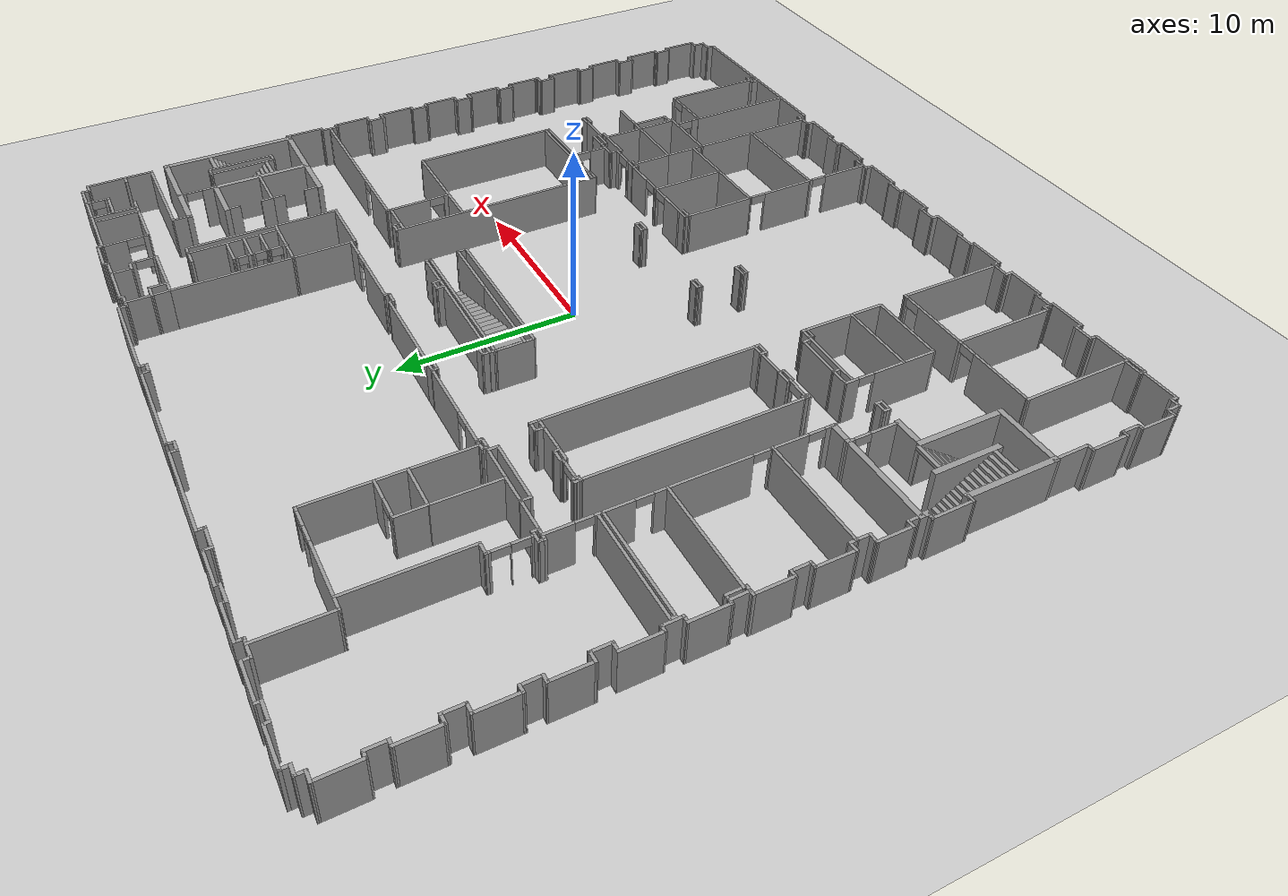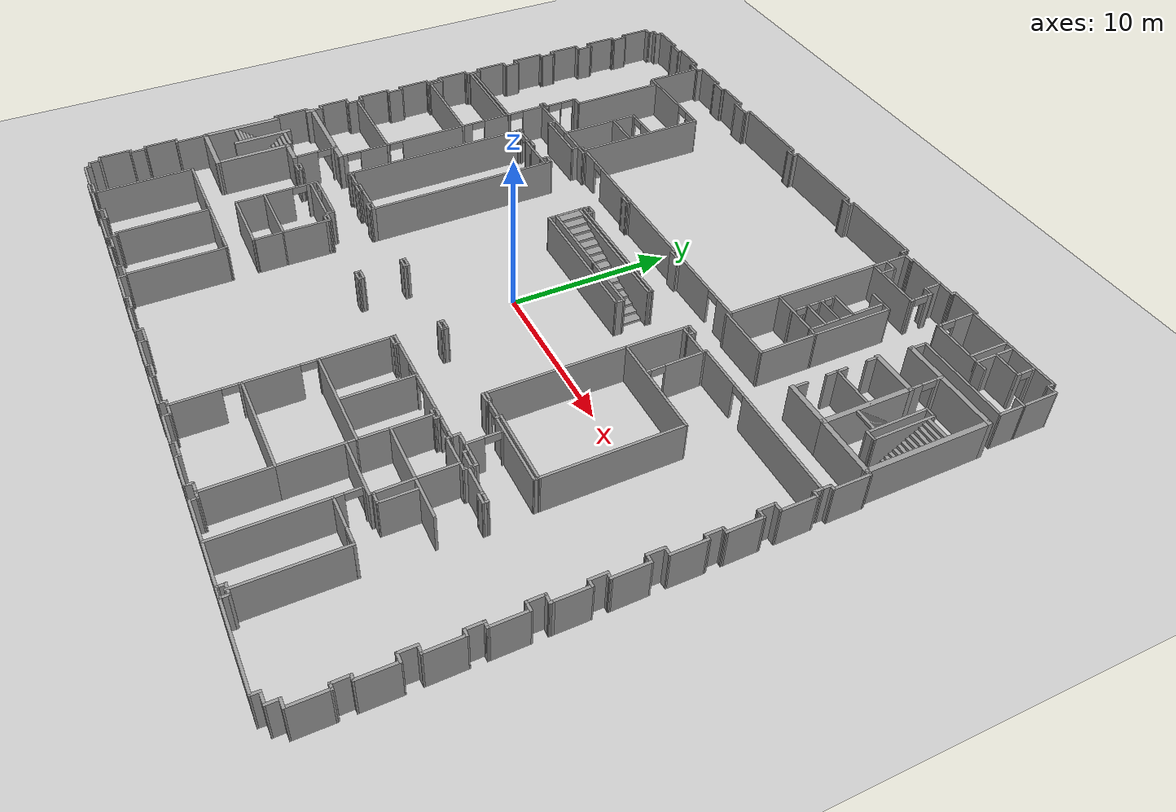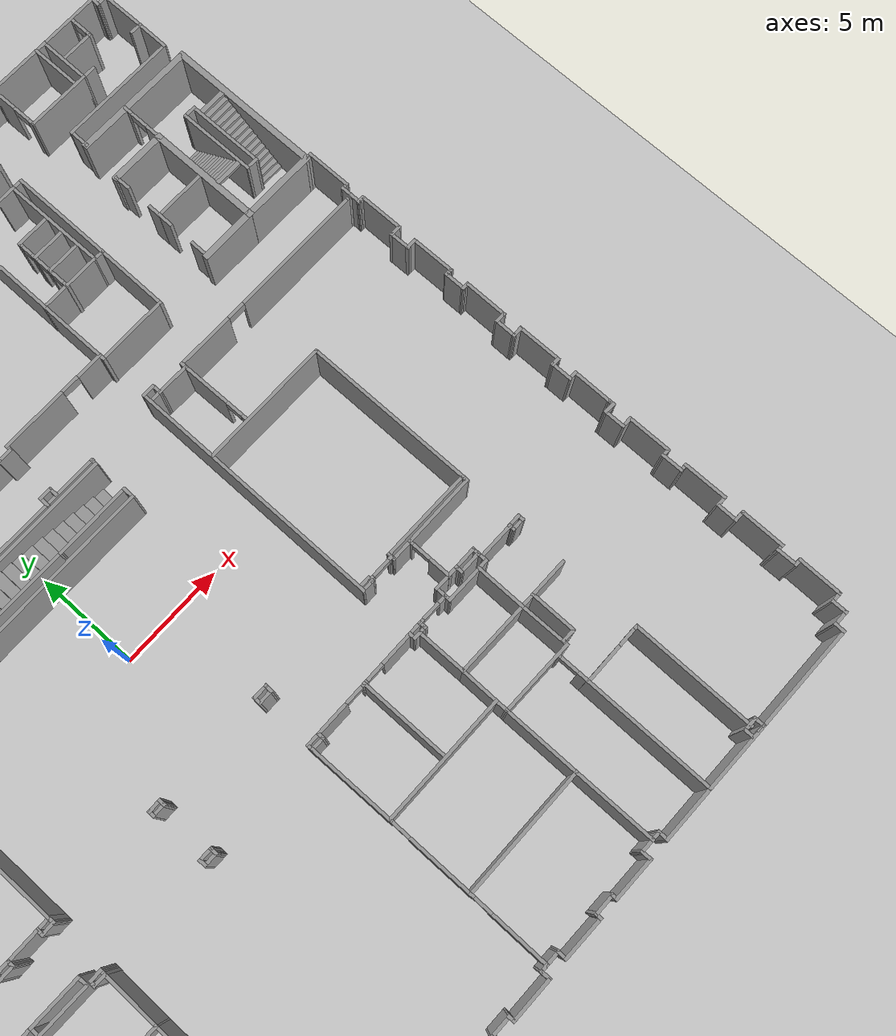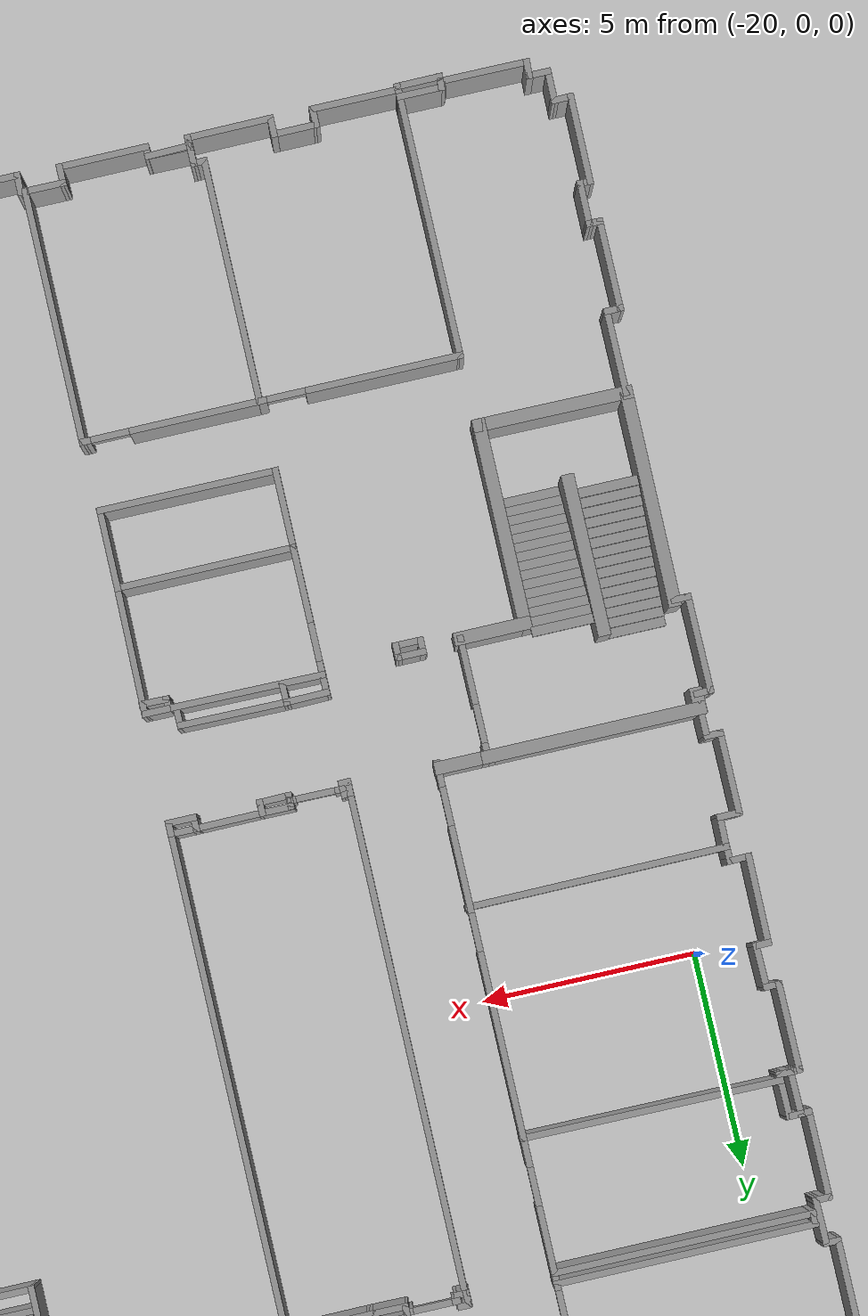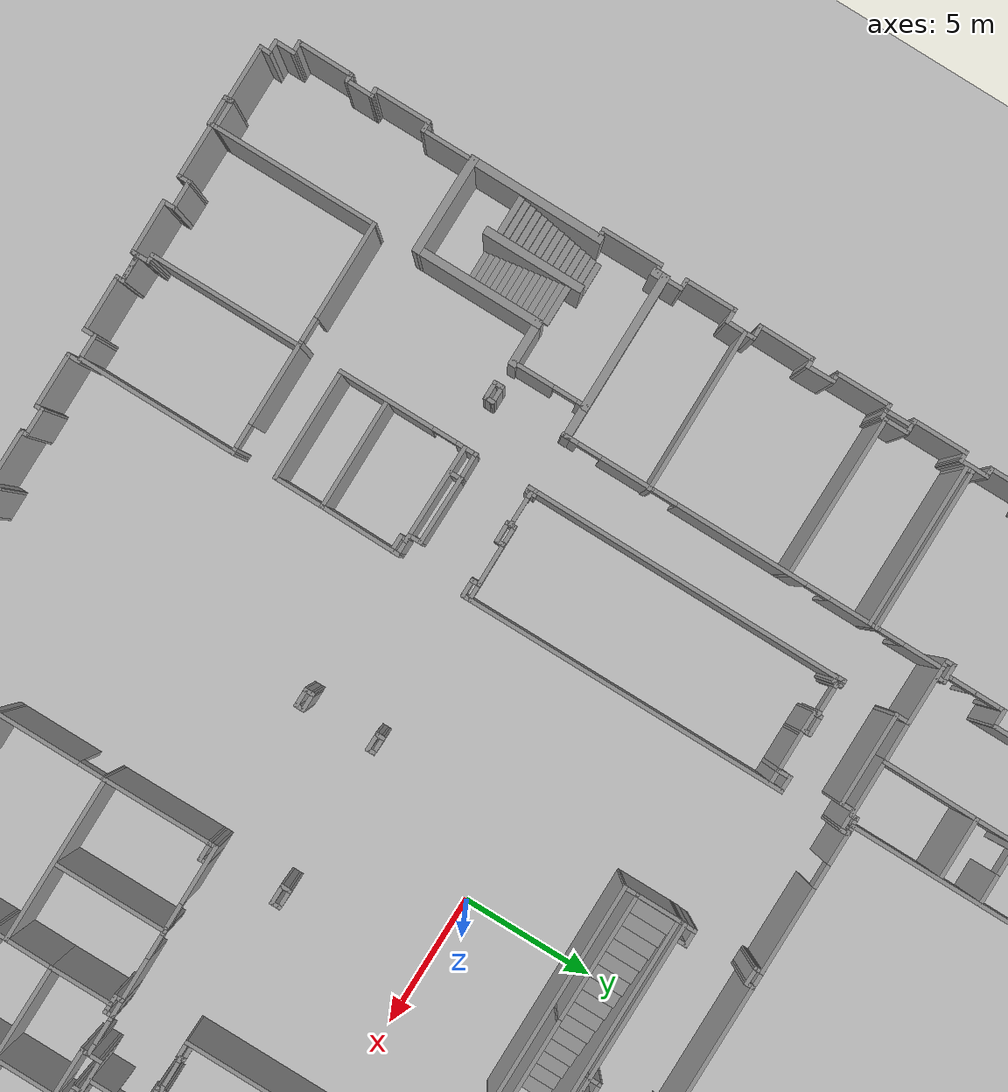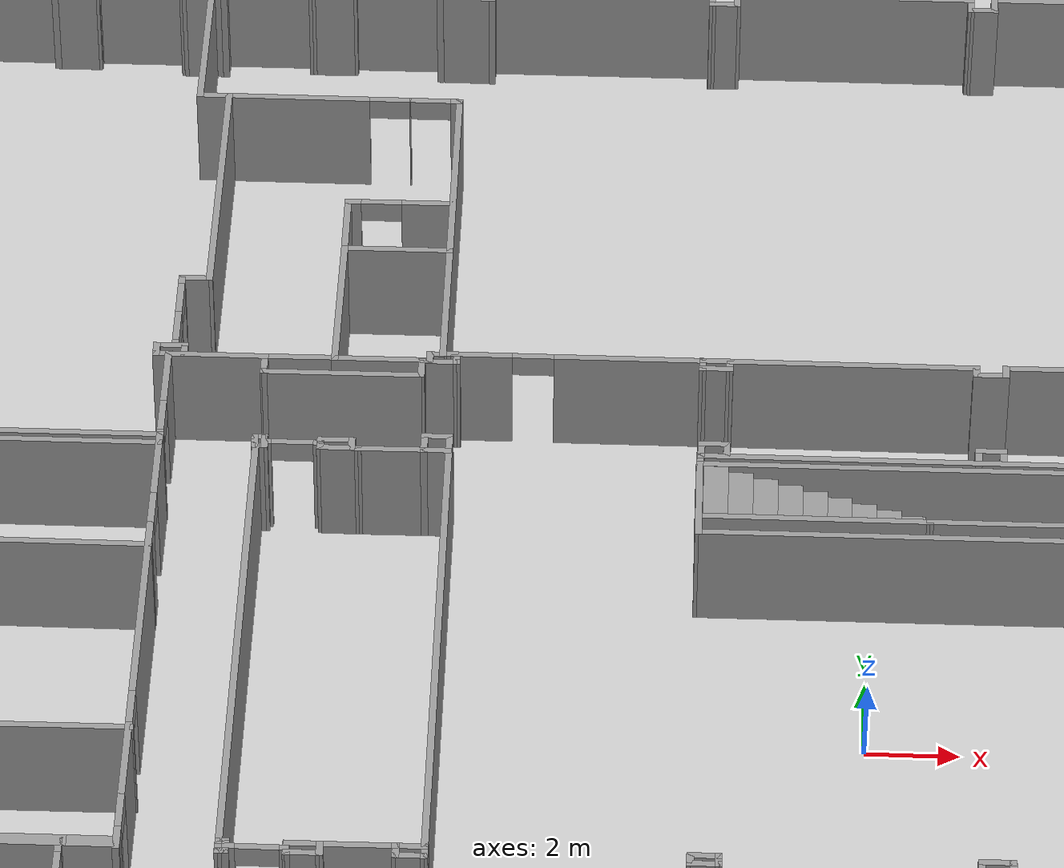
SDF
<sdf version="1.6">
 <world name="default">
  <light name="sun" type="directional">
   <pose>0 0 10 0 -0 0</pose>
   <diffuse>0.8 0.8 0.8 1</diffuse>
   <specular>0.2 0.2 0.2 1</specular>
   <attenuation>
    <range>1000</range>
    <constant>0.9</constant>
    <linear>0.01</linear>
    <quadratic>0.001</quadratic>
   </attenuation>
   <direction>-0.5 0.1 -0.9</direction>
  </light>
  <model name="ground_plane">
   <static>1</static>
   <link name="link">
    <collision name="collision">
     <geometry><plane><normal>0 0 1</normal><size>100 100</size></plane></geometry>
     <surface>
      <contact><collide_bitmask>65535</collide_bitmask></contact>
      <friction><ode><mu>100</mu><mu2>50</mu2></ode></friction>
     </surface>
    </collision>
    <visual name="visual">
     <cast_shadows>0</cast_shadows>
     <geometry><plane><normal>0 0 1</normal><size>100 100</size></plane></geometry>
     <material>
      <script><uri>file://media/materials/scripts/gazebo.material</uri><name>Gazebo/Grey</name></script>
     </material>
    </visual>
   </link>
  </model>
  <gravity>0 0 -9.8</gravity>
  <magnetic_field>6e-06 2.3e-05 -4.2e-05</magnetic_field>
  <atmosphere type="adiabatic"/>
  <physics name="default_physics" default="0" type="ode">
   <max_step_size>0.001</max_step_size>
   <real_time_factor>1</real_time_factor>
   <real_time_update_rate>1000</real_time_update_rate>
  </physics>
  <scene><ambient>0.4 0.4 0.4 1</ambient><background>0.7 0.7 0.7 1</background><shadows>1</shadows></scene>
  <spherical_coordinates>
   <surface_model>EARTH_WGS84</surface_model>
   <latitude_deg>0</latitude_deg>
   <longitude_deg>0</longitude_deg>
   <elevation>0</elevation>
   <heading_deg>0</heading_deg>
  </spherical_coordinates>
  <model name="Myhal_5th_floor">
   <pose>-0.342666 0.4433 0 0 -0 0</pose>
   <link name="Stairs_0">
    <visual name="Stairs_0_Visual_0">
     <pose>4.54458 4.82327 0.083333 0 -0 -1.5708</pose>
     <geometry><box><size>1.43752 0.532234 0.166667</size></box></geometry>
     <material>
      <script><uri>file://media/materials/scripts/gazebo.material</uri><name>Gazebo/Grey</name></script>
      <ambient>1 1 1 1</ambient>
     </material>
     <meta><layer>0</layer></meta>
    </visual>
    <collision name="Stairs_0_Collision_0">
     <geometry><box><size>1.43752 0.532234 0.166667</size></box></geometry>
     <pose>4.54458 4.82327 0.083333 0 -0 -1.5708</pose>
    </collision>
    <visual name="Stairs_0_Visual_1">
     <pose>4.01234 4.82327 0.25 0 -0 -1.5708</pose>
     <geometry><box><size>1.43752 0.532234 0.166667</size></box></geometry>
     <material>
      <script><uri>file://media/materials/scripts/gazebo.material</uri><name>Gazebo/Grey</name></script>
      <ambient>1 1 1 1</ambient>
     </material>
     <meta><layer>0</layer></meta>
    </visual>
    <collision name="Stairs_0_Collision_1">
     <geometry><box><size>1.43752 0.532234 0.166667</size></box></geometry>
     <pose>4.01234 4.82327 0.25 0 -0 -1.5708</pose>
    </collision>
    <visual name="Stairs_0_Visual_2">
     <pose>3.48011 4.82327 0.416667 0 -0 -1.5708</pose>
     <geometry><box><size>1.43752 0.532234 0.166667</size></box></geometry>
     <material>
      <script><uri>file://media/materials/scripts/gazebo.material</uri><name>Gazebo/Grey</name></script>
      <ambient>1 1 1 1</ambient>
     </material>
     <meta><layer>0</layer></meta>
    </visual>
    <collision name="Stairs_0_Collision_2">
     <geometry><box><size>1.43752 0.532234 0.166667</size></box></geometry>
     <pose>3.48011 4.82327 0.416667 0 -0 -1.5708</pose>
    </collision>
    <visual name="Stairs_0_Visual_3">
     <pose>2.94787 4.82327 0.583333 0 -0 -1.5708</pose>
     <geometry><box><size>1.43752 0.532234 0.166667</size></box></geometry>
     <material>
      <script><uri>file://media/materials/scripts/gazebo.material</uri><name>Gazebo/Grey</name></script>
      <ambient>1 1 1 1</ambient>
     </material>
     <meta><layer>0</layer></meta>
    </visual>
    <collision name="Stairs_0_Collision_3">
     <geometry><box><size>1.43752 0.532234 0.166667</size></box></geometry>
     <pose>2.94787 4.82327 0.583333 0 -0 -1.5708</pose>
    </collision>
    <visual name="Stairs_0_Visual_4">
     <pose>2.41564 4.82327 0.75 0 -0 -1.5708</pose>
     <geometry><box><size>1.43752 0.532234 0.166667</size></box></geometry>
     <material>
      <script><uri>file://media/materials/scripts/gazebo.material</uri><name>Gazebo/Grey</name></script>
      <ambient>1 1 1 1</ambient>
     </material>
     <meta><layer>0</layer></meta>
    </visual>
    <collision name="Stairs_0_Collision_4">
     <geometry><box><size>1.43752 0.532234 0.166667</size></box></geometry>
     <pose>2.41564 4.82327 0.75 0 -0 -1.5708</pose>
    </collision>
    <visual name="Stairs_0_Visual_5">
     <pose>1.88341 4.82327 0.916667 0 -0 -1.5708</pose>
     <geometry><box><size>1.43752 0.532234 0.166667</size></box></geometry>
     <material>
      <script><uri>file://media/materials/scripts/gazebo.material</uri><name>Gazebo/Grey</name></script>
      <ambient>1 1 1 1</ambient>
     </material>
     <meta><layer>0</layer></meta>
    </visual>
    <collision name="Stairs_0_Collision_5">
     <geometry><box><size>1.43752 0.532234 0.166667</size></box></geometry>
     <pose>1.88341 4.82327 0.916667 0 -0 -1.5708</pose>
    </collision>
    <visual name="Stairs_0_Visual_6">
     <pose>1.35117 4.82327 1.08333 0 -0 -1.5708</pose>
     <geometry><box><size>1.43752 0.532234 0.166667</size></box></geometry>
     <material>
      <script><uri>file://media/materials/scripts/gazebo.material</uri><name>Gazebo/Grey</name></script>
      <ambient>1 1 1 1</ambient>
     </material>
     <meta><layer>0</layer></meta>
    </visual>
    <collision name="Stairs_0_Collision_6">
     <geometry><box><size>1.43752 0.532234 0.166667</size></box></geometry>
     <pose>1.35117 4.82327 1.08333 0 -0 -1.5708</pose>
    </collision>
    <visual name="Stairs_0_Visual_7">
     <pose>0.818936 4.82327 1.25 0 -0 -1.5708</pose>
     <geometry><box><size>1.43752 0.532234 0.166667</size></box></geometry>
     <material>
      <script><uri>file://media/materials/scripts/gazebo.material</uri><name>Gazebo/Grey</name></script>
      <ambient>1 1 1 1</ambient>
     </material>
     <meta><layer>0</layer></meta>
    </visual>
    <collision name="Stairs_0_Collision_7">
     <geometry><box><size>1.43752 0.532234 0.166667</size></box></geometry>
     <pose>0.818936 4.82327 1.25 0 -0 -1.5708</pose>
    </collision>
    <visual name="Stairs_0_Visual_8">
     <pose>0.286702 4.82327 1.41667 0 -0 -1.5708</pose>
     <geometry><box><size>1.43752 0.532234 0.166667</size></box></geometry>
     <material>
      <script><uri>file://media/materials/scripts/gazebo.material</uri><name>Gazebo/Grey</name></script>
      <ambient>1 1 1 1</ambient>
     </material>
     <meta><layer>0</layer></meta>
    </visual>
    <collision name="Stairs_0_Collision_8">
     <geometry><box><size>1.43752 0.532234 0.166667</size></box></geometry>
     <pose>0.286702 4.82327 1.41667 0 -0 -1.5708</pose>
    </collision>
    <visual name="Stairs_0_Visual_9">
     <pose>-0.245533 4.82327 1.58333 0 -0 -1.5708</pose>
     <geometry><box><size>1.43752 0.532234 0.166667</size></box></geometry>
     <material>
      <script><uri>file://media/materials/scripts/gazebo.material</uri><name>Gazebo/Grey</name></script>
      <ambient>1 1 1 1</ambient>
     </material>
     <meta><layer>0</layer></meta>
    </visual>
    <collision name="Stairs_0_Collision_9">
     <geometry><box><size>1.43752 0.532234 0.166667</size></box></geometry>
     <pose>-0.245533 4.82327 1.58333 0 -0 -1.5708</pose>
    </collision>
    <visual name="Stairs_0_Visual_10">
     <pose>-0.777767 4.82327 1.75 0 -0 -1.5708</pose>
     <geometry><box><size>1.43752 0.532234 0.166667</size></box></geometry>
     <material>
      <script><uri>file://media/materials/scripts/gazebo.material</uri><name>Gazebo/Grey</name></script>
      <ambient>1 1 1 1</ambient>
     </material>
     <meta><layer>0</layer></meta>
    </visual>
    <collision name="Stairs_0_Collision_10">
     <geometry><box><size>1.43752 0.532234 0.166667</size></box></geometry>
     <pose>-0.777767 4.82327 1.75 0 -0 -1.5708</pose>
    </collision>
    <visual name="Stairs_0_Visual_11">
     <pose>-1.31 4.82327 1.91667 0 -0 -1.5708</pose>
     <geometry><box><size>1.43752 0.532234 0.166667</size></box></geometry>
     <material>
      <script><uri>file://media/materials/scripts/gazebo.material</uri><name>Gazebo/Grey</name></script>
      <ambient>1 1 1 1</ambient>
     </material>
     <meta><layer>0</layer></meta>
    </visual>
    <collision name="Stairs_0_Collision_11">
     <geometry><box><size>1.43752 0.532234 0.166667</size></box></geometry>
     <pose>-1.31 4.82327 1.91667 0 -0 -1.5708</pose>
    </collision>
    <visual name="Stairs_0_Visual_12">
     <pose>-1.84224 4.82327 2.08333 0 -0 -1.5708</pose>
     <geometry><box><size>1.43752 0.532234 0.166667</size></box></geometry>
     <material>
      <script><uri>file://media/materials/scripts/gazebo.material</uri><name>Gazebo/Grey</name></script>
      <ambient>1 1 1 1</ambient>
     </material>
     <meta><layer>0</layer></meta>
    </visual>
    <collision name="Stairs_0_Collision_12">
     <geometry><box><size>1.43752 0.532234 0.166667</size></box></geometry>
     <pose>-1.84224 4.82327 2.08333 0 -0 -1.5708</pose>
    </collision>
    <visual name="Stairs_0_Visual_13">
     <pose>-2.37447 4.82327 2.25 0 -0 -1.5708</pose>
     <geometry><box><size>1.43752 0.532234 0.166667</size></box></geometry>
     <material>
      <script><uri>file://media/materials/scripts/gazebo.material</uri><name>Gazebo/Grey</name></script>
      <ambient>1 1 1 1</ambient>
     </material>
     <meta><layer>0</layer></meta>
    </visual>
    <collision name="Stairs_0_Collision_13">
     <geometry><box><size>1.43752 0.532234 0.166667</size></box></geometry>
     <pose>-2.37447 4.82327 2.25 0 -0 -1.5708</pose>
    </collision>
    <visual name="Stairs_0_Visual_14">
     <pose>-2.90671 4.82327 2.41667 0 -0 -1.5708</pose>
     <geometry><box><size>1.43752 0.532234 0.166667</size></box></geometry>
     <material>
      <script><uri>file://media/materials/scripts/gazebo.material</uri><name>Gazebo/Grey</name></script>
      <ambient>1 1 1 1</ambient>
     </material>
     <meta><layer>0</layer></meta>
    </visual>
    <collision name="Stairs_0_Collision_14">
     <geometry><box><size>1.43752 0.532234 0.166667</size></box></geometry>
     <pose>-2.90671 4.82327 2.41667 0 -0 -1.5708</pose>
    </collision>
   </link>
   <link name="Stairs_1">
    <visual name="Stairs_1_Visual_0">
     <pose>-18.3151 -11.5504 0.083333 0 -0 -3.14159</pose>
     <geometry><box><size>1.44258 0.225089 0.166667</size></box></geometry>
     <material>
      <script><uri>file://media/materials/scripts/gazebo.material</uri><name>Gazebo/Grey</name></script>
      <ambient>1 1 1 1</ambient>
     </material>
     <meta><layer>0</layer></meta>
    </visual>
    <collision name="Stairs_1_Collision_0">
     <geometry><box><size>1.44258 0.225089 0.166667</size></box></geometry>
     <pose>-18.3151 -11.5504 0.083333 0 -0 -3.14159</pose>
    </collision>
    <visual name="Stairs_1_Visual_1">
     <pose>-18.3151 -11.3253 0.25 0 -0 -3.14159</pose>
     <geometry><box><size>1.44258 0.225089 0.166667</size></box></geometry>
     <material>
      <script><uri>file://media/materials/scripts/gazebo.material</uri><name>Gazebo/Grey</name></script>
      <ambient>1 1 1 1</ambient>
     </material>
     <meta><layer>0</layer></meta>
    </visual>
    <collision name="Stairs_1_Collision_1">
     <geometry><box><size>1.44258 0.225089 0.166667</size></box></geometry>
     <pose>-18.3151 -11.3253 0.25 0 -0 -3.14159</pose>
    </collision>
    <visual name="Stairs_1_Visual_2">
     <pose>-18.3151 -11.1002 0.416667 0 -0 -3.14159</pose>
     <geometry><box><size>1.44258 0.225089 0.166667</size></box></geometry>
     <material>
      <script><uri>file://media/materials/scripts/gazebo.material</uri><name>Gazebo/Grey</name></script>
      <ambient>1 1 1 1</ambient>
     </material>
     <meta><layer>0</layer></meta>
    </visual>
    <collision name="Stairs_1_Collision_2">
     <geometry><box><size>1.44258 0.225089 0.166667</size></box></geometry>
     <pose>-18.3151 -11.1002 0.416667 0 -0 -3.14159</pose>
    </collision>
    <visual name="Stairs_1_Visual_3">
     <pose>-18.3151 -10.8751 0.583333 0 -0 -3.14159</pose>
     <geometry><box><size>1.44258 0.225089 0.166667</size></box></geometry>
     <material>
      <script><uri>file://media/materials/scripts/gazebo.material</uri><name>Gazebo/Grey</name></script>
      <ambient>1 1 1 1</ambient>
     </material>
     <meta><layer>0</layer></meta>
    </visual>
    <collision name="Stairs_1_Collision_3">
     <geometry><box><size>1.44258 0.225089 0.166667</size></box></geometry>
     <pose>-18.3151 -10.8751 0.583333 0 -0 -3.14159</pose>
    </collision>
    <visual name="Stairs_1_Visual_4">
     <pose>-18.3151 -10.65 0.75 0 -0 -3.14159</pose>
     <geometry><box><size>1.44258 0.225089 0.166667</size></box></geometry>
     <material>
      <script><uri>file://media/materials/scripts/gazebo.material</uri><name>Gazebo/Grey</name></script>
      <ambient>1 1 1 1</ambient>
     </material>
     <meta><layer>0</layer></meta>
    </visual>
    <collision name="Stairs_1_Collision_4">
     <geometry><box><size>1.44258 0.225089 0.166667</size></box></geometry>
     <pose>-18.3151 -10.65 0.75 0 -0 -3.14159</pose>
    </collision>
    <visual name="Stairs_1_Visual_5">
     <pose>-18.3151 -10.425 0.916667 0 -0 -3.14159</pose>
     <geometry><box><size>1.44258 0.225089 0.166667</size></box></geometry>
     <material>
      <script><uri>file://media/materials/scripts/gazebo.material</uri><name>Gazebo/Grey</name></script>
      <ambient>1 1 1 1</ambient>
     </material>
     <meta><layer>0</layer></meta>
    </visual>
    <collision name="Stairs_1_Collision_5">
     <geometry><box><size>1.44258 0.225089 0.166667</size></box></geometry>
     <pose>-18.3151 -10.425 0.916667 0 -0 -3.14159</pose>
    </collision>
    <visual name="Stairs_1_Visual_6">
     <pose>-18.3151 -10.1999 1.08333 0 -0 -3.14159</pose>
     <geometry><box><size>1.44258 0.225089 0.166667</size></box></geometry>
     <material>
      <script><uri>file://media/materials/scripts/gazebo.material</uri><name>Gazebo/Grey</name></script>
      <ambient>1 1 1 1</ambient>
     </material>
     <meta><layer>0</layer></meta>
    </visual>
    <collision name="Stairs_1_Collision_6">
     <geometry><box><size>1.44258 0.225089 0.166667</size></box></geometry>
     <pose>-18.3151 -10.1999 1.08333 0 -0 -3.14159</pose>
    </collision>
    <visual name="Stairs_1_Visual_7">
     <pose>-18.3151 -9.97478 1.25 0 -0 -3.14159</pose>
     <geometry><box><size>1.44258 0.225089 0.166667</size></box></geometry>
     <material>
      <script><uri>file://media/materials/scripts/gazebo.material</uri><name>Gazebo/Grey</name></script>
      <ambient>1 1 1 1</ambient>
     </material>
     <meta><layer>0</layer></meta>
    </visual>
    <collision name="Stairs_1_Collision_7">
     <geometry><box><size>1.44258 0.225089 0.166667</size></box></geometry>
     <pose>-18.3151 -9.97478 1.25 0 -0 -3.14159</pose>
    </collision>
    <visual name="Stairs_1_Visual_8">
     <pose>-18.3151 -9.74969 1.41667 0 -0 -3.14159</pose>
     <geometry><box><size>1.44258 0.225089 0.166667</size></box></geometry>
     <material>
      <script><uri>file://media/materials/scripts/gazebo.material</uri><name>Gazebo/Grey</name></script>
      <ambient>1 1 1 1</ambient>
     </material>
     <meta><layer>0</layer></meta>
    </visual>
    <collision name="Stairs_1_Collision_8">
     <geometry><box><size>1.44258 0.225089 0.166667</size></box></geometry>
     <pose>-18.3151 -9.74969 1.41667 0 -0 -3.14159</pose>
    </collision>
    <visual name="Stairs_1_Visual_9">
     <pose>-18.3151 -9.5246 1.58333 0 -0 -3.14159</pose>
     <geometry><box><size>1.44258 0.225089 0.166667</size></box></geometry>
     <material>
      <script><uri>file://media/materials/scripts/gazebo.material</uri><name>Gazebo/Grey</name></script>
      <ambient>1 1 1 1</ambient>
     </material>
     <meta><layer>0</layer></meta>
    </visual>
    <collision name="Stairs_1_Collision_9">
     <geometry><box><size>1.44258 0.225089 0.166667</size></box></geometry>
     <pose>-18.3151 -9.5246 1.58333 0 -0 -3.14159</pose>
    </collision>
    <visual name="Stairs_1_Visual_10">
     <pose>-18.3151 -9.29951 1.75 0 -0 -3.14159</pose>
     <geometry><box><size>1.44258 0.225089 0.166667</size></box></geometry>
     <material>
      <script><uri>file://media/materials/scripts/gazebo.material</uri><name>Gazebo/Grey</name></script>
      <ambient>1 1 1 1</ambient>
     </material>
     <meta><layer>0</layer></meta>
    </visual>
    <collision name="Stairs_1_Collision_10">
     <geometry><box><size>1.44258 0.225089 0.166667</size></box></geometry>
     <pose>-18.3151 -9.29951 1.75 0 -0 -3.14159</pose>
    </collision>
    <visual name="Stairs_1_Visual_11">
     <pose>-18.3151 -9.07442 1.91667 0 -0 -3.14159</pose>
     <geometry><box><size>1.44258 0.225089 0.166667</size></box></geometry>
     <material>
      <script><uri>file://media/materials/scripts/gazebo.material</uri><name>Gazebo/Grey</name></script>
      <ambient>1 1 1 1</ambient>
     </material>
     <meta><layer>0</layer></meta>
    </visual>
    <collision name="Stairs_1_Collision_11">
     <geometry><box><size>1.44258 0.225089 0.166667</size></box></geometry>
     <pose>-18.3151 -9.07442 1.91667 0 -0 -3.14159</pose>
    </collision>
    <visual name="Stairs_1_Visual_12">
     <pose>-18.3151 -8.84933 2.08333 0 -0 -3.14159</pose>
     <geometry><box><size>1.44258 0.225089 0.166667</size></box></geometry>
     <material>
      <script><uri>file://media/materials/scripts/gazebo.material</uri><name>Gazebo/Grey</name></script>
      <ambient>1 1 1 1</ambient>
     </material>
     <meta><layer>0</layer></meta>
    </visual>
    <collision name="Stairs_1_Collision_12">
     <geometry><box><size>1.44258 0.225089 0.166667</size></box></geometry>
     <pose>-18.3151 -8.84933 2.08333 0 -0 -3.14159</pose>
    </collision>
    <visual name="Stairs_1_Visual_13">
     <pose>-18.3151 -8.62425 2.25 0 -0 -3.14159</pose>
     <geometry><box><size>1.44258 0.225089 0.166667</size></box></geometry>
     <material>
      <script><uri>file://media/materials/scripts/gazebo.material</uri><name>Gazebo/Grey</name></script>
      <ambient>1 1 1 1</ambient>
     </material>
     <meta><layer>0</layer></meta>
    </visual>
    <collision name="Stairs_1_Collision_13">
     <geometry><box><size>1.44258 0.225089 0.166667</size></box></geometry>
     <pose>-18.3151 -8.62425 2.25 0 -0 -3.14159</pose>
    </collision>
    <visual name="Stairs_1_Visual_14">
     <pose>-18.3151 -8.39916 2.41667 0 -0 -3.14159</pose>
     <geometry><box><size>1.44258 0.225089 0.166667</size></box></geometry>
     <material>
      <script><uri>file://media/materials/scripts/gazebo.material</uri><name>Gazebo/Grey</name></script>
      <ambient>1 1 1 1</ambient>
     </material>
     <meta><layer>0</layer></meta>
    </visual>
    <collision name="Stairs_1_Collision_14">
     <geometry><box><size>1.44258 0.225089 0.166667</size></box></geometry>
     <pose>-18.3151 -8.39916 2.41667 0 -0 -3.14159</pose>
    </collision>
   </link>
   <link name="Stairs_2">
    <visual name="Stairs_2_Visual_0">
     <pose>-20.0394 -8.07341 0.083333 0 -0 0</pose>
     <geometry><box><size>1.39487 0.225838 0.166667</size></box></geometry>
     <material>
      <script><uri>file://media/materials/scripts/gazebo.material</uri><name>Gazebo/Grey</name></script>
      <ambient>1 1 1 1</ambient>
     </material>
     <meta><layer>0</layer></meta>
    </visual>
    <collision name="Stairs_2_Collision_0">
     <geometry><box><size>1.39487 0.225838 0.166667</size></box></geometry>
     <pose>-20.0394 -8.07341 0.083333 0 -0 0</pose>
    </collision>
    <visual name="Stairs_2_Visual_1">
     <pose>-20.0394 -8.29925 0.25 0 -0 0</pose>
     <geometry><box><size>1.39487 0.225838 0.166667</size></box></geometry>
     <material>
      <script><uri>file://media/materials/scripts/gazebo.material</uri><name>Gazebo/Grey</name></script>
      <ambient>1 1 1 1</ambient>
     </material>
     <meta><layer>0</layer></meta>
    </visual>
    <collision name="Stairs_2_Collision_1">
     <geometry><box><size>1.39487 0.225838 0.166667</size></box></geometry>
     <pose>-20.0394 -8.29925 0.25 0 -0 0</pose>
    </collision>
    <visual name="Stairs_2_Visual_2">
     <pose>-20.0394 -8.52509 0.416667 0 -0 0</pose>
     <geometry><box><size>1.39487 0.225838 0.166667</size></box></geometry>
     <material>
      <script><uri>file://media/materials/scripts/gazebo.material</uri><name>Gazebo/Grey</name></script>
      <ambient>1 1 1 1</ambient>
     </material>
     <meta><layer>0</layer></meta>
    </visual>
    <collision name="Stairs_2_Collision_2">
     <geometry><box><size>1.39487 0.225838 0.166667</size></box></geometry>
     <pose>-20.0394 -8.52509 0.416667 0 -0 0</pose>
    </collision>
    <visual name="Stairs_2_Visual_3">
     <pose>-20.0394 -8.75093 0.583333 0 -0 0</pose>
     <geometry><box><size>1.39487 0.225838 0.166667</size></box></geometry>
     <material>
      <script><uri>file://media/materials/scripts/gazebo.material</uri><name>Gazebo/Grey</name></script>
      <ambient>1 1 1 1</ambient>
     </material>
     <meta><layer>0</layer></meta>
    </visual>
    <collision name="Stairs_2_Collision_3">
     <geometry><box><size>1.39487 0.225838 0.166667</size></box></geometry>
     <pose>-20.0394 -8.75093 0.583333 0 -0 0</pose>
    </collision>
    <visual name="Stairs_2_Visual_4">
     <pose>-20.0394 -8.97677 0.75 0 -0 0</pose>
     <geometry><box><size>1.39487 0.225838 0.166667</size></box></geometry>
     <material>
      <script><uri>file://media/materials/scripts/gazebo.material</uri><name>Gazebo/Grey</name></script>
      <ambient>1 1 1 1</ambient>
     </material>
     <meta><layer>0</layer></meta>
    </visual>
    <collision name="Stairs_2_Collision_4">
     <geometry><box><size>1.39487 0.225838 0.166667</size></box></geometry>
     <pose>-20.0394 -8.97677 0.75 0 -0 0</pose>
    </collision>
    <visual name="Stairs_2_Visual_5">
     <pose>-20.0394 -9.20261 0.916667 0 -0 0</pose>
     <geometry><box><size>1.39487 0.225838 0.166667</size></box></geometry>
     <material>
      <script><uri>file://media/materials/scripts/gazebo.material</uri><name>Gazebo/Grey</name></script>
      <ambient>1 1 1 1</ambient>
     </material>
     <meta><layer>0</layer></meta>
    </visual>
    <collision name="Stairs_2_Collision_5">
     <geometry><box><size>1.39487 0.225838 0.166667</size></box></geometry>
     <pose>-20.0394 -9.20261 0.916667 0 -0 0</pose>
    </collision>
    <visual name="Stairs_2_Visual_6">
     <pose>-20.0394 -9.42844 1.08333 0 -0 0</pose>
     <geometry><box><size>1.39487 0.225838 0.166667</size></box></geometry>
     <material>
      <script><uri>file://media/materials/scripts/gazebo.material</uri><name>Gazebo/Grey</name></script>
      <ambient>1 1 1 1</ambient>
     </material>
     <meta><layer>0</layer></meta>
    </visual>
    <collision name="Stairs_2_Collision_6">
     <geometry><box><size>1.39487 0.225838 0.166667</size></box></geometry>
     <pose>-20.0394 -9.42844 1.08333 0 -0 0</pose>
    </collision>
    <visual name="Stairs_2_Visual_7">
     <pose>-20.0394 -9.65428 1.25 0 -0 0</pose>
     <geometry><box><size>1.39487 0.225838 0.166667</size></box></geometry>
     <material>
      <script><uri>file://media/materials/scripts/gazebo.material</uri><name>Gazebo/Grey</name></script>
      <ambient>1 1 1 1</ambient>
     </material>
     <meta><layer>0</layer></meta>
    </visual>
    <collision name="Stairs_2_Collision_7">
     <geometry><box><size>1.39487 0.225838 0.166667</size></box></geometry>
     <pose>-20.0394 -9.65428 1.25 0 -0 0</pose>
    </collision>
    <visual name="Stairs_2_Visual_8">
     <pose>-20.0394 -9.88012 1.41667 0 -0 0</pose>
     <geometry><box><size>1.39487 0.225838 0.166667</size></box></geometry>
     <material>
      <script><uri>file://media/materials/scripts/gazebo.material</uri><name>Gazebo/Grey</name></script>
      <ambient>1 1 1 1</ambient>
     </material>
     <meta><layer>0</layer></meta>
    </visual>
    <collision name="Stairs_2_Collision_8">
     <geometry><box><size>1.39487 0.225838 0.166667</size></box></geometry>
     <pose>-20.0394 -9.88012 1.41667 0 -0 0</pose>
    </collision>
    <visual name="Stairs_2_Visual_9">
     <pose>-20.0394 -10.106 1.58333 0 -0 0</pose>
     <geometry><box><size>1.39487 0.225838 0.166667</size></box></geometry>
     <material>
      <script><uri>file://media/materials/scripts/gazebo.material</uri><name>Gazebo/Grey</name></script>
      <ambient>1 1 1 1</ambient>
     </material>
     <meta><layer>0</layer></meta>
    </visual>
    <collision name="Stairs_2_Collision_9">
     <geometry><box><size>1.39487 0.225838 0.166667</size></box></geometry>
     <pose>-20.0394 -10.106 1.58333 0 -0 0</pose>
    </collision>
    <visual name="Stairs_2_Visual_10">
     <pose>-20.0394 -10.3318 1.75 0 -0 0</pose>
     <geometry><box><size>1.39487 0.225838 0.166667</size></box></geometry>
     <material>
      <script><uri>file://media/materials/scripts/gazebo.material</uri><name>Gazebo/Grey</name></script>
      <ambient>1 1 1 1</ambient>
     </material>
     <meta><layer>0</layer></meta>
    </visual>
    <collision name="Stairs_2_Collision_10">
     <geometry><box><size>1.39487 0.225838 0.166667</size></box></geometry>
     <pose>-20.0394 -10.3318 1.75 0 -0 0</pose>
    </collision>
    <visual name="Stairs_2_Visual_11">
     <pose>-20.0394 -10.5576 1.91667 0 -0 0</pose>
     <geometry><box><size>1.39487 0.225838 0.166667</size></box></geometry>
     <material>
      <script><uri>file://media/materials/scripts/gazebo.material</uri><name>Gazebo/Grey</name></script>
      <ambient>1 1 1 1</ambient>
     </material>
     <meta><layer>0</layer></meta>
    </visual>
    <collision name="Stairs_2_Collision_11">
     <geometry><box><size>1.39487 0.225838 0.166667</size></box></geometry>
     <pose>-20.0394 -10.5576 1.91667 0 -0 0</pose>
    </collision>
    <visual name="Stairs_2_Visual_12">
     <pose>-20.0394 -10.7835 2.08333 0 -0 0</pose>
     <geometry><box><size>1.39487 0.225838 0.166667</size></box></geometry>
     <material>
      <script><uri>file://media/materials/scripts/gazebo.material</uri><name>Gazebo/Grey</name></script>
      <ambient>1 1 1 1</ambient>
     </material>
     <meta><layer>0</layer></meta>
    </visual>
    <collision name="Stairs_2_Collision_12">
     <geometry><box><size>1.39487 0.225838 0.166667</size></box></geometry>
     <pose>-20.0394 -10.7835 2.08333 0 -0 0</pose>
    </collision>
    <visual name="Stairs_2_Visual_13">
     <pose>-20.0394 -11.0093 2.25 0 -0 0</pose>
     <geometry><box><size>1.39487 0.225838 0.166667</size></box></geometry>
     <material>
      <script><uri>file://media/materials/scripts/gazebo.material</uri><name>Gazebo/Grey</name></script>
      <ambient>1 1 1 1</ambient>
     </material>
     <meta><layer>0</layer></meta>
    </visual>
    <collision name="Stairs_2_Collision_13">
     <geometry><box><size>1.39487 0.225838 0.166667</size></box></geometry>
     <pose>-20.0394 -11.0093 2.25 0 -0 0</pose>
    </collision>
    <visual name="Stairs_2_Visual_14">
     <pose>-20.0394 -11.2352 2.41667 0 -0 0</pose>
     <geometry><box><size>1.39487 0.225838 0.166667</size></box></geometry>
     <material>
      <script><uri>file://media/materials/scripts/gazebo.material</uri><name>Gazebo/Grey</name></script>
      <ambient>1 1 1 1</ambient>
     </material>
     <meta><layer>0</layer></meta>
    </visual>
    <collision name="Stairs_2_Collision_14">
     <geometry><box><size>1.39487 0.225838 0.166667</size></box></geometry>
     <pose>-20.0394 -11.2352 2.41667 0 -0 0</pose>
    </collision>
   </link>
   <link name="Stairs_3">
    <visual name="Stairs_3_Visual_0">
     <pose>18.2297 13.5037 0.083333 0 -0 0</pose>
     <geometry><box><size>1.3215 0.201814 0.166667</size></box></geometry>
     <material>
      <script><uri>file://media/materials/scripts/gazebo.material</uri><name>Gazebo/Grey</name></script>
      <ambient>1 1 1 1</ambient>
     </material>
     <meta><layer>0</layer></meta>
    </visual>
    <collision name="Stairs_3_Collision_0">
     <geometry><box><size>1.3215 0.201814 0.166667</size></box></geometry>
     <pose>18.2297 13.5037 0.083333 0 -0 0</pose>
    </collision>
    <visual name="Stairs_3_Visual_1">
     <pose>18.2297 13.3019 0.25 0 -0 0</pose>
     <geometry><box><size>1.3215 0.201814 0.166667</size></box></geometry>
     <material>
      <script><uri>file://media/materials/scripts/gazebo.material</uri><name>Gazebo/Grey</name></script>
      <ambient>1 1 1 1</ambient>
     </material>
     <meta><layer>0</layer></meta>
    </visual>
    <collision name="Stairs_3_Collision_1">
     <geometry><box><size>1.3215 0.201814 0.166667</size></box></geometry>
     <pose>18.2297 13.3019 0.25 0 -0 0</pose>
    </collision>
    <visual name="Stairs_3_Visual_2">
     <pose>18.2297 13.1001 0.416667 0 -0 0</pose>
     <geometry><box><size>1.3215 0.201814 0.166667</size></box></geometry>
     <material>
      <script><uri>file://media/materials/scripts/gazebo.material</uri><name>Gazebo/Grey</name></script>
      <ambient>1 1 1 1</ambient>
     </material>
     <meta><layer>0</layer></meta>
    </visual>
    <collision name="Stairs_3_Collision_2">
     <geometry><box><size>1.3215 0.201814 0.166667</size></box></geometry>
     <pose>18.2297 13.1001 0.416667 0 -0 0</pose>
    </collision>
    <visual name="Stairs_3_Visual_3">
     <pose>18.2297 12.8983 0.583333 0 -0 0</pose>
     <geometry><box><size>1.3215 0.201814 0.166667</size></box></geometry>
     <material>
      <script><uri>file://media/materials/scripts/gazebo.material</uri><name>Gazebo/Grey</name></script>
      <ambient>1 1 1 1</ambient>
     </material>
     <meta><layer>0</layer></meta>
    </visual>
    <collision name="Stairs_3_Collision_3">
     <geometry><box><size>1.3215 0.201814 0.166667</size></box></geometry>
     <pose>18.2297 12.8983 0.583333 0 -0 0</pose>
    </collision>
    <visual name="Stairs_3_Visual_4">
     <pose>18.2297 12.6965 0.75 0 -0 0</pose>
     <geometry><box><size>1.3215 0.201814 0.166667</size></box></geometry>
     <material>
      <script><uri>file://media/materials/scripts/gazebo.material</uri><name>Gazebo/Grey</name></script>
      <ambient>1 1 1 1</ambient>
     </material>
     <meta><layer>0</layer></meta>
    </visual>
    <collision name="Stairs_3_Collision_4">
     <geometry><box><size>1.3215 0.201814 0.166667</size></box></geometry>
     <pose>18.2297 12.6965 0.75 0 -0 0</pose>
    </collision>
    <visual name="Stairs_3_Visual_5">
     <pose>18.2297 12.4947 0.916667 0 -0 0</pose>
     <geometry><box><size>1.3215 0.201814 0.166667</size></box></geometry>
     <material>
      <script><uri>file://media/materials/scripts/gazebo.material</uri><name>Gazebo/Grey</name></script>
      <ambient>1 1 1 1</ambient>
     </material>
     <meta><layer>0</layer></meta>
    </visual>
    <collision name="Stairs_3_Collision_5">
     <geometry><box><size>1.3215 0.201814 0.166667</size></box></geometry>
     <pose>18.2297 12.4947 0.916667 0 -0 0</pose>
    </collision>
    <visual name="Stairs_3_Visual_6">
     <pose>18.2297 12.2929 1.08333 0 -0 0</pose>
     <geometry><box><size>1.3215 0.201814 0.166667</size></box></geometry>
     <material>
      <script><uri>file://media/materials/scripts/gazebo.material</uri><name>Gazebo/Grey</name></script>
      <ambient>1 1 1 1</ambient>
     </material>
     <meta><layer>0</layer></meta>
    </visual>
    <collision name="Stairs_3_Collision_6">
     <geometry><box><size>1.3215 0.201814 0.166667</size></box></geometry>
     <pose>18.2297 12.2929 1.08333 0 -0 0</pose>
    </collision>
    <visual name="Stairs_3_Visual_7">
     <pose>18.2297 12.0911 1.25 0 -0 0</pose>
     <geometry><box><size>1.3215 0.201814 0.166667</size></box></geometry>
     <material>
      <script><uri>file://media/materials/scripts/gazebo.material</uri><name>Gazebo/Grey</name></script>
      <ambient>1 1 1 1</ambient>
     </material>
     <meta><layer>0</layer></meta>
    </visual>
    <collision name="Stairs_3_Collision_7">
     <geometry><box><size>1.3215 0.201814 0.166667</size></box></geometry>
     <pose>18.2297 12.0911 1.25 0 -0 0</pose>
    </collision>
    <visual name="Stairs_3_Visual_8">
     <pose>18.2297 11.8892 1.41667 0 -0 0</pose>
     <geometry><box><size>1.3215 0.201814 0.166667</size></box></geometry>
     <material>
      <script><uri>file://media/materials/scripts/gazebo.material</uri><name>Gazebo/Grey</name></script>
      <ambient>1 1 1 1</ambient>
     </material>
     <meta><layer>0</layer></meta>
    </visual>
    <collision name="Stairs_3_Collision_8">
     <geometry><box><size>1.3215 0.201814 0.166667</size></box></geometry>
     <pose>18.2297 11.8892 1.41667 0 -0 0</pose>
    </collision>
    <visual name="Stairs_3_Visual_9">
     <pose>18.2297 11.6874 1.58333 0 -0 0</pose>
     <geometry><box><size>1.3215 0.201814 0.166667</size></box></geometry>
     <material>
      <script><uri>file://media/materials/scripts/gazebo.material</uri><name>Gazebo/Grey</name></script>
      <ambient>1 1 1 1</ambient>
     </material>
     <meta><layer>0</layer></meta>
    </visual>
    <collision name="Stairs_3_Collision_9">
     <geometry><box><size>1.3215 0.201814 0.166667</size></box></geometry>
     <pose>18.2297 11.6874 1.58333 0 -0 0</pose>
    </collision>
    <visual name="Stairs_3_Visual_10">
     <pose>18.2297 11.4856 1.75 0 -0 0</pose>
     <geometry><box><size>1.3215 0.201814 0.166667</size></box></geometry>
     <material>
      <script><uri>file://media/materials/scripts/gazebo.material</uri><name>Gazebo/Grey</name></script>
      <ambient>1 1 1 1</ambient>
     </material>
     <meta><layer>0</layer></meta>
    </visual>
    <collision name="Stairs_3_Collision_10">
     <geometry><box><size>1.3215 0.201814 0.166667</size></box></geometry>
     <pose>18.2297 11.4856 1.75 0 -0 0</pose>
    </collision>
    <visual name="Stairs_3_Visual_11">
     <pose>18.2297 11.2838 1.91667 0 -0 0</pose>
     <geometry><box><size>1.3215 0.201814 0.166667</size></box></geometry>
     <material>
      <script><uri>file://media/materials/scripts/gazebo.material</uri><name>Gazebo/Grey</name></script>
      <ambient>1 1 1 1</ambient>
     </material>
     <meta><layer>0</layer></meta>
    </visual>
    <collision name="Stairs_3_Collision_11">
     <geometry><box><size>1.3215 0.201814 0.166667</size></box></geometry>
     <pose>18.2297 11.2838 1.91667 0 -0 0</pose>
    </collision>
    <visual name="Stairs_3_Visual_12">
     <pose>18.2297 11.082 2.08333 0 -0 0</pose>
     <geometry><box><size>1.3215 0.201814 0.166667</size></box></geometry>
     <material>
      <script><uri>file://media/materials/scripts/gazebo.material</uri><name>Gazebo/Grey</name></script>
      <ambient>1 1 1 1</ambient>
     </material>
     <meta><layer>0</layer></meta>
    </visual>
    <collision name="Stairs_3_Collision_12">
     <geometry><box><size>1.3215 0.201814 0.166667</size></box></geometry>
     <pose>18.2297 11.082 2.08333 0 -0 0</pose>
    </collision>
    <visual name="Stairs_3_Visual_13">
     <pose>18.2297 10.8802 2.25 0 -0 0</pose>
     <geometry><box><size>1.3215 0.201814 0.166667</size></box></geometry>
     <material>
      <script><uri>file://media/materials/scripts/gazebo.material</uri><name>Gazebo/Grey</name></script>
      <ambient>1 1 1 1</ambient>
     </material>
     <meta><layer>0</layer></meta>
    </visual>
    <collision name="Stairs_3_Collision_13">
     <geometry><box><size>1.3215 0.201814 0.166667</size></box></geometry>
     <pose>18.2297 10.8802 2.25 0 -0 0</pose>
    </collision>
    <visual name="Stairs_3_Visual_14">
     <pose>18.2297 10.6784 2.41667 0 -0 0</pose>
     <geometry><box><size>1.3215 0.201814 0.166667</size></box></geometry>
     <material>
      <script><uri>file://media/materials/scripts/gazebo.material</uri><name>Gazebo/Grey</name></script>
      <ambient>1 1 1 1</ambient>
     </material>
     <meta><layer>0</layer></meta>
    </visual>
    <collision name="Stairs_3_Collision_14">
     <geometry><box><size>1.3215 0.201814 0.166667</size></box></geometry>
     <pose>18.2297 10.6784 2.41667 0 -0 0</pose>
    </collision>
   </link>
   <link name="Stairs_4">
    <visual name="Stairs_4_Visual_0">
     <pose>20.1871 10.4054 0.083333 0 -0 -3.14159</pose>
     <geometry><box><size>1.28367 0.223247 0.166667</size></box></geometry>
     <material>
      <script><uri>file://media/materials/scripts/gazebo.material</uri><name>Gazebo/Grey</name></script>
      <ambient>1 1 1 1</ambient>
     </material>
     <meta><layer>0</layer></meta>
    </visual>
    <collision name="Stairs_4_Collision_0">
     <geometry><box><size>1.28367 0.223247 0.166667</size></box></geometry>
     <pose>20.1871 10.4054 0.083333 0 -0 -3.14159</pose>
    </collision>
    <visual name="Stairs_4_Visual_1">
     <pose>20.1871 10.6286 0.25 0 -0 -3.14159</pose>
     <geometry><box><size>1.28367 0.223247 0.166667</size></box></geometry>
     <material>
      <script><uri>file://media/materials/scripts/gazebo.material</uri><name>Gazebo/Grey</name></script>
      <ambient>1 1 1 1</ambient>
     </material>
     <meta><layer>0</layer></meta>
    </visual>
    <collision name="Stairs_4_Collision_1">
     <geometry><box><size>1.28367 0.223247 0.166667</size></box></geometry>
     <pose>20.1871 10.6286 0.25 0 -0 -3.14159</pose>
    </collision>
    <visual name="Stairs_4_Visual_2">
     <pose>20.1871 10.8519 0.416667 0 -0 -3.14159</pose>
     <geometry><box><size>1.28367 0.223247 0.166667</size></box></geometry>
     <material>
      <script><uri>file://media/materials/scripts/gazebo.material</uri><name>Gazebo/Grey</name></script>
      <ambient>1 1 1 1</ambient>
     </material>
     <meta><layer>0</layer></meta>
    </visual>
    <collision name="Stairs_4_Collision_2">
     <geometry><box><size>1.28367 0.223247 0.166667</size></box></geometry>
     <pose>20.1871 10.8519 0.416667 0 -0 -3.14159</pose>
    </collision>
    <visual name="Stairs_4_Visual_3">
     <pose>20.1871 11.0751 0.583333 0 -0 -3.14159</pose>
     <geometry><box><size>1.28367 0.223247 0.166667</size></box></geometry>
     <material>
      <script><uri>file://media/materials/scripts/gazebo.material</uri><name>Gazebo/Grey</name></script>
      <ambient>1 1 1 1</ambient>
     </material>
     <meta><layer>0</layer></meta>
    </visual>
    <collision name="Stairs_4_Collision_3">
     <geometry><box><size>1.28367 0.223247 0.166667</size></box></geometry>
     <pose>20.1871 11.0751 0.583333 0 -0 -3.14159</pose>
    </collision>
    <visual name="Stairs_4_Visual_4">
     <pose>20.1871 11.2984 0.75 0 -0 -3.14159</pose>
     <geometry><box><size>1.28367 0.223247 0.166667</size></box></geometry>
     <material>
      <script><uri>file://media/materials/scripts/gazebo.material</uri><name>Gazebo/Grey</name></script>
      <ambient>1 1 1 1</ambient>
     </material>
     <meta><layer>0</layer></meta>
    </visual>
    <collision name="Stairs_4_Collision_4">
     <geometry><box><size>1.28367 0.223247 0.166667</size></box></geometry>
     <pose>20.1871 11.2984 0.75 0 -0 -3.14159</pose>
    </collision>
    <visual name="Stairs_4_Visual_5">
     <pose>20.1871 11.5216 0.916667 0 -0 -3.14159</pose>
     <geometry><box><size>1.28367 0.223247 0.166667</size></box></geometry>
     <material>
      <script><uri>file://media/materials/scripts/gazebo.material</uri><name>Gazebo/Grey</name></script>
      <ambient>1 1 1 1</ambient>
     </material>
     <meta><layer>0</layer></meta>
    </visual>
    <collision name="Stairs_4_Collision_5">
     <geometry><box><size>1.28367 0.223247 0.166667</size></box></geometry>
     <pose>20.1871 11.5216 0.916667 0 -0 -3.14159</pose>
    </collision>
    <visual name="Stairs_4_Visual_6">
     <pose>20.1871 11.7449 1.08333 0 -0 -3.14159</pose>
     <geometry><box><size>1.28367 0.223247 0.166667</size></box></geometry>
     <material>
      <script><uri>file://media/materials/scripts/gazebo.material</uri><name>Gazebo/Grey</name></script>
      <ambient>1 1 1 1</ambient>
     </material>
     <meta><layer>0</layer></meta>
    </visual>
    <collision name="Stairs_4_Collision_6">
     <geometry><box><size>1.28367 0.223247 0.166667</size></box></geometry>
     <pose>20.1871 11.7449 1.08333 0 -0 -3.14159</pose>
    </collision>
    <visual name="Stairs_4_Visual_7">
     <pose>20.1871 11.9681 1.25 0 -0 -3.14159</pose>
     <geometry><box><size>1.28367 0.223247 0.166667</size></box></geometry>
     <material>
      <script><uri>file://media/materials/scripts/gazebo.material</uri><name>Gazebo/Grey</name></script>
      <ambient>1 1 1 1</ambient>
     </material>
     <meta><layer>0</layer></meta>
    </visual>
    <collision name="Stairs_4_Collision_7">
     <geometry><box><size>1.28367 0.223247 0.166667</size></box></geometry>
     <pose>20.1871 11.9681 1.25 0 -0 -3.14159</pose>
    </collision>
    <visual name="Stairs_4_Visual_8">
     <pose>20.1871 12.1914 1.41667 0 -0 -3.14159</pose>
     <geometry><box><size>1.28367 0.223247 0.166667</size></box></geometry>
     <material>
      <script><uri>file://media/materials/scripts/gazebo.material</uri><name>Gazebo/Grey</name></script>
      <ambient>1 1 1 1</ambient>
     </material>
     <meta><layer>0</layer></meta>
    </visual>
    <collision name="Stairs_4_Collision_8">
     <geometry><box><size>1.28367 0.223247 0.166667</size></box></geometry>
     <pose>20.1871 12.1914 1.41667 0 -0 -3.14159</pose>
    </collision>
    <visual name="Stairs_4_Visual_9">
     <pose>20.1871 12.4146 1.58333 0 -0 -3.14159</pose>
     <geometry><box><size>1.28367 0.223247 0.166667</size></box></geometry>
     <material>
      <script><uri>file://media/materials/scripts/gazebo.material</uri><name>Gazebo/Grey</name></script>
      <ambient>1 1 1 1</ambient>
     </material>
     <meta><layer>0</layer></meta>
    </visual>
    <collision name="Stairs_4_Collision_9">
     <geometry><box><size>1.28367 0.223247 0.166667</size></box></geometry>
     <pose>20.1871 12.4146 1.58333 0 -0 -3.14159</pose>
    </collision>
    <visual name="Stairs_4_Visual_10">
     <pose>20.1871 12.6379 1.75 0 -0 -3.14159</pose>
     <geometry><box><size>1.28367 0.223247 0.166667</size></box></geometry>
     <material>
      <script><uri>file://media/materials/scripts/gazebo.material</uri><name>Gazebo/Grey</name></script>
      <ambient>1 1 1 1</ambient>
     </material>
     <meta><layer>0</layer></meta>
    </visual>
    <collision name="Stairs_4_Collision_10">
     <geometry><box><size>1.28367 0.223247 0.166667</size></box></geometry>
     <pose>20.1871 12.6379 1.75 0 -0 -3.14159</pose>
    </collision>
    <visual name="Stairs_4_Visual_11">
     <pose>20.1871 12.8611 1.91667 0 -0 -3.14159</pose>
     <geometry><box><size>1.28367 0.223247 0.166667</size></box></geometry>
     <material>
      <script><uri>file://media/materials/scripts/gazebo.material</uri><name>Gazebo/Grey</name></script>
      <ambient>1 1 1 1</ambient>
     </material>
     <meta><layer>0</layer></meta>
    </visual>
    <collision name="Stairs_4_Collision_11">
     <geometry><box><size>1.28367 0.223247 0.166667</size></box></geometry>
     <pose>20.1871 12.8611 1.91667 0 -0 -3.14159</pose>
    </collision>
    <visual name="Stairs_4_Visual_12">
     <pose>20.1871 13.0844 2.08333 0 -0 -3.14159</pose>
     <geometry><box><size>1.28367 0.223247 0.166667</size></box></geometry>
     <material>
      <script><uri>file://media/materials/scripts/gazebo.material</uri><name>Gazebo/Grey</name></script>
      <ambient>1 1 1 1</ambient>
     </material>
     <meta><layer>0</layer></meta>
    </visual>
    <collision name="Stairs_4_Collision_12">
     <geometry><box><size>1.28367 0.223247 0.166667</size></box></geometry>
     <pose>20.1871 13.0844 2.08333 0 -0 -3.14159</pose>
    </collision>
    <visual name="Stairs_4_Visual_13">
     <pose>20.1871 13.3076 2.25 0 -0 -3.14159</pose>
     <geometry><box><size>1.28367 0.223247 0.166667</size></box></geometry>
     <material>
      <script><uri>file://media/materials/scripts/gazebo.material</uri><name>Gazebo/Grey</name></script>
      <ambient>1 1 1 1</ambient>
     </material>
     <meta><layer>0</layer></meta>
    </visual>
    <collision name="Stairs_4_Collision_13">
     <geometry><box><size>1.28367 0.223247 0.166667</size></box></geometry>
     <pose>20.1871 13.3076 2.25 0 -0 -3.14159</pose>
    </collision>
    <visual name="Stairs_4_Visual_14">
     <pose>20.1871 13.5309 2.41667 0 -0 -3.14159</pose>
     <geometry><box><size>1.28367 0.223247 0.166667</size></box></geometry>
     <material>
      <script><uri>file://media/materials/scripts/gazebo.material</uri><name>Gazebo/Grey</name></script>
      <ambient>1 1 1 1</ambient>
     </material>
     <meta><layer>0</layer></meta>
    </visual>
    <collision name="Stairs_4_Collision_14">
     <geometry><box><size>1.28367 0.223247 0.166667</size></box></geometry>
     <pose>20.1871 13.5309 2.41667 0 -0 -3.14159</pose>
    </collision>
   </link>
   <link name="Wall_100">
    <collision name="Wall_100_Collision">
     <geometry><box><size>6.28685 0.15 2.5</size></box></geometry>
     <pose>0 0 1.25 0 -0 0</pose>
    </collision>
    <visual name="Wall_100_Visual">
     <pose>0 0 1.25 0 -0 0</pose>
     <geometry><box><size>6.28685 0.15 2.5</size></box></geometry>
     <material>
      <script><uri>file://media/materials/scripts/gazebo.material</uri><name>Gazebo/Grey</name></script>
      <ambient>1 1 1 1</ambient>
     </material>
     <meta><layer>0</layer></meta>
    </visual>
    <pose>11.7401 2.3432 0 0 -0 3.13947</pose>
   </link>
   <link name="Wall_102">
    <collision name="Wall_102_Collision">
     <geometry><box><size>1.64842 0.15 2.5</size></box></geometry>
     <pose>0 0 1.25 0 -0 0</pose>
    </collision>
    <visual name="Wall_102_Visual">
     <pose>0 0 1.25 0 -0 0</pose>
     <geometry><box><size>1.64842 0.15 2.5</size></box></geometry>
     <material>
      <script><uri>file://media/materials/scripts/gazebo.material</uri><name>Gazebo/Grey</name></script>
      <ambient>1 1 1 1</ambient>
     </material>
     <meta><layer>0</layer></meta>
    </visual>
    <pose>9.91984 5.85077 0 0 -0 -0.006668</pose>
   </link>
   <link name="Wall_104">
    <pose>10.6939 4.11514 0 0 -0 -1.55644</pose>
    <visual name="Wall_104_Visual_0">
     <pose>-0.603871 0 1.25 0 -0 0</pose>
     <geometry><box><size>2.40404 0.15 2.5</size></box></geometry>
     <material>
      <script><uri>file://media/materials/scripts/gazebo.material</uri><name>Gazebo/Grey</name></script>
      <ambient>1 1 1 1</ambient>
     </material>
     <meta><layer>0</layer></meta>
    </visual>
    <collision name="Wall_104_Collision_0">
     <geometry><box><size>2.40404 0.15 2.5</size></box></geometry>
     <pose>-0.603871 0 1.25 0 -0 0</pose>
    </collision>
    <visual name="Wall_104_Visual_1">
     <pose>1.63287 0 1.25 0 -0 0</pose>
     <geometry><box><size>0.346047 0.15 2.5</size></box></geometry>
     <material>
      <script><uri>file://media/materials/scripts/gazebo.material</uri><name>Gazebo/Grey</name></script>
      <ambient>1 1 1 1</ambient>
     </material>
     <meta><layer>0</layer></meta>
    </visual>
    <collision name="Wall_104_Collision_1">
     <geometry><box><size>0.346047 0.15 2.5</size></box></geometry>
     <pose>1.63287 0 1.25 0 -0 0</pose>
    </collision>
    <visual name="Wall_104_Visual_2">
     <pose>1.029 0 2.25 0 -0 0</pose>
     <geometry><box><size>0.861696 0.15 0.5</size></box></geometry>
     <material>
      <script><uri>file://media/materials/scripts/gazebo.material</uri><name>Gazebo/Grey</name></script>
      <ambient>1 1 1 1</ambient>
     </material>
     <meta><layer>0</layer></meta>
    </visual>
    <collision name="Wall_104_Collision_2">
     <geometry><box><size>0.861696 0.15 0.5</size></box></geometry>
     <pose>1.029 0 2.25 0 -0 0</pose>
    </collision>
   </link>
   <link name="Wall_107">
    <pose>-11.9817 5.95749 0 0 -0 -0.003731</pose>
    <visual name="Wall_107_Visual_0">
     <pose>-0.561486 0 1.25 0 -0 0</pose>
     <geometry><box><size>0.198875 0.15 2.5</size></box></geometry>
     <material>
      <script><uri>file://media/materials/scripts/gazebo.material</uri><name>Gazebo/Grey</name></script>
      <ambient>1 1 1 1</ambient>
     </material>
     <meta><layer>0</layer></meta>
    </visual>
    <collision name="Wall_107_Collision_0">
     <geometry><box><size>0.198875 0.15 2.5</size></box></geometry>
     <pose>-0.561486 0 1.25 0 -0 0</pose>
    </collision>
    <visual name="Wall_107_Visual_1">
     <pose>0.549437 0 1.25 0 -0 0</pose>
     <geometry><box><size>0.222972 0.15 2.5</size></box></geometry>
     <material>
      <script><uri>file://media/materials/scripts/gazebo.material</uri><name>Gazebo/Grey</name></script>
      <ambient>1 1 1 1</ambient>
     </material>
     <meta><layer>0</layer></meta>
    </visual>
    <collision name="Wall_107_Collision_1">
     <geometry><box><size>0.222972 0.15 2.5</size></box></geometry>
     <pose>0.549437 0 1.25 0 -0 0</pose>
    </collision>
    <visual name="Wall_107_Visual_2">
     <pose>-0.012049 0 2.25 0 -0 0</pose>
     <geometry><box><size>0.9 0.15 0.5</size></box></geometry>
     <material>
      <script><uri>file://media/materials/scripts/gazebo.material</uri><name>Gazebo/Grey</name></script>
      <ambient>1 1 1 1</ambient>
     </material>
     <meta><layer>0</layer></meta>
    </visual>
    <collision name="Wall_107_Collision_2">
     <geometry><box><size>0.9 0.15 0.5</size></box></geometry>
     <pose>-0.012049 0 2.25 0 -0 0</pose>
    </collision>
   </link>
   <link name="Wall_117">
    <collision name="Wall_117_Collision">
     <geometry><box><size>0.362716 0.15 2.5</size></box></geometry>
     <pose>0 0 1.25 0 -0 0</pose>
    </collision>
    <visual name="Wall_117_Visual">
     <pose>0 0 1.25 0 -0 0</pose>
     <geometry><box><size>0.362716 0.15 2.5</size></box></geometry>
     <material>
      <script><uri>file://media/materials/scripts/gazebo.material</uri><name>Gazebo/Grey</name></script>
      <ambient>1 1 1 1</ambient>
     </material>
     <meta><layer>0</layer></meta>
    </visual>
    <pose>10.6701 5.95213 0 0 -0 1.56042</pose>
   </link>
   <link name="Wall_118">
    <pose>15.7279 6.04725 0 0 -0 -0.000231</pose>
    <visual name="Wall_118_Visual_0">
     <pose>-3.72203 0 1.25 0 -0 0</pose>
     <geometry><box><size>2.81932 0.15 2.5</size></box></geometry>
     <material>
      <script><uri>file://media/materials/scripts/gazebo.material</uri><name>Gazebo/Grey</name></script>
      <ambient>1 1 1 1</ambient>
     </material>
     <meta><layer>0</layer></meta>
    </visual>
    <collision name="Wall_118_Collision_0">
     <geometry><box><size>2.81932 0.15 2.5</size></box></geometry>
     <pose>-3.72203 0 1.25 0 -0 0</pose>
    </collision>
    <visual name="Wall_118_Visual_1">
     <pose>1.85966 0 1.25 0 -0 0</pose>
     <geometry><box><size>6.54406 0.15 2.5</size></box></geometry>
     <material>
      <script><uri>file://media/materials/scripts/gazebo.material</uri><name>Gazebo/Grey</name></script>
      <ambient>1 1 1 1</ambient>
     </material>
     <meta><layer>0</layer></meta>
    </visual>
    <collision name="Wall_118_Collision_1">
     <geometry><box><size>6.54406 0.15 2.5</size></box></geometry>
     <pose>1.85966 0 1.25 0 -0 0</pose>
    </collision>
    <visual name="Wall_118_Visual_2">
     <pose>-1.86237 0 2.25 0 -0 0</pose>
     <geometry><box><size>0.9 0.15 0.5</size></box></geometry>
     <material>
      <script><uri>file://media/materials/scripts/gazebo.material</uri><name>Gazebo/Grey</name></script>
      <ambient>1 1 1 1</ambient>
     </material>
     <meta><layer>0</layer></meta>
    </visual>
    <collision name="Wall_118_Collision_2">
     <geometry><box><size>0.9 0.15 0.5</size></box></geometry>
     <pose>-1.86237 0 2.25 0 -0 0</pose>
    </collision>
   </link>
   <link name="Wall_155">
    <pose>-12.0182 -5.89251 0 0 -0 3.13207</pose>
    <visual name="Wall_155_Visual_0">
     <pose>-0.580241 0 1.25 0 -0 0</pose>
     <geometry><box><size>0.197072 0.15 2.5</size></box></geometry>
     <material>
      <script><uri>file://media/materials/scripts/gazebo.material</uri><name>Gazebo/Grey</name></script>
      <ambient>1 1 1 1</ambient>
     </material>
     <meta><layer>0</layer></meta>
    </visual>
    <collision name="Wall_155_Collision_0">
     <geometry><box><size>0.197072 0.15 2.5</size></box></geometry>
     <pose>-0.580241 0 1.25 0 -0 0</pose>
    </collision>
    <visual name="Wall_155_Visual_1">
     <pose>0.548536 0 1.25 0 -0 0</pose>
     <geometry><box><size>0.260483 0.15 2.5</size></box></geometry>
     <material>
      <script><uri>file://media/materials/scripts/gazebo.material</uri><name>Gazebo/Grey</name></script>
      <ambient>1 1 1 1</ambient>
     </material>
     <meta><layer>0</layer></meta>
    </visual>
    <collision name="Wall_155_Collision_1">
     <geometry><box><size>0.260483 0.15 2.5</size></box></geometry>
     <pose>0.548536 0 1.25 0 -0 0</pose>
    </collision>
    <visual name="Wall_155_Visual_2">
     <pose>-0.031705 0 2.25 0 -0 0</pose>
     <geometry><box><size>0.9 0.15 0.5</size></box></geometry>
     <material>
      <script><uri>file://media/materials/scripts/gazebo.material</uri><name>Gazebo/Grey</name></script>
      <ambient>1 1 1 1</ambient>
     </material>
     <meta><layer>0</layer></meta>
    </visual>
    <collision name="Wall_155_Collision_2">
     <geometry><box><size>0.9 0.15 0.5</size></box></geometry>
     <pose>-0.031705 0 2.25 0 -0 0</pose>
    </collision>
   </link>
   <link name="Wall_156">
    <collision name="Wall_156_Collision">
     <geometry><box><size>0.285613 0.15 2.5</size></box></geometry>
     <pose>0 0 1.25 0 -0 0</pose>
    </collision>
    <visual name="Wall_156_Visual">
     <pose>0 0 1.25 0 -0 0</pose>
     <geometry><box><size>0.285613 0.15 2.5</size></box></geometry>
     <material>
      <script><uri>file://media/materials/scripts/gazebo.material</uri><name>Gazebo/Grey</name></script>
      <ambient>1 1 1 1</ambient>
     </material>
     <meta><layer>0</layer></meta>
    </visual>
    <pose>-12.6248 -5.8192 0 0 -0 1.61332</pose>
   </link>
   <link name="Wall_157">
    <collision name="Wall_157_Collision">
     <geometry><box><size>0.291124 0.15 2.5</size></box></geometry>
     <pose>0 0 1.25 0 -0 0</pose>
    </collision>
    <visual name="Wall_157_Visual">
     <pose>0 0 1.25 0 -0 0</pose>
     <geometry><box><size>0.291124 0.15 2.5</size></box></geometry>
     <material>
      <script><uri>file://media/materials/scripts/gazebo.material</uri><name>Gazebo/Grey</name></script>
      <ambient>1 1 1 1</ambient>
     </material>
     <meta><layer>0</layer></meta>
    </visual>
    <pose>-12.6977 -5.7573 0 0 -0 -3.06086</pose>
   </link>
   <link name="Wall_158">
    <collision name="Wall_158_Collision">
     <geometry><box><size>0.406051 0.15 2.5</size></box></geometry>
     <pose>0 0 1.25 0 -0 0</pose>
    </collision>
    <visual name="Wall_158_Visual">
     <pose>0 0 1.25 0 -0 0</pose>
     <geometry><box><size>0.406051 0.15 2.5</size></box></geometry>
     <material>
      <script><uri>file://media/materials/scripts/gazebo.material</uri><name>Gazebo/Grey</name></script>
      <ambient>1 1 1 1</ambient>
     </material>
     <meta><layer>0</layer></meta>
    </visual>
    <pose>-12.7681 -5.89099 0 0 -0 -1.57431</pose>
   </link>
   <link name="Wall_159">
    <collision name="Wall_159_Collision">
     <geometry><box><size>0.296653 0.15 2.5</size></box></geometry>
     <pose>0 0 1.25 0 -0 0</pose>
    </collision>
    <visual name="Wall_159_Visual">
     <pose>0 0 1.25 0 -0 0</pose>
     <geometry><box><size>0.296653 0.15 2.5</size></box></geometry>
     <material>
      <script><uri>file://media/materials/scripts/gazebo.material</uri><name>Gazebo/Grey</name></script>
      <ambient>1 1 1 1</ambient>
     </material>
     <meta><layer>0</layer></meta>
    </visual>
    <pose>-12.6981 -6.01757 0 0 -0 0.019605</pose>
   </link>
   <link name="Wall_160">
    <collision name="Wall_160_Collision">
     <geometry><box><size>0.296653 0.15 2.5</size></box></geometry>
     <pose>0 0 1.25 0 -0 0</pose>
    </collision>
    <visual name="Wall_160_Visual">
     <pose>0 0 1.25 0 -0 0</pose>
     <geometry><box><size>0.296653 0.15 2.5</size></box></geometry>
     <material>
      <script><uri>file://media/materials/scripts/gazebo.material</uri><name>Gazebo/Grey</name></script>
      <ambient>1 1 1 1</ambient>
     </material>
     <meta><layer>0</layer></meta>
    </visual>
    <pose>-12.6981 -6.01757 0 0 -0 -3.12199</pose>
   </link>
   <link name="Wall_162">
    <collision name="Wall_162_Collision">
     <geometry><box><size>11.7261 0.15 2.5</size></box></geometry>
     <pose>0 0 1.25 0 -0 0</pose>
    </collision>
    <visual name="Wall_162_Visual">
     <pose>0 0 1.25 0 -0 0</pose>
     <geometry><box><size>11.7261 0.15 2.5</size></box></geometry>
     <material>
      <script><uri>file://media/materials/scripts/gazebo.material</uri><name>Gazebo/Grey</name></script>
      <ambient>1 1 1 1</ambient>
     </material>
     <meta><layer>0</layer></meta>
    </visual>
    <pose>-12.7689 0.018429 0 0 -0 1.57102</pose>
   </link>
   <link name="Wall_164">
    <collision name="Wall_164_Collision">
     <geometry><box><size>0.354599 0.15 2.5</size></box></geometry>
     <pose>0 0 1.25 0 -0 0</pose>
    </collision>
    <visual name="Wall_164_Visual">
     <pose>0 0 1.25 0 -0 0</pose>
     <geometry><box><size>0.354599 0.15 2.5</size></box></geometry>
     <material>
      <script><uri>file://media/materials/scripts/gazebo.material</uri><name>Gazebo/Grey</name></script>
      <ambient>1 1 1 1</ambient>
     </material>
     <meta><layer>0</layer></meta>
    </visual>
    <pose>20.8869 6.04595 0 0 -0 -0.001337</pose>
   </link>
   <link name="Wall_165">
    <collision name="Wall_165_Collision">
     <geometry><box><size>0.585015 0.15 2.5</size></box></geometry>
     <pose>0 0 1.25 0 -0 0</pose>
    </collision>
    <visual name="Wall_165_Visual">
     <pose>0 0 1.25 0 -0 0</pose>
     <geometry><box><size>0.585015 0.15 2.5</size></box></geometry>
     <material>
      <script><uri>file://media/materials/scripts/gazebo.material</uri><name>Gazebo/Grey</name></script>
      <ambient>1 1 1 1</ambient>
     </material>
     <meta><layer>0</layer></meta>
    </visual>
    <pose>20.9842 5.82836 0 0 -0 -1.59405</pose>
   </link>
   <link name="Wall_166">
    <collision name="Wall_166_Collision">
     <geometry><box><size>0.413156 0.15 2.5</size></box></geometry>
     <pose>0 0 1.25 0 -0 0</pose>
    </collision>
    <visual name="Wall_166_Visual">
     <pose>0 0 1.25 0 -0 0</pose>
     <geometry><box><size>0.413156 0.15 2.5</size></box></geometry>
     <material>
      <script><uri>file://media/materials/scripts/gazebo.material</uri><name>Gazebo/Grey</name></script>
      <ambient>1 1 1 1</ambient>
     </material>
     <meta><layer>0</layer></meta>
    </visual>
    <pose>21.1106 5.61091 0 0 -0 0</pose>
   </link>
   <link name="Wall_167">
    <collision name="Wall_167_Collision">
     <geometry><box><size>2.20335 0.15 2.5</size></box></geometry>
     <pose>0 0 1.25 0 -0 0</pose>
    </collision>
    <visual name="Wall_167_Visual">
     <pose>0 0 1.25 0 -0 0</pose>
     <geometry><box><size>2.20335 0.15 2.5</size></box></geometry>
     <material>
      <script><uri>file://media/materials/scripts/gazebo.material</uri><name>Gazebo/Grey</name></script>
      <ambient>1 1 1 1</ambient>
     </material>
     <meta><layer>0</layer></meta>
    </visual>
    <pose>21.2471 4.58435 0 0 -0 -1.56587</pose>
   </link>
   <link name="Wall_168">
    <collision name="Wall_168_Collision">
     <geometry><box><size>0.600182 0.15 2.5</size></box></geometry>
     <pose>0 0 1.25 0 -0 0</pose>
    </collision>
    <visual name="Wall_168_Visual">
     <pose>0 0 1.25 0 -0 0</pose>
     <geometry><box><size>0.600182 0.15 2.5</size></box></geometry>
     <material>
      <script><uri>file://media/materials/scripts/gazebo.material</uri><name>Gazebo/Grey</name></script>
      <ambient>1 1 1 1</ambient>
     </material>
     <meta><layer>0</layer></meta>
    </visual>
    <pose>21.0271 3.55526 0 0 -0 -3.13036</pose>
   </link>
   <link name="Wall_17">
    <collision name="Wall_17_Collision">
     <geometry><box><size>3.75 0.15 2.5</size></box></geometry>
     <pose>0 0 1.25 0 -0 0</pose>
    </collision>
    <visual name="Wall_17_Visual">
     <pose>0 0 1.25 0 -0 0</pose>
     <geometry><box><size>3.75 0.15 2.5</size></box></geometry>
     <material>
      <script><uri>file://media/materials/scripts/gazebo.material</uri><name>Gazebo/Grey</name></script>
      <ambient>1 1 1 1</ambient>
     </material>
     <meta><layer>0</layer></meta>
    </visual>
    <pose>3.43977 4.01995 0 0 -0 0</pose>
   </link>
   <link name="Wall_170">
    <collision name="Wall_170_Collision">
     <geometry><box><size>1.06536 0.15 2.5</size></box></geometry>
     <pose>0 0 1.25 0 -0 0</pose>
    </collision>
    <visual name="Wall_170_Visual">
     <pose>0 0 1.25 0 -0 0</pose>
     <geometry><box><size>1.06536 0.15 2.5</size></box></geometry>
     <material>
      <script><uri>file://media/materials/scripts/gazebo.material</uri><name>Gazebo/Grey</name></script>
      <ambient>1 1 1 1</ambient>
     </material>
     <meta><layer>0</layer></meta>
    </visual>
    <pose>20.8072 3.09508 0 0 -0 -1.55975</pose>
   </link>
   <link name="Wall_171">
    <collision name="Wall_171_Collision">
     <geometry><box><size>0.579959 0.15 2.5</size></box></geometry>
     <pose>0 0 1.25 0 -0 0</pose>
    </collision>
    <visual name="Wall_171_Visual">
     <pose>0 0 1.25 0 -0 0</pose>
     <geometry><box><size>0.579959 0.15 2.5</size></box></geometry>
     <material>
      <script><uri>file://media/materials/scripts/gazebo.material</uri><name>Gazebo/Grey</name></script>
      <ambient>1 1 1 1</ambient>
     </material>
     <meta><layer>0</layer></meta>
    </visual>
    <pose>21.0271 2.63996 0 0 -0 0.011764</pose>
   </link>
   <link name="Wall_172">
    <collision name="Wall_172_Collision">
     <geometry><box><size>2.18295 0.15 2.5</size></box></geometry>
     <pose>0 0 1.25 0 -0 0</pose>
    </collision>
    <visual name="Wall_172_Visual">
     <pose>0 0 1.25 0 -0 0</pose>
     <geometry><box><size>2.18295 0.15 2.5</size></box></geometry>
     <material>
      <script><uri>file://media/materials/scripts/gazebo.material</uri><name>Gazebo/Grey</name></script>
      <ambient>1 1 1 1</ambient>
     </material>
     <meta><layer>0</layer></meta>
    </visual>
    <pose>21.2496 1.62604 0 0 -0 -1.56333</pose>
   </link>
   <link name="Wall_174">
    <collision name="Wall_174_Collision">
     <geometry><box><size>0.413679 0.15 2.5</size></box></geometry>
     <pose>0 0 1.25 0 -0 0</pose>
    </collision>
    <visual name="Wall_174_Visual">
     <pose>0 0 1.25 0 -0 0</pose>
     <geometry><box><size>0.413679 0.15 2.5</size></box></geometry>
     <material>
      <script><uri>file://media/materials/scripts/gazebo.material</uri><name>Gazebo/Grey</name></script>
      <ambient>1 1 1 1</ambient>
     </material>
     <meta><layer>0</layer></meta>
    </visual>
    <pose>21.1254 0.609425 0 0 -0 -3.14034</pose>
   </link>
   <link name="Wall_175">
    <collision name="Wall_175_Collision">
     <geometry><box><size>1.09026 0.15 2.5</size></box></geometry>
     <pose>0 0 1.25 0 -0 0</pose>
    </collision>
    <visual name="Wall_175_Visual">
     <pose>0 0 1.25 0 -0 0</pose>
     <geometry><box><size>1.09026 0.15 2.5</size></box></geometry>
     <material>
      <script><uri>file://media/materials/scripts/gazebo.material</uri><name>Gazebo/Grey</name></script>
      <ambient>1 1 1 1</ambient>
     </material>
     <meta><layer>0</layer></meta>
    </visual>
    <pose>20.9939 0.139129 0 0 -0 -1.57004</pose>
   </link>
   <link name="Wall_176">
    <collision name="Wall_176_Collision">
     <geometry><box><size>0.41301 0.15 2.5</size></box></geometry>
     <pose>0 0 1.25 0 -0 0</pose>
    </collision>
    <visual name="Wall_176_Visual">
     <pose>0 0 1.25 0 -0 0</pose>
     <geometry><box><size>0.41301 0.15 2.5</size></box></geometry>
     <material>
      <script><uri>file://media/materials/scripts/gazebo.material</uri><name>Gazebo/Grey</name></script>
      <ambient>1 1 1 1</ambient>
     </material>
     <meta><layer>0</layer></meta>
    </visual>
    <pose>21.1258 -0.328473 0 0 -0 0.019228</pose>
   </link>
   <link name="Wall_177">
    <collision name="Wall_177_Collision">
     <geometry><box><size>2.17279 0.15 2.5</size></box></geometry>
     <pose>0 0 1.25 0 -0 0</pose>
    </collision>
    <visual name="Wall_177_Visual">
     <pose>0 0 1.25 0 -0 0</pose>
     <geometry><box><size>2.17279 0.15 2.5</size></box></geometry>
     <material>
      <script><uri>file://media/materials/scripts/gazebo.material</uri><name>Gazebo/Grey</name></script>
      <ambient>1 1 1 1</ambient>
     </material>
     <meta><layer>0</layer></meta>
    </visual>
    <pose>21.2547 -1.33733 0 0 -0 -1.5733</pose>
   </link>
   <link name="Wall_178">
    <collision name="Wall_178_Collision">
     <geometry><box><size>0.569757 0.15 2.5</size></box></geometry>
     <pose>0 0 1.25 0 -0 0</pose>
    </collision>
    <visual name="Wall_178_Visual">
     <pose>0 0 1.25 0 -0 0</pose>
     <geometry><box><size>0.569757 0.15 2.5</size></box></geometry>
     <material>
      <script><uri>file://media/materials/scripts/gazebo.material</uri><name>Gazebo/Grey</name></script>
      <ambient>1 1 1 1</ambient>
     </material>
     <meta><layer>0</layer></meta>
    </visual>
    <pose>21.0423 -2.35125 0 0 -0 -3.12954</pose>
   </link>
   <link name="Wall_179">
    <collision name="Wall_179_Collision">
     <geometry><box><size>1.09065 0.15 2.5</size></box></geometry>
     <pose>0 0 1.25 0 -0 0</pose>
    </collision>
    <visual name="Wall_179_Visual">
     <pose>0 0 1.25 0 -0 0</pose>
     <geometry><box><size>1.09065 0.15 2.5</size></box></geometry>
     <material>
      <script><uri>file://media/materials/scripts/gazebo.material</uri><name>Gazebo/Grey</name></script>
      <ambient>1 1 1 1</ambient>
     </material>
     <meta><layer>0</layer></meta>
    </visual>
    <pose>20.8274 -2.82408 0 0 -0 -1.58155</pose>
   </link>
   <link name="Wall_18">
    <collision name="Wall_18_Collision">
     <geometry><box><size>0.620131 0.15 2.5</size></box></geometry>
     <pose>0 0 1.25 0 -0 0</pose>
    </collision>
    <visual name="Wall_18_Visual">
     <pose>0 0 1.25 0 -0 0</pose>
     <geometry><box><size>0.620131 0.15 2.5</size></box></geometry>
     <material>
      <script><uri>file://media/materials/scripts/gazebo.material</uri><name>Gazebo/Grey</name></script>
      <ambient>1 1 1 1</ambient>
     </material>
     <meta><layer>0</layer></meta>
    </visual>
    <pose>5.23862 3.7849 0 0 -0 -1.5757</pose>
   </link>
   <link name="Wall_180">
    <collision name="Wall_180_Collision">
     <geometry><box><size>0.579841 0.15 2.5</size></box></geometry>
     <pose>0 0 1.25 0 -0 0</pose>
    </collision>
    <visual name="Wall_180_Visual">
     <pose>0 0 1.25 0 -0 0</pose>
     <geometry><box><size>0.579841 0.15 2.5</size></box></geometry>
     <material>
      <script><uri>file://media/materials/scripts/gazebo.material</uri><name>Gazebo/Grey</name></script>
      <ambient>1 1 1 1</ambient>
     </material>
     <meta><layer>0</layer></meta>
    </visual>
    <pose>21.0373 -3.29437 0 0 -0 0</pose>
   </link>
   <link name="Wall_182">
    <collision name="Wall_182_Collision">
     <geometry><box><size>2.19708 0.15 2.5</size></box></geometry>
     <pose>0 0 1.25 0 -0 0</pose>
    </collision>
    <visual name="Wall_182_Visual">
     <pose>0 0 1.25 0 -0 0</pose>
     <geometry><box><size>2.19708 0.15 2.5</size></box></geometry>
     <material>
      <script><uri>file://media/materials/scripts/gazebo.material</uri><name>Gazebo/Grey</name></script>
      <ambient>1 1 1 1</ambient>
     </material>
     <meta><layer>0</layer></meta>
    </visual>
    <pose>21.2565 -4.3179 0 0 -0 -1.56657</pose>
   </link>
   <link name="Wall_183">
    <collision name="Wall_183_Collision">
     <geometry><box><size>0.472232 0.15 2.5</size></box></geometry>
     <pose>0 0 1.25 0 -0 0</pose>
    </collision>
    <visual name="Wall_183_Visual">
     <pose>0 0 1.25 0 -0 0</pose>
     <geometry><box><size>0.472232 0.15 2.5</size></box></geometry>
     <material>
      <script><uri>file://media/materials/scripts/gazebo.material</uri><name>Gazebo/Grey</name></script>
      <ambient>1 1 1 1</ambient>
     </material>
     <meta><layer>0</layer></meta>
    </visual>
    <pose>21.0997 -5.33688 0 0 -0 3.11332</pose>
   </link>
   <link name="Wall_184">
    <collision name="Wall_184_Collision">
     <geometry><box><size>1.07733 0.15 2.5</size></box></geometry>
     <pose>0 0 1.25 0 -0 0</pose>
    </collision>
    <visual name="Wall_184_Visual">
     <pose>0 0 1.25 0 -0 0</pose>
     <geometry><box><size>1.07733 0.15 2.5</size></box></geometry>
     <material>
      <script><uri>file://media/materials/scripts/gazebo.material</uri><name>Gazebo/Grey</name></script>
      <ambient>1 1 1 1</ambient>
     </material>
     <meta><layer>0</layer></meta>
    </visual>
    <pose>20.9395 -5.79584 0 0 -0 -1.56903</pose>
   </link>
   <link name="Wall_185">
    <collision name="Wall_185_Collision">
     <geometry><box><size>0.492248 0.15 2.5</size></box></geometry>
     <pose>0 0 1.25 0 -0 0</pose>
    </collision>
    <visual name="Wall_185_Visual">
     <pose>0 0 1.25 0 -0 0</pose>
     <geometry><box><size>0.492248 0.15 2.5</size></box></geometry>
     <material>
      <script><uri>file://media/materials/scripts/gazebo.material</uri><name>Gazebo/Grey</name></script>
      <ambient>1 1 1 1</ambient>
     </material>
     <meta><layer>0</layer></meta>
    </visual>
    <pose>21.1114 -6.26108 0 0 -0 -0.010061</pose>
   </link>
   <link name="Wall_187">
    <collision name="Wall_187_Collision">
     <geometry><box><size>1.99581 0.15 2.5</size></box></geometry>
     <pose>0 0 1.25 0 -0 0</pose>
    </collision>
    <visual name="Wall_187_Visual">
     <pose>0 0 1.25 0 -0 0</pose>
     <geometry><box><size>1.99581 0.15 2.5</size></box></geometry>
     <material>
      <script><uri>file://media/materials/scripts/gazebo.material</uri><name>Gazebo/Grey</name></script>
      <ambient>1 1 1 1</ambient>
     </material>
     <meta><layer>0</layer></meta>
    </visual>
    <pose>21.28 -7.18569 0 0 -0 -1.57354</pose>
   </link>
   <link name="Wall_188">
    <collision name="Wall_188_Collision">
     <geometry><box><size>0.352341 0.15 2.5</size></box></geometry>
     <pose>0 0 1.25 0 -0 0</pose>
    </collision>
    <visual name="Wall_188_Visual">
     <pose>0 0 1.25 0 -0 0</pose>
     <geometry><box><size>0.352341 0.15 2.5</size></box></geometry>
     <material>
      <script><uri>file://media/materials/scripts/gazebo.material</uri><name>Gazebo/Grey</name></script>
      <ambient>1 1 1 1</ambient>
     </material>
     <meta><layer>0</layer></meta>
    </visual>
    <pose>21.28 -8.20973 0 0 -0 -1.5458</pose>
   </link>
   <link name="Wall_189">
    <collision name="Wall_189_Collision">
     <geometry><box><size>0.610876 0.15 2.5</size></box></geometry>
     <pose>0 0 1.25 0 -0 0</pose>
    </collision>
    <visual name="Wall_189_Visual">
     <pose>0 0 1.25 0 -0 0</pose>
     <geometry><box><size>0.610876 0.15 2.5</size></box></geometry>
     <material>
      <script><uri>file://media/materials/scripts/gazebo.material</uri><name>Gazebo/Grey</name></script>
      <ambient>1 1 1 1</ambient>
     </material>
     <meta><layer>0</layer></meta>
    </visual>
    <pose>21.0524 -8.30328 0 0 -0 3.10864</pose>
   </link>
   <link name="Wall_190">
    <collision name="Wall_190_Collision">
     <geometry><box><size>1.08049 0.15 2.5</size></box></geometry>
     <pose>0 0 1.25 0 -0 0</pose>
    </collision>
    <visual name="Wall_190_Visual">
     <pose>0 0 1.25 0 -0 0</pose>
     <geometry><box><size>1.08049 0.15 2.5</size></box></geometry>
     <material>
      <script><uri>file://media/materials/scripts/gazebo.material</uri><name>Gazebo/Grey</name></script>
      <ambient>1 1 1 1</ambient>
     </material>
     <meta><layer>0</layer></meta>
    </visual>
    <pose>20.8249 -8.76093 0 0 -0 -1.56536</pose>
   </link>
   <link name="Wall_191">
    <collision name="Wall_191_Collision">
     <geometry><box><size>0.595011 0.15 2.5</size></box></geometry>
     <pose>0 0 1.25 0 -0 0</pose>
    </collision>
    <visual name="Wall_191_Visual">
     <pose>0 0 1.25 0 -0 0</pose>
     <geometry><box><size>0.595011 0.15 2.5</size></box></geometry>
     <material>
      <script><uri>file://media/materials/scripts/gazebo.material</uri><name>Gazebo/Grey</name></script>
      <ambient>1 1 1 1</ambient>
     </material>
     <meta><layer>0</layer></meta>
    </visual>
    <pose>21.0499 -9.22617 0 0 -0 0</pose>
   </link>
   <link name="Wall_193">
    <collision name="Wall_193_Collision">
     <geometry><box><size>2.16773 0.15 2.5</size></box></geometry>
     <pose>0 0 1.25 0 -0 0</pose>
    </collision>
    <visual name="Wall_193_Visual">
     <pose>0 0 1.25 0 -0 0</pose>
     <geometry><box><size>2.16773 0.15 2.5</size></box></geometry>
     <material>
      <script><uri>file://media/materials/scripts/gazebo.material</uri><name>Gazebo/Grey</name></script>
      <ambient>1 1 1 1</ambient>
     </material>
     <meta><layer>0</layer></meta>
    </visual>
    <pose>21.2749 -10.235 0 0 -0 -1.56829</pose>
   </link>
   <link name="Wall_194">
    <collision name="Wall_194_Collision">
     <geometry><box><size>0.463572 0.15 2.5</size></box></geometry>
     <pose>0 0 1.25 0 -0 0</pose>
    </collision>
    <visual name="Wall_194_Visual">
     <pose>0 0 1.25 0 -0 0</pose>
     <geometry><box><size>0.463572 0.15 2.5</size></box></geometry>
     <material>
      <script><uri>file://media/materials/scripts/gazebo.material</uri><name>Gazebo/Grey</name></script>
      <ambient>1 1 1 1</ambient>
     </material>
     <meta><layer>0</layer></meta>
    </visual>
    <pose>21.1207 -11.2414 0 0 -0 3.12547</pose>
   </link>
   <link name="Wall_195">
    <collision name="Wall_195_Collision">
     <geometry><box><size>1.08555 0.15 2.5</size></box></geometry>
     <pose>0 0 1.25 0 -0 0</pose>
    </collision>
    <visual name="Wall_195_Visual">
     <pose>0 0 1.25 0 -0 0</pose>
     <geometry><box><size>1.08555 0.15 2.5</size></box></geometry>
     <material>
      <script><uri>file://media/materials/scripts/gazebo.material</uri><name>Gazebo/Grey</name></script>
      <ambient>1 1 1 1</ambient>
     </material>
     <meta><layer>0</layer></meta>
    </visual>
    <pose>20.9665 -11.7066 0 0 -0 -1.56539</pose>
   </link>
   <link name="Wall_197">
    <collision name="Wall_197_Collision">
     <geometry><box><size>0.443347 0.15 2.5</size></box></geometry>
     <pose>0 0 1.25 0 -0 0</pose>
    </collision>
    <visual name="Wall_197_Visual">
     <pose>0 0 1.25 0 -0 0</pose>
     <geometry><box><size>0.443347 0.15 2.5</size></box></geometry>
     <material>
      <script><uri>file://media/materials/scripts/gazebo.material</uri><name>Gazebo/Grey</name></script>
      <ambient>1 1 1 1</ambient>
     </material>
     <meta><layer>0</layer></meta>
    </visual>
    <pose>21.1156 -12.182 0 0 -0 -0.01724</pose>
   </link>
   <link name="Wall_20">
    <collision name="Wall_20_Collision">
     <geometry><box><size>8.64006 0.15 2.5</size></box></geometry>
     <pose>0 0 1.25 0 -0 0</pose>
    </collision>
    <visual name="Wall_20_Visual">
     <pose>0 0 1.25 0 -0 0</pose>
     <geometry><box><size>8.64006 0.15 2.5</size></box></geometry>
     <material>
      <script><uri>file://media/materials/scripts/gazebo.material</uri><name>Gazebo/Grey</name></script>
      <ambient>1 1 1 1</ambient>
     </material>
     <meta><layer>0</layer></meta>
    </visual>
    <pose>0.992435 3.54836 0 0 -0 -3.14124</pose>
   </link>
   <link name="Wall_200">
    <collision name="Wall_200_Collision">
     <geometry><box><size>2.18308 0.15 2.5</size></box></geometry>
     <pose>0 0 1.25 0 -0 0</pose>
    </collision>
    <visual name="Wall_200_Visual">
     <pose>0 0 1.25 0 -0 0</pose>
     <geometry><box><size>2.18308 0.15 2.5</size></box></geometry>
     <material>
      <script><uri>file://media/materials/scripts/gazebo.material</uri><name>Gazebo/Grey</name></script>
      <ambient>1 1 1 1</ambient>
     </material>
     <meta><layer>0</layer></meta>
    </visual>
    <pose>21.2649 -13.201 0 0 -0 -1.5682</pose>
   </link>
   <link name="Wall_201">
    <collision name="Wall_201_Collision">
     <geometry><box><size>0.586707 0.15 2.5</size></box></geometry>
     <pose>0 0 1.25 0 -0 0</pose>
    </collision>
    <visual name="Wall_201_Visual">
     <pose>0 0 1.25 0 -0 0</pose>
     <geometry><box><size>0.586707 0.15 2.5</size></box></geometry>
     <material>
      <script><uri>file://media/materials/scripts/gazebo.material</uri><name>Gazebo/Grey</name></script>
      <ambient>1 1 1 1</ambient>
     </material>
     <meta><layer>0</layer></meta>
    </visual>
    <pose>21.0493 -14.2221 0 0 -0 -3.12062</pose>
   </link>
   <link name="Wall_202">
    <collision name="Wall_202_Collision">
     <geometry><box><size>1.07194 0.15 2.5</size></box></geometry>
     <pose>0 0 1.25 0 -0 0</pose>
    </collision>
    <visual name="Wall_202_Visual">
     <pose>0 0 1.25 0 -0 0</pose>
     <geometry><box><size>1.07194 0.15 2.5</size></box></geometry>
     <material>
      <script><uri>file://media/materials/scripts/gazebo.material</uri><name>Gazebo/Grey</name></script>
      <ambient>1 1 1 1</ambient>
     </material>
     <meta><layer>0</layer></meta>
    </visual>
    <pose>20.828 -14.6877 0 0 -0 -1.57742</pose>
   </link>
   <link name="Wall_203">
    <collision name="Wall_203_Collision">
     <geometry><box><size>0.592476 0.15 2.5</size></box></geometry>
     <pose>0 0 1.25 0 -0 0</pose>
    </collision>
    <visual name="Wall_203_Visual">
     <pose>0 0 1.25 0 -0 0</pose>
     <geometry><box><size>0.592476 0.15 2.5</size></box></geometry>
     <material>
      <script><uri>file://media/materials/scripts/gazebo.material</uri><name>Gazebo/Grey</name></script>
      <ambient>1 1 1 1</ambient>
     </material>
     <meta><layer>0</layer></meta>
    </visual>
    <pose>21.0461 -15.1508 0 0 -0 -0.009693</pose>
   </link>
   <link name="Wall_205">
    <collision name="Wall_205_Collision">
     <geometry><box><size>2.18797 0.15 2.5</size></box></geometry>
     <pose>0 0 1.25 0 -0 0</pose>
    </collision>
    <visual name="Wall_205_Visual">
     <pose>0 0 1.25 0 -0 0</pose>
     <geometry><box><size>2.18797 0.15 2.5</size></box></geometry>
     <material>
      <script><uri>file://media/materials/scripts/gazebo.material</uri><name>Gazebo/Grey</name></script>
      <ambient>1 1 1 1</ambient>
     </material>
     <meta><layer>0</layer></meta>
    </visual>
    <pose>21.2623 -16.1719 0 0 -0 -1.57576</pose>
   </link>
   <link name="Wall_206">
    <collision name="Wall_206_Collision">
     <geometry><box><size>0.412961 0.15 2.5</size></box></geometry>
     <pose>0 0 1.25 0 -0 0</pose>
    </collision>
    <visual name="Wall_206_Visual">
     <pose>0 0 1.25 0 -0 0</pose>
     <geometry><box><size>0.412961 0.15 2.5</size></box></geometry>
     <material>
      <script><uri>file://media/materials/scripts/gazebo.material</uri><name>Gazebo/Grey</name></script>
      <ambient>1 1 1 1</ambient>
     </material>
     <meta><layer>0</layer></meta>
    </visual>
    <pose>21.1258 -17.1909 0 0 -0 3.14159</pose>
   </link>
   <link name="Wall_207">
    <collision name="Wall_207_Collision">
     <geometry><box><size>1.06031 0.15 2.5</size></box></geometry>
     <pose>0 0 1.25 0 -0 0</pose>
    </collision>
    <visual name="Wall_207_Visual">
     <pose>0 0 1.25 0 -0 0</pose>
     <geometry><box><size>1.06031 0.15 2.5</size></box></geometry>
     <material>
      <script><uri>file://media/materials/scripts/gazebo.material</uri><name>Gazebo/Grey</name></script>
      <ambient>1 1 1 1</ambient>
     </material>
     <meta><layer>0</layer></meta>
    </visual>
    <pose>20.9993 -17.646 0 0 -0 -1.55969</pose>
   </link>
   <link name="Wall_208">
    <collision name="Wall_208_Collision">
     <geometry><box><size>0.412961 0.15 2.5</size></box></geometry>
     <pose>0 0 1.25 0 -0 0</pose>
    </collision>
    <visual name="Wall_208_Visual">
     <pose>0 0 1.25 0 -0 0</pose>
     <geometry><box><size>0.412961 0.15 2.5</size></box></geometry>
     <material>
      <script><uri>file://media/materials/scripts/gazebo.material</uri><name>Gazebo/Grey</name></script>
      <ambient>1 1 1 1</ambient>
     </material>
     <meta><layer>0</layer></meta>
    </visual>
    <pose>21.1359 -18.1011 0 0 -0 0</pose>
   </link>
   <link name="Wall_21">
    <collision name="Wall_21_Collision">
     <geometry><box><size>2.22276 0.15 2.5</size></box></geometry>
     <pose>0 0 1.25 0 -0 0</pose>
    </collision>
    <visual name="Wall_21_Visual">
     <pose>0 0 1.25 0 -0 0</pose>
     <geometry><box><size>2.22276 0.15 2.5</size></box></geometry>
     <material>
      <script><uri>file://media/materials/scripts/gazebo.material</uri><name>Gazebo/Grey</name></script>
      <ambient>1 1 1 1</ambient>
     </material>
     <meta><layer>0</layer></meta>
    </visual>
    <pose>-3.25633 4.58323 0 0 -0 1.5744</pose>
   </link>
   <link name="Wall_213">
    <collision name="Wall_213_Collision">
     <geometry><box><size>2.16321 0.15 2.5</size></box></geometry>
     <pose>0 0 1.25 0 -0 0</pose>
    </collision>
    <visual name="Wall_213_Visual">
     <pose>0 0 1.25 0 -0 0</pose>
     <geometry><box><size>2.16321 0.15 2.5</size></box></geometry>
     <material>
      <script><uri>file://media/materials/scripts/gazebo.material</uri><name>Gazebo/Grey</name></script>
      <ambient>1 1 1 1</ambient>
     </material>
     <meta><layer>0</layer></meta>
    </visual>
    <pose>21.2582 -19.1077 0 0 -0 -1.57988</pose>
   </link>
   <link name="Wall_214">
    <collision name="Wall_214_Collision">
     <geometry><box><size>0.586875 0.15 2.5</size></box></geometry>
     <pose>0 0 1.25 0 -0 0</pose>
    </collision>
    <visual name="Wall_214_Visual">
     <pose>0 0 1.25 0 -0 0</pose>
     <geometry><box><size>0.586875 0.15 2.5</size></box></geometry>
     <material>
      <script><uri>file://media/materials/scripts/gazebo.material</uri><name>Gazebo/Grey</name></script>
      <ambient>1 1 1 1</ambient>
     </material>
     <meta><layer>0</layer></meta>
    </visual>
    <pose>21.0306 -20.1165 0 0 -0 -3.13108</pose>
   </link>
   <link name="Wall_215">
    <collision name="Wall_215_Collision">
     <geometry><box><size>0.792232 0.15 2.5</size></box></geometry>
     <pose>0 0 1.25 0 -0 0</pose>
    </collision>
    <visual name="Wall_215_Visual">
     <pose>0 0 1.25 0 -0 0</pose>
     <geometry><box><size>0.792232 0.15 2.5</size></box></geometry>
     <material>
      <script><uri>file://media/materials/scripts/gazebo.material</uri><name>Gazebo/Grey</name></script>
      <ambient>1 1 1 1</ambient>
     </material>
     <meta><layer>0</layer></meta>
    </visual>
    <pose>20.8122 -20.445 0 0 -0 -1.5708</pose>
   </link>
   <link name="Wall_216">
    <collision name="Wall_216_Collision">
     <geometry><box><size>0.807481 0.15 2.5</size></box></geometry>
     <pose>0 0 1.25 0 -0 0</pose>
    </collision>
    <visual name="Wall_216_Visual">
     <pose>0 0 1.25 0 -0 0</pose>
     <geometry><box><size>0.807481 0.15 2.5</size></box></geometry>
     <material>
      <script><uri>file://media/materials/scripts/gazebo.material</uri><name>Gazebo/Grey</name></script>
      <ambient>1 1 1 1</ambient>
     </material>
     <meta><layer>0</layer></meta>
    </visual>
    <pose>20.4835 -20.7661 0 0 -0 -3.12621</pose>
   </link>
   <link name="Wall_217">
    <collision name="Wall_217_Collision">
     <geometry><box><size>0.561005 0.15 2.5</size></box></geometry>
     <pose>0 0 1.25 0 -0 0</pose>
    </collision>
    <visual name="Wall_217_Visual">
     <pose>0 0 1.25 0 -0 0</pose>
     <geometry><box><size>0.561005 0.15 2.5</size></box></geometry>
     <material>
      <script><uri>file://media/materials/scripts/gazebo.material</uri><name>Gazebo/Grey</name></script>
      <ambient>1 1 1 1</ambient>
     </material>
     <meta><layer>0</layer></meta>
    </visual>
    <pose>20.1492 -20.9766 0 0 -0 -1.59832</pose>
   </link>
   <link name="Wall_22">
    <collision name="Wall_22_Collision">
     <geometry><box><size>8.62254 0.15 2.5</size></box></geometry>
     <pose>0 0 1.25 0 -0 0</pose>
    </collision>
    <visual name="Wall_22_Visual">
     <pose>0 0 1.25 0 -0 0</pose>
     <geometry><box><size>8.62254 0.15 2.5</size></box></geometry>
     <material>
      <script><uri>file://media/materials/scripts/gazebo.material</uri><name>Gazebo/Grey</name></script>
      <ambient>1 1 1 1</ambient>
     </material>
     <meta><layer>0</layer></meta>
    </visual>
    <pose>0.976204 5.62118 0 0 -0 0.000372</pose>
   </link>
   <link name="Wall_221">
    <collision name="Wall_221_Collision">
     <geometry><box><size>5.98789 0.15 2.5</size></box></geometry>
     <pose>0 0 1.25 0 -0 0</pose>
    </collision>
    <visual name="Wall_221_Visual">
     <pose>0 0 1.25 0 -0 0</pose>
     <geometry><box><size>5.98789 0.15 2.5</size></box></geometry>
     <material>
      <script><uri>file://media/materials/scripts/gazebo.material</uri><name>Gazebo/Grey</name></script>
      <ambient>1 1 1 1</ambient>
     </material>
     <meta><layer>0</layer></meta>
    </visual>
    <pose>14.8096 -17.9095 0 0 -0 -1.57624</pose>
   </link>
   <link name="Wall_229">
    <collision name="Wall_229_Collision">
     <geometry><box><size>0.735565 0.15 2.5</size></box></geometry>
     <pose>0 0 1.25 0 -0 0</pose>
    </collision>
    <visual name="Wall_229_Visual">
     <pose>0 0 1.25 0 -0 0</pose>
     <geometry><box><size>0.735565 0.15 2.5</size></box></geometry>
     <material>
      <script><uri>file://media/materials/scripts/gazebo.material</uri><name>Gazebo/Grey</name></script>
      <ambient>1 1 1 1</ambient>
     </material>
     <meta><layer>0</layer></meta>
    </visual>
    <pose>14.805 -21.1763 0 0 -0 -0.00974</pose>
   </link>
   <link name="Wall_23">
    <collision name="Wall_23_Collision">
     <geometry><box><size>0.372408 0.15 2.5</size></box></geometry>
     <pose>0 0 1.25 0 -0 0</pose>
    </collision>
    <visual name="Wall_23_Visual">
     <pose>0 0 1.25 0 -0 0</pose>
     <geometry><box><size>0.372408 0.15 2.5</size></box></geometry>
     <material>
      <script><uri>file://media/materials/scripts/gazebo.material</uri><name>Gazebo/Grey</name></script>
      <ambient>1 1 1 1</ambient>
     </material>
     <meta><layer>0</layer></meta>
    </visual>
    <pose>5.2195 5.73665 0 0 -0 1.47916</pose>
   </link>
   <link name="Wall_234">
    <collision name="Wall_234_Collision">
     <geometry><box><size>5.20354 0.15 2.5</size></box></geometry>
     <pose>0 0 1.25 0 -0 0</pose>
    </collision>
    <visual name="Wall_234_Visual">
     <pose>0 0 1.25 0 -0 0</pose>
     <geometry><box><size>5.20354 0.15 2.5</size></box></geometry>
     <material>
      <script><uri>file://media/materials/scripts/gazebo.material</uri><name>Gazebo/Grey</name></script>
      <ambient>1 1 1 1</ambient>
     </material>
     <meta><layer>0</layer></meta>
    </visual>
    <pose>17.6167 -21.1845 0 0 -0 -0.000995</pose>
   </link>
   <link name="Wall_236">
    <collision name="Wall_236_Collision">
     <geometry><box><size>3.38329 0.15 2.5</size></box></geometry>
     <pose>0 0 1.25 0 -0 0</pose>
    </collision>
    <visual name="Wall_236_Visual">
     <pose>0 0 1.25 0 -0 0</pose>
     <geometry><box><size>3.38329 0.15 2.5</size></box></geometry>
     <material>
      <script><uri>file://media/materials/scripts/gazebo.material</uri><name>Gazebo/Grey</name></script>
      <ambient>1 1 1 1</ambient>
     </material>
     <meta><layer>0</layer></meta>
    </visual>
    <pose>13.4733 -21.177 0 0 -0 3.13848</pose>
   </link>
   <link name="Wall_238">
    <collision name="Wall_238_Collision">
     <geometry><box><size>6.30944 0.15 2.5</size></box></geometry>
     <pose>0 0 1.25 0 -0 0</pose>
    </collision>
    <visual name="Wall_238_Visual">
     <pose>0 0 1.25 0 -0 0</pose>
     <geometry><box><size>6.30944 0.15 2.5</size></box></geometry>
     <material>
      <script><uri>file://media/materials/scripts/gazebo.material</uri><name>Gazebo/Grey</name></script>
      <ambient>1 1 1 1</ambient>
     </material>
     <meta><layer>0</layer></meta>
    </visual>
    <pose>11.8618 -18.0923 0 0 -0 1.56913</pose>
   </link>
   <link name="Wall_239">
    <pose>13.3529 -14.9949 0 0 -0 0.007421</pose>
    <visual name="Wall_239_Visual_0">
     <pose>-0.571247 0 1.25 0 -0 0</pose>
     <geometry><box><size>1.96615 0.15 2.5</size></box></geometry>
     <material>
      <script><uri>file://media/materials/scripts/gazebo.material</uri><name>Gazebo/Grey</name></script>
      <ambient>1 1 1 1</ambient>
     </material>
     <meta><layer>0</layer></meta>
    </visual>
    <collision name="Wall_239_Collision_0">
     <geometry><box><size>1.96615 0.15 2.5</size></box></geometry>
     <pose>-0.571247 0 1.25 0 -0 0</pose>
    </collision>
    <visual name="Wall_239_Visual_1">
     <pose>1.43308 0 1.25 0 -0 0</pose>
     <geometry><box><size>0.242494 0.15 2.5</size></box></geometry>
     <material>
      <script><uri>file://media/materials/scripts/gazebo.material</uri><name>Gazebo/Grey</name></script>
      <ambient>1 1 1 1</ambient>
     </material>
     <meta><layer>0</layer></meta>
    </visual>
    <collision name="Wall_239_Collision_1">
     <geometry><box><size>0.242494 0.15 2.5</size></box></geometry>
     <pose>1.43308 0 1.25 0 -0 0</pose>
    </collision>
    <visual name="Wall_239_Visual_2">
     <pose>0.861829 0 2.25 0 -0 0</pose>
     <geometry><box><size>0.9 0.15 0.5</size></box></geometry>
     <material>
      <script><uri>file://media/materials/scripts/gazebo.material</uri><name>Gazebo/Grey</name></script>
      <ambient>1 1 1 1</ambient>
     </material>
     <meta><layer>0</layer></meta>
    </visual>
    <collision name="Wall_239_Collision_2">
     <geometry><box><size>0.9 0.15 0.5</size></box></geometry>
     <pose>0.861829 0 2.25 0 -0 0</pose>
    </collision>
   </link>
   <link name="Wall_24">
    <collision name="Wall_24_Collision">
     <geometry><box><size>8.6177 0.15 2.5</size></box></geometry>
     <pose>0 0 1.25 0 -0 0</pose>
    </collision>
    <visual name="Wall_24_Visual">
     <pose>0 0 1.25 0 -0 0</pose>
     <geometry><box><size>8.6177 0.15 2.5</size></box></geometry>
     <material>
      <script><uri>file://media/materials/scripts/gazebo.material</uri><name>Gazebo/Grey</name></script>
      <ambient>1 1 1 1</ambient>
     </material>
     <meta><layer>0</layer></meta>
    </visual>
    <pose>0.995836 5.85711 0 0 -0 3.1393</pose>
   </link>
   <link name="Wall_242">
    <pose>9.78871 -5.90179 0 0 -0 0.004065</pose>
    <visual name="Wall_242_Visual_0">
     <pose>-0.569168 0 1.25 0 -0 0</pose>
     <geometry><box><size>0.248659 0.15 2.5</size></box></geometry>
     <material>
      <script><uri>file://media/materials/scripts/gazebo.material</uri><name>Gazebo/Grey</name></script>
      <ambient>1 1 1 1</ambient>
     </material>
     <meta><layer>0</layer></meta>
    </visual>
    <collision name="Wall_242_Collision_0">
     <geometry><box><size>0.248659 0.15 2.5</size></box></geometry>
     <pose>-0.569168 0 1.25 0 -0 0</pose>
    </collision>
    <visual name="Wall_242_Visual_1">
     <pose>0.574329 0 1.25 0 -0 0</pose>
     <geometry><box><size>0.238336 0.15 2.5</size></box></geometry>
     <material>
      <script><uri>file://media/materials/scripts/gazebo.material</uri><name>Gazebo/Grey</name></script>
      <ambient>1 1 1 1</ambient>
     </material>
     <meta><layer>0</layer></meta>
    </visual>
    <collision name="Wall_242_Collision_1">
     <geometry><box><size>0.238336 0.15 2.5</size></box></geometry>
     <pose>0.574329 0 1.25 0 -0 0</pose>
    </collision>
    <visual name="Wall_242_Visual_2">
     <pose>0.005161 0 2.25 0 -0 0</pose>
     <geometry><box><size>0.9 0.15 0.5</size></box></geometry>
     <material>
      <script><uri>file://media/materials/scripts/gazebo.material</uri><name>Gazebo/Grey</name></script>
      <ambient>1 1 1 1</ambient>
     </material>
     <meta><layer>0</layer></meta>
    </visual>
    <collision name="Wall_242_Collision_2">
     <geometry><box><size>0.9 0.15 0.5</size></box></geometry>
     <pose>0.005161 0 2.25 0 -0 0</pose>
    </collision>
   </link>
   <link name="Wall_244">
    <collision name="Wall_244_Collision">
     <geometry><box><size>2.75 0.15 2.5</size></box></geometry>
     <pose>0 0 1.25 0 -0 0</pose>
    </collision>
    <visual name="Wall_244_Visual">
     <pose>0 0 1.25 0 -0 0</pose>
     <geometry><box><size>2.75 0.15 2.5</size></box></geometry>
     <material>
      <script><uri>file://media/materials/scripts/gazebo.material</uri><name>Gazebo/Grey</name></script>
      <ambient>1 1 1 1</ambient>
     </material>
     <meta><layer>0</layer></meta>
    </visual>
    <pose>10.5567 -21.172 0 0 -0 3.14159</pose>
   </link>
   <link name="Wall_246">
    <collision name="Wall_246_Collision">
     <geometry><box><size>0.560434 0.15 2.5</size></box></geometry>
     <pose>0 0 1.25 0 -0 0</pose>
    </collision>
    <visual name="Wall_246_Visual">
     <pose>0 0 1.25 0 -0 0</pose>
     <geometry><box><size>0.560434 0.15 2.5</size></box></geometry>
     <material>
      <script><uri>file://media/materials/scripts/gazebo.material</uri><name>Gazebo/Grey</name></script>
      <ambient>1 1 1 1</ambient>
     </material>
     <meta><layer>0</layer></meta>
    </visual>
    <pose>9.25765 -20.9668 0 0 -0 1.56624</pose>
   </link>
   <link name="Wall_247">
    <collision name="Wall_247_Collision">
     <geometry><box><size>0.527405 0.15 2.5</size></box></geometry>
     <pose>0 0 1.25 0 -0 0</pose>
    </collision>
    <visual name="Wall_247_Visual">
     <pose>0 0 1.25 0 -0 0</pose>
     <geometry><box><size>0.527405 0.15 2.5</size></box></geometry>
     <material>
      <script><uri>file://media/materials/scripts/gazebo.material</uri><name>Gazebo/Grey</name></script>
      <ambient>1 1 1 1</ambient>
     </material>
     <meta><layer>0</layer></meta>
    </visual>
    <pose>9.06989 -20.7622 0 0 -0 -3.13854</pose>
   </link>
   <link name="Wall_248">
    <collision name="Wall_248_Collision">
     <geometry><box><size>0.766328 0.15 2.5</size></box></geometry>
     <pose>0 0 1.25 0 -0 0</pose>
    </collision>
    <visual name="Wall_248_Visual">
     <pose>0 0 1.25 0 -0 0</pose>
     <geometry><box><size>0.766328 0.15 2.5</size></box></geometry>
     <material>
      <script><uri>file://media/materials/scripts/gazebo.material</uri><name>Gazebo/Grey</name></script>
      <ambient>1 1 1 1</ambient>
     </material>
     <meta><layer>0</layer></meta>
    </visual>
    <pose>8.57303 -20.7593 0 0 -0 3.13036</pose>
   </link>
   <link name="Wall_249">
    <collision name="Wall_249_Collision">
     <geometry><box><size>0.570305 0.15 2.5</size></box></geometry>
     <pose>0 0 1.25 0 -0 0</pose>
    </collision>
    <visual name="Wall_249_Visual">
     <pose>0 0 1.25 0 -0 0</pose>
     <geometry><box><size>0.570305 0.15 2.5</size></box></geometry>
     <material>
      <script><uri>file://media/materials/scripts/gazebo.material</uri><name>Gazebo/Grey</name></script>
      <ambient>1 1 1 1</ambient>
     </material>
     <meta><layer>0</layer></meta>
    </visual>
    <pose>8.26351 -20.9659 0 0 -0 -1.5773</pose>
   </link>
   <link name="Wall_25">
    <collision name="Wall_25_Collision">
     <geometry><box><size>0.524535 0.15 2.5</size></box></geometry>
     <pose>0 0 1.25 0 -0 0</pose>
    </collision>
    <visual name="Wall_25_Visual">
     <pose>0 0 1.25 0 -0 0</pose>
     <geometry><box><size>0.524535 0.15 2.5</size></box></geometry>
     <material>
      <script><uri>file://media/materials/scripts/gazebo.material</uri><name>Gazebo/Grey</name></script>
      <ambient>1 1 1 1</ambient>
     </material>
     <meta><layer>0</layer></meta>
    </visual>
    <pose>-3.23557 6.05409 0 0 -0 1.55781</pose>
   </link>
   <link name="Wall_251">
    <collision name="Wall_251_Collision">
     <geometry><box><size>3.96738 0.15 2.5</size></box></geometry>
     <pose>0 0 1.25 0 -0 0</pose>
    </collision>
    <visual name="Wall_251_Visual">
     <pose>0 0 1.25 0 -0 0</pose>
     <geometry><box><size>3.96738 0.15 2.5</size></box></geometry>
     <material>
      <script><uri>file://media/materials/scripts/gazebo.material</uri><name>Gazebo/Grey</name></script>
      <ambient>1 1 1 1</ambient>
     </material>
     <meta><layer>0</layer></meta>
    </visual>
    <pose>8.87437 -18.8541 0 0 -0 1.57437</pose>
   </link>
   <link name="Wall_252">
    <collision name="Wall_252_Collision">
     <geometry><box><size>3.70643 0.15 2.5</size></box></geometry>
     <pose>0 0 1.25 0 -0 0</pose>
    </collision>
    <visual name="Wall_252_Visual">
     <pose>0 0 1.25 0 -0 0</pose>
     <geometry><box><size>3.70643 0.15 2.5</size></box></geometry>
     <material>
      <script><uri>file://media/materials/scripts/gazebo.material</uri><name>Gazebo/Grey</name></script>
      <ambient>1 1 1 1</ambient>
     </material>
     <meta><layer>0</layer></meta>
    </visual>
    <pose>8.8655 -15.1672 0 0 -0 1.57196</pose>
   </link>
   <link name="Wall_254">
    <collision name="Wall_254_Collision">
     <geometry><box><size>0.710708 0.15 2.5</size></box></geometry>
     <pose>0 0 1.25 0 -0 0</pose>
    </collision>
    <visual name="Wall_254_Visual">
     <pose>0 0 1.25 0 -0 0</pose>
     <geometry><box><size>0.710708 0.15 2.5</size></box></geometry>
     <material>
      <script><uri>file://media/materials/scripts/gazebo.material</uri><name>Gazebo/Grey</name></script>
      <ambient>1 1 1 1</ambient>
     </material>
     <meta><layer>0</layer></meta>
    </visual>
    <pose>8.86562 -13.1086 0 0 -0 1.56302</pose>
   </link>
   <link name="Wall_255">
    <collision name="Wall_255_Collision">
     <geometry><box><size>1.89601 0.15 2.5</size></box></geometry>
     <pose>0 0 1.25 0 -0 0</pose>
    </collision>
    <visual name="Wall_255_Visual">
     <pose>0 0 1.25 0 -0 0</pose>
     <geometry><box><size>1.89601 0.15 2.5</size></box></geometry>
     <material>
      <script><uri>file://media/materials/scripts/gazebo.material</uri><name>Gazebo/Grey</name></script>
      <ambient>1 1 1 1</ambient>
     </material>
     <meta><layer>0</layer></meta>
    </visual>
    <pose>8.8755 -11.9553 0 0 -0 1.56199</pose>
   </link>
   <link name="Wall_256">
    <collision name="Wall_256_Collision">
     <geometry><box><size>2.42664 0.15 2.5</size></box></geometry>
     <pose>0 0 1.25 0 -0 0</pose>
    </collision>
    <visual name="Wall_256_Visual">
     <pose>0 0 1.25 0 -0 0</pose>
     <geometry><box><size>2.42664 0.15 2.5</size></box></geometry>
     <material>
      <script><uri>file://media/materials/scripts/gazebo.material</uri><name>Gazebo/Grey</name></script>
      <ambient>1 1 1 1</ambient>
     </material>
     <meta><layer>0</layer></meta>
    </visual>
    <pose>8.87768 -9.94409 0 0 -0 1.57563</pose>
   </link>
   <link name="Wall_258">
    <collision name="Wall_258_Collision">
     <geometry><box><size>0.438164 0.15 2.5</size></box></geometry>
     <pose>0 0 1.25 0 -0 0</pose>
    </collision>
    <visual name="Wall_258_Visual">
     <pose>0 0 1.25 0 -0 0</pose>
     <geometry><box><size>0.438164 0.15 2.5</size></box></geometry>
     <material>
      <script><uri>file://media/materials/scripts/gazebo.material</uri><name>Gazebo/Grey</name></script>
      <ambient>1 1 1 1</ambient>
     </material>
     <meta><layer>0</layer></meta>
    </visual>
    <pose>8.72812 -8.80217 0 0 -0 3.11646</pose>
   </link>
   <link name="Wall_259">
    <collision name="Wall_259_Collision">
     <geometry><box><size>0.39932 0.15 2.5</size></box></geometry>
     <pose>0 0 1.25 0 -0 0</pose>
    </collision>
    <visual name="Wall_259_Visual">
     <pose>0 0 1.25 0 -0 0</pose>
     <geometry><box><size>0.39932 0.15 2.5</size></box></geometry>
     <material>
      <script><uri>file://media/materials/scripts/gazebo.material</uri><name>Gazebo/Grey</name></script>
      <ambient>1 1 1 1</ambient>
     </material>
     <meta><layer>0</layer></meta>
    </visual>
    <pose>8.58078 -8.67393 0 0 -0 1.59711</pose>
   </link>
   <link name="Wall_26">
    <collision name="Wall_26_Collision">
     <geometry><box><size>0.694733 0.15 2.5</size></box></geometry>
     <pose>0 0 1.25 0 -0 0</pose>
    </collision>
    <visual name="Wall_26_Visual">
     <pose>0 0 1.25 0 -0 0</pose>
     <geometry><box><size>0.694733 0.15 2.5</size></box></geometry>
     <material>
      <script><uri>file://media/materials/scripts/gazebo.material</uri><name>Gazebo/Grey</name></script>
      <ambient>1 1 1 1</ambient>
     </material>
     <meta><layer>0</layer></meta>
    </visual>
    <pose>-2.96077 6.24134 0 0 -0 0</pose>
   </link>
   <link name="Wall_260">
    <collision name="Wall_260_Collision">
     <geometry><box><size>0.744678 0.15 2.5</size></box></geometry>
     <pose>0 0 1.25 0 -0 0</pose>
    </collision>
    <visual name="Wall_260_Visual">
     <pose>0 0 1.25 0 -0 0</pose>
     <geometry><box><size>0.744678 0.15 2.5</size></box></geometry>
     <material>
      <script><uri>file://media/materials/scripts/gazebo.material</uri><name>Gazebo/Grey</name></script>
      <ambient>1 1 1 1</ambient>
     </material>
     <meta><layer>0</layer></meta>
    </visual>
    <pose>8.87483 -8.54713 0 0 -0 0.007353</pose>
   </link>
   <link name="Wall_261">
    <collision name="Wall_261_Collision">
     <geometry><box><size>0.414618 0.15 2.5</size></box></geometry>
     <pose>0 0 1.25 0 -0 0</pose>
    </collision>
    <visual name="Wall_261_Visual">
     <pose>0 0 1.25 0 -0 0</pose>
     <geometry><box><size>0.414618 0.15 2.5</size></box></geometry>
     <material>
      <script><uri>file://media/materials/scripts/gazebo.material</uri><name>Gazebo/Grey</name></script>
      <ambient>1 1 1 1</ambient>
     </material>
     <meta><layer>0</layer></meta>
    </visual>
    <pose>9.17544 -8.67721 0 0 -0 -1.54601</pose>
   </link>
   <link name="Wall_262">
    <collision name="Wall_262_Collision">
     <geometry><box><size>0.456565 0.15 2.5</size></box></geometry>
     <pose>0 0 1.25 0 -0 0</pose>
    </collision>
    <visual name="Wall_262_Visual">
     <pose>0 0 1.25 0 -0 0</pose>
     <geometry><box><size>0.456565 0.15 2.5</size></box></geometry>
     <material>
      <script><uri>file://media/materials/scripts/gazebo.material</uri><name>Gazebo/Grey</name></script>
      <ambient>1 1 1 1</ambient>
     </material>
     <meta><layer>0</layer></meta>
    </visual>
    <pose>9.02545 -8.80545 0 0 -0 3.12956</pose>
   </link>
   <link name="Wall_264">
    <pose>5.62847 -8.55799 0 0 -0 -3.13865</pose>
    <visual name="Wall_264_Visual_0">
     <pose>-2.18512 0 1.25 0 -0 0</pose>
     <geometry><box><size>1.67785 0.15 2.5</size></box></geometry>
     <material>
      <script><uri>file://media/materials/scripts/gazebo.material</uri><name>Gazebo/Grey</name></script>
      <ambient>1 1 1 1</ambient>
     </material>
     <meta><layer>0</layer></meta>
    </visual>
    <collision name="Wall_264_Collision_0">
     <geometry><box><size>1.67785 0.15 2.5</size></box></geometry>
     <pose>-2.18512 0 1.25 0 -0 0</pose>
    </collision>
    <visual name="Wall_264_Visual_1">
     <pose>-0.292641 0 1.25 0 -0 0</pose>
     <geometry><box><size>0.307107 0.15 2.5</size></box></geometry>
     <material>
      <script><uri>file://media/materials/scripts/gazebo.material</uri><name>Gazebo/Grey</name></script>
      <ambient>1 1 1 1</ambient>
     </material>
     <meta><layer>0</layer></meta>
    </visual>
    <collision name="Wall_264_Collision_1">
     <geometry><box><size>0.307107 0.15 2.5</size></box></geometry>
     <pose>-0.292641 0 1.25 0 -0 0</pose>
    </collision>
    <visual name="Wall_264_Visual_2">
     <pose>1.89248 0 1.25 0 -0 0</pose>
     <geometry><box><size>2.26313 0.15 2.5</size></box></geometry>
     <material>
      <script><uri>file://media/materials/scripts/gazebo.material</uri><name>Gazebo/Grey</name></script>
      <ambient>1 1 1 1</ambient>
     </material>
     <meta><layer>0</layer></meta>
    </visual>
    <collision name="Wall_264_Collision_2">
     <geometry><box><size>2.26313 0.15 2.5</size></box></geometry>
     <pose>1.89248 0 1.25 0 -0 0</pose>
    </collision>
    <visual name="Wall_264_Visual_3">
     <pose>-0.896195 0 2.25 0 -0 0</pose>
     <geometry><box><size>0.9 0.15 0.5</size></box></geometry>
     <material>
      <script><uri>file://media/materials/scripts/gazebo.material</uri><name>Gazebo/Grey</name></script>
      <ambient>1 1 1 1</ambient>
     </material>
     <meta><layer>0</layer></meta>
    </visual>
    <collision name="Wall_264_Collision_3">
     <geometry><box><size>0.9 0.15 0.5</size></box></geometry>
     <pose>-0.896195 0 2.25 0 -0 0</pose>
    </collision>
    <visual name="Wall_264_Visual_4">
     <pose>0.310912 0 2.25 0 -0 0</pose>
     <geometry><box><size>0.9 0.15 0.5</size></box></geometry>
     <material>
      <script><uri>file://media/materials/scripts/gazebo.material</uri><name>Gazebo/Grey</name></script>
      <ambient>1 1 1 1</ambient>
     </material>
     <meta><layer>0</layer></meta>
    </visual>
    <collision name="Wall_264_Collision_4">
     <geometry><box><size>0.9 0.15 0.5</size></box></geometry>
     <pose>0.310912 0 2.25 0 -0 0</pose>
    </collision>
   </link>
   <link name="Wall_265">
    <collision name="Wall_265_Collision">
     <geometry><box><size>0.382752 0.15 2.5</size></box></geometry>
     <pose>0 0 1.25 0 -0 0</pose>
    </collision>
    <visual name="Wall_265_Visual">
     <pose>0 0 1.25 0 -0 0</pose>
     <geometry><box><size>0.382752 0.15 2.5</size></box></geometry>
     <material>
      <script><uri>file://media/materials/scripts/gazebo.material</uri><name>Gazebo/Grey</name></script>
      <ambient>1 1 1 1</ambient>
     </material>
     <meta><layer>0</layer></meta>
    </visual>
    <pose>2.67944 -8.68305 0 0 -0 -1.5708</pose>
   </link>
   <link name="Wall_266">
    <collision name="Wall_266_Collision">
     <geometry><box><size>0.755155 0.15 2.5</size></box></geometry>
     <pose>0 0 1.25 0 -0 0</pose>
    </collision>
    <visual name="Wall_266_Visual">
     <pose>0 0 1.25 0 -0 0</pose>
     <geometry><box><size>0.755155 0.15 2.5</size></box></geometry>
     <material>
      <script><uri>file://media/materials/scripts/gazebo.material</uri><name>Gazebo/Grey</name></script>
      <ambient>1 1 1 1</ambient>
     </material>
     <meta><layer>0</layer></meta>
    </visual>
    <pose>2.98202 -8.79942 0 0 -0 0</pose>
   </link>
   <link name="Wall_267">
    <collision name="Wall_267_Collision">
     <geometry><box><size>0.386019 0.15 2.5</size></box></geometry>
     <pose>0 0 1.25 0 -0 0</pose>
    </collision>
    <visual name="Wall_267_Visual">
     <pose>0 0 1.25 0 -0 0</pose>
     <geometry><box><size>0.386019 0.15 2.5</size></box></geometry>
     <material>
      <script><uri>file://media/materials/scripts/gazebo.material</uri><name>Gazebo/Grey</name></script>
      <ambient>1 1 1 1</ambient>
     </material>
     <meta><layer>0</layer></meta>
    </visual>
    <pose>3.28454 -8.68141 0 0 -0 1.57133</pose>
   </link>
   <link name="Wall_27">
    <collision name="Wall_27_Collision">
     <geometry><box><size>0.490458 0.15 2.5</size></box></geometry>
     <pose>0 0 1.25 0 -0 0</pose>
    </collision>
    <visual name="Wall_27_Visual">
     <pose>0 0 1.25 0 -0 0</pose>
     <geometry><box><size>0.490458 0.15 2.5</size></box></geometry>
     <material>
      <script><uri>file://media/materials/scripts/gazebo.material</uri><name>Gazebo/Grey</name></script>
      <ambient>1 1 1 1</ambient>
     </material>
     <meta><layer>0</layer></meta>
    </visual>
    <pose>-2.68841 6.07111 0 0 -0 -1.5708</pose>
   </link>
   <link name="Wall_270">
    <collision name="Wall_270_Collision">
     <geometry><box><size>4.17502 0.15 2.5</size></box></geometry>
     <pose>0 0 1.25 0 -0 0</pose>
    </collision>
    <visual name="Wall_270_Visual">
     <pose>0 0 1.25 0 -0 0</pose>
     <geometry><box><size>4.17502 0.15 2.5</size></box></geometry>
     <material>
      <script><uri>file://media/materials/scripts/gazebo.material</uri><name>Gazebo/Grey</name></script>
      <ambient>1 1 1 1</ambient>
     </material>
     <meta><layer>0</layer></meta>
    </visual>
    <pose>2.6936 -10.8119 0 0 -0 -1.56376</pose>
   </link>
   <link name="Wall_271">
    <collision name="Wall_271_Collision">
     <geometry><box><size>6.31005 0.15 2.5</size></box></geometry>
     <pose>0 0 1.25 0 -0 0</pose>
    </collision>
    <visual name="Wall_271_Visual">
     <pose>0 0 1.25 0 -0 0</pose>
     <geometry><box><size>6.31005 0.15 2.5</size></box></geometry>
     <material>
      <script><uri>file://media/materials/scripts/gazebo.material</uri><name>Gazebo/Grey</name></script>
      <ambient>1 1 1 1</ambient>
     </material>
     <meta><layer>0</layer></meta>
    </visual>
    <pose>5.78778 -12.8263 0 0 -0 -0.000628</pose>
   </link>
   <link name="Wall_273">
    <collision name="Wall_273_Collision">
     <geometry><box><size>4.42599 0.15 2.5</size></box></geometry>
     <pose>0 0 1.25 0 -0 0</pose>
    </collision>
    <visual name="Wall_273_Visual">
     <pose>0 0 1.25 0 -0 0</pose>
     <geometry><box><size>4.42599 0.15 2.5</size></box></geometry>
     <material>
      <script><uri>file://media/materials/scripts/gazebo.material</uri><name>Gazebo/Grey</name></script>
      <ambient>1 1 1 1</ambient>
     </material>
     <meta><layer>0</layer></meta>
    </visual>
    <pose>5.91641 -10.6864 0 0 -0 -1.56924</pose>
   </link>
   <link name="Wall_275">
    <pose>9.91499 -8.55209 0 0 -0 -0.00963</pose>
    <visual name="Wall_275_Visual_0">
     <pose>-0.679775 0 1.25 0 -0 0</pose>
     <geometry><box><size>0.276233 0.15 2.5</size></box></geometry>
     <material>
      <script><uri>file://media/materials/scripts/gazebo.material</uri><name>Gazebo/Grey</name></script>
      <ambient>1 1 1 1</ambient>
     </material>
     <meta><layer>0</layer></meta>
    </visual>
    <collision name="Wall_275_Collision_0">
     <geometry><box><size>0.276233 0.15 2.5</size></box></geometry>
     <pose>-0.679775 0 1.25 0 -0 0</pose>
    </collision>
    <visual name="Wall_275_Visual_1">
     <pose>0.588116 0 1.25 0 -0 0</pose>
     <geometry><box><size>0.45955 0.15 2.5</size></box></geometry>
     <material>
      <script><uri>file://media/materials/scripts/gazebo.material</uri><name>Gazebo/Grey</name></script>
      <ambient>1 1 1 1</ambient>
     </material>
     <meta><layer>0</layer></meta>
    </visual>
    <collision name="Wall_275_Collision_1">
     <geometry><box><size>0.45955 0.15 2.5</size></box></geometry>
     <pose>0.588116 0 1.25 0 -0 0</pose>
    </collision>
    <visual name="Wall_275_Visual_2">
     <pose>-0.091658 0 2.25 0 -0 0</pose>
     <geometry><box><size>0.9 0.15 0.5</size></box></geometry>
     <material>
      <script><uri>file://media/materials/scripts/gazebo.material</uri><name>Gazebo/Grey</name></script>
      <ambient>1 1 1 1</ambient>
     </material>
     <meta><layer>0</layer></meta>
    </visual>
    <collision name="Wall_275_Collision_2">
     <geometry><box><size>0.9 0.15 0.5</size></box></geometry>
     <pose>-0.091658 0 2.25 0 -0 0</pose>
    </collision>
   </link>
   <link name="Wall_276">
    <collision name="Wall_276_Collision">
     <geometry><box><size>0.602555 0.15 2.5</size></box></geometry>
     <pose>0 0 1.25 0 -0 0</pose>
    </collision>
    <visual name="Wall_276_Visual">
     <pose>0 0 1.25 0 -0 0</pose>
     <geometry><box><size>0.602555 0.15 2.5</size></box></geometry>
     <material>
      <script><uri>file://media/materials/scripts/gazebo.material</uri><name>Gazebo/Grey</name></script>
      <ambient>1 1 1 1</ambient>
     </material>
     <meta><layer>0</layer></meta>
    </visual>
    <pose>10.6578 -8.33297 0 0 -0 1.5708</pose>
   </link>
   <link name="Wall_277">
    <collision name="Wall_277_Collision">
     <geometry><box><size>1.32163 0.15 2.5</size></box></geometry>
     <pose>0 0 1.25 0 -0 0</pose>
    </collision>
    <visual name="Wall_277_Visual">
     <pose>0 0 1.25 0 -0 0</pose>
     <geometry><box><size>1.32163 0.15 2.5</size></box></geometry>
     <material>
      <script><uri>file://media/materials/scripts/gazebo.material</uri><name>Gazebo/Grey</name></script>
      <ambient>1 1 1 1</ambient>
     </material>
     <meta><layer>0</layer></meta>
    </visual>
    <pose>11.2436 -8.10921 0 0 -0 -0.004292</pose>
   </link>
   <link name="Wall_278">
    <collision name="Wall_278_Collision">
     <geometry><box><size>1.15066 0.15 2.5</size></box></geometry>
     <pose>0 0 1.25 0 -0 0</pose>
    </collision>
    <visual name="Wall_278_Visual">
     <pose>0 0 1.25 0 -0 0</pose>
     <geometry><box><size>1.15066 0.15 2.5</size></box></geometry>
     <material>
      <script><uri>file://media/materials/scripts/gazebo.material</uri><name>Gazebo/Grey</name></script>
      <ambient>1 1 1 1</ambient>
     </material>
     <meta><layer>0</layer></meta>
    </visual>
    <pose>12.3298 -8.11172 0 0 -0 0</pose>
   </link>
   <link name="Wall_279">
    <collision name="Wall_279_Collision">
     <geometry><box><size>0.426562 0.15 2.5</size></box></geometry>
     <pose>0 0 1.25 0 -0 0</pose>
    </collision>
    <visual name="Wall_279_Visual">
     <pose>0 0 1.25 0 -0 0</pose>
     <geometry><box><size>0.426562 0.15 2.5</size></box></geometry>
     <material>
      <script><uri>file://media/materials/scripts/gazebo.material</uri><name>Gazebo/Grey</name></script>
      <ambient>1 1 1 1</ambient>
     </material>
     <meta><layer>0</layer></meta>
    </visual>
    <pose>12.8301 -8.25 0 0 -0 -1.5708</pose>
   </link>
   <link name="Wall_280">
    <collision name="Wall_280_Collision">
     <geometry><box><size>0.320965 0.15 2.5</size></box></geometry>
     <pose>0 0 1.25 0 -0 0</pose>
    </collision>
    <visual name="Wall_280_Visual">
     <pose>0 0 1.25 0 -0 0</pose>
     <geometry><box><size>0.320965 0.15 2.5</size></box></geometry>
     <material>
      <script><uri>file://media/materials/scripts/gazebo.material</uri><name>Gazebo/Grey</name></script>
      <ambient>1 1 1 1</ambient>
     </material>
     <meta><layer>0</layer></meta>
    </visual>
    <pose>12.8301 -8.47377 0 0 -0 -1.5708</pose>
   </link>
   <link name="Wall_281">
    <collision name="Wall_281_Collision">
     <geometry><box><size>0.396391 0.15 2.5</size></box></geometry>
     <pose>0 0 1.25 0 -0 0</pose>
    </collision>
    <visual name="Wall_281_Visual">
     <pose>0 0 1.25 0 -0 0</pose>
     <geometry><box><size>0.396391 0.15 2.5</size></box></geometry>
     <material>
      <script><uri>file://media/materials/scripts/gazebo.material</uri><name>Gazebo/Grey</name></script>
      <ambient>1 1 1 1</ambient>
     </material>
     <meta><layer>0</layer></meta>
    </visual>
    <pose>12.8301 -8.68244 0 0 -0 -1.5708</pose>
   </link>
   <link name="Wall_282">
    <collision name="Wall_282_Collision">
     <geometry><box><size>0.577532 0.15 2.5</size></box></geometry>
     <pose>0 0 1.25 0 -0 0</pose>
    </collision>
    <visual name="Wall_282_Visual">
     <pose>0 0 1.25 0 -0 0</pose>
     <geometry><box><size>0.577532 0.15 2.5</size></box></geometry>
     <material>
      <script><uri>file://media/materials/scripts/gazebo.material</uri><name>Gazebo/Grey</name></script>
      <ambient>1 1 1 1</ambient>
     </material>
     <meta><layer>0</layer></meta>
    </visual>
    <pose>12.6164 -8.80815 0 0 -0 -3.12983</pose>
   </link>
   <link name="Wall_283">
    <collision name="Wall_283_Collision">
     <geometry><box><size>1.89488 0.15 2.5</size></box></geometry>
     <pose>0 0 1.25 0 -0 0</pose>
    </collision>
    <visual name="Wall_283_Visual">
     <pose>0 0 1.25 0 -0 0</pose>
     <geometry><box><size>1.89488 0.15 2.5</size></box></geometry>
     <material>
      <script><uri>file://media/materials/scripts/gazebo.material</uri><name>Gazebo/Grey</name></script>
      <ambient>1 1 1 1</ambient>
     </material>
     <meta><layer>0</layer></meta>
    </visual>
    <pose>11.5302 -8.80564 0 0 -0 3.13583</pose>
   </link>
   <link name="Wall_284">
    <collision name="Wall_284_Collision">
     <geometry><box><size>0.391363 0.15 2.5</size></box></geometry>
     <pose>0 0 1.25 0 -0 0</pose>
    </collision>
    <visual name="Wall_284_Visual">
     <pose>0 0 1.25 0 -0 0</pose>
     <geometry><box><size>0.391363 0.15 2.5</size></box></geometry>
     <material>
      <script><uri>file://media/materials/scripts/gazebo.material</uri><name>Gazebo/Grey</name></script>
      <ambient>1 1 1 1</ambient>
     </material>
     <meta><layer>0</layer></meta>
    </visual>
    <pose>10.6578 -8.67993 0 0 -0 1.5708</pose>
   </link>
   <link name="Wall_286">
    <collision name="Wall_286_Collision">
     <geometry><box><size>0.42158 0.15 2.5</size></box></geometry>
     <pose>0 0 1.25 0 -0 0</pose>
    </collision>
    <visual name="Wall_286_Visual">
     <pose>0 0 1.25 0 -0 0</pose>
     <geometry><box><size>0.42158 0.15 2.5</size></box></geometry>
     <material>
      <script><uri>file://media/materials/scripts/gazebo.material</uri><name>Gazebo/Grey</name></script>
      <ambient>1 1 1 1</ambient>
     </material>
     <meta><layer>0</layer></meta>
    </visual>
    <pose>11.8269 -8.24749 0 0 -0 -1.58931</pose>
   </link>
   <link name="Wall_287">
    <collision name="Wall_287_Collision">
     <geometry><box><size>1.15599 0.15 2.5</size></box></geometry>
     <pose>0 0 1.25 0 -0 0</pose>
    </collision>
    <visual name="Wall_287_Visual">
     <pose>0 0 1.25 0 -0 0</pose>
     <geometry><box><size>1.15599 0.15 2.5</size></box></geometry>
     <material>
      <script><uri>file://media/materials/scripts/gazebo.material</uri><name>Gazebo/Grey</name></script>
      <ambient>1 1 1 1</ambient>
     </material>
     <meta><layer>0</layer></meta>
    </visual>
    <pose>12.3272 -8.38326 0 0 -0 0</pose>
   </link>
   <link name="Wall_29">
    <collision name="Wall_29_Collision">
     <geometry><box><size>5.0278 0.15 2.5</size></box></geometry>
     <pose>0 0 1.25 0 -0 0</pose>
    </collision>
    <visual name="Wall_29_Visual">
     <pose>0 0 1.25 0 -0 0</pose>
     <geometry><box><size>5.0278 0.15 2.5</size></box></geometry>
     <material>
      <script><uri>file://media/materials/scripts/gazebo.material</uri><name>Gazebo/Grey</name></script>
      <ambient>1 1 1 1</ambient>
     </material>
     <meta><layer>0</layer></meta>
    </visual>
    <pose>-0.799118 4.02659 0 0 -0 3.13887</pose>
   </link>
   <link name="Wall_292">
    <collision name="Wall_292_Collision">
     <geometry><box><size>1.85777 0.15 2.5</size></box></geometry>
     <pose>0 0 1.25 0 -0 0</pose>
    </collision>
    <visual name="Wall_292_Visual">
     <pose>0 0 1.25 0 -0 0</pose>
     <geometry><box><size>1.85777 0.15 2.5</size></box></geometry>
     <material>
      <script><uri>file://media/materials/scripts/gazebo.material</uri><name>Gazebo/Grey</name></script>
      <ambient>1 1 1 1</ambient>
     </material>
     <meta><layer>0</layer></meta>
    </visual>
    <pose>13.694 -8.56441 0 0 -0 -0.00505</pose>
   </link>
   <link name="Wall_294">
    <collision name="Wall_294_Collision">
     <geometry><box><size>0.342968 0.15 2.5</size></box></geometry>
     <pose>0 0 1.25 0 -0 0</pose>
    </collision>
    <visual name="Wall_294_Visual">
     <pose>0 0 1.25 0 -0 0</pose>
     <geometry><box><size>0.342968 0.15 2.5</size></box></geometry>
     <material>
      <script><uri>file://media/materials/scripts/gazebo.material</uri><name>Gazebo/Grey</name></script>
      <ambient>1 1 1 1</ambient>
     </material>
     <meta><layer>0</layer></meta>
    </visual>
    <pose>14.5464 -8.66503 0 0 -0 -1.58572</pose>
   </link>
   <link name="Wall_295">
    <collision name="Wall_295_Collision">
     <geometry><box><size>0.696258 0.15 2.5</size></box></geometry>
     <pose>0 0 1.25 0 -0 0</pose>
    </collision>
    <visual name="Wall_295_Visual">
     <pose>0 0 1.25 0 -0 0</pose>
     <geometry><box><size>0.696258 0.15 2.5</size></box></geometry>
     <material>
      <script><uri>file://media/materials/scripts/gazebo.material</uri><name>Gazebo/Grey</name></script>
      <ambient>1 1 1 1</ambient>
     </material>
     <meta><layer>0</layer></meta>
    </visual>
    <pose>14.8181 -8.76278 0 0 -0 -0.005263</pose>
   </link>
   <link name="Wall_296">
    <collision name="Wall_296_Collision">
     <geometry><box><size>0.373527 0.15 2.5</size></box></geometry>
     <pose>0 0 1.25 0 -0 0</pose>
    </collision>
    <visual name="Wall_296_Visual">
     <pose>0 0 1.25 0 -0 0</pose>
     <geometry><box><size>0.373527 0.15 2.5</size></box></geometry>
     <material>
      <script><uri>file://media/materials/scripts/gazebo.material</uri><name>Gazebo/Grey</name></script>
      <ambient>1 1 1 1</ambient>
     </material>
     <meta><layer>0</layer></meta>
    </visual>
    <pose>15.0923 -8.65246 0 0 -0 1.56116</pose>
   </link>
   <link name="Wall_297">
    <collision name="Wall_297_Collision">
     <geometry><box><size>0.676156 0.15 2.5</size></box></geometry>
     <pose>0 0 1.25 0 -0 0</pose>
    </collision>
    <visual name="Wall_297_Visual">
     <pose>0 0 1.25 0 -0 0</pose>
     <geometry><box><size>0.676156 0.15 2.5</size></box></geometry>
     <material>
      <script><uri>file://media/materials/scripts/gazebo.material</uri><name>Gazebo/Grey</name></script>
      <ambient>1 1 1 1</ambient>
     </material>
     <meta><layer>0</layer></meta>
    </visual>
    <pose>14.8303 -8.54861 0 0 -0 -3.13066</pose>
   </link>
   <link name="Wall_299">
    <collision name="Wall_299_Collision">
     <geometry><box><size>3.6604 0.15 2.5</size></box></geometry>
     <pose>0 0 1.25 0 -0 0</pose>
    </collision>
    <visual name="Wall_299_Visual">
     <pose>0 0 1.25 0 -0 0</pose>
     <geometry><box><size>3.6604 0.15 2.5</size></box></geometry>
     <material>
      <script><uri>file://media/materials/scripts/gazebo.material</uri><name>Gazebo/Grey</name></script>
      <ambient>1 1 1 1</ambient>
     </material>
     <meta><layer>0</layer></meta>
    </visual>
    <pose>10.6384 -11.0958 0 0 -0 -0.007626</pose>
   </link>
   <link name="Wall_300">
    <collision name="Wall_300_Collision">
     <geometry><box><size>2.44852 0.15 2.5</size></box></geometry>
     <pose>0 0 1.25 0 -0 0</pose>
    </collision>
    <visual name="Wall_300_Visual">
     <pose>0 0 1.25 0 -0 0</pose>
     <geometry><box><size>2.44852 0.15 2.5</size></box></geometry>
     <material>
      <script><uri>file://media/materials/scripts/gazebo.material</uri><name>Gazebo/Grey</name></script>
      <ambient>1 1 1 1</ambient>
     </material>
     <meta><layer>0</layer></meta>
    </visual>
    <pose>12.3981 -9.95992 0 0 -0 1.56684</pose>
   </link>
   <link name="Wall_302">
    <collision name="Wall_302_Collision">
     <geometry><box><size>2.46231 0.15 2.5</size></box></geometry>
     <pose>0 0 1.25 0 -0 0</pose>
    </collision>
    <visual name="Wall_302_Visual">
     <pose>0 0 1.25 0 -0 0</pose>
     <geometry><box><size>2.46231 0.15 2.5</size></box></geometry>
     <material>
      <script><uri>file://media/materials/scripts/gazebo.material</uri><name>Gazebo/Grey</name></script>
      <ambient>1 1 1 1</ambient>
     </material>
     <meta><layer>0</layer></meta>
    </visual>
    <pose>12.4039 -12.2653 0 0 -0 -1.56185</pose>
   </link>
   <link name="Wall_303">
    <collision name="Wall_303_Collision">
     <geometry><box><size>3.70097 0.15 2.5</size></box></geometry>
     <pose>0 0 1.25 0 -0 0</pose>
    </collision>
    <visual name="Wall_303_Visual">
     <pose>0 0 1.25 0 -0 0</pose>
     <geometry><box><size>3.70097 0.15 2.5</size></box></geometry>
     <material>
      <script><uri>file://media/materials/scripts/gazebo.material</uri><name>Gazebo/Grey</name></script>
      <ambient>1 1 1 1</ambient>
     </material>
     <meta><layer>0</layer></meta>
    </visual>
    <pose>10.6417 -13.408 0 0 -0 3.13245</pose>
   </link>
   <link name="Wall_305">
    <collision name="Wall_305_Collision">
     <geometry><box><size>2.59862 0.15 2.5</size></box></geometry>
     <pose>0 0 1.25 0 -0 0</pose>
    </collision>
    <visual name="Wall_305_Visual">
     <pose>0 0 1.25 0 -0 0</pose>
     <geometry><box><size>2.59862 0.15 2.5</size></box></geometry>
     <material>
      <script><uri>file://media/materials/scripts/gazebo.material</uri><name>Gazebo/Grey</name></script>
      <ambient>1 1 1 1</ambient>
     </material>
     <meta><layer>0</layer></meta>
    </visual>
    <pose>13.6179 -11.1135 0 0 -0 -0.003571</pose>
   </link>
   <link name="Wall_307">
    <collision name="Wall_307_Collision">
     <geometry><box><size>2.27753 0.15 2.5</size></box></geometry>
     <pose>0 0 1.25 0 -0 0</pose>
    </collision>
    <visual name="Wall_307_Visual">
     <pose>0 0 1.25 0 -0 0</pose>
     <geometry><box><size>2.27753 0.15 2.5</size></box></geometry>
     <material>
      <script><uri>file://media/materials/scripts/gazebo.material</uri><name>Gazebo/Grey</name></script>
      <ambient>1 1 1 1</ambient>
     </material>
     <meta><layer>0</layer></meta>
    </visual>
    <pose>13.0312 -12.1681 0 0 -0 -1.5762</pose>
   </link>
   <link name="Wall_31">
    <collision name="Wall_31_Collision">
     <geometry><box><size>0.543989 0.15 2.5</size></box></geometry>
     <pose>0 0 1.25 0 -0 0</pose>
    </collision>
    <visual name="Wall_31_Visual">
     <pose>0 0 1.25 0 -0 0</pose>
     <geometry><box><size>0.543989 0.15 2.5</size></box></geometry>
     <material>
      <script><uri>file://media/materials/scripts/gazebo.material</uri><name>Gazebo/Grey</name></script>
      <ambient>1 1 1 1</ambient>
     </material>
     <meta><layer>0</layer></meta>
    </visual>
    <pose>2.6884 6.0395 0 0 -0 1.55845</pose>
   </link>
   <link name="Wall_311">
    <collision name="Wall_311_Collision">
     <geometry><box><size>0.733862 0.15 2.5</size></box></geometry>
     <pose>0 0 1.25 0 -0 0</pose>
    </collision>
    <visual name="Wall_311_Visual">
     <pose>0 0 1.25 0 -0 0</pose>
     <geometry><box><size>0.733862 0.15 2.5</size></box></geometry>
     <material>
      <script><uri>file://media/materials/scripts/gazebo.material</uri><name>Gazebo/Grey</name></script>
      <ambient>1 1 1 1</ambient>
     </material>
     <meta><layer>0</layer></meta>
    </visual>
    <pose>12.7335 -13.2307 0 0 -0 3.13765</pose>
   </link>
   <link name="Wall_312">
    <collision name="Wall_312_Collision">
     <geometry><box><size>0.15 0.15 2.5</size></box></geometry>
     <pose>0 0 1.25 0 -0 0</pose>
    </collision>
    <visual name="Wall_312_Visual">
     <pose>0 0 1.25 0 -0 0</pose>
     <geometry><box><size>0.15 0.15 2.5</size></box></geometry>
     <material>
      <script><uri>file://media/materials/scripts/gazebo.material</uri><name>Gazebo/Grey</name></script>
      <ambient>1 1 1 1</ambient>
     </material>
     <meta><layer>0</layer></meta>
    </visual>
    <pose>12.4416 -13.2296 0 0 -0 0</pose>
   </link>
   <link name="Wall_314">
    <pose>2.70952 -14.889 0 0 -0 -1.56994</pose>
    <visual name="Wall_314_Visual_0">
     <pose>-2.04097 0 1.25 0 -0 0</pose>
     <geometry><box><size>0.197401 0.15 2.5</size></box></geometry>
     <material>
      <script><uri>file://media/materials/scripts/gazebo.material</uri><name>Gazebo/Grey</name></script>
      <ambient>1 1 1 1</ambient>
     </material>
     <meta><layer>0</layer></meta>
    </visual>
    <collision name="Wall_314_Collision_0">
     <geometry><box><size>0.197401 0.15 2.5</size></box></geometry>
     <pose>-2.04097 0 1.25 0 -0 0</pose>
    </collision>
    <visual name="Wall_314_Visual_1">
     <pose>0.5487 0 1.25 0 -0 0</pose>
     <geometry><box><size>3.18194 0.15 2.5</size></box></geometry>
     <material>
      <script><uri>file://media/materials/scripts/gazebo.material</uri><name>Gazebo/Grey</name></script>
      <ambient>1 1 1 1</ambient>
     </material>
     <meta><layer>0</layer></meta>
    </visual>
    <collision name="Wall_314_Collision_1">
     <geometry><box><size>3.18194 0.15 2.5</size></box></geometry>
     <pose>0.5487 0 1.25 0 -0 0</pose>
    </collision>
    <visual name="Wall_314_Visual_2">
     <pose>-1.49227 0 2.25 0 -0 0</pose>
     <geometry><box><size>0.9 0.15 0.5</size></box></geometry>
     <material>
      <script><uri>file://media/materials/scripts/gazebo.material</uri><name>Gazebo/Grey</name></script>
      <ambient>1 1 1 1</ambient>
     </material>
     <meta><layer>0</layer></meta>
    </visual>
    <collision name="Wall_314_Collision_2">
     <geometry><box><size>0.9 0.15 0.5</size></box></geometry>
     <pose>-1.49227 0 2.25 0 -0 0</pose>
    </collision>
   </link>
   <link name="Wall_315">
    <collision name="Wall_315_Collision">
     <geometry><box><size>6.30628 0.15 2.5</size></box></geometry>
     <pose>0 0 1.25 0 -0 0</pose>
    </collision>
    <visual name="Wall_315_Visual">
     <pose>0 0 1.25 0 -0 0</pose>
     <geometry><box><size>6.30628 0.15 2.5</size></box></geometry>
     <material>
      <script><uri>file://media/materials/scripts/gazebo.material</uri><name>Gazebo/Grey</name></script>
      <ambient>1 1 1 1</ambient>
     </material>
     <meta><layer>0</layer></meta>
    </visual>
    <pose>5.78942 -16.9495 0 0 -0 0.001355</pose>
   </link>
   <link name="Wall_318">
    <pose>2.70104 -18.8666 0 0 -0 -1.57615</pose>
    <visual name="Wall_318_Visual_0">
     <pose>-1.85591 0 1.25 0 -0 0</pose>
     <geometry><box><size>0.264029 0.15 2.5</size></box></geometry>
     <material>
      <script><uri>file://media/materials/scripts/gazebo.material</uri><name>Gazebo/Grey</name></script>
      <ambient>1 1 1 1</ambient>
     </material>
     <meta><layer>0</layer></meta>
    </visual>
    <collision name="Wall_318_Collision_0">
     <geometry><box><size>0.264029 0.15 2.5</size></box></geometry>
     <pose>-1.85591 0 1.25 0 -0 0</pose>
    </collision>
    <visual name="Wall_318_Visual_1">
     <pose>0.582015 0 1.25 0 -0 0</pose>
     <geometry><box><size>2.81183 0.15 2.5</size></box></geometry>
     <material>
      <script><uri>file://media/materials/scripts/gazebo.material</uri><name>Gazebo/Grey</name></script>
      <ambient>1 1 1 1</ambient>
     </material>
     <meta><layer>0</layer></meta>
    </visual>
    <collision name="Wall_318_Collision_1">
     <geometry><box><size>2.81183 0.15 2.5</size></box></geometry>
     <pose>0.582015 0 1.25 0 -0 0</pose>
    </collision>
    <visual name="Wall_318_Visual_2">
     <pose>-1.2739 0 2.25 0 -0 0</pose>
     <geometry><box><size>0.9 0.15 0.5</size></box></geometry>
     <material>
      <script><uri>file://media/materials/scripts/gazebo.material</uri><name>Gazebo/Grey</name></script>
      <ambient>1 1 1 1</ambient>
     </material>
     <meta><layer>0</layer></meta>
    </visual>
    <collision name="Wall_318_Collision_2">
     <geometry><box><size>0.9 0.15 0.5</size></box></geometry>
     <pose>-1.2739 0 2.25 0 -0 0</pose>
    </collision>
   </link>
   <link name="Wall_319">
    <collision name="Wall_319_Collision">
     <geometry><box><size>0.807644 0.15 2.5</size></box></geometry>
     <pose>0 0 1.25 0 -0 0</pose>
    </collision>
    <visual name="Wall_319_Visual">
     <pose>0 0 1.25 0 -0 0</pose>
     <geometry><box><size>0.807644 0.15 2.5</size></box></geometry>
     <material>
      <script><uri>file://media/materials/scripts/gazebo.material</uri><name>Gazebo/Grey</name></script>
      <ambient>1 1 1 1</ambient>
     </material>
     <meta><layer>0</layer></meta>
    </visual>
    <pose>3.0192 -20.7806 0 0 -0 -0.003219</pose>
   </link>
   <link name="Wall_32">
    <collision name="Wall_32_Collision">
     <geometry><box><size>0.680142 0.15 2.5</size></box></geometry>
     <pose>0 0 1.25 0 -0 0</pose>
    </collision>
    <visual name="Wall_32_Visual">
     <pose>0 0 1.25 0 -0 0</pose>
     <geometry><box><size>0.680142 0.15 2.5</size></box></geometry>
     <material>
      <script><uri>file://media/materials/scripts/gazebo.material</uri><name>Gazebo/Grey</name></script>
      <ambient>1 1 1 1</ambient>
     </material>
     <meta><layer>0</layer></meta>
    </visual>
    <pose>2.9559 6.23648 0 0 -0 0</pose>
   </link>
   <link name="Wall_320">
    <collision name="Wall_320_Collision">
     <geometry><box><size>0.527405 0.15 2.5</size></box></geometry>
     <pose>0 0 1.25 0 -0 0</pose>
    </collision>
    <visual name="Wall_320_Visual">
     <pose>0 0 1.25 0 -0 0</pose>
     <geometry><box><size>0.527405 0.15 2.5</size></box></geometry>
     <material>
      <script><uri>file://media/materials/scripts/gazebo.material</uri><name>Gazebo/Grey</name></script>
      <ambient>1 1 1 1</ambient>
     </material>
     <meta><layer>0</layer></meta>
    </visual>
    <pose>3.34161 -20.9702 0 0 -0 -1.60258</pose>
   </link>
   <link name="Wall_322">
    <collision name="Wall_322_Collision">
     <geometry><box><size>2.14518 0.15 2.5</size></box></geometry>
     <pose>0 0 1.25 0 -0 0</pose>
    </collision>
    <visual name="Wall_322_Visual">
     <pose>0 0 1.25 0 -0 0</pose>
     <geometry><box><size>2.14518 0.15 2.5</size></box></geometry>
     <material>
      <script><uri>file://media/materials/scripts/gazebo.material</uri><name>Gazebo/Grey</name></script>
      <ambient>1 1 1 1</ambient>
     </material>
     <meta><layer>0</layer></meta>
    </visual>
    <pose>4.33315 -21.1687 0 0 -0 -0.009852</pose>
   </link>
   <link name="Wall_325">
    <collision name="Wall_325_Collision">
     <geometry><box><size>0.374611 0.15 2.5</size></box></geometry>
     <pose>0 0 1.25 0 -0 0</pose>
    </collision>
    <visual name="Wall_325_Visual">
     <pose>0 0 1.25 0 -0 0</pose>
     <geometry><box><size>0.374611 0.15 2.5</size></box></geometry>
     <material>
      <script><uri>file://media/materials/scripts/gazebo.material</uri><name>Gazebo/Grey</name></script>
      <ambient>1 1 1 1</ambient>
     </material>
     <meta><layer>0</layer></meta>
    </visual>
    <pose>5.33545 -21.063 0 0 -0 1.55742</pose>
   </link>
   <link name="Wall_326">
    <collision name="Wall_326_Collision">
     <geometry><box><size>1.09266 0.15 2.5</size></box></geometry>
     <pose>0 0 1.25 0 -0 0</pose>
    </collision>
    <visual name="Wall_326_Visual">
     <pose>0 0 1.25 0 -0 0</pose>
     <geometry><box><size>1.09266 0.15 2.5</size></box></geometry>
     <material>
      <script><uri>file://media/materials/scripts/gazebo.material</uri><name>Gazebo/Grey</name></script>
      <ambient>1 1 1 1</ambient>
     </material>
     <meta><layer>0</layer></meta>
    </visual>
    <pose>5.80503 -20.9539 0 0 -0 0</pose>
   </link>
   <link name="Wall_327">
    <collision name="Wall_327_Collision">
     <geometry><box><size>0.361286 0.15 2.5</size></box></geometry>
     <pose>0 0 1.25 0 -0 0</pose>
    </collision>
    <visual name="Wall_327_Visual">
     <pose>0 0 1.25 0 -0 0</pose>
     <geometry><box><size>0.361286 0.15 2.5</size></box></geometry>
     <material>
      <script><uri>file://media/materials/scripts/gazebo.material</uri><name>Gazebo/Grey</name></script>
      <ambient>1 1 1 1</ambient>
     </material>
     <meta><layer>0</layer></meta>
    </visual>
    <pose>6.27636 -21.0596 0 0 -0 -1.5708</pose>
   </link>
   <link name="Wall_328">
    <collision name="Wall_328_Collision">
     <geometry><box><size>2.13579 0.15 2.5</size></box></geometry>
     <pose>0 0 1.25 0 -0 0</pose>
    </collision>
    <visual name="Wall_328_Visual">
     <pose>0 0 1.25 0 -0 0</pose>
     <geometry><box><size>2.13579 0.15 2.5</size></box></geometry>
     <material>
      <script><uri>file://media/materials/scripts/gazebo.material</uri><name>Gazebo/Grey</name></script>
      <ambient>1 1 1 1</ambient>
     </material>
     <meta><layer>0</layer></meta>
    </visual>
    <pose>7.26925 -21.1689 0 0 -0 -0.00372</pose>
   </link>
   <link name="Wall_33">
    <collision name="Wall_33_Collision">
     <geometry><box><size>0.476193 0.15 2.5</size></box></geometry>
     <pose>0 0 1.25 0 -0 0</pose>
    </collision>
    <visual name="Wall_33_Visual">
     <pose>0 0 1.25 0 -0 0</pose>
     <geometry><box><size>0.476193 0.15 2.5</size></box></geometry>
     <material>
      <script><uri>file://media/materials/scripts/gazebo.material</uri><name>Gazebo/Grey</name></script>
      <ambient>1 1 1 1</ambient>
     </material>
     <meta><layer>0</layer></meta>
    </visual>
    <pose>3.2234 6.07355 0 0 -0 -1.55587</pose>
   </link>
   <link name="Wall_330">
    <collision name="Wall_330_Collision">
     <geometry><box><size>0.459746 0.15 2.5</size></box></geometry>
     <pose>0 0 1.25 0 -0 0</pose>
    </collision>
    <visual name="Wall_330_Visual">
     <pose>0 0 1.25 0 -0 0</pose>
     <geometry><box><size>0.459746 0.15 2.5</size></box></geometry>
     <material>
      <script><uri>file://media/materials/scripts/gazebo.material</uri><name>Gazebo/Grey</name></script>
      <ambient>1 1 1 1</ambient>
     </material>
     <meta><layer>0</layer></meta>
    </visual>
    <pose>2.53594 -20.7839 0 0 -0 -3.11299</pose>
   </link>
   <link name="Wall_331">
    <collision name="Wall_331_Collision">
     <geometry><box><size>0.541873 0.15 2.5</size></box></geometry>
     <pose>0 0 1.25 0 -0 0</pose>
    </collision>
    <visual name="Wall_331_Visual">
     <pose>0 0 1.25 0 -0 0</pose>
     <geometry><box><size>0.541873 0.15 2.5</size></box></geometry>
     <material>
      <script><uri>file://media/materials/scripts/gazebo.material</uri><name>Gazebo/Grey</name></script>
      <ambient>1 1 1 1</ambient>
     </material>
     <meta><layer>0</layer></meta>
    </visual>
    <pose>2.37972 -20.984 0 0 -0 -1.5778</pose>
   </link>
   <link name="Wall_332">
    <collision name="Wall_332_Collision">
     <geometry><box><size>2.1686 0.15 2.5</size></box></geometry>
     <pose>0 0 1.25 0 -0 0</pose>
    </collision>
    <visual name="Wall_332_Visual">
     <pose>0 0 1.25 0 -0 0</pose>
     <geometry><box><size>2.1686 0.15 2.5</size></box></geometry>
     <material>
      <script><uri>file://media/materials/scripts/gazebo.material</uri><name>Gazebo/Grey</name></script>
      <ambient>1 1 1 1</ambient>
     </material>
     <meta><layer>0</layer></meta>
    </visual>
    <pose>1.36905 -21.1797 0 0 -0 3.14159</pose>
   </link>
   <link name="Wall_338">
    <collision name="Wall_338_Collision">
     <geometry><box><size>0.3839 0.15 2.5</size></box></geometry>
     <pose>0 0 1.25 0 -0 0</pose>
    </collision>
    <visual name="Wall_338_Visual">
     <pose>0 0 1.25 0 -0 0</pose>
     <geometry><box><size>0.3839 0.15 2.5</size></box></geometry>
     <material>
      <script><uri>file://media/materials/scripts/gazebo.material</uri><name>Gazebo/Grey</name></script>
      <ambient>1 1 1 1</ambient>
     </material>
     <meta><layer>0</layer></meta>
    </visual>
    <pose>0.359552 -21.0628 0 0 -0 1.57249</pose>
   </link>
   <link name="Wall_339">
    <collision name="Wall_339_Collision">
     <geometry><box><size>1.1135 0.15 2.5</size></box></geometry>
     <pose>0 0 1.25 0 -0 0</pose>
    </collision>
    <visual name="Wall_339_Visual">
     <pose>0 0 1.25 0 -0 0</pose>
     <geometry><box><size>1.1135 0.15 2.5</size></box></geometry>
     <material>
      <script><uri>file://media/materials/scripts/gazebo.material</uri><name>Gazebo/Grey</name></script>
      <ambient>1 1 1 1</ambient>
     </material>
     <meta><layer>0</layer></meta>
    </visual>
    <pose>-0.122392 -20.9434 0 0 -0 3.13649</pose>
   </link>
   <link name="Wall_340">
    <collision name="Wall_340_Collision">
     <geometry><box><size>0.376126 0.15 2.5</size></box></geometry>
     <pose>0 0 1.25 0 -0 0</pose>
    </collision>
    <visual name="Wall_340_Visual">
     <pose>0 0 1.25 0 -0 0</pose>
     <geometry><box><size>0.376126 0.15 2.5</size></box></geometry>
     <material>
      <script><uri>file://media/materials/scripts/gazebo.material</uri><name>Gazebo/Grey</name></script>
      <ambient>1 1 1 1</ambient>
     </material>
     <meta><layer>0</layer></meta>
    </visual>
    <pose>-0.605367 -21.054 0 0 -0 -1.58167</pose>
   </link>
   <link name="Wall_341">
    <collision name="Wall_341_Collision">
     <geometry><box><size>2.12615 0.15 2.5</size></box></geometry>
     <pose>0 0 1.25 0 -0 0</pose>
    </collision>
    <visual name="Wall_341_Visual">
     <pose>0 0 1.25 0 -0 0</pose>
     <geometry><box><size>2.12615 0.15 2.5</size></box></geometry>
     <material>
      <script><uri>file://media/materials/scripts/gazebo.material</uri><name>Gazebo/Grey</name></script>
      <ambient>1 1 1 1</ambient>
     </material>
     <meta><layer>0</layer></meta>
    </visual>
    <pose>-1.59467 -21.1658 0 0 -0 3.14035</pose>
   </link>
   <link name="Wall_343">
    <collision name="Wall_343_Collision">
     <geometry><box><size>0.519057 0.15 2.5</size></box></geometry>
     <pose>0 0 1.25 0 -0 0</pose>
    </collision>
    <visual name="Wall_343_Visual">
     <pose>0 0 1.25 0 -0 0</pose>
     <geometry><box><size>0.519057 0.15 2.5</size></box></geometry>
     <material>
      <script><uri>file://media/materials/scripts/gazebo.material</uri><name>Gazebo/Grey</name></script>
      <ambient>1 1 1 1</ambient>
     </material>
     <meta><layer>0</layer></meta>
    </visual>
    <pose>-2.58441 -20.9801 0 0 -0 1.57986</pose>
   </link>
   <link name="Wall_344">
    <collision name="Wall_344_Collision">
     <geometry><box><size>1.12842 0.15 2.5</size></box></geometry>
     <pose>0 0 1.25 0 -0 0</pose>
    </collision>
    <visual name="Wall_344_Visual">
     <pose>0 0 1.25 0 -0 0</pose>
     <geometry><box><size>1.12842 0.15 2.5</size></box></geometry>
     <material>
      <script><uri>file://media/materials/scripts/gazebo.material</uri><name>Gazebo/Grey</name></script>
      <ambient>1 1 1 1</ambient>
     </material>
     <meta><layer>0</layer></meta>
    </visual>
    <pose>-3.07529 -20.7972 0 0 -0 -3.13827</pose>
   </link>
   <link name="Wall_345">
    <collision name="Wall_345_Collision">
     <geometry><box><size>0.523871 0.15 2.5</size></box></geometry>
     <pose>0 0 1.25 0 -0 0</pose>
    </collision>
    <visual name="Wall_345_Visual">
     <pose>0 0 1.25 0 -0 0</pose>
     <geometry><box><size>0.523871 0.15 2.5</size></box></geometry>
     <material>
      <script><uri>file://media/materials/scripts/gazebo.material</uri><name>Gazebo/Grey</name></script>
      <ambient>1 1 1 1</ambient>
     </material>
     <meta><layer>0</layer></meta>
    </visual>
    <pose>-3.56775 -20.9857 0 0 -0 -1.58819</pose>
   </link>
   <link name="Wall_346">
    <collision name="Wall_346_Collision">
     <geometry><box><size>2.14597 0.15 2.5</size></box></geometry>
     <pose>0 0 1.25 0 -0 0</pose>
    </collision>
    <visual name="Wall_346_Visual">
     <pose>0 0 1.25 0 -0 0</pose>
     <geometry><box><size>2.14597 0.15 2.5</size></box></geometry>
     <material>
      <script><uri>file://media/materials/scripts/gazebo.material</uri><name>Gazebo/Grey</name></script>
      <ambient>1 1 1 1</ambient>
     </material>
     <meta><layer>0</layer></meta>
    </visual>
    <pose>-4.56893 -21.1661 0 0 -0 3.13508</pose>
   </link>
   <link name="Wall_347">
    <collision name="Wall_347_Collision">
     <geometry><box><size>0.335282 0.15 2.5</size></box></geometry>
     <pose>0 0 1.25 0 -0 0</pose>
    </collision>
    <visual name="Wall_347_Visual">
     <pose>0 0 1.25 0 -0 0</pose>
     <geometry><box><size>0.335282 0.15 2.5</size></box></geometry>
     <material>
      <script><uri>file://media/materials/scripts/gazebo.material</uri><name>Gazebo/Grey</name></script>
      <ambient>1 1 1 1</ambient>
     </material>
     <meta><layer>0</layer></meta>
    </visual>
    <pose>-5.56685 -21.067 0 0 -0 1.5708</pose>
   </link>
   <link name="Wall_348">
    <collision name="Wall_348_Collision">
     <geometry><box><size>1.11217 0.15 2.5</size></box></geometry>
     <pose>0 0 1.25 0 -0 0</pose>
    </collision>
    <visual name="Wall_348_Visual">
     <pose>0 0 1.25 0 -0 0</pose>
     <geometry><box><size>1.11217 0.15 2.5</size></box></geometry>
     <material>
      <script><uri>file://media/materials/scripts/gazebo.material</uri><name>Gazebo/Grey</name></script>
      <ambient>1 1 1 1</ambient>
     </material>
     <meta><layer>0</layer></meta>
    </visual>
    <pose>-6.04793 -20.9727 0 0 -0 3.13821</pose>
   </link>
   <link name="Wall_349">
    <collision name="Wall_349_Collision">
     <geometry><box><size>0.354811 0.15 2.5</size></box></geometry>
     <pose>0 0 1.25 0 -0 0</pose>
    </collision>
    <visual name="Wall_349_Visual">
     <pose>0 0 1.25 0 -0 0</pose>
     <geometry><box><size>0.354811 0.15 2.5</size></box></geometry>
     <material>
      <script><uri>file://media/materials/scripts/gazebo.material</uri><name>Gazebo/Grey</name></script>
      <ambient>1 1 1 1</ambient>
     </material>
     <meta><layer>0</layer></meta>
    </visual>
    <pose>-6.53064 -21.0735 0 0 -0 -1.58667</pose>
   </link>
   <link name="Wall_352">
    <collision name="Wall_352_Collision">
     <geometry><box><size>2.13284 0.15 2.5</size></box></geometry>
     <pose>0 0 1.25 0 -0 0</pose>
    </collision>
    <visual name="Wall_352_Visual">
     <pose>0 0 1.25 0 -0 0</pose>
     <geometry><box><size>2.13284 0.15 2.5</size></box></geometry>
     <material>
      <script><uri>file://media/materials/scripts/gazebo.material</uri><name>Gazebo/Grey</name></script>
      <ambient>1 1 1 1</ambient>
     </material>
     <meta><layer>0</layer></meta>
    </visual>
    <pose>-7.52368 -21.1759 0 0 -0 3.14159</pose>
   </link>
   <link name="Wall_353">
    <collision name="Wall_353_Collision">
     <geometry><box><size>0.543331 0.15 2.5</size></box></geometry>
     <pose>0 0 1.25 0 -0 0</pose>
    </collision>
    <visual name="Wall_353_Visual">
     <pose>0 0 1.25 0 -0 0</pose>
     <geometry><box><size>0.543331 0.15 2.5</size></box></geometry>
     <material>
      <script><uri>file://media/materials/scripts/gazebo.material</uri><name>Gazebo/Grey</name></script>
      <ambient>1 1 1 1</ambient>
     </material>
     <meta><layer>0</layer></meta>
    </visual>
    <pose>-8.51185 -20.9792 0 0 -0 1.55427</pose>
   </link>
   <link name="Wall_354">
    <collision name="Wall_354_Collision">
     <geometry><box><size>0.254018 0.15 2.5</size></box></geometry>
     <pose>0 0 1.25 0 -0 0</pose>
    </collision>
    <visual name="Wall_354_Visual">
     <pose>0 0 1.25 0 -0 0</pose>
     <geometry><box><size>0.254018 0.15 2.5</size></box></geometry>
     <material>
      <script><uri>file://media/materials/scripts/gazebo.material</uri><name>Gazebo/Grey</name></script>
      <ambient>1 1 1 1</ambient>
     </material>
     <meta><layer>0</layer></meta>
    </visual>
    <pose>-8.56061 -20.7782 0 0 -0 3.05866</pose>
   </link>
   <link name="Wall_357">
    <collision name="Wall_357_Collision">
     <geometry><box><size>6.02848 0.15 2.5</size></box></geometry>
     <pose>0 0 1.25 0 -0 0</pose>
    </collision>
    <visual name="Wall_357_Visual">
     <pose>0 0 1.25 0 -0 0</pose>
     <geometry><box><size>6.02848 0.15 2.5</size></box></geometry>
     <material>
      <script><uri>file://media/materials/scripts/gazebo.material</uri><name>Gazebo/Grey</name></script>
      <ambient>1 1 1 1</ambient>
     </material>
     <meta><layer>0</layer></meta>
    </visual>
    <pose>-8.61381 -17.839 0 0 -0 1.5712</pose>
   </link>
   <link name="Wall_36">
    <collision name="Wall_36_Collision">
     <geometry><box><size>12.3927 0.15 2.5</size></box></geometry>
     <pose>0 0 1.25 0 -0 0</pose>
    </collision>
    <visual name="Wall_36_Visual">
     <pose>0 0 1.25 0 -0 0</pose>
     <geometry><box><size>12.3927 0.15 2.5</size></box></geometry>
     <material>
      <script><uri>file://media/materials/scripts/gazebo.material</uri><name>Gazebo/Grey</name></script>
      <ambient>1 1 1 1</ambient>
     </material>
     <meta><layer>0</layer></meta>
    </visual>
    <pose>8.63447 0.122553 0 0 -0 -1.57033</pose>
   </link>
   <link name="Wall_360">
    <pose>-10.6819 -14.9032 0 0 -0 -3.13992</pose>
    <visual name="Wall_360_Visual_0">
     <pose>-2.00835 0 1.25 0 -0 0</pose>
     <geometry><box><size>0.267098 0.15 2.5</size></box></geometry>
     <material>
      <script><uri>file://media/materials/scripts/gazebo.material</uri><name>Gazebo/Grey</name></script>
      <ambient>1 1 1 1</ambient>
     </material>
     <meta><layer>0</layer></meta>
    </visual>
    <collision name="Wall_360_Collision_0">
     <geometry><box><size>0.267098 0.15 2.5</size></box></geometry>
     <pose>-2.00835 0 1.25 0 -0 0</pose>
    </collision>
    <visual name="Wall_360_Visual_1">
     <pose>0.583549 0 1.25 0 -0 0</pose>
     <geometry><box><size>3.1167 0.15 2.5</size></box></geometry>
     <material>
      <script><uri>file://media/materials/scripts/gazebo.material</uri><name>Gazebo/Grey</name></script>
      <ambient>1 1 1 1</ambient>
     </material>
     <meta><layer>0</layer></meta>
    </visual>
    <collision name="Wall_360_Collision_1">
     <geometry><box><size>3.1167 0.15 2.5</size></box></geometry>
     <pose>0.583549 0 1.25 0 -0 0</pose>
    </collision>
    <visual name="Wall_360_Visual_2">
     <pose>-1.4248 0 2.25 0 -0 0</pose>
     <geometry><box><size>0.9 0.15 0.5</size></box></geometry>
     <material>
      <script><uri>file://media/materials/scripts/gazebo.material</uri><name>Gazebo/Grey</name></script>
      <ambient>1 1 1 1</ambient>
     </material>
     <meta><layer>0</layer></meta>
    </visual>
    <collision name="Wall_360_Collision_2">
     <geometry><box><size>0.9 0.15 0.5</size></box></geometry>
     <pose>-1.4248 0 2.25 0 -0 0</pose>
    </collision>
   </link>
   <link name="Wall_361">
    <pose>-15.0891 -14.9066 0 0 -0 3.14159</pose>
    <visual name="Wall_361_Visual_0">
     <pose>-2.29407 0 1.25 0 -0 0</pose>
     <geometry><box><size>0.242393 0.15 2.5</size></box></geometry>
     <material>
      <script><uri>file://media/materials/scripts/gazebo.material</uri><name>Gazebo/Grey</name></script>
      <ambient>1 1 1 1</ambient>
     </material>
     <meta><layer>0</layer></meta>
    </visual>
    <collision name="Wall_361_Collision_0">
     <geometry><box><size>0.242393 0.15 2.5</size></box></geometry>
     <pose>-2.29407 0 1.25 0 -0 0</pose>
    </collision>
    <visual name="Wall_361_Visual_1">
     <pose>0.571196 0 1.25 0 -0 0</pose>
     <geometry><box><size>3.68814 0.15 2.5</size></box></geometry>
     <material>
      <script><uri>file://media/materials/scripts/gazebo.material</uri><name>Gazebo/Grey</name></script>
      <ambient>1 1 1 1</ambient>
     </material>
     <meta><layer>0</layer></meta>
    </visual>
    <collision name="Wall_361_Collision_1">
     <geometry><box><size>3.68814 0.15 2.5</size></box></geometry>
     <pose>0.571196 0 1.25 0 -0 0</pose>
    </collision>
    <visual name="Wall_361_Visual_2">
     <pose>-1.72287 0 2.25 0 -0 0</pose>
     <geometry><box><size>0.9 0.15 0.5</size></box></geometry>
     <material>
      <script><uri>file://media/materials/scripts/gazebo.material</uri><name>Gazebo/Grey</name></script>
      <ambient>1 1 1 1</ambient>
     </material>
     <meta><layer>0</layer></meta>
    </visual>
    <collision name="Wall_361_Collision_2">
     <geometry><box><size>0.9 0.15 0.5</size></box></geometry>
     <pose>-1.72287 0 2.25 0 -0 0</pose>
    </collision>
   </link>
   <link name="Wall_363">
    <collision name="Wall_363_Collision">
     <geometry><box><size>6.22994 0.15 2.5</size></box></geometry>
     <pose>0 0 1.25 0 -0 0</pose>
    </collision>
    <visual name="Wall_363_Visual">
     <pose>0 0 1.25 0 -0 0</pose>
     <geometry><box><size>6.22994 0.15 2.5</size></box></geometry>
     <material>
      <script><uri>file://media/materials/scripts/gazebo.material</uri><name>Gazebo/Grey</name></script>
      <ambient>1 1 1 1</ambient>
     </material>
     <meta><layer>0</layer></meta>
    </visual>
    <pose>-17.4243 -17.9466 0 0 -0 -1.56916</pose>
   </link>
   <link name="Wall_365">
    <collision name="Wall_365_Collision">
     <geometry><box><size>0.15 0.15 2.5</size></box></geometry>
     <pose>0 0 1.25 0 -0 0</pose>
    </collision>
    <visual name="Wall_365_Visual">
     <pose>0 0 1.25 0 -0 0</pose>
     <geometry><box><size>0.15 0.15 2.5</size></box></geometry>
     <material>
      <script><uri>file://media/materials/scripts/gazebo.material</uri><name>Gazebo/Grey</name></script>
      <ambient>1 1 1 1</ambient>
     </material>
     <meta><layer>0</layer></meta>
    </visual>
    <pose>-18.4123 -21.0163 0 0 -0 0</pose>
   </link>
   <link name="Wall_367">
    <collision name="Wall_367_Collision">
     <geometry><box><size>1.11873 0.15 2.5</size></box></geometry>
     <pose>0 0 1.25 0 -0 0</pose>
    </collision>
    <visual name="Wall_367_Visual">
     <pose>0 0 1.25 0 -0 0</pose>
     <geometry><box><size>1.11873 0.15 2.5</size></box></geometry>
     <material>
      <script><uri>file://media/materials/scripts/gazebo.material</uri><name>Gazebo/Grey</name></script>
      <ambient>1 1 1 1</ambient>
     </material>
     <meta><layer>0</layer></meta>
    </visual>
    <pose>-17.9037 -20.9851 0 0 -0 3.13867</pose>
   </link>
   <link name="Wall_368">
    <collision name="Wall_368_Collision">
     <geometry><box><size>0.396303 0.15 2.5</size></box></geometry>
     <pose>0 0 1.25 0 -0 0</pose>
    </collision>
    <visual name="Wall_368_Visual">
     <pose>0 0 1.25 0 -0 0</pose>
     <geometry><box><size>0.396303 0.15 2.5</size></box></geometry>
     <material>
      <script><uri>file://media/materials/scripts/gazebo.material</uri><name>Gazebo/Grey</name></script>
      <ambient>1 1 1 1</ambient>
     </material>
     <meta><layer>0</layer></meta>
    </visual>
    <pose>-18.3931 -21.1068 0 0 -0 -1.61118</pose>
   </link>
   <link name="Wall_369">
    <collision name="Wall_369_Collision">
     <geometry><box><size>1.13939 0.15 2.5</size></box></geometry>
     <pose>0 0 1.25 0 -0 0</pose>
    </collision>
    <visual name="Wall_369_Visual">
     <pose>0 0 1.25 0 -0 0</pose>
     <geometry><box><size>1.13939 0.15 2.5</size></box></geometry>
     <material>
      <script><uri>file://media/materials/scripts/gazebo.material</uri><name>Gazebo/Grey</name></script>
      <ambient>1 1 1 1</ambient>
     </material>
     <meta><layer>0</layer></meta>
    </visual>
    <pose>-17.9034 -21.2273 0 0 -0 0.005025</pose>
   </link>
   <link name="Wall_370">
    <collision name="Wall_370_Collision">
     <geometry><box><size>0.388543 0.15 2.5</size></box></geometry>
     <pose>0 0 1.25 0 -0 0</pose>
    </collision>
    <visual name="Wall_370_Visual">
     <pose>0 0 1.25 0 -0 0</pose>
     <geometry><box><size>0.388543 0.15 2.5</size></box></geometry>
     <material>
      <script><uri>file://media/materials/scripts/gazebo.material</uri><name>Gazebo/Grey</name></script>
      <ambient>1 1 1 1</ambient>
     </material>
     <meta><layer>0</layer></meta>
    </visual>
    <pose>-17.4165 -21.1057 0 0 -0 1.61572</pose>
   </link>
   <link name="Wall_372">
    <collision name="Wall_372_Collision">
     <geometry><box><size>5.79044 0.15 2.5</size></box></geometry>
     <pose>0 0 1.25 0 -0 0</pose>
    </collision>
    <visual name="Wall_372_Visual">
     <pose>0 0 1.25 0 -0 0</pose>
     <geometry><box><size>5.79044 0.15 2.5</size></box></geometry>
     <material>
      <script><uri>file://media/materials/scripts/gazebo.material</uri><name>Gazebo/Grey</name></script>
      <ambient>1 1 1 1</ambient>
     </material>
     <meta><layer>0</layer></meta>
    </visual>
    <pose>-12.7463 -17.7269 0 0 -0 -1.56992</pose>
   </link>
   <link name="Wall_373">
    <collision name="Wall_373_Collision">
     <geometry><box><size>0.398094 0.15 2.5</size></box></geometry>
     <pose>0 0 1.25 0 -0 0</pose>
    </collision>
    <visual name="Wall_373_Visual">
     <pose>0 0 1.25 0 -0 0</pose>
     <geometry><box><size>0.398094 0.15 2.5</size></box></geometry>
     <material>
      <script><uri>file://media/materials/scripts/gazebo.material</uri><name>Gazebo/Grey</name></script>
      <ambient>1 1 1 1</ambient>
     </material>
     <meta><layer>0</layer></meta>
    </visual>
    <pose>-12.6198 -20.5452 0 0 -0 0.014887</pose>
   </link>
   <link name="Wall_374">
    <collision name="Wall_374_Collision">
     <geometry><box><size>0.537042 0.15 2.5</size></box></geometry>
     <pose>0 0 1.25 0 -0 0</pose>
    </collision>
    <visual name="Wall_374_Visual">
     <pose>0 0 1.25 0 -0 0</pose>
     <geometry><box><size>0.537042 0.15 2.5</size></box></geometry>
     <material>
      <script><uri>file://media/materials/scripts/gazebo.material</uri><name>Gazebo/Grey</name></script>
      <ambient>1 1 1 1</ambient>
     </material>
     <meta><layer>0</layer></meta>
    </visual>
    <pose>-12.4958 -20.7369 0 0 -0 -1.5708</pose>
   </link>
   <link name="Wall_376">
    <collision name="Wall_376_Collision">
     <geometry><box><size>1.03557 0.15 2.5</size></box></geometry>
     <pose>0 0 1.25 0 -0 0</pose>
    </collision>
    <visual name="Wall_376_Visual">
     <pose>0 0 1.25 0 -0 0</pose>
     <geometry><box><size>1.03557 0.15 2.5</size></box></geometry>
     <material>
      <script><uri>file://media/materials/scripts/gazebo.material</uri><name>Gazebo/Grey</name></script>
      <ambient>1 1 1 1</ambient>
     </material>
     <meta><layer>0</layer></meta>
    </visual>
    <pose>-9.0554 -20.7766 0 0 -0 3.13792</pose>
   </link>
   <link name="Wall_377">
    <collision name="Wall_377_Collision">
     <geometry><box><size>0.523741 0.15 2.5</size></box></geometry>
     <pose>0 0 1.25 0 -0 0</pose>
    </collision>
    <visual name="Wall_377_Visual">
     <pose>0 0 1.25 0 -0 0</pose>
     <geometry><box><size>0.523741 0.15 2.5</size></box></geometry>
     <material>
      <script><uri>file://media/materials/scripts/gazebo.material</uri><name>Gazebo/Grey</name></script>
      <ambient>1 1 1 1</ambient>
     </material>
     <meta><layer>0</layer></meta>
    </visual>
    <pose>-9.4978 -20.9618 0 0 -0 -1.56873</pose>
   </link>
   <link name="Wall_378">
    <collision name="Wall_378_Collision">
     <geometry><box><size>2.17111 0.15 2.5</size></box></geometry>
     <pose>0 0 1.25 0 -0 0</pose>
    </collision>
    <visual name="Wall_378_Visual">
     <pose>0 0 1.25 0 -0 0</pose>
     <geometry><box><size>2.17111 0.15 2.5</size></box></geometry>
     <material>
      <script><uri>file://media/materials/scripts/gazebo.material</uri><name>Gazebo/Grey</name></script>
      <ambient>1 1 1 1</ambient>
     </material>
     <meta><layer>0</layer></meta>
    </visual>
    <pose>-10.5079 -21.1512 0 0 -0 -3.13912</pose>
   </link>
   <link name="Wall_379">
    <collision name="Wall_379_Collision">
     <geometry><box><size>0.365876 0.15 2.5</size></box></geometry>
     <pose>0 0 1.25 0 -0 0</pose>
    </collision>
    <visual name="Wall_379_Visual">
     <pose>0 0 1.25 0 -0 0</pose>
     <geometry><box><size>0.365876 0.15 2.5</size></box></geometry>
     <material>
      <script><uri>file://media/materials/scripts/gazebo.material</uri><name>Gazebo/Grey</name></script>
      <ambient>1 1 1 1</ambient>
     </material>
     <meta><layer>0</layer></meta>
    </visual>
    <pose>-11.5177 -21.0458 0 0 -0 1.56397</pose>
   </link>
   <link name="Wall_38">
    <collision name="Wall_38_Collision">
     <geometry><box><size>0.684767 0.15 2.5</size></box></geometry>
     <pose>0 0 1.25 0 -0 0</pose>
    </collision>
    <visual name="Wall_38_Visual">
     <pose>0 0 1.25 0 -0 0</pose>
     <geometry><box><size>0.684767 0.15 2.5</size></box></geometry>
     <material>
      <script><uri>file://media/materials/scripts/gazebo.material</uri><name>Gazebo/Grey</name></script>
      <ambient>1 1 1 1</ambient>
     </material>
     <meta><layer>0</layer></meta>
    </visual>
    <pose>8.89896 6.24605 0 0 -0 0.008064</pose>
   </link>
   <link name="Wall_381">
    <collision name="Wall_381_Collision">
     <geometry><box><size>0.15 0.15 2.5</size></box></geometry>
     <pose>0 0 1.25 0 -0 0</pose>
    </collision>
    <visual name="Wall_381_Visual">
     <pose>0 0 1.25 0 -0 0</pose>
     <geometry><box><size>0.15 0.15 2.5</size></box></geometry>
     <material>
      <script><uri>file://media/materials/scripts/gazebo.material</uri><name>Gazebo/Grey</name></script>
      <ambient>1 1 1 1</ambient>
     </material>
     <meta><layer>0</layer></meta>
    </visual>
    <pose>-12.4578 -20.9586 0 0 -0 0</pose>
   </link>
   <link name="Wall_385">
    <collision name="Wall_385_Collision">
     <geometry><box><size>1.09108 0.15 2.5</size></box></geometry>
     <pose>0 0 1.25 0 -0 0</pose>
    </collision>
    <visual name="Wall_385_Visual">
     <pose>0 0 1.25 0 -0 0</pose>
     <geometry><box><size>1.09108 0.15 2.5</size></box></geometry>
     <material>
      <script><uri>file://media/materials/scripts/gazebo.material</uri><name>Gazebo/Grey</name></script>
      <ambient>1 1 1 1</ambient>
     </material>
     <meta><layer>0</layer></meta>
    </visual>
    <pose>-11.9874 -20.9482 0 0 -0 0.022027</pose>
   </link>
   <link name="Wall_386">
    <collision name="Wall_386_Collision">
     <geometry><box><size>1.12597 0.15 2.5</size></box></geometry>
     <pose>0 0 1.25 0 -0 0</pose>
    </collision>
    <visual name="Wall_386_Visual">
     <pose>0 0 1.25 0 -0 0</pose>
     <geometry><box><size>1.12597 0.15 2.5</size></box></geometry>
     <material>
      <script><uri>file://media/materials/scripts/gazebo.material</uri><name>Gazebo/Grey</name></script>
      <ambient>1 1 1 1</ambient>
     </material>
     <meta><layer>0</layer></meta>
    </visual>
    <pose>-12.0049 -20.9338 0 0 -0 3.13323</pose>
   </link>
   <link name="Wall_388">
    <collision name="Wall_388_Collision">
     <geometry><box><size>0.364986 0.15 2.5</size></box></geometry>
     <pose>0 0 1.25 0 -0 0</pose>
    </collision>
    <visual name="Wall_388_Visual">
     <pose>0 0 1.25 0 -0 0</pose>
     <geometry><box><size>0.364986 0.15 2.5</size></box></geometry>
     <material>
      <script><uri>file://media/materials/scripts/gazebo.material</uri><name>Gazebo/Grey</name></script>
      <ambient>1 1 1 1</ambient>
     </material>
     <meta><layer>0</layer></meta>
    </visual>
    <pose>-12.4929 -21.0393 0 0 -0 -1.5508</pose>
   </link>
   <link name="Wall_39">
    <collision name="Wall_39_Collision">
     <geometry><box><size>0.542461 0.15 2.5</size></box></geometry>
     <pose>0 0 1.25 0 -0 0</pose>
    </collision>
    <visual name="Wall_39_Visual">
     <pose>0 0 1.25 0 -0 0</pose>
     <geometry><box><size>0.542461 0.15 2.5</size></box></geometry>
     <material>
      <script><uri>file://media/materials/scripts/gazebo.material</uri><name>Gazebo/Grey</name></script>
      <ambient>1 1 1 1</ambient>
     </material>
     <meta><layer>0</layer></meta>
    </visual>
    <pose>9.16849 6.05199 0 0 -0 -1.55981</pose>
   </link>
   <link name="Wall_392">
    <collision name="Wall_392_Collision">
     <geometry><box><size>2.08926 0.15 2.5</size></box></geometry>
     <pose>0 0 1.25 0 -0 0</pose>
    </collision>
    <visual name="Wall_392_Visual">
     <pose>0 0 1.25 0 -0 0</pose>
     <geometry><box><size>2.08926 0.15 2.5</size></box></geometry>
     <material>
      <script><uri>file://media/materials/scripts/gazebo.material</uri><name>Gazebo/Grey</name></script>
      <ambient>1 1 1 1</ambient>
     </material>
     <meta><layer>0</layer></meta>
    </visual>
    <pose>-13.4603 -21.1532 0 0 -0 -3.13501</pose>
   </link>
   <link name="Wall_393">
    <collision name="Wall_393_Collision">
     <geometry><box><size>0.524238 0.15 2.5</size></box></geometry>
     <pose>0 0 1.25 0 -0 0</pose>
    </collision>
    <visual name="Wall_393_Visual">
     <pose>0 0 1.25 0 -0 0</pose>
     <geometry><box><size>0.524238 0.15 2.5</size></box></geometry>
     <material>
      <script><uri>file://media/materials/scripts/gazebo.material</uri><name>Gazebo/Grey</name></script>
      <ambient>1 1 1 1</ambient>
     </material>
     <meta><layer>0</layer></meta>
    </visual>
    <pose>-14.4299 -20.9729 0 0 -0 1.5708</pose>
   </link>
   <link name="Wall_394">
    <collision name="Wall_394_Collision">
     <geometry><box><size>1.1338 0.15 2.5</size></box></geometry>
     <pose>0 0 1.25 0 -0 0</pose>
    </collision>
    <visual name="Wall_394_Visual">
     <pose>0 0 1.25 0 -0 0</pose>
     <geometry><box><size>1.1338 0.15 2.5</size></box></geometry>
     <material>
      <script><uri>file://media/materials/scripts/gazebo.material</uri><name>Gazebo/Grey</name></script>
      <ambient>1 1 1 1</ambient>
     </material>
     <meta><layer>0</layer></meta>
    </visual>
    <pose>-14.9218 -20.7875 0 0 -0 -3.13908</pose>
   </link>
   <link name="Wall_395">
    <collision name="Wall_395_Collision">
     <geometry><box><size>0.515842 0.15 2.5</size></box></geometry>
     <pose>0 0 1.25 0 -0 0</pose>
    </collision>
    <visual name="Wall_395_Visual">
     <pose>0 0 1.25 0 -0 0</pose>
     <geometry><box><size>0.515842 0.15 2.5</size></box></geometry>
     <material>
      <script><uri>file://media/materials/scripts/gazebo.material</uri><name>Gazebo/Grey</name></script>
      <ambient>1 1 1 1</ambient>
     </material>
     <meta><layer>0</layer></meta>
    </visual>
    <pose>-15.4125 -20.9717 0 0 -0 -1.56404</pose>
   </link>
   <link name="Wall_397">
    <collision name="Wall_397_Collision">
     <geometry><box><size>2.12501 0.15 2.5</size></box></geometry>
     <pose>0 0 1.25 0 -0 0</pose>
    </collision>
    <visual name="Wall_397_Visual">
     <pose>0 0 1.25 0 -0 0</pose>
     <geometry><box><size>2.12501 0.15 2.5</size></box></geometry>
     <material>
      <script><uri>file://media/materials/scripts/gazebo.material</uri><name>Gazebo/Grey</name></script>
      <ambient>1 1 1 1</ambient>
     </material>
     <meta><layer>0</layer></meta>
    </visual>
    <pose>-16.3988 -21.1521 0 0 -0 3.13909</pose>
   </link>
   <link name="Wall_399">
    <pose>-12.7531 -10.6926 0 0 -0 -1.56953</pose>
    <visual name="Wall_399_Visual_0">
     <pose>-2.26327 0 1.25 0 -0 0</pose>
     <geometry><box><size>0.801592 0.15 2.5</size></box></geometry>
     <material>
      <script><uri>file://media/materials/scripts/gazebo.material</uri><name>Gazebo/Grey</name></script>
      <ambient>1 1 1 1</ambient>
     </material>
     <meta><layer>0</layer></meta>
    </visual>
    <collision name="Wall_399_Collision_0">
     <geometry><box><size>0.801592 0.15 2.5</size></box></geometry>
     <pose>-2.26327 0 1.25 0 -0 0</pose>
    </collision>
    <visual name="Wall_399_Visual_1">
     <pose>0.850796 0 1.25 0 -0 0</pose>
     <geometry><box><size>3.62654 0.15 2.5</size></box></geometry>
     <material>
      <script><uri>file://media/materials/scripts/gazebo.material</uri><name>Gazebo/Grey</name></script>
      <ambient>1 1 1 1</ambient>
     </material>
     <meta><layer>0</layer></meta>
    </visual>
    <collision name="Wall_399_Collision_1">
     <geometry><box><size>3.62654 0.15 2.5</size></box></geometry>
     <pose>0.850796 0 1.25 0 -0 0</pose>
    </collision>
    <visual name="Wall_399_Visual_2">
     <pose>-1.41247 0 2.25 0 -0 0</pose>
     <geometry><box><size>0.9 0.15 0.5</size></box></geometry>
     <material>
      <script><uri>file://media/materials/scripts/gazebo.material</uri><name>Gazebo/Grey</name></script>
      <ambient>1 1 1 1</ambient>
     </material>
     <meta><layer>0</layer></meta>
    </visual>
    <collision name="Wall_399_Collision_2">
     <geometry><box><size>0.9 0.15 0.5</size></box></geometry>
     <pose>-1.41247 0 2.25 0 -0 0</pose>
    </collision>
   </link>
   <link name="Wall_40">
    <collision name="Wall_40_Collision">
     <geometry><box><size>0.658948 0.15 2.5</size></box></geometry>
     <pose>0 0 1.25 0 -0 0</pose>
    </collision>
    <visual name="Wall_40_Visual">
     <pose>0 0 1.25 0 -0 0</pose>
     <geometry><box><size>0.658948 0.15 2.5</size></box></geometry>
     <material>
      <script><uri>file://media/materials/scripts/gazebo.material</uri><name>Gazebo/Grey</name></script>
      <ambient>1 1 1 1</ambient>
     </material>
     <meta><layer>0</layer></meta>
    </visual>
    <pose>8.91621 5.86008 0 0 -0 3.12465</pose>
   </link>
   <link name="Wall_400">
    <collision name="Wall_400_Collision">
     <geometry><box><size>4.24283 0.15 2.5</size></box></geometry>
     <pose>0 0 1.25 0 -0 0</pose>
    </collision>
    <visual name="Wall_400_Visual">
     <pose>0 0 1.25 0 -0 0</pose>
     <geometry><box><size>4.24283 0.15 2.5</size></box></geometry>
     <material>
      <script><uri>file://media/materials/scripts/gazebo.material</uri><name>Gazebo/Grey</name></script>
      <ambient>1 1 1 1</ambient>
     </material>
     <meta><layer>0</layer></meta>
    </visual>
    <pose>-10.7035 -13.2849 0 0 -0 -0.001597</pose>
   </link>
   <link name="Wall_401">
    <collision name="Wall_401_Collision">
     <geometry><box><size>1.96108 0.15 2.5</size></box></geometry>
     <pose>0 0 1.25 0 -0 0</pose>
    </collision>
    <visual name="Wall_401_Visual">
     <pose>0 0 1.25 0 -0 0</pose>
     <geometry><box><size>1.96108 0.15 2.5</size></box></geometry>
     <material>
      <script><uri>file://media/materials/scripts/gazebo.material</uri><name>Gazebo/Grey</name></script>
      <ambient>1 1 1 1</ambient>
     </material>
     <meta><layer>0</layer></meta>
    </visual>
    <pose>-8.65706 -12.3827 0 0 -0 1.5708</pose>
   </link>
   <link name="Wall_402">
    <collision name="Wall_402_Collision">
     <geometry><box><size>4.22974 0.15 2.5</size></box></geometry>
     <pose>0 0 1.25 0 -0 0</pose>
    </collision>
    <visual name="Wall_402_Visual">
     <pose>0 0 1.25 0 -0 0</pose>
     <geometry><box><size>4.22974 0.15 2.5</size></box></geometry>
     <material>
      <script><uri>file://media/materials/scripts/gazebo.material</uri><name>Gazebo/Grey</name></script>
      <ambient>1 1 1 1</ambient>
     </material>
     <meta><layer>0</layer></meta>
    </visual>
    <pose>-10.6969 -11.4804 0 0 -0 -3.13999</pose>
   </link>
   <link name="Wall_404">
    <collision name="Wall_404_Collision">
     <geometry><box><size>3.07654 0.15 2.5</size></box></geometry>
     <pose>0 0 1.25 0 -0 0</pose>
    </collision>
    <visual name="Wall_404_Visual">
     <pose>0 0 1.25 0 -0 0</pose>
     <geometry><box><size>3.07654 0.15 2.5</size></box></geometry>
     <material>
      <script><uri>file://media/materials/scripts/gazebo.material</uri><name>Gazebo/Grey</name></script>
      <ambient>1 1 1 1</ambient>
     </material>
     <meta><layer>0</layer></meta>
    </visual>
    <pose>-8.6429 -10.014 0 0 -0 1.56112</pose>
   </link>
   <link name="Wall_405">
    <collision name="Wall_405_Collision">
     <geometry><box><size>0.668833 0.15 2.5</size></box></geometry>
     <pose>0 0 1.25 0 -0 0</pose>
    </collision>
    <visual name="Wall_405_Visual">
     <pose>0 0 1.25 0 -0 0</pose>
     <geometry><box><size>0.668833 0.15 2.5</size></box></geometry>
     <material>
      <script><uri>file://media/materials/scripts/gazebo.material</uri><name>Gazebo/Grey</name></script>
      <ambient>1 1 1 1</ambient>
     </material>
     <meta><layer>0</layer></meta>
    </visual>
    <pose>-8.88815 -8.54946 0 0 -0 3.13664</pose>
   </link>
   <link name="Wall_406">
    <collision name="Wall_406_Collision">
     <geometry><box><size>3.75246 0.15 2.5</size></box></geometry>
     <pose>0 0 1.25 0 -0 0</pose>
    </collision>
    <visual name="Wall_406_Visual">
     <pose>0 0 1.25 0 -0 0</pose>
     <geometry><box><size>3.75246 0.15 2.5</size></box></geometry>
     <material>
      <script><uri>file://media/materials/scripts/gazebo.material</uri><name>Gazebo/Grey</name></script>
      <ambient>1 1 1 1</ambient>
     </material>
     <meta><layer>0</layer></meta>
    </visual>
    <pose>-10.9487 -8.53343 0 0 -0 3.13161</pose>
   </link>
   <link name="Wall_408">
    <collision name="Wall_408_Collision">
     <geometry><box><size>1.08496 0.15 2.5</size></box></geometry>
     <pose>0 0 1.25 0 -0 0</pose>
    </collision>
    <visual name="Wall_408_Visual">
     <pose>0 0 1.25 0 -0 0</pose>
     <geometry><box><size>1.08496 0.15 2.5</size></box></geometry>
     <material>
      <script><uri>file://media/materials/scripts/gazebo.material</uri><name>Gazebo/Grey</name></script>
      <ambient>1 1 1 1</ambient>
     </material>
     <meta><layer>0</layer></meta>
    </visual>
    <pose>-12.2889 -8.09701 0 0 -0 0.013985</pose>
   </link>
   <link name="Wall_409">
    <collision name="Wall_409_Collision">
     <geometry><box><size>0.542282 0.15 2.5</size></box></geometry>
     <pose>0 0 1.25 0 -0 0</pose>
    </collision>
    <visual name="Wall_409_Visual">
     <pose>0 0 1.25 0 -0 0</pose>
     <geometry><box><size>0.542282 0.15 2.5</size></box></geometry>
     <material>
      <script><uri>file://media/materials/scripts/gazebo.material</uri><name>Gazebo/Grey</name></script>
      <ambient>1 1 1 1</ambient>
     </material>
     <meta><layer>0</layer></meta>
    </visual>
    <pose>-11.8182 -8.28661 0 0 -0 -1.55413</pose>
   </link>
   <link name="Wall_411">
    <collision name="Wall_411_Collision">
     <geometry><box><size>2.61498 0.15 2.5</size></box></geometry>
     <pose>0 0 1.25 0 -0 0</pose>
    </collision>
    <visual name="Wall_411_Visual">
     <pose>0 0 1.25 0 -0 0</pose>
     <geometry><box><size>2.61498 0.15 2.5</size></box></geometry>
     <material>
      <script><uri>file://media/materials/scripts/gazebo.material</uri><name>Gazebo/Grey</name></script>
      <ambient>1 1 1 1</ambient>
     </material>
     <meta><layer>0</layer></meta>
    </visual>
    <pose>-10.589 -8.10355 0 0 -0 -0.01061</pose>
   </link>
   <link name="Wall_412">
    <collision name="Wall_412_Collision">
     <geometry><box><size>0.535966 0.15 2.5</size></box></geometry>
     <pose>0 0 1.25 0 -0 0</pose>
    </collision>
    <visual name="Wall_412_Visual">
     <pose>0 0 1.25 0 -0 0</pose>
     <geometry><box><size>0.535966 0.15 2.5</size></box></geometry>
     <material>
      <script><uri>file://media/materials/scripts/gazebo.material</uri><name>Gazebo/Grey</name></script>
      <ambient>1 1 1 1</ambient>
     </material>
     <meta><layer>0</layer></meta>
    </visual>
    <pose>-9.35336 -8.3095 0 0 -0 -1.55385</pose>
   </link>
   <link name="Wall_416">
    <collision name="Wall_416_Collision">
     <geometry><box><size>0.705931 0.15 2.5</size></box></geometry>
     <pose>0 0 1.25 0 -0 0</pose>
    </collision>
    <visual name="Wall_416_Visual">
     <pose>0 0 1.25 0 -0 0</pose>
     <geometry><box><size>0.705931 0.15 2.5</size></box></geometry>
     <material>
      <script><uri>file://media/materials/scripts/gazebo.material</uri><name>Gazebo/Grey</name></script>
      <ambient>1 1 1 1</ambient>
     </material>
     <meta><layer>0</layer></meta>
    </visual>
    <pose>-8.90015 -8.77341 0 0 -0 3.12405</pose>
   </link>
   <link name="Wall_417">
    <collision name="Wall_417_Collision">
     <geometry><box><size>0.361686 0.15 2.5</size></box></geometry>
     <pose>0 0 1.25 0 -0 0</pose>
    </collision>
    <visual name="Wall_417_Visual">
     <pose>0 0 1.25 0 -0 0</pose>
     <geometry><box><size>0.361686 0.15 2.5</size></box></geometry>
     <material>
      <script><uri>file://media/materials/scripts/gazebo.material</uri><name>Gazebo/Grey</name></script>
      <ambient>1 1 1 1</ambient>
     </material>
     <meta><layer>0</layer></meta>
    </visual>
    <pose>-9.17808 -8.66289 0 0 -0 1.5708</pose>
   </link>
   <link name="Wall_42">
    <collision name="Wall_42_Collision">
     <geometry><box><size>0.674689 0.15 2.5</size></box></geometry>
     <pose>0 0 1.25 0 -0 0</pose>
    </collision>
    <visual name="Wall_42_Visual">
     <pose>0 0 1.25 0 -0 0</pose>
     <geometry><box><size>0.674689 0.15 2.5</size></box></geometry>
     <material>
      <script><uri>file://media/materials/scripts/gazebo.material</uri><name>Gazebo/Grey</name></script>
      <ambient>1 1 1 1</ambient>
     </material>
     <meta><layer>0</layer></meta>
    </visual>
    <pose>8.89969 -5.99901 0 0 -0 -0.000877</pose>
   </link>
   <link name="Wall_420">
    <collision name="Wall_420_Collision">
     <geometry><box><size>0.74097 0.15 2.5</size></box></geometry>
     <pose>0 0 1.25 0 -0 0</pose>
    </collision>
    <visual name="Wall_420_Visual">
     <pose>0 0 1.25 0 -0 0</pose>
     <geometry><box><size>0.74097 0.15 2.5</size></box></geometry>
     <material>
      <script><uri>file://media/materials/scripts/gazebo.material</uri><name>Gazebo/Grey</name></script>
      <ambient>1 1 1 1</ambient>
     </material>
     <meta><layer>0</layer></meta>
    </visual>
    <pose>-2.95841 -8.76818 0 0 -0 0.000378</pose>
   </link>
   <link name="Wall_424">
    <collision name="Wall_424_Collision">
     <geometry><box><size>2.16048 0.15 2.5</size></box></geometry>
     <pose>0 0 1.25 0 -0 0</pose>
    </collision>
    <visual name="Wall_424_Visual">
     <pose>0 0 1.25 0 -0 0</pose>
     <geometry><box><size>2.16048 0.15 2.5</size></box></geometry>
     <material>
      <script><uri>file://media/materials/scripts/gazebo.material</uri><name>Gazebo/Grey</name></script>
      <ambient>1 1 1 1</ambient>
     </material>
     <meta><layer>0</layer></meta>
    </visual>
    <pose>-19.4059 -21.1191 0 0 -0 3.13736</pose>
   </link>
   <link name="Wall_425">
    <collision name="Wall_425_Collision">
     <geometry><box><size>0.471118 0.15 2.5</size></box></geometry>
     <pose>0 0 1.25 0 -0 0</pose>
    </collision>
    <visual name="Wall_425_Visual">
     <pose>0 0 1.25 0 -0 0</pose>
     <geometry><box><size>0.471118 0.15 2.5</size></box></geometry>
     <material>
      <script><uri>file://media/materials/scripts/gazebo.material</uri><name>Gazebo/Grey</name></script>
      <ambient>1 1 1 1</ambient>
     </material>
     <meta><layer>0</layer></meta>
    </visual>
    <pose>-20.4058 -20.9544 0 0 -0 1.5376</pose>
   </link>
   <link name="Wall_426">
    <collision name="Wall_426_Collision">
     <geometry><box><size>0.581061 0.15 2.5</size></box></geometry>
     <pose>0 0 1.25 0 -0 0</pose>
    </collision>
    <visual name="Wall_426_Visual">
     <pose>0 0 1.25 0 -0 0</pose>
     <geometry><box><size>0.581061 0.15 2.5</size></box></geometry>
     <material>
      <script><uri>file://media/materials/scripts/gazebo.material</uri><name>Gazebo/Grey</name></script>
      <ambient>1 1 1 1</ambient>
     </material>
     <meta><layer>0</layer></meta>
    </visual>
    <pose>-20.6192 -20.7963 0 0 -0 3.13759</pose>
   </link>
   <link name="Wall_427">
    <collision name="Wall_427_Collision">
     <geometry><box><size>0.832356 0.15 2.5</size></box></geometry>
     <pose>0 0 1.25 0 -0 0</pose>
    </collision>
    <visual name="Wall_427_Visual">
     <pose>0 0 1.25 0 -0 0</pose>
     <geometry><box><size>0.832356 0.15 2.5</size></box></geometry>
     <material>
      <script><uri>file://media/materials/scripts/gazebo.material</uri><name>Gazebo/Grey</name></script>
      <ambient>1 1 1 1</ambient>
     </material>
     <meta><layer>0</layer></meta>
    </visual>
    <pose>-20.8331 -20.4543 0 0 -0 1.5661</pose>
   </link>
   <link name="Wall_428">
    <collision name="Wall_428_Collision">
     <geometry><box><size>0.536172 0.15 2.5</size></box></geometry>
     <pose>0 0 1.25 0 -0 0</pose>
    </collision>
    <visual name="Wall_428_Visual">
     <pose>0 0 1.25 0 -0 0</pose>
     <geometry><box><size>0.536172 0.15 2.5</size></box></geometry>
     <material>
      <script><uri>file://media/materials/scripts/gazebo.material</uri><name>Gazebo/Grey</name></script>
      <ambient>1 1 1 1</ambient>
     </material>
     <meta><layer>0</layer></meta>
    </visual>
    <pose>-21.0214 -20.1146 0 0 -0 -3.13394</pose>
   </link>
   <link name="Wall_43">
    <collision name="Wall_43_Collision">
     <geometry><box><size>0.346266 0.15 2.5</size></box></geometry>
     <pose>0 0 1.25 0 -0 0</pose>
    </collision>
    <visual name="Wall_43_Visual">
     <pose>0 0 1.25 0 -0 0</pose>
     <geometry><box><size>0.346266 0.15 2.5</size></box></geometry>
     <material>
      <script><uri>file://media/materials/scripts/gazebo.material</uri><name>Gazebo/Grey</name></script>
      <ambient>1 1 1 1</ambient>
     </material>
     <meta><layer>0</layer></meta>
    </visual>
    <pose>9.16311 -5.90114 0 0 -0 1.55981</pose>
   </link>
   <link name="Wall_430">
    <collision name="Wall_430_Collision">
     <geometry><box><size>2.13923 0.15 2.5</size></box></geometry>
     <pose>0 0 1.25 0 -0 0</pose>
    </collision>
    <visual name="Wall_430_Visual">
     <pose>0 0 1.25 0 -0 0</pose>
     <geometry><box><size>2.13923 0.15 2.5</size></box></geometry>
     <material>
      <script><uri>file://media/materials/scripts/gazebo.material</uri><name>Gazebo/Grey</name></script>
      <ambient>1 1 1 1</ambient>
     </material>
     <meta><layer>0</layer></meta>
    </visual>
    <pose>-21.2102 -19.1214 0 0 -0 1.56652</pose>
   </link>
   <link name="Wall_431">
    <collision name="Wall_431_Collision">
     <geometry><box><size>0.379525 0.15 2.5</size></box></geometry>
     <pose>0 0 1.25 0 -0 0</pose>
    </collision>
    <visual name="Wall_431_Visual">
     <pose>0 0 1.25 0 -0 0</pose>
     <geometry><box><size>0.379525 0.15 2.5</size></box></geometry>
     <material>
      <script><uri>file://media/materials/scripts/gazebo.material</uri><name>Gazebo/Grey</name></script>
      <ambient>1 1 1 1</ambient>
     </material>
     <meta><layer>0</layer></meta>
    </visual>
    <pose>-21.0912 -18.1268 0 0 -0 0</pose>
   </link>
   <link name="Wall_432">
    <collision name="Wall_432_Collision">
     <geometry><box><size>1.09177 0.15 2.5</size></box></geometry>
     <pose>0 0 1.25 0 -0 0</pose>
    </collision>
    <visual name="Wall_432_Visual">
     <pose>0 0 1.25 0 -0 0</pose>
     <geometry><box><size>1.09177 0.15 2.5</size></box></geometry>
     <material>
      <script><uri>file://media/materials/scripts/gazebo.material</uri><name>Gazebo/Grey</name></script>
      <ambient>1 1 1 1</ambient>
     </material>
     <meta><layer>0</layer></meta>
    </visual>
    <pose>-20.9745 -17.656 0 0 -0 1.56657</pose>
   </link>
   <link name="Wall_433">
    <collision name="Wall_433_Collision">
     <geometry><box><size>0.393488 0.15 2.5</size></box></geometry>
     <pose>0 0 1.25 0 -0 0</pose>
    </collision>
    <visual name="Wall_433_Visual">
     <pose>0 0 1.25 0 -0 0</pose>
     <geometry><box><size>0.393488 0.15 2.5</size></box></geometry>
     <material>
      <script><uri>file://media/materials/scripts/gazebo.material</uri><name>Gazebo/Grey</name></script>
      <ambient>1 1 1 1</ambient>
     </material>
     <meta><layer>0</layer></meta>
    </visual>
    <pose>-21.0942 -17.1851 0 0 -0 3.14159</pose>
   </link>
   <link name="Wall_436">
    <collision name="Wall_436_Collision">
     <geometry><box><size>2.19065 0.15 2.5</size></box></geometry>
     <pose>0 0 1.25 0 -0 0</pose>
    </collision>
    <visual name="Wall_436_Visual">
     <pose>0 0 1.25 0 -0 0</pose>
     <geometry><box><size>2.19065 0.15 2.5</size></box></geometry>
     <material>
      <script><uri>file://media/materials/scripts/gazebo.material</uri><name>Gazebo/Grey</name></script>
      <ambient>1 1 1 1</ambient>
     </material>
     <meta><layer>0</layer></meta>
    </visual>
    <pose>-21.2191 -16.1648 0 0 -0 1.57394</pose>
   </link>
   <link name="Wall_438">
    <collision name="Wall_438_Collision">
     <geometry><box><size>0.464829 0.15 2.5</size></box></geometry>
     <pose>0 0 1.25 0 -0 0</pose>
    </collision>
    <visual name="Wall_438_Visual">
     <pose>0 0 1.25 0 -0 0</pose>
     <geometry><box><size>0.464829 0.15 2.5</size></box></geometry>
     <material>
      <script><uri>file://media/materials/scripts/gazebo.material</uri><name>Gazebo/Grey</name></script>
      <ambient>1 1 1 1</ambient>
     </material>
     <meta><layer>0</layer></meta>
    </visual>
    <pose>-21.0681 -15.1434 0 0 -0 0.006731</pose>
   </link>
   <link name="Wall_439">
    <collision name="Wall_439_Collision">
     <geometry><box><size>2.05701 0.15 2.5</size></box></geometry>
     <pose>0 0 1.25 0 -0 0</pose>
    </collision>
    <visual name="Wall_439_Visual">
     <pose>0 0 1.25 0 -0 0</pose>
     <geometry><box><size>2.05701 0.15 2.5</size></box></geometry>
     <material>
      <script><uri>file://media/materials/scripts/gazebo.material</uri><name>Gazebo/Grey</name></script>
      <ambient>1 1 1 1</ambient>
     </material>
     <meta><layer>0</layer></meta>
    </visual>
    <pose>-20.914 -14.1888 0 0 -0 1.57419</pose>
   </link>
   <link name="Wall_44">
    <collision name="Wall_44_Collision">
     <geometry><box><size>0.637312 0.15 2.5</size></box></geometry>
     <pose>0 0 1.25 0 -0 0</pose>
    </collision>
    <visual name="Wall_44_Visual">
     <pose>0 0 1.25 0 -0 0</pose>
     <geometry><box><size>0.637312 0.15 2.5</size></box></geometry>
     <material>
      <script><uri>file://media/materials/scripts/gazebo.material</uri><name>Gazebo/Grey</name></script>
      <ambient>1 1 1 1</ambient>
     </material>
     <meta><layer>0</layer></meta>
    </visual>
    <pose>8.92053 -5.80303 0 0 -0 3.14159</pose>
   </link>
   <link name="Wall_441">
    <collision name="Wall_441_Collision">
     <geometry><box><size>3.72823 0.3 2.5</size></box></geometry>
     <pose>0 0 1.25 0 -0 0</pose>
    </collision>
    <visual name="Wall_441_Visual">
     <pose>0 0 1.25 0 -0 0</pose>
     <geometry><box><size>3.72823 0.3 2.5</size></box></geometry>
     <material>
      <script><uri>file://media/materials/scripts/gazebo.material</uri><name>Gazebo/Grey</name></script>
      <ambient>1 1 1 1</ambient>
     </material>
     <meta><layer>0</layer></meta>
    </visual>
    <pose>-19.2096 -13.2456 0 0 -0 -0.005983</pose>
   </link>
   <link name="Wall_444">
    <collision name="Wall_444_Collision">
     <geometry><box><size>4.9315 0.3 2.5</size></box></geometry>
     <pose>0 0 1.25 0 -0 0</pose>
    </collision>
    <visual name="Wall_444_Visual">
     <pose>0 0 1.25 0 -0 0</pose>
     <geometry><box><size>4.9315 0.3 2.5</size></box></geometry>
     <material>
      <script><uri>file://media/materials/scripts/gazebo.material</uri><name>Gazebo/Grey</name></script>
      <ambient>1 1 1 1</ambient>
     </material>
     <meta><layer>0</layer></meta>
    </visual>
    <pose>-17.4944 -10.9403 0 0 -0 1.57036</pose>
   </link>
   <link name="Wall_446">
    <collision name="Wall_446_Collision">
     <geometry><box><size>3.77179 0.3 2.5</size></box></geometry>
     <pose>0 0 1.25 0 -0 0</pose>
    </collision>
    <visual name="Wall_446_Visual">
     <pose>0 0 1.25 0 -0 0</pose>
     <geometry><box><size>3.77179 0.3 2.5</size></box></geometry>
     <material>
      <script><uri>file://media/materials/scripts/gazebo.material</uri><name>Gazebo/Grey</name></script>
      <ambient>1 1 1 1</ambient>
     </material>
     <meta><layer>0</layer></meta>
    </visual>
    <pose>-19.1944 -9.83171 0 0 -0 -1.56907</pose>
   </link>
   <link name="Wall_448">
    <collision name="Wall_448_Collision">
     <geometry><box><size>5.14807 0.3 2.5</size></box></geometry>
     <pose>0 0 1.25 0 -0 0</pose>
    </collision>
    <visual name="Wall_448_Visual">
     <pose>0 0 1.25 0 -0 0</pose>
     <geometry><box><size>5.14807 0.3 2.5</size></box></geometry>
     <material>
      <script><uri>file://media/materials/scripts/gazebo.material</uri><name>Gazebo/Grey</name></script>
      <ambient>1 1 1 1</ambient>
     </material>
     <meta><layer>0</layer></meta>
    </visual>
    <pose>-20.9174 -10.8113 0 0 -0 -1.57339</pose>
   </link>
   <link name="Wall_450">
    <collision name="Wall_450_Collision">
     <geometry><box><size>1.80357 0.3 2.5</size></box></geometry>
     <pose>0 0 1.25 0 -0 0</pose>
    </collision>
    <visual name="Wall_450_Visual">
     <pose>0 0 1.25 0 -0 0</pose>
     <geometry><box><size>1.80357 0.3 2.5</size></box></geometry>
     <material>
      <script><uri>file://media/materials/scripts/gazebo.material</uri><name>Gazebo/Grey</name></script>
      <ambient>1 1 1 1</ambient>
     </material>
     <meta><layer>0</layer></meta>
    </visual>
    <pose>-16.7414 -8.62321 0 0 -0 0.001995</pose>
   </link>
   <link name="Wall_452">
    <pose>-15.9924 -7.24171 0 0 -0 1.57297</pose>
    <visual name="Wall_452_Visual_0">
     <pose>-0.649288 0 1.25 0 -0 0</pose>
     <geometry><box><size>1.61164 0.15 2.5</size></box></geometry>
     <material>
      <script><uri>file://media/materials/scripts/gazebo.material</uri><name>Gazebo/Grey</name></script>
      <ambient>1 1 1 1</ambient>
     </material>
     <meta><layer>0</layer></meta>
    </visual>
    <collision name="Wall_452_Collision_0">
     <geometry><box><size>1.61164 0.15 2.5</size></box></geometry>
     <pose>-0.649288 0 1.25 0 -0 0</pose>
    </collision>
    <visual name="Wall_452_Visual_1">
     <pose>1.25582 0 1.25 0 -0 0</pose>
     <geometry><box><size>0.398576 0.15 2.5</size></box></geometry>
     <material>
      <script><uri>file://media/materials/scripts/gazebo.material</uri><name>Gazebo/Grey</name></script>
      <ambient>1 1 1 1</ambient>
     </material>
     <meta><layer>0</layer></meta>
    </visual>
    <collision name="Wall_452_Collision_1">
     <geometry><box><size>0.398576 0.15 2.5</size></box></geometry>
     <pose>1.25582 0 1.25 0 -0 0</pose>
    </collision>
    <visual name="Wall_452_Visual_2">
     <pose>0.606534 0 2.25 0 -0 0</pose>
     <geometry><box><size>0.9 0.15 0.5</size></box></geometry>
     <material>
      <script><uri>file://media/materials/scripts/gazebo.material</uri><name>Gazebo/Grey</name></script>
      <ambient>1 1 1 1</ambient>
     </material>
     <meta><layer>0</layer></meta>
    </visual>
    <collision name="Wall_452_Collision_2">
     <geometry><box><size>0.9 0.15 0.5</size></box></geometry>
     <pose>0.606534 0 2.25 0 -0 0</pose>
    </collision>
   </link>
   <link name="Wall_453">
    <collision name="Wall_453_Collision">
     <geometry><box><size>5.23177 0.3 2.5</size></box></geometry>
     <pose>0 0 1.25 0 -0 0</pose>
    </collision>
    <visual name="Wall_453_Visual">
     <pose>0 0 1.25 0 -0 0</pose>
     <geometry><box><size>5.23177 0.3 2.5</size></box></geometry>
     <material>
      <script><uri>file://media/materials/scripts/gazebo.material</uri><name>Gazebo/Grey</name></script>
      <ambient>1 1 1 1</ambient>
     </material>
     <meta><layer>0</layer></meta>
    </visual>
    <pose>-18.4612 -5.8617 0 0 -0 3.14159</pose>
   </link>
   <link name="Wall_454">
    <collision name="Wall_454_Collision">
     <geometry><box><size>0.629006 0.3 2.5</size></box></geometry>
     <pose>0 0 1.25 0 -0 0</pose>
    </collision>
    <visual name="Wall_454_Visual">
     <pose>0 0 1.25 0 -0 0</pose>
     <geometry><box><size>0.629006 0.3 2.5</size></box></geometry>
     <material>
      <script><uri>file://media/materials/scripts/gazebo.material</uri><name>Gazebo/Grey</name></script>
      <ambient>1 1 1 1</ambient>
     </material>
     <meta><layer>0</layer></meta>
    </visual>
    <pose>-20.9323 -6.0304 0 0 -0 -1.57688</pose>
   </link>
   <link name="Wall_456">
    <collision name="Wall_456_Collision">
     <geometry><box><size>0.472234 0.15 2.5</size></box></geometry>
     <pose>0 0 1.25 0 -0 0</pose>
    </collision>
    <visual name="Wall_456_Visual">
     <pose>0 0 1.25 0 -0 0</pose>
     <geometry><box><size>0.472234 0.15 2.5</size></box></geometry>
     <material>
      <script><uri>file://media/materials/scripts/gazebo.material</uri><name>Gazebo/Grey</name></script>
      <ambient>1 1 1 1</ambient>
     </material>
     <meta><layer>0</layer></meta>
    </visual>
    <pose>-21.094 -6.19987 0 0 -0 -3.11066</pose>
   </link>
   <link name="Wall_457">
    <collision name="Wall_457_Collision">
     <geometry><box><size>2.33555 0.15 2.5</size></box></geometry>
     <pose>0 0 1.25 0 -0 0</pose>
    </collision>
    <visual name="Wall_457_Visual">
     <pose>0 0 1.25 0 -0 0</pose>
     <geometry><box><size>2.33555 0.15 2.5</size></box></geometry>
     <material>
      <script><uri>file://media/materials/scripts/gazebo.material</uri><name>Gazebo/Grey</name></script>
      <ambient>1 1 1 1</ambient>
     </material>
     <meta><layer>0</layer></meta>
    </visual>
    <pose>-21.2467 -7.29759 0 0 -0 -1.56344</pose>
   </link>
   <link name="Wall_458">
    <collision name="Wall_458_Collision">
     <geometry><box><size>0.477563 0.15 2.5</size></box></geometry>
     <pose>0 0 1.25 0 -0 0</pose>
    </collision>
    <visual name="Wall_458_Visual">
     <pose>0 0 1.25 0 -0 0</pose>
     <geometry><box><size>0.477563 0.15 2.5</size></box></geometry>
     <material>
      <script><uri>file://media/materials/scripts/gazebo.material</uri><name>Gazebo/Grey</name></script>
      <ambient>1 1 1 1</ambient>
     </material>
     <meta><layer>0</layer></meta>
    </visual>
    <pose>-21.0749 -8.38879 0 0 -0 0.009425</pose>
   </link>
   <link name="Wall_460">
    <collision name="Wall_460_Collision">
     <geometry><box><size>0.398216 0.15 2.5</size></box></geometry>
     <pose>0 0 1.25 0 -0 0</pose>
    </collision>
    <visual name="Wall_460_Visual">
     <pose>0 0 1.25 0 -0 0</pose>
     <geometry><box><size>0.398216 0.15 2.5</size></box></geometry>
     <material>
      <script><uri>file://media/materials/scripts/gazebo.material</uri><name>Gazebo/Grey</name></script>
      <ambient>1 1 1 1</ambient>
     </material>
     <meta><layer>0</layer></meta>
    </visual>
    <pose>-3.24903 5.74322 0 0 -0 -1.6598</pose>
   </link>
   <link name="Wall_461">
    <collision name="Wall_461_Collision">
     <geometry><box><size>0.376793 0.15 2.5</size></box></geometry>
     <pose>0 0 1.25 0 -0 0</pose>
    </collision>
    <visual name="Wall_461_Visual">
     <pose>0 0 1.25 0 -0 0</pose>
     <geometry><box><size>0.376793 0.15 2.5</size></box></geometry>
     <material>
      <script><uri>file://media/materials/scripts/gazebo.material</uri><name>Gazebo/Grey</name></script>
      <ambient>1 1 1 1</ambient>
     </material>
     <meta><layer>0</layer></meta>
    </visual>
    <pose>-3.2596 5.73615 0 0 -0 1.56666</pose>
   </link>
   <link name="Wall_465">
    <pose>11.3744 -7.07176 0 0 -0 -1.5708</pose>
    <visual name="Wall_465_Visual_0">
     <pose>-0.99956 0 1.25 0 -0 0</pose>
     <geometry><box><size>0.250881 0.15 2.5</size></box></geometry>
     <material>
      <script><uri>file://media/materials/scripts/gazebo.material</uri><name>Gazebo/Grey</name></script>
      <ambient>1 1 1 1</ambient>
     </material>
     <meta><layer>0</layer></meta>
    </visual>
    <collision name="Wall_465_Collision_0">
     <geometry><box><size>0.250881 0.15 2.5</size></box></geometry>
     <pose>-0.99956 0 1.25 0 -0 0</pose>
    </collision>
    <visual name="Wall_465_Visual_1">
     <pose>0.57544 0 1.25 0 -0 0</pose>
     <geometry><box><size>1.09912 0.15 2.5</size></box></geometry>
     <material>
      <script><uri>file://media/materials/scripts/gazebo.material</uri><name>Gazebo/Grey</name></script>
      <ambient>1 1 1 1</ambient>
     </material>
     <meta><layer>0</layer></meta>
    </visual>
    <collision name="Wall_465_Collision_1">
     <geometry><box><size>1.09912 0.15 2.5</size></box></geometry>
     <pose>0.57544 0 1.25 0 -0 0</pose>
    </collision>
    <visual name="Wall_465_Visual_2">
     <pose>-0.424119 0 2.25 0 -0 0</pose>
     <geometry><box><size>0.9 0.15 0.5</size></box></geometry>
     <material>
      <script><uri>file://media/materials/scripts/gazebo.material</uri><name>Gazebo/Grey</name></script>
      <ambient>1 1 1 1</ambient>
     </material>
     <meta><layer>0</layer></meta>
    </visual>
    <collision name="Wall_465_Collision_2">
     <geometry><box><size>0.9 0.15 0.5</size></box></geometry>
     <pose>-0.424119 0 2.25 0 -0 0</pose>
    </collision>
   </link>
   <link name="Wall_467">
    <collision name="Wall_467_Collision">
     <geometry><box><size>0.64431 0.15 2.5</size></box></geometry>
     <pose>0 0 1.25 0 -0 0</pose>
    </collision>
    <visual name="Wall_467_Visual">
     <pose>0 0 1.25 0 -0 0</pose>
     <geometry><box><size>0.64431 0.15 2.5</size></box></geometry>
     <material>
      <script><uri>file://media/materials/scripts/gazebo.material</uri><name>Gazebo/Grey</name></script>
      <ambient>1 1 1 1</ambient>
     </material>
     <meta><layer>0</layer></meta>
    </visual>
    <pose>20.989 6.29296 0 0 -0 1.57179</pose>
   </link>
   <link name="Wall_468">
    <collision name="Wall_468_Collision">
     <geometry><box><size>0.387305 0.15 2.5</size></box></geometry>
     <pose>0 0 1.25 0 -0 0</pose>
    </collision>
    <visual name="Wall_468_Visual">
     <pose>0 0 1.25 0 -0 0</pose>
     <geometry><box><size>0.387305 0.15 2.5</size></box></geometry>
     <material>
      <script><uri>file://media/materials/scripts/gazebo.material</uri><name>Gazebo/Grey</name></script>
      <ambient>1 1 1 1</ambient>
     </material>
     <meta><layer>0</layer></meta>
    </visual>
    <pose>21.1072 6.54563 0 0 -0 0.046478</pose>
   </link>
   <link name="Wall_469">
    <collision name="Wall_469_Collision">
     <geometry><box><size>2.27414 0.15 2.5</size></box></geometry>
     <pose>0 0 1.25 0 -0 0</pose>
    </collision>
    <visual name="Wall_469_Visual">
     <pose>0 0 1.25 0 -0 0</pose>
     <geometry><box><size>2.27414 0.15 2.5</size></box></geometry>
     <material>
      <script><uri>file://media/materials/scripts/gazebo.material</uri><name>Gazebo/Grey</name></script>
      <ambient>1 1 1 1</ambient>
     </material>
     <meta><layer>0</layer></meta>
    </visual>
    <pose>21.2258 7.61322 0 0 -0 1.57076</pose>
   </link>
   <link name="Wall_47">
    <collision name="Wall_47_Collision">
     <geometry><box><size>0.368669 0.15 2.5</size></box></geometry>
     <pose>0 0 1.25 0 -0 0</pose>
    </collision>
    <visual name="Wall_47_Visual">
     <pose>0 0 1.25 0 -0 0</pose>
     <geometry><box><size>0.368669 0.15 2.5</size></box></geometry>
     <material>
      <script><uri>file://media/materials/scripts/gazebo.material</uri><name>Gazebo/Grey</name></script>
      <ambient>1 1 1 1</ambient>
     </material>
     <meta><layer>0</layer></meta>
    </visual>
    <pose>-3.24525 -5.89747 0 0 -0 -1.57468</pose>
   </link>
   <link name="Wall_471">
    <collision name="Wall_471_Collision">
     <geometry><box><size>0.410825 0.15 2.5</size></box></geometry>
     <pose>0 0 1.25 0 -0 0</pose>
    </collision>
    <visual name="Wall_471_Visual">
     <pose>0 0 1.25 0 -0 0</pose>
     <geometry><box><size>0.410825 0.15 2.5</size></box></geometry>
     <material>
      <script><uri>file://media/materials/scripts/gazebo.material</uri><name>Gazebo/Grey</name></script>
      <ambient>1 1 1 1</ambient>
     </material>
     <meta><layer>0</layer></meta>
    </visual>
    <pose>21.0952 8.66979 0 0 -0 -3.09951</pose>
   </link>
   <link name="Wall_472">
    <collision name="Wall_472_Collision">
     <geometry><box><size>3.80902 0.3 2.5</size></box></geometry>
     <pose>0 0 1.25 0 -0 0</pose>
    </collision>
    <visual name="Wall_472_Visual">
     <pose>0 0 1.25 0 -0 0</pose>
     <geometry><box><size>3.80902 0.3 2.5</size></box></geometry>
     <material>
      <script><uri>file://media/materials/scripts/gazebo.material</uri><name>Gazebo/Grey</name></script>
      <ambient>1 1 1 1</ambient>
     </material>
     <meta><layer>0</layer></meta>
    </visual>
    <pose>19.2101 8.66979 0 0 -0 3.13846</pose>
   </link>
   <link name="Wall_474">
    <collision name="Wall_474_Collision">
     <geometry><box><size>7.74144 0.3 2.5</size></box></geometry>
     <pose>0 0 1.25 0 -0 0</pose>
    </collision>
    <visual name="Wall_474_Visual">
     <pose>0 0 1.25 0 -0 0</pose>
     <geometry><box><size>7.74144 0.3 2.5</size></box></geometry>
     <material>
      <script><uri>file://media/materials/scripts/gazebo.material</uri><name>Gazebo/Grey</name></script>
      <ambient>1 1 1 1</ambient>
     </material>
     <meta><layer>0</layer></meta>
    </visual>
    <pose>20.9646 12.385 0 0 -0 1.5708</pose>
   </link>
   <link name="Wall_475">
    <collision name="Wall_475_Collision">
     <geometry><box><size>6.18064 0.3 2.5</size></box></geometry>
     <pose>0 0 1.25 0 -0 0</pose>
    </collision>
    <visual name="Wall_475_Visual">
     <pose>0 0 1.25 0 -0 0</pose>
     <geometry><box><size>6.18064 0.3 2.5</size></box></geometry>
     <material>
      <script><uri>file://media/materials/scripts/gazebo.material</uri><name>Gazebo/Grey</name></script>
      <ambient>1 1 1 1</ambient>
     </material>
     <meta><layer>0</layer></meta>
    </visual>
    <pose>18.0243 16.098 0 0 -0 3.14143</pose>
   </link>
   <link name="Wall_477">
    <collision name="Wall_477_Collision">
     <geometry><box><size>1.05711 0.15 2.5</size></box></geometry>
     <pose>0 0 1.25 0 -0 0</pose>
    </collision>
    <visual name="Wall_477_Visual">
     <pose>0 0 1.25 0 -0 0</pose>
     <geometry><box><size>1.05711 0.15 2.5</size></box></geometry>
     <material>
      <script><uri>file://media/materials/scripts/gazebo.material</uri><name>Gazebo/Grey</name></script>
      <ambient>1 1 1 1</ambient>
     </material>
     <meta><layer>0</layer></meta>
    </visual>
    <pose>15.0852 16.552 0 0 -0 1.56811</pose>
   </link>
   <link name="Wall_478">
    <collision name="Wall_478_Collision">
     <geometry><box><size>5.83753 0.15 2.5</size></box></geometry>
     <pose>0 0 1.25 0 -0 0</pose>
    </collision>
    <visual name="Wall_478_Visual">
     <pose>0 0 1.25 0 -0 0</pose>
     <geometry><box><size>5.83753 0.15 2.5</size></box></geometry>
     <material>
      <script><uri>file://media/materials/scripts/gazebo.material</uri><name>Gazebo/Grey</name></script>
      <ambient>1 1 1 1</ambient>
     </material>
     <meta><layer>0</layer></meta>
    </visual>
    <pose>17.9302 17.0125 0 0 -0 0.002429</pose>
   </link>
   <link name="Wall_48">
    <collision name="Wall_48_Collision">
     <geometry><box><size>0.723431 0.15 2.5</size></box></geometry>
     <pose>0 0 1.25 0 -0 0</pose>
    </collision>
    <visual name="Wall_48_Visual">
     <pose>0 0 1.25 0 -0 0</pose>
     <geometry><box><size>0.723431 0.15 2.5</size></box></geometry>
     <material>
      <script><uri>file://media/materials/scripts/gazebo.material</uri><name>Gazebo/Grey</name></script>
      <ambient>1 1 1 1</ambient>
     </material>
     <meta><layer>0</layer></meta>
    </visual>
    <pose>-2.95897 -6.00944 0 0 -0 -0.009183</pose>
   </link>
   <link name="Wall_480">
    <collision name="Wall_480_Collision">
     <geometry><box><size>1.66302 0.15 2.5</size></box></geometry>
     <pose>0 0 1.25 0 -0 0</pose>
    </collision>
    <visual name="Wall_480_Visual">
     <pose>0 0 1.25 0 -0 0</pose>
     <geometry><box><size>1.66302 0.15 2.5</size></box></geometry>
     <material>
      <script><uri>file://media/materials/scripts/gazebo.material</uri><name>Gazebo/Grey</name></script>
      <ambient>1 1 1 1</ambient>
     </material>
     <meta><layer>0</layer></meta>
    </visual>
    <pose>20.7822 17.7758 0 0 -0 1.55993</pose>
   </link>
   <link name="Wall_481">
    <collision name="Wall_481_Collision">
     <geometry><box><size>0.643416 0.15 2.5</size></box></geometry>
     <pose>0 0 1.25 0 -0 0</pose>
    </collision>
    <visual name="Wall_481_Visual">
     <pose>0 0 1.25 0 -0 0</pose>
     <geometry><box><size>0.643416 0.15 2.5</size></box></geometry>
     <material>
      <script><uri>file://media/materials/scripts/gazebo.material</uri><name>Gazebo/Grey</name></script>
      <ambient>1 1 1 1</ambient>
     </material>
     <meta><layer>0</layer></meta>
    </visual>
    <pose>20.5437 18.5364 0 0 -0 3.12493</pose>
   </link>
   <link name="Wall_483">
    <collision name="Wall_483_Collision">
     <geometry><box><size>2.25496 0.15 2.5</size></box></geometry>
     <pose>0 0 1.25 0 -0 0</pose>
    </collision>
    <visual name="Wall_483_Visual">
     <pose>0 0 1.25 0 -0 0</pose>
     <geometry><box><size>2.25496 0.15 2.5</size></box></geometry>
     <material>
      <script><uri>file://media/materials/scripts/gazebo.material</uri><name>Gazebo/Grey</name></script>
      <ambient>1 1 1 1</ambient>
     </material>
     <meta><layer>0</layer></meta>
    </visual>
    <pose>20.7863 19.5848 0 0 -0 1.5747</pose>
   </link>
   <link name="Wall_484">
    <collision name="Wall_484_Collision">
     <geometry><box><size>0.65157 0.15 2.5</size></box></geometry>
     <pose>0 0 1.25 0 -0 0</pose>
    </collision>
    <visual name="Wall_484_Visual">
     <pose>0 0 1.25 0 -0 0</pose>
     <geometry><box><size>0.65157 0.15 2.5</size></box></geometry>
     <material>
      <script><uri>file://media/materials/scripts/gazebo.material</uri><name>Gazebo/Grey</name></script>
      <ambient>1 1 1 1</ambient>
     </material>
     <meta><layer>0</layer></meta>
    </visual>
    <pose>20.5314 20.6372 0 0 -0 3.14159</pose>
   </link>
   <link name="Wall_485">
    <collision name="Wall_485_Collision">
     <geometry><box><size>0.520011 0.15 2.5</size></box></geometry>
     <pose>0 0 1.25 0 -0 0</pose>
    </collision>
    <visual name="Wall_485_Visual">
     <pose>0 0 1.25 0 -0 0</pose>
     <geometry><box><size>0.520011 0.15 2.5</size></box></geometry>
     <material>
      <script><uri>file://media/materials/scripts/gazebo.material</uri><name>Gazebo/Grey</name></script>
      <ambient>1 1 1 1</ambient>
     </material>
     <meta><layer>0</layer></meta>
    </visual>
    <pose>20.2847 20.8222 0 0 -0 1.54858</pose>
   </link>
   <link name="Wall_486">
    <collision name="Wall_486_Collision">
     <geometry><box><size>3.11037 0.15 2.5</size></box></geometry>
     <pose>0 0 1.25 0 -0 0</pose>
    </collision>
    <visual name="Wall_486_Visual">
     <pose>0 0 1.25 0 -0 0</pose>
     <geometry><box><size>3.11037 0.15 2.5</size></box></geometry>
     <material>
      <script><uri>file://media/materials/scripts/gazebo.material</uri><name>Gazebo/Grey</name></script>
      <ambient>1 1 1 1</ambient>
     </material>
     <meta><layer>0</layer></meta>
    </visual>
    <pose>18.8088 20.9949 0 0 -0 -3.13326</pose>
   </link>
   <link name="Wall_487">
    <collision name="Wall_487_Collision">
     <geometry><box><size>2.59892 0.15 2.5</size></box></geometry>
     <pose>0 0 1.25 0 -0 0</pose>
    </collision>
    <visual name="Wall_487_Visual">
     <pose>0 0 1.25 0 -0 0</pose>
     <geometry><box><size>2.59892 0.15 2.5</size></box></geometry>
     <material>
      <script><uri>file://media/materials/scripts/gazebo.material</uri><name>Gazebo/Grey</name></script>
      <ambient>1 1 1 1</ambient>
     </material>
     <meta><layer>0</layer></meta>
    </visual>
    <pose>17.323 19.7581 0 0 -0 -1.57553</pose>
   </link>
   <link name="Wall_488">
    <collision name="Wall_488_Collision">
     <geometry><box><size>0.736689 0.15 2.5</size></box></geometry>
     <pose>0 0 1.25 0 -0 0</pose>
    </collision>
    <visual name="Wall_488_Visual">
     <pose>0 0 1.25 0 -0 0</pose>
     <geometry><box><size>0.736689 0.15 2.5</size></box></geometry>
     <material>
      <script><uri>file://media/materials/scripts/gazebo.material</uri><name>Gazebo/Grey</name></script>
      <ambient>1 1 1 1</ambient>
     </material>
     <meta><layer>0</layer></meta>
    </visual>
    <pose>17.6103 18.5337 0 0 -0 0</pose>
   </link>
   <link name="Wall_49">
    <collision name="Wall_49_Collision">
     <geometry><box><size>0.371301 0.15 2.5</size></box></geometry>
     <pose>0 0 1.25 0 -0 0</pose>
    </collision>
    <visual name="Wall_49_Visual">
     <pose>0 0 1.25 0 -0 0</pose>
     <geometry><box><size>0.371301 0.15 2.5</size></box></geometry>
     <material>
      <script><uri>file://media/materials/scripts/gazebo.material</uri><name>Gazebo/Grey</name></script>
      <ambient>1 1 1 1</ambient>
     </material>
     <meta><layer>0</layer></meta>
    </visual>
    <pose>-2.67517 -5.90175 0 0 -0 1.57925</pose>
   </link>
   <link name="Wall_490">
    <collision name="Wall_490_Collision">
     <geometry><box><size>3.25 0.15 2.5</size></box></geometry>
     <pose>0 0 1.25 0 -0 0</pose>
    </collision>
    <visual name="Wall_490_Visual">
     <pose>0 0 1.25 0 -0 0</pose>
     <geometry><box><size>3.25 0.15 2.5</size></box></geometry>
     <material>
      <script><uri>file://media/materials/scripts/gazebo.material</uri><name>Gazebo/Grey</name></script>
      <ambient>1 1 1 1</ambient>
     </material>
     <meta><layer>0</layer></meta>
    </visual>
    <pose>15.7788 20.9826 0 0 -0 3.14159</pose>
   </link>
   <link name="Wall_491">
    <pose>14.2429 19.7581 0 0 -0 -1.55928</pose>
    <visual name="Wall_491_Visual_0">
     <pose>-0.620955 0 1.25 0 -0 0</pose>
     <geometry><box><size>1.35698 0.15 2.5</size></box></geometry>
     <material>
      <script><uri>file://media/materials/scripts/gazebo.material</uri><name>Gazebo/Grey</name></script>
      <ambient>1 1 1 1</ambient>
     </material>
     <meta><layer>0</layer></meta>
    </visual>
    <collision name="Wall_491_Collision_0">
     <geometry><box><size>1.35698 0.15 2.5</size></box></geometry>
     <pose>-0.620955 0 1.25 0 -0 0</pose>
    </collision>
    <visual name="Wall_491_Visual_1">
     <pose>1.12849 0 1.25 0 -0 0</pose>
     <geometry><box><size>0.34191 0.15 2.5</size></box></geometry>
     <material>
      <script><uri>file://media/materials/scripts/gazebo.material</uri><name>Gazebo/Grey</name></script>
      <ambient>1 1 1 1</ambient>
     </material>
     <meta><layer>0</layer></meta>
    </visual>
    <collision name="Wall_491_Collision_1">
     <geometry><box><size>0.34191 0.15 2.5</size></box></geometry>
     <pose>1.12849 0 1.25 0 -0 0</pose>
    </collision>
    <visual name="Wall_491_Visual_2">
     <pose>0.507535 0 2.25 0 -0 0</pose>
     <geometry><box><size>0.9 0.15 0.5</size></box></geometry>
     <material>
      <script><uri>file://media/materials/scripts/gazebo.material</uri><name>Gazebo/Grey</name></script>
      <ambient>1 1 1 1</ambient>
     </material>
     <meta><layer>0</layer></meta>
    </visual>
    <collision name="Wall_491_Collision_2">
     <geometry><box><size>0.9 0.15 0.5</size></box></geometry>
     <pose>0.507535 0 2.25 0 -0 0</pose>
    </collision>
   </link>
   <link name="Wall_492">
    <collision name="Wall_492_Collision">
     <geometry><box><size>3.21018 0.15 2.5</size></box></geometry>
     <pose>0 0 1.25 0 -0 0</pose>
    </collision>
    <visual name="Wall_492_Visual">
     <pose>0 0 1.25 0 -0 0</pose>
     <geometry><box><size>3.21018 0.15 2.5</size></box></geometry>
     <material>
      <script><uri>file://media/materials/scripts/gazebo.material</uri><name>Gazebo/Grey</name></script>
      <ambient>1 1 1 1</ambient>
     </material>
     <meta><layer>0</layer></meta>
    </visual>
    <pose>15.7871 18.5337 0 0 -0 0</pose>
   </link>
   <link name="Wall_494">
    <collision name="Wall_494_Collision">
     <geometry><box><size>2.5381 0.15 2.5</size></box></geometry>
     <pose>0 0 1.25 0 -0 0</pose>
    </collision>
    <visual name="Wall_494_Visual">
     <pose>0 0 1.25 0 -0 0</pose>
     <geometry><box><size>2.5381 0.15 2.5</size></box></geometry>
     <material>
      <script><uri>file://media/materials/scripts/gazebo.material</uri><name>Gazebo/Grey</name></script>
      <ambient>1 1 1 1</ambient>
     </material>
     <meta><layer>0</layer></meta>
    </visual>
    <pose>16.8345 19.7778 0 0 -0 -1.5678</pose>
   </link>
   <link name="Wall_496">
    <collision name="Wall_496_Collision">
     <geometry><box><size>2.90201 0.3 2.5</size></box></geometry>
     <pose>0 0 1.25 0 -0 0</pose>
    </collision>
    <visual name="Wall_496_Visual">
     <pose>0 0 1.25 0 -0 0</pose>
     <geometry><box><size>2.90201 0.3 2.5</size></box></geometry>
     <material>
      <script><uri>file://media/materials/scripts/gazebo.material</uri><name>Gazebo/Grey</name></script>
      <ambient>1 1 1 1</ambient>
     </material>
     <meta><layer>0</layer></meta>
    </visual>
    <pose>16.1546 8.67179 0 0 -0 -3.1389</pose>
   </link>
   <link name="Wall_498">
    <collision name="Wall_498_Collision">
     <geometry><box><size>1 0.15 2.5</size></box></geometry>
     <pose>0 0 1.25 0 -0 0</pose>
    </collision>
    <visual name="Wall_498_Visual">
     <pose>0 0 1.25 0 -0 0</pose>
     <geometry><box><size>1 0.15 2.5</size></box></geometry>
     <material>
      <script><uri>file://media/materials/scripts/gazebo.material</uri><name>Gazebo/Grey</name></script>
      <ambient>1 1 1 1</ambient>
     </material>
     <meta><layer>0</layer></meta>
    </visual>
    <pose>14.8536 9.09329 0 0 -0 1.5708</pose>
   </link>
   <link name="Wall_500">
    <collision name="Wall_500_Collision">
     <geometry><box><size>5.68783 0.3 2.5</size></box></geometry>
     <pose>0 0 1.25 0 -0 0</pose>
    </collision>
    <visual name="Wall_500_Visual">
     <pose>0 0 1.25 0 -0 0</pose>
     <geometry><box><size>5.68783 0.3 2.5</size></box></geometry>
     <material>
      <script><uri>file://media/materials/scripts/gazebo.material</uri><name>Gazebo/Grey</name></script>
      <ambient>1 1 1 1</ambient>
     </material>
     <meta><layer>0</layer></meta>
    </visual>
    <pose>17.4509 11.3692 0 0 -0 1.57255</pose>
   </link>
   <link name="Wall_502">
    <collision name="Wall_502_Collision">
     <geometry><box><size>2.9 0.3 2.5</size></box></geometry>
     <pose>0 0 1.25 0 -0 0</pose>
    </collision>
    <visual name="Wall_502_Visual">
     <pose>0 0 1.25 0 -0 0</pose>
     <geometry><box><size>2.9 0.3 2.5</size></box></geometry>
     <material>
      <script><uri>file://media/materials/scripts/gazebo.material</uri><name>Gazebo/Grey</name></script>
      <ambient>1 1 1 1</ambient>
     </material>
     <meta><layer>0</layer></meta>
    </visual>
    <pose>16.1556 14.0631 0 0 -0 3.14159</pose>
   </link>
   <link name="Wall_504">
    <collision name="Wall_504_Collision">
     <geometry><box><size>0.835611 0.15 2.5</size></box></geometry>
     <pose>0 0 1.25 0 -0 0</pose>
    </collision>
    <visual name="Wall_504_Visual">
     <pose>0 0 1.25 0 -0 0</pose>
     <geometry><box><size>0.835611 0.15 2.5</size></box></geometry>
     <material>
      <script><uri>file://media/materials/scripts/gazebo.material</uri><name>Gazebo/Grey</name></script>
      <ambient>1 1 1 1</ambient>
     </material>
     <meta><layer>0</layer></meta>
    </visual>
    <pose>14.8576 13.7203 0 0 -0 -1.56479</pose>
   </link>
   <link name="Wall_506">
    <collision name="Wall_506_Collision">
     <geometry><box><size>0.706724 0.15 2.5</size></box></geometry>
     <pose>0 0 1.25 0 -0 0</pose>
    </collision>
    <visual name="Wall_506_Visual">
     <pose>0 0 1.25 0 -0 0</pose>
     <geometry><box><size>0.706724 0.15 2.5</size></box></geometry>
     <material>
      <script><uri>file://media/materials/scripts/gazebo.material</uri><name>Gazebo/Grey</name></script>
      <ambient>1 1 1 1</ambient>
     </material>
     <meta><layer>0</layer></meta>
    </visual>
    <pose>14.842 11.7548 0 0 -0 -1.57642</pose>
   </link>
   <link name="Wall_507">
    <collision name="Wall_507_Collision">
     <geometry><box><size>0.800421 0.15 2.5</size></box></geometry>
     <pose>0 0 1.25 0 -0 0</pose>
    </collision>
    <visual name="Wall_507_Visual">
     <pose>0 0 1.25 0 -0 0</pose>
     <geometry><box><size>0.800421 0.15 2.5</size></box></geometry>
     <material>
      <script><uri>file://media/materials/scripts/gazebo.material</uri><name>Gazebo/Grey</name></script>
      <ambient>1 1 1 1</ambient>
     </material>
     <meta><layer>0</layer></meta>
    </visual>
    <pose>14.8406 11.1512 0 0 -0 -1.5866</pose>
   </link>
   <link name="Wall_509">
    <collision name="Wall_509_Collision">
     <geometry><box><size>2.73932 0.15 2.5</size></box></geometry>
     <pose>0 0 1.25 0 -0 0</pose>
    </collision>
    <visual name="Wall_509_Visual">
     <pose>0 0 1.25 0 -0 0</pose>
     <geometry><box><size>2.73932 0.15 2.5</size></box></geometry>
     <material>
      <script><uri>file://media/materials/scripts/gazebo.material</uri><name>Gazebo/Grey</name></script>
      <ambient>1 1 1 1</ambient>
     </material>
     <meta><layer>0</layer></meta>
    </visual>
    <pose>16.1404 11.4764 0 0 -0 0</pose>
   </link>
   <link name="Wall_511">
    <collision name="Wall_511_Collision">
     <geometry><box><size>3.84753 0.15 2.5</size></box></geometry>
     <pose>0 0 1.25 0 -0 0</pose>
    </collision>
    <visual name="Wall_511_Visual">
     <pose>0 0 1.25 0 -0 0</pose>
     <geometry><box><size>3.84753 0.15 2.5</size></box></geometry>
     <material>
      <script><uri>file://media/materials/scripts/gazebo.material</uri><name>Gazebo/Grey</name></script>
      <ambient>1 1 1 1</ambient>
     </material>
     <meta><layer>0</layer></meta>
    </visual>
    <pose>18.9484 12.0769 0 0 -0 -1.56568</pose>
   </link>
   <link name="Wall_512">
    <collision name="Wall_512_Collision">
     <geometry><box><size>0.670156 0.15 2.5</size></box></geometry>
     <pose>0 0 1.25 0 -0 0</pose>
    </collision>
    <visual name="Wall_512_Visual">
     <pose>0 0 1.25 0 -0 0</pose>
     <geometry><box><size>0.670156 0.15 2.5</size></box></geometry>
     <material>
      <script><uri>file://media/materials/scripts/gazebo.material</uri><name>Gazebo/Grey</name></script>
      <ambient>1 1 1 1</ambient>
     </material>
     <meta><layer>0</layer></meta>
    </visual>
    <pose>19.2179 10.2283 0 0 -0 0</pose>
   </link>
   <link name="Wall_513">
    <collision name="Wall_513_Collision">
     <geometry><box><size>3.83778 0.15 2.5</size></box></geometry>
     <pose>0 0 1.25 0 -0 0</pose>
    </collision>
    <visual name="Wall_513_Visual">
     <pose>0 0 1.25 0 -0 0</pose>
     <geometry><box><size>3.83778 0.15 2.5</size></box></geometry>
     <material>
      <script><uri>file://media/materials/scripts/gazebo.material</uri><name>Gazebo/Grey</name></script>
      <ambient>1 1 1 1</ambient>
     </material>
     <meta><layer>0</layer></meta>
    </visual>
    <pose>19.4732 12.0721 0 0 -0 1.57336</pose>
   </link>
   <link name="Wall_514">
    <collision name="Wall_514_Collision">
     <geometry><box><size>0.679864 0.15 2.5</size></box></geometry>
     <pose>0 0 1.25 0 -0 0</pose>
    </collision>
    <visual name="Wall_514_Visual">
     <pose>0 0 1.25 0 -0 0</pose>
     <geometry><box><size>0.679864 0.15 2.5</size></box></geometry>
     <material>
      <script><uri>file://media/materials/scripts/gazebo.material</uri><name>Gazebo/Grey</name></script>
      <ambient>1 1 1 1</ambient>
     </material>
     <meta><layer>0</layer></meta>
    </visual>
    <pose>19.2037 13.9208 0 0 -0 3.12374</pose>
   </link>
   <link name="Wall_516">
    <pose>17.4573 15.093 0 0 -0 -1.57245</pose>
    <visual name="Wall_516_Visual_0">
     <pose>-0.877014 0 1.25 0 -0 0</pose>
     <geometry><box><size>0.455838 0.15 2.5</size></box></geometry>
     <material>
      <script><uri>file://media/materials/scripts/gazebo.material</uri><name>Gazebo/Grey</name></script>
      <ambient>1 1 1 1</ambient>
     </material>
     <meta><layer>0</layer></meta>
    </visual>
    <collision name="Wall_516_Collision_0">
     <geometry><box><size>0.455838 0.15 2.5</size></box></geometry>
     <pose>-0.877014 0 1.25 0 -0 0</pose>
    </collision>
    <visual name="Wall_516_Visual_1">
     <pose>0.677919 0 1.25 0 -0 0</pose>
     <geometry><box><size>0.854028 0.15 2.5</size></box></geometry>
     <material>
      <script><uri>file://media/materials/scripts/gazebo.material</uri><name>Gazebo/Grey</name></script>
      <ambient>1 1 1 1</ambient>
     </material>
     <meta><layer>0</layer></meta>
    </visual>
    <collision name="Wall_516_Collision_1">
     <geometry><box><size>0.854028 0.15 2.5</size></box></geometry>
     <pose>0.677919 0 1.25 0 -0 0</pose>
    </collision>
    <visual name="Wall_516_Visual_2">
     <pose>-0.199095 0 2.25 0 -0 0</pose>
     <geometry><box><size>0.9 0.15 0.5</size></box></geometry>
     <material>
      <script><uri>file://media/materials/scripts/gazebo.material</uri><name>Gazebo/Grey</name></script>
      <ambient>1 1 1 1</ambient>
     </material>
     <meta><layer>0</layer></meta>
    </visual>
    <collision name="Wall_516_Collision_2">
     <geometry><box><size>0.9 0.15 0.5</size></box></geometry>
     <pose>-0.199095 0 2.25 0 -0 0</pose>
    </collision>
   </link>
   <link name="Wall_520">
    <collision name="Wall_520_Collision">
     <geometry><box><size>0.365906 0.15 2.5</size></box></geometry>
     <pose>0 0 1.25 0 -0 0</pose>
    </collision>
    <visual name="Wall_520_Visual">
     <pose>0 0 1.25 0 -0 0</pose>
     <geometry><box><size>0.365906 0.15 2.5</size></box></geometry>
     <material>
      <script><uri>file://media/materials/scripts/gazebo.material</uri><name>Gazebo/Grey</name></script>
      <ambient>1 1 1 1</ambient>
     </material>
     <meta><layer>0</layer></meta>
    </visual>
    <pose>14.2412 21.0898 0 0 -0 1.45493</pose>
   </link>
   <link name="Wall_521">
    <collision name="Wall_521_Collision">
     <geometry><box><size>1.91897 0.15 2.5</size></box></geometry>
     <pose>0 0 1.25 0 -0 0</pose>
    </collision>
    <visual name="Wall_521_Visual">
     <pose>0 0 1.25 0 -0 0</pose>
     <geometry><box><size>1.91897 0.15 2.5</size></box></geometry>
     <material>
      <script><uri>file://media/materials/scripts/gazebo.material</uri><name>Gazebo/Grey</name></script>
      <ambient>1 1 1 1</ambient>
     </material>
     <meta><layer>0</layer></meta>
    </visual>
    <pose>13.3585 21.206 0 0 -0 3.13143</pose>
   </link>
   <link name="Wall_525">
    <collision name="Wall_525_Collision">
     <geometry><box><size>0.369342 0.15 2.5</size></box></geometry>
     <pose>0 0 1.25 0 -0 0</pose>
    </collision>
    <visual name="Wall_525_Visual">
     <pose>0 0 1.25 0 -0 0</pose>
     <geometry><box><size>0.369342 0.15 2.5</size></box></geometry>
     <material>
      <script><uri>file://media/materials/scripts/gazebo.material</uri><name>Gazebo/Grey</name></script>
      <ambient>1 1 1 1</ambient>
     </material>
     <meta><layer>0</layer></meta>
    </visual>
    <pose>12.4759 21.1054 0 0 -0 -1.5544</pose>
   </link>
   <link name="Wall_526">
    <collision name="Wall_526_Collision">
     <geometry><box><size>1.15308 0.15 2.5</size></box></geometry>
     <pose>0 0 1.25 0 -0 0</pose>
    </collision>
    <visual name="Wall_526_Visual">
     <pose>0 0 1.25 0 -0 0</pose>
     <geometry><box><size>1.15308 0.15 2.5</size></box></geometry>
     <material>
      <script><uri>file://media/materials/scripts/gazebo.material</uri><name>Gazebo/Grey</name></script>
      <ambient>1 1 1 1</ambient>
     </material>
     <meta><layer>0</layer></meta>
    </visual>
    <pose>11.9761 20.9957 0 0 -0 3.14159</pose>
   </link>
   <link name="Wall_527">
    <collision name="Wall_527_Collision">
     <geometry><box><size>1.1819 0.15 2.5</size></box></geometry>
     <pose>0 0 1.25 0 -0 0</pose>
    </collision>
    <visual name="Wall_527_Visual">
     <pose>0 0 1.25 0 -0 0</pose>
     <geometry><box><size>1.1819 0.15 2.5</size></box></geometry>
     <material>
      <script><uri>file://media/materials/scripts/gazebo.material</uri><name>Gazebo/Grey</name></script>
      <ambient>1 1 1 1</ambient>
     </material>
     <meta><layer>0</layer></meta>
    </visual>
    <pose>11.48 20.4798 0 0 -0 -1.56034</pose>
   </link>
   <link name="Wall_528">
    <collision name="Wall_528_Collision">
     <geometry><box><size>0.646162 0.15 2.5</size></box></geometry>
     <pose>0 0 1.25 0 -0 0</pose>
    </collision>
    <visual name="Wall_528_Visual">
     <pose>0 0 1.25 0 -0 0</pose>
     <geometry><box><size>0.646162 0.15 2.5</size></box></geometry>
     <material>
      <script><uri>file://media/materials/scripts/gazebo.material</uri><name>Gazebo/Grey</name></script>
      <ambient>1 1 1 1</ambient>
     </material>
     <meta><layer>0</layer></meta>
    </visual>
    <pose>11.7334 19.9621 0 0 -0 -0.007246</pose>
   </link>
   <link name="Wall_529">
    <pose>11.9815 19.2661 0 0 -0 -1.5708</pose>
    <visual name="Wall_529_Visual_0">
     <pose>-0.587586 0 1.25 0 -0 0</pose>
     <geometry><box><size>0.363104 0.15 2.5</size></box></geometry>
     <material>
      <script><uri>file://media/materials/scripts/gazebo.material</uri><name>Gazebo/Grey</name></script>
      <ambient>1 1 1 1</ambient>
     </material>
     <meta><layer>0</layer></meta>
    </visual>
    <collision name="Wall_529_Collision_0">
     <geometry><box><size>0.363104 0.15 2.5</size></box></geometry>
     <pose>-0.587586 0 1.25 0 -0 0</pose>
    </collision>
    <visual name="Wall_529_Visual_1">
     <pose>0.631552 0 1.25 0 -0 0</pose>
     <geometry><box><size>0.275172 0.15 2.5</size></box></geometry>
     <material>
      <script><uri>file://media/materials/scripts/gazebo.material</uri><name>Gazebo/Grey</name></script>
      <ambient>1 1 1 1</ambient>
     </material>
     <meta><layer>0</layer></meta>
    </visual>
    <collision name="Wall_529_Collision_1">
     <geometry><box><size>0.275172 0.15 2.5</size></box></geometry>
     <pose>0.631552 0 1.25 0 -0 0</pose>
    </collision>
    <visual name="Wall_529_Visual_2">
     <pose>0.043966 0 2.25 0 -0 0</pose>
     <geometry><box><size>0.9 0.15 0.5</size></box></geometry>
     <material>
      <script><uri>file://media/materials/scripts/gazebo.material</uri><name>Gazebo/Grey</name></script>
      <ambient>1 1 1 1</ambient>
     </material>
     <meta><layer>0</layer></meta>
    </visual>
    <collision name="Wall_529_Collision_2">
     <geometry><box><size>0.9 0.15 0.5</size></box></geometry>
     <pose>0.043966 0 2.25 0 -0 0</pose>
    </collision>
   </link>
   <link name="Wall_531">
    <collision name="Wall_531_Collision">
     <geometry><box><size>3.5 0.15 2.5</size></box></geometry>
     <pose>0 0 1.25 0 -0 0</pose>
    </collision>
    <visual name="Wall_531_Visual">
     <pose>0 0 1.25 0 -0 0</pose>
     <geometry><box><size>3.5 0.15 2.5</size></box></geometry>
     <material>
      <script><uri>file://media/materials/scripts/gazebo.material</uri><name>Gazebo/Grey</name></script>
      <ambient>1 1 1 1</ambient>
     </material>
     <meta><layer>0</layer></meta>
    </visual>
    <pose>10.312 18.572 0 0 -0 3.14159</pose>
   </link>
   <link name="Wall_533">
    <collision name="Wall_533_Collision">
     <geometry><box><size>0.860837 0.15 2.5</size></box></geometry>
     <pose>0 0 1.25 0 -0 0</pose>
    </collision>
    <visual name="Wall_533_Visual">
     <pose>0 0 1.25 0 -0 0</pose>
     <geometry><box><size>0.860837 0.15 2.5</size></box></geometry>
     <material>
      <script><uri>file://media/materials/scripts/gazebo.material</uri><name>Gazebo/Grey</name></script>
      <ambient>1 1 1 1</ambient>
     </material>
     <meta><layer>0</layer></meta>
    </visual>
    <pose>8.98048 19.4886 0 0 -0 0</pose>
   </link>
   <link name="Wall_534">
    <collision name="Wall_534_Collision">
     <geometry><box><size>1.03034 0.15 2.5</size></box></geometry>
     <pose>0 0 1.25 0 -0 0</pose>
    </collision>
    <visual name="Wall_534_Visual">
     <pose>0 0 1.25 0 -0 0</pose>
     <geometry><box><size>1.03034 0.15 2.5</size></box></geometry>
     <material>
      <script><uri>file://media/materials/scripts/gazebo.material</uri><name>Gazebo/Grey</name></script>
      <ambient>1 1 1 1</ambient>
     </material>
     <meta><layer>0</layer></meta>
    </visual>
    <pose>9.33589 19.0484 0 0 -0 -1.5708</pose>
   </link>
   <link name="Wall_536">
    <collision name="Wall_536_Collision">
     <geometry><box><size>2.46784 0.15 2.5</size></box></geometry>
     <pose>0 0 1.25 0 -0 0</pose>
    </collision>
    <visual name="Wall_536_Visual">
     <pose>0 0 1.25 0 -0 0</pose>
     <geometry><box><size>2.46784 0.15 2.5</size></box></geometry>
     <material>
      <script><uri>file://media/materials/scripts/gazebo.material</uri><name>Gazebo/Grey</name></script>
      <ambient>1 1 1 1</ambient>
     </material>
     <meta><layer>0</layer></meta>
    </visual>
    <pose>10.3157 20.9921 0 0 -0 -3.13851</pose>
   </link>
   <link name="Wall_537">
    <collision name="Wall_537_Collision">
     <geometry><box><size>0.30733 0.15 2.5</size></box></geometry>
     <pose>0 0 1.25 0 -0 0</pose>
    </collision>
    <visual name="Wall_537_Visual">
     <pose>0 0 1.25 0 -0 0</pose>
     <geometry><box><size>0.30733 0.15 2.5</size></box></geometry>
     <material>
      <script><uri>file://media/materials/scripts/gazebo.material</uri><name>Gazebo/Grey</name></script>
      <ambient>1 1 1 1</ambient>
     </material>
     <meta><layer>0</layer></meta>
    </visual>
    <pose>9.15989 20.91 0 0 -0 -1.53082</pose>
   </link>
   <link name="Wall_538">
    <collision name="Wall_538_Collision">
     <geometry><box><size>0.678244 0.15 2.5</size></box></geometry>
     <pose>0 0 1.25 0 -0 0</pose>
    </collision>
    <visual name="Wall_538_Visual">
     <pose>0 0 1.25 0 -0 0</pose>
     <geometry><box><size>0.678244 0.15 2.5</size></box></geometry>
     <material>
      <script><uri>file://media/materials/scripts/gazebo.material</uri><name>Gazebo/Grey</name></script>
      <ambient>1 1 1 1</ambient>
     </material>
     <meta><layer>0</layer></meta>
    </visual>
    <pose>8.89893 20.8282 0 0 -0 -3.12969</pose>
   </link>
   <link name="Wall_539">
    <collision name="Wall_539_Collision">
     <geometry><box><size>1.48654 0.15 2.5</size></box></geometry>
     <pose>0 0 1.25 0 -0 0</pose>
    </collision>
    <visual name="Wall_539_Visual">
     <pose>0 0 1.25 0 -0 0</pose>
     <geometry><box><size>1.48654 0.15 2.5</size></box></geometry>
     <material>
      <script><uri>file://media/materials/scripts/gazebo.material</uri><name>Gazebo/Grey</name></script>
      <ambient>1 1 1 1</ambient>
     </material>
     <meta><layer>0</layer></meta>
    </visual>
    <pose>8.62994 20.1568 0 0 -0 -1.57811</pose>
   </link>
   <link name="Wall_540">
    <collision name="Wall_540_Collision">
     <geometry><box><size>1.06666 0.15 2.5</size></box></geometry>
     <pose>0 0 1.25 0 -0 0</pose>
    </collision>
    <visual name="Wall_540_Visual">
     <pose>0 0 1.25 0 -0 0</pose>
     <geometry><box><size>1.06666 0.15 2.5</size></box></geometry>
     <material>
      <script><uri>file://media/materials/scripts/gazebo.material</uri><name>Gazebo/Grey</name></script>
      <ambient>1 1 1 1</ambient>
     </material>
     <meta><layer>0</layer></meta>
    </visual>
    <pose>8.63101 19.0303 0 0 -0 -1.5578</pose>
   </link>
   <link name="Wall_542">
    <collision name="Wall_542_Collision">
     <geometry><box><size>0.5 0.15 2.5</size></box></geometry>
     <pose>0 0 1.25 0 -0 0</pose>
    </collision>
    <visual name="Wall_542_Visual">
     <pose>0 0 1.25 0 -0 0</pose>
     <geometry><box><size>0.5 0.15 2.5</size></box></geometry>
     <material>
      <script><uri>file://media/materials/scripts/gazebo.material</uri><name>Gazebo/Grey</name></script>
      <ambient>1 1 1 1</ambient>
     </material>
     <meta><layer>0</layer></meta>
    </visual>
    <pose>8.45983 20.8251 0 0 -0 3.14159</pose>
   </link>
   <link name="Wall_543">
    <collision name="Wall_543_Collision">
     <geometry><box><size>0.552464 0.15 2.5</size></box></geometry>
     <pose>0 0 1.25 0 -0 0</pose>
    </collision>
    <visual name="Wall_543_Visual">
     <pose>0 0 1.25 0 -0 0</pose>
     <geometry><box><size>0.552464 0.15 2.5</size></box></geometry>
     <material>
      <script><uri>file://media/materials/scripts/gazebo.material</uri><name>Gazebo/Grey</name></script>
      <ambient>1 1 1 1</ambient>
     </material>
     <meta><layer>0</layer></meta>
    </visual>
    <pose>8.2869 21.0263 0 0 -0 1.56048</pose>
   </link>
   <link name="Wall_545">
    <collision name="Wall_545_Collision">
     <geometry><box><size>6.64286 0.15 2.5</size></box></geometry>
     <pose>0 0 1.25 0 -0 0</pose>
    </collision>
    <visual name="Wall_545_Visual">
     <pose>0 0 1.25 0 -0 0</pose>
     <geometry><box><size>6.64286 0.15 2.5</size></box></geometry>
     <material>
      <script><uri>file://media/materials/scripts/gazebo.material</uri><name>Gazebo/Grey</name></script>
      <ambient>1 1 1 1</ambient>
     </material>
     <meta><layer>0</layer></meta>
    </visual>
    <pose>8.6365 15.3256 0 0 -0 -1.57094</pose>
   </link>
   <link name="Wall_546">
    <collision name="Wall_546_Collision">
     <geometry><box><size>3.08559 0.15 2.5</size></box></geometry>
     <pose>0 0 1.25 0 -0 0</pose>
    </collision>
    <visual name="Wall_546_Visual">
     <pose>0 0 1.25 0 -0 0</pose>
     <geometry><box><size>3.08559 0.15 2.5</size></box></geometry>
     <material>
      <script><uri>file://media/materials/scripts/gazebo.material</uri><name>Gazebo/Grey</name></script>
      <ambient>1 1 1 1</ambient>
     </material>
     <meta><layer>0</layer></meta>
    </visual>
    <pose>10.1038 12.0791 0 0 -0 0</pose>
   </link>
   <link name="Wall_547">
    <collision name="Wall_547_Collision">
     <geometry><box><size>5.04844 0.15 2.5</size></box></geometry>
     <pose>0 0 1.25 0 -0 0</pose>
    </collision>
    <visual name="Wall_547_Visual">
     <pose>0 0 1.25 0 -0 0</pose>
     <geometry><box><size>5.04844 0.15 2.5</size></box></geometry>
     <material>
      <script><uri>file://media/materials/scripts/gazebo.material</uri><name>Gazebo/Grey</name></script>
      <ambient>1 1 1 1</ambient>
     </material>
     <meta><layer>0</layer></meta>
    </visual>
    <pose>11.555 14.5282 0 0 -0 1.57759</pose>
   </link>
   <link name="Wall_548">
    <collision name="Wall_548_Collision">
     <geometry><box><size>1 0.15 2.5</size></box></geometry>
     <pose>0 0 1.25 0 -0 0</pose>
    </collision>
    <visual name="Wall_548_Visual">
     <pose>0 0 1.25 0 -0 0</pose>
     <geometry><box><size>1 0.15 2.5</size></box></geometry>
     <material>
      <script><uri>file://media/materials/scripts/gazebo.material</uri><name>Gazebo/Grey</name></script>
      <ambient>1 1 1 1</ambient>
     </material>
     <meta><layer>0</layer></meta>
    </visual>
    <pose>11.1133 16.9773 0 0 -0 3.14159</pose>
   </link>
   <link name="Wall_550">
    <collision name="Wall_550_Collision">
     <geometry><box><size>0.632406 0.15 2.5</size></box></geometry>
     <pose>0 0 1.25 0 -0 0</pose>
    </collision>
    <visual name="Wall_550_Visual">
     <pose>0 0 1.25 0 -0 0</pose>
     <geometry><box><size>0.632406 0.15 2.5</size></box></geometry>
     <material>
      <script><uri>file://media/materials/scripts/gazebo.material</uri><name>Gazebo/Grey</name></script>
      <ambient>1 1 1 1</ambient>
     </material>
     <meta><layer>0</layer></meta>
    </visual>
    <pose>11.7795 16.9732 0 0 -0 -0.01724</pose>
   </link>
   <link name="Wall_551">
    <collision name="Wall_551_Collision">
     <geometry><box><size>5.06482 0.15 2.5</size></box></geometry>
     <pose>0 0 1.25 0 -0 0</pose>
    </collision>
    <visual name="Wall_551_Visual">
     <pose>0 0 1.25 0 -0 0</pose>
     <geometry><box><size>5.06482 0.15 2.5</size></box></geometry>
     <material>
      <script><uri>file://media/materials/scripts/gazebo.material</uri><name>Gazebo/Grey</name></script>
      <ambient>1 1 1 1</ambient>
     </material>
     <meta><layer>0</layer></meta>
    </visual>
    <pose>12.0207 14.5116 0 0 -0 -1.5708</pose>
   </link>
   <link name="Wall_552">
    <collision name="Wall_552_Collision">
     <geometry><box><size>0.599378 0.15 2.5</size></box></geometry>
     <pose>0 0 1.25 0 -0 0</pose>
    </collision>
    <visual name="Wall_552_Visual">
     <pose>0 0 1.25 0 -0 0</pose>
     <geometry><box><size>0.599378 0.15 2.5</size></box></geometry>
     <material>
      <script><uri>file://media/materials/scripts/gazebo.material</uri><name>Gazebo/Grey</name></script>
      <ambient>1 1 1 1</ambient>
     </material>
     <meta><layer>0</layer></meta>
    </visual>
    <pose>11.7961 12.0667 0 0 -0 3.08609</pose>
   </link>
   <link name="Wall_556">
    <collision name="Wall_556_Collision">
     <geometry><box><size>1.77029 0.15 2.5</size></box></geometry>
     <pose>0 0 1.25 0 -0 0</pose>
    </collision>
    <visual name="Wall_556_Visual">
     <pose>0 0 1.25 0 -0 0</pose>
     <geometry><box><size>1.77029 0.15 2.5</size></box></geometry>
     <material>
      <script><uri>file://media/materials/scripts/gazebo.material</uri><name>Gazebo/Grey</name></script>
      <ambient>1 1 1 1</ambient>
     </material>
     <meta><layer>0</layer></meta>
    </visual>
    <pose>10.7385 13.9847 0 0 -0 3.13979</pose>
   </link>
   <link name="Wall_558">
    <collision name="Wall_558_Collision">
     <geometry><box><size>1.75 0.15 2.5</size></box></geometry>
     <pose>0 0 1.25 0 -0 0</pose>
    </collision>
    <visual name="Wall_558_Visual">
     <pose>0 0 1.25 0 -0 0</pose>
     <geometry><box><size>1.75 0.15 2.5</size></box></geometry>
     <material>
      <script><uri>file://media/materials/scripts/gazebo.material</uri><name>Gazebo/Grey</name></script>
      <ambient>1 1 1 1</ambient>
     </material>
     <meta><layer>0</layer></meta>
    </visual>
    <pose>10.727 14.9161 0 0 -0 3.14159</pose>
   </link>
   <link name="Wall_560">
    <collision name="Wall_560_Collision">
     <geometry><box><size>1.75 0.15 2.5</size></box></geometry>
     <pose>0 0 1.25 0 -0 0</pose>
    </collision>
    <visual name="Wall_560_Visual">
     <pose>0 0 1.25 0 -0 0</pose>
     <geometry><box><size>1.75 0.15 2.5</size></box></geometry>
     <material>
      <script><uri>file://media/materials/scripts/gazebo.material</uri><name>Gazebo/Grey</name></script>
      <ambient>1 1 1 1</ambient>
     </material>
     <meta><layer>0</layer></meta>
    </visual>
    <pose>10.727 13.0793 0 0 -0 3.14159</pose>
   </link>
   <link name="Wall_562">
    <collision name="Wall_562_Collision">
     <geometry><box><size>1.75 0.15 2.5</size></box></geometry>
     <pose>0 0 1.25 0 -0 0</pose>
    </collision>
    <visual name="Wall_562_Visual">
     <pose>0 0 1.25 0 -0 0</pose>
     <geometry><box><size>1.75 0.15 2.5</size></box></geometry>
     <material>
      <script><uri>file://media/materials/scripts/gazebo.material</uri><name>Gazebo/Grey</name></script>
      <ambient>1 1 1 1</ambient>
     </material>
     <meta><layer>0</layer></meta>
    </visual>
    <pose>18.1614 19.8177 0 0 -0 0</pose>
   </link>
   <link name="Wall_565">
    <pose>18.9614 20.3677 0 0 -0 1.5708</pose>
    <visual name="Wall_565_Visual_0">
     <pose>-0.480799 0 1.25 0 -0 0</pose>
     <geometry><box><size>0.288403 0.15 2.5</size></box></geometry>
     <material>
      <script><uri>file://media/materials/scripts/gazebo.material</uri><name>Gazebo/Grey</name></script>
      <ambient>1 1 1 1</ambient>
     </material>
     <meta><layer>0</layer></meta>
    </visual>
    <collision name="Wall_565_Collision_0">
     <geometry><box><size>0.288403 0.15 2.5</size></box></geometry>
     <pose>-0.480799 0 1.25 0 -0 0</pose>
    </collision>
    <visual name="Wall_565_Visual_1">
     <pose>0.503023 0 1.25 0 -0 0</pose>
     <geometry><box><size>0.243954 0.15 2.5</size></box></geometry>
     <material>
      <script><uri>file://media/materials/scripts/gazebo.material</uri><name>Gazebo/Grey</name></script>
      <ambient>1 1 1 1</ambient>
     </material>
     <meta><layer>0</layer></meta>
    </visual>
    <collision name="Wall_565_Collision_1">
     <geometry><box><size>0.243954 0.15 2.5</size></box></geometry>
     <pose>0.503023 0 1.25 0 -0 0</pose>
    </collision>
    <visual name="Wall_565_Visual_2">
     <pose>0.022224 0 2.25 0 -0 0</pose>
     <geometry><box><size>0.717643 0.15 0.5</size></box></geometry>
     <material>
      <script><uri>file://media/materials/scripts/gazebo.material</uri><name>Gazebo/Grey</name></script>
      <ambient>1 1 1 1</ambient>
     </material>
     <meta><layer>0</layer></meta>
    </visual>
    <collision name="Wall_565_Collision_2">
     <geometry><box><size>0.717643 0.15 0.5</size></box></geometry>
     <pose>0.022224 0 2.25 0 -0 0</pose>
    </collision>
   </link>
   <link name="Wall_567">
    <pose>9.9277 14.4512 0 0 -0 -1.56928</pose>
    <visual name="Wall_567_Visual_0">
     <pose>-0.405592 0 1.25 0 -0 0</pose>
     <geometry><box><size>0.268777 0.15 2.5</size></box></geometry>
     <material>
      <script><uri>file://media/materials/scripts/gazebo.material</uri><name>Gazebo/Grey</name></script>
      <ambient>1 1 1 1</ambient>
     </material>
     <meta><layer>0</layer></meta>
    </visual>
    <collision name="Wall_567_Collision_0">
     <geometry><box><size>0.268777 0.15 2.5</size></box></geometry>
     <pose>-0.405592 0 1.25 0 -0 0</pose>
    </collision>
    <visual name="Wall_567_Visual_1">
     <pose>0.398935 0 1.25 0 -0 0</pose>
     <geometry><box><size>0.28209 0.15 2.5</size></box></geometry>
     <material>
      <script><uri>file://media/materials/scripts/gazebo.material</uri><name>Gazebo/Grey</name></script>
      <ambient>1 1 1 1</ambient>
     </material>
     <meta><layer>0</layer></meta>
    </visual>
    <collision name="Wall_567_Collision_1">
     <geometry><box><size>0.28209 0.15 2.5</size></box></geometry>
     <pose>0.398935 0 1.25 0 -0 0</pose>
    </collision>
    <visual name="Wall_567_Visual_2">
     <pose>-0.006657 0 2.25 0 -0 0</pose>
     <geometry><box><size>0.529094 0.15 0.5</size></box></geometry>
     <material>
      <script><uri>file://media/materials/scripts/gazebo.material</uri><name>Gazebo/Grey</name></script>
      <ambient>1 1 1 1</ambient>
     </material>
     <meta><layer>0</layer></meta>
    </visual>
    <collision name="Wall_567_Collision_2">
     <geometry><box><size>0.529094 0.15 0.5</size></box></geometry>
     <pose>-0.006657 0 2.25 0 -0 0</pose>
    </collision>
   </link>
   <link name="Wall_568">
    <pose>9.9277 13.5328 0 0 -0 -1.57235</pose>
    <visual name="Wall_568_Visual_0">
     <pose>-0.396807 0 1.25 0 -0 0</pose>
     <geometry><box><size>0.263264 0.15 2.5</size></box></geometry>
     <material>
      <script><uri>file://media/materials/scripts/gazebo.material</uri><name>Gazebo/Grey</name></script>
      <ambient>1 1 1 1</ambient>
     </material>
     <meta><layer>0</layer></meta>
    </visual>
    <collision name="Wall_568_Collision_0">
     <geometry><box><size>0.263264 0.15 2.5</size></box></geometry>
     <pose>-0.396807 0 1.25 0 -0 0</pose>
    </collision>
    <visual name="Wall_568_Visual_1">
     <pose>0.43386 0 1.25 0 -0 0</pose>
     <geometry><box><size>0.189158 0.15 2.5</size></box></geometry>
     <material>
      <script><uri>file://media/materials/scripts/gazebo.material</uri><name>Gazebo/Grey</name></script>
      <ambient>1 1 1 1</ambient>
     </material>
     <meta><layer>0</layer></meta>
    </visual>
    <collision name="Wall_568_Collision_1">
     <geometry><box><size>0.189158 0.15 2.5</size></box></geometry>
     <pose>0.43386 0 1.25 0 -0 0</pose>
    </collision>
    <visual name="Wall_568_Visual_2">
     <pose>0.037053 0 2.25 0 -0 0</pose>
     <geometry><box><size>0.604456 0.15 0.5</size></box></geometry>
     <material>
      <script><uri>file://media/materials/scripts/gazebo.material</uri><name>Gazebo/Grey</name></script>
      <ambient>1 1 1 1</ambient>
     </material>
     <meta><layer>0</layer></meta>
    </visual>
    <collision name="Wall_568_Collision_2">
     <geometry><box><size>0.604456 0.15 0.5</size></box></geometry>
     <pose>0.037053 0 2.25 0 -0 0</pose>
    </collision>
   </link>
   <link name="Wall_569">
    <pose>9.92643 12.5595 0 0 -0 -1.57188</pose>
    <visual name="Wall_569_Visual_0">
     <pose>-0.489065 0 1.25 0 -0 0</pose>
     <geometry><box><size>0.211593 0.15 2.5</size></box></geometry>
     <material>
      <script><uri>file://media/materials/scripts/gazebo.material</uri><name>Gazebo/Grey</name></script>
      <ambient>1 1 1 1</ambient>
     </material>
     <meta><layer>0</layer></meta>
    </visual>
    <collision name="Wall_569_Collision_0">
     <geometry><box><size>0.211593 0.15 2.5</size></box></geometry>
     <pose>-0.489065 0 1.25 0 -0 0</pose>
    </collision>
    <visual name="Wall_569_Visual_1">
     <pose>0.426903 0 1.25 0 -0 0</pose>
     <geometry><box><size>0.335918 0.15 2.5</size></box></geometry>
     <material>
      <script><uri>file://media/materials/scripts/gazebo.material</uri><name>Gazebo/Grey</name></script>
      <ambient>1 1 1 1</ambient>
     </material>
     <meta><layer>0</layer></meta>
    </visual>
    <collision name="Wall_569_Collision_1">
     <geometry><box><size>0.335918 0.15 2.5</size></box></geometry>
     <pose>0.426903 0 1.25 0 -0 0</pose>
    </collision>
    <visual name="Wall_569_Visual_2">
     <pose>-0.062162 0 2.25 0 -0 0</pose>
     <geometry><box><size>0.642212 0.15 0.5</size></box></geometry>
     <material>
      <script><uri>file://media/materials/scripts/gazebo.material</uri><name>Gazebo/Grey</name></script>
      <ambient>1 1 1 1</ambient>
     </material>
     <meta><layer>0</layer></meta>
    </visual>
    <collision name="Wall_569_Collision_2">
     <geometry><box><size>0.642212 0.15 0.5</size></box></geometry>
     <pose>-0.062162 0 2.25 0 -0 0</pose>
    </collision>
   </link>
   <link name="Wall_57">
    <collision name="Wall_57_Collision">
     <geometry><box><size>0.394153 0.15 2.5</size></box></geometry>
     <pose>0 0 1.25 0 -0 0</pose>
    </collision>
    <visual name="Wall_57_Visual">
     <pose>0 0 1.25 0 -0 0</pose>
     <geometry><box><size>0.394153 0.15 2.5</size></box></geometry>
     <material>
      <script><uri>file://media/materials/scripts/gazebo.material</uri><name>Gazebo/Grey</name></script>
      <ambient>1 1 1 1</ambient>
     </material>
     <meta><layer>0</layer></meta>
    </visual>
    <pose>-11.3951 -5.89374 0 0 -0 -1.5607</pose>
   </link>
   <link name="Wall_571">
    <collision name="Wall_571_Collision">
     <geometry><box><size>3.60264 0.15 2.5</size></box></geometry>
     <pose>0 0 1.25 0 -0 0</pose>
    </collision>
    <visual name="Wall_571_Visual">
     <pose>0 0 1.25 0 -0 0</pose>
     <geometry><box><size>3.60264 0.15 2.5</size></box></geometry>
     <material>
      <script><uri>file://media/materials/scripts/gazebo.material</uri><name>Gazebo/Grey</name></script>
      <ambient>1 1 1 1</ambient>
     </material>
     <meta><layer>0</layer></meta>
    </visual>
    <pose>8.64138 10.3528 0 0 -0 -1.56769</pose>
   </link>
   <link name="Wall_572">
    <collision name="Wall_572_Collision">
     <geometry><box><size>3.5 0.15 2.5</size></box></geometry>
     <pose>0 0 1.25 0 -0 0</pose>
    </collision>
    <visual name="Wall_572_Visual">
     <pose>0 0 1.25 0 -0 0</pose>
     <geometry><box><size>3.5 0.15 2.5</size></box></geometry>
     <material>
      <script><uri>file://media/materials/scripts/gazebo.material</uri><name>Gazebo/Grey</name></script>
      <ambient>1 1 1 1</ambient>
     </material>
     <meta><layer>0</layer></meta>
    </visual>
    <pose>10.3217 8.63607 0 0 -0 0</pose>
   </link>
   <link name="Wall_573">
    <collision name="Wall_573_Collision">
     <geometry><box><size>3.57776 0.15 2.5</size></box></geometry>
     <pose>0 0 1.25 0 -0 0</pose>
    </collision>
    <visual name="Wall_573_Visual">
     <pose>0 0 1.25 0 -0 0</pose>
     <geometry><box><size>3.57776 0.15 2.5</size></box></geometry>
     <material>
      <script><uri>file://media/materials/scripts/gazebo.material</uri><name>Gazebo/Grey</name></script>
      <ambient>1 1 1 1</ambient>
     </material>
     <meta><layer>0</layer></meta>
    </visual>
    <pose>12.0087 10.3403 0 0 -0 1.56381</pose>
   </link>
   <link name="Wall_576">
    <pose>5.99087 8.84647 0 0 -0 3.14159</pose>
    <visual name="Wall_576_Visual_0">
     <pose>-2.06394 0 1.25 0 -0 0</pose>
     <geometry><box><size>1.37211 0.15 2.5</size></box></geometry>
     <material>
      <script><uri>file://media/materials/scripts/gazebo.material</uri><name>Gazebo/Grey</name></script>
      <ambient>1 1 1 1</ambient>
     </material>
     <meta><layer>0</layer></meta>
    </visual>
    <collision name="Wall_576_Collision_0">
     <geometry><box><size>1.37211 0.15 2.5</size></box></geometry>
     <pose>-2.06394 0 1.25 0 -0 0</pose>
    </collision>
    <visual name="Wall_576_Visual_1">
     <pose>1.13606 0 1.25 0 -0 0</pose>
     <geometry><box><size>3.22789 0.15 2.5</size></box></geometry>
     <material>
      <script><uri>file://media/materials/scripts/gazebo.material</uri><name>Gazebo/Grey</name></script>
      <ambient>1 1 1 1</ambient>
     </material>
     <meta><layer>0</layer></meta>
    </visual>
    <collision name="Wall_576_Collision_1">
     <geometry><box><size>3.22789 0.15 2.5</size></box></geometry>
     <pose>1.13606 0 1.25 0 -0 0</pose>
    </collision>
    <visual name="Wall_576_Visual_2">
     <pose>-0.927891 0 2.25 0 -0 0</pose>
     <geometry><box><size>0.9 0.15 0.5</size></box></geometry>
     <material>
      <script><uri>file://media/materials/scripts/gazebo.material</uri><name>Gazebo/Grey</name></script>
      <ambient>1 1 1 1</ambient>
     </material>
     <meta><layer>0</layer></meta>
    </visual>
    <collision name="Wall_576_Collision_2">
     <geometry><box><size>0.9 0.15 0.5</size></box></geometry>
     <pose>-0.927891 0 2.25 0 -0 0</pose>
    </collision>
   </link>
   <link name="Wall_579">
    <collision name="Wall_579_Collision">
     <geometry><box><size>0.375872 0.15 2.5</size></box></geometry>
     <pose>0 0 1.25 0 -0 0</pose>
    </collision>
    <visual name="Wall_579_Visual">
     <pose>0 0 1.25 0 -0 0</pose>
     <geometry><box><size>0.375872 0.15 2.5</size></box></geometry>
     <material>
      <script><uri>file://media/materials/scripts/gazebo.material</uri><name>Gazebo/Grey</name></script>
      <ambient>1 1 1 1</ambient>
     </material>
     <meta><layer>0</layer></meta>
    </visual>
    <pose>3.31441 8.73354 0 0 -0 -1.5837</pose>
   </link>
   <link name="Wall_58">
    <collision name="Wall_58_Collision">
     <geometry><box><size>0.825638 0.15 2.5</size></box></geometry>
     <pose>0 0 1.25 0 -0 0</pose>
    </collision>
    <visual name="Wall_58_Visual">
     <pose>0 0 1.25 0 -0 0</pose>
     <geometry><box><size>0.825638 0.15 2.5</size></box></geometry>
     <material>
      <script><uri>file://media/materials/scripts/gazebo.material</uri><name>Gazebo/Grey</name></script>
      <ambient>1 1 1 1</ambient>
     </material>
     <meta><layer>0</layer></meta>
    </visual>
    <pose>-11.0561 -6.01209 0 0 -0 0.010948</pose>
   </link>
   <link name="Wall_580">
    <collision name="Wall_580_Collision">
     <geometry><box><size>0.788282 0.15 2.5</size></box></geometry>
     <pose>0 0 1.25 0 -0 0</pose>
    </collision>
    <visual name="Wall_580_Visual">
     <pose>0 0 1.25 0 -0 0</pose>
     <geometry><box><size>0.788282 0.15 2.5</size></box></geometry>
     <material>
      <script><uri>file://media/materials/scripts/gazebo.material</uri><name>Gazebo/Grey</name></script>
      <ambient>1 1 1 1</ambient>
     </material>
     <meta><layer>0</layer></meta>
    </visual>
    <pose>2.99382 8.61775 0 0 -0 3.13731</pose>
   </link>
   <link name="Wall_581">
    <collision name="Wall_581_Collision">
     <geometry><box><size>0.35739 0.15 2.5</size></box></geometry>
     <pose>0 0 1.25 0 -0 0</pose>
    </collision>
    <visual name="Wall_581_Visual">
     <pose>0 0 1.25 0 -0 0</pose>
     <geometry><box><size>0.35739 0.15 2.5</size></box></geometry>
     <material>
      <script><uri>file://media/materials/scripts/gazebo.material</uri><name>Gazebo/Grey</name></script>
      <ambient>1 1 1 1</ambient>
     </material>
     <meta><layer>0</layer></meta>
    </visual>
    <pose>2.67374 8.72704 0 0 -0 1.57987</pose>
   </link>
   <link name="Wall_586">
    <collision name="Wall_586_Collision">
     <geometry><box><size>5.47742 0.15 2.5</size></box></geometry>
     <pose>0 0 1.25 0 -0 0</pose>
    </collision>
    <visual name="Wall_586_Visual">
     <pose>0 0 1.25 0 -0 0</pose>
     <geometry><box><size>5.47742 0.15 2.5</size></box></geometry>
     <material>
      <script><uri>file://media/materials/scripts/gazebo.material</uri><name>Gazebo/Grey</name></script>
      <ambient>1 1 1 1</ambient>
     </material>
     <meta><layer>0</layer></meta>
    </visual>
    <pose>0.009096 8.83335 0 0 -0 3.13902</pose>
   </link>
   <link name="Wall_59">
    <collision name="Wall_59_Collision">
     <geometry><box><size>0.394857 0.15 2.5</size></box></geometry>
     <pose>0 0 1.25 0 -0 0</pose>
    </collision>
    <visual name="Wall_59_Visual">
     <pose>0 0 1.25 0 -0 0</pose>
     <geometry><box><size>0.394857 0.15 2.5</size></box></geometry>
     <material>
      <script><uri>file://media/materials/scripts/gazebo.material</uri><name>Gazebo/Grey</name></script>
      <ambient>1 1 1 1</ambient>
     </material>
     <meta><layer>0</layer></meta>
    </visual>
    <pose>-10.7208 -5.88599 0 0 -0 1.59094</pose>
   </link>
   <link name="Wall_590">
    <collision name="Wall_590_Collision">
     <geometry><box><size>0.741053 0.15 2.5</size></box></geometry>
     <pose>0 0 1.25 0 -0 0</pose>
    </collision>
    <visual name="Wall_590_Visual">
     <pose>0 0 1.25 0 -0 0</pose>
     <geometry><box><size>0.741053 0.15 2.5</size></box></geometry>
     <material>
      <script><uri>file://media/materials/scripts/gazebo.material</uri><name>Gazebo/Grey</name></script>
      <ambient>1 1 1 1</ambient>
     </material>
     <meta><layer>0</layer></meta>
    </visual>
    <pose>-2.95013 8.84595 0 0 -0 3.13647</pose>
   </link>
   <link name="Wall_591">
    <pose>-5.94536 8.8431 0 0 -0 3.14007</pose>
    <visual name="Wall_591_Visual_0">
     <pose>-1.11613 0 1.25 0 -0 0</pose>
     <geometry><box><size>3.30868 0.15 2.5</size></box></geometry>
     <material>
      <script><uri>file://media/materials/scripts/gazebo.material</uri><name>Gazebo/Grey</name></script>
      <ambient>1 1 1 1</ambient>
     </material>
     <meta><layer>0</layer></meta>
    </visual>
    <collision name="Wall_591_Collision_0">
     <geometry><box><size>3.30868 0.15 2.5</size></box></geometry>
     <pose>-1.11613 0 1.25 0 -0 0</pose>
    </collision>
    <visual name="Wall_591_Visual_1">
     <pose>2.10434 0 1.25 0 -0 0</pose>
     <geometry><box><size>1.33226 0.15 2.5</size></box></geometry>
     <material>
      <script><uri>file://media/materials/scripts/gazebo.material</uri><name>Gazebo/Grey</name></script>
      <ambient>1 1 1 1</ambient>
     </material>
     <meta><layer>0</layer></meta>
    </visual>
    <collision name="Wall_591_Collision_1">
     <geometry><box><size>1.33226 0.15 2.5</size></box></geometry>
     <pose>2.10434 0 1.25 0 -0 0</pose>
    </collision>
    <visual name="Wall_591_Visual_2">
     <pose>0.98821 0 2.25 0 -0 0</pose>
     <geometry><box><size>0.9 0.15 0.5</size></box></geometry>
     <material>
      <script><uri>file://media/materials/scripts/gazebo.material</uri><name>Gazebo/Grey</name></script>
      <ambient>1 1 1 1</ambient>
     </material>
     <meta><layer>0</layer></meta>
    </visual>
    <collision name="Wall_591_Collision_2">
     <geometry><box><size>0.9 0.15 0.5</size></box></geometry>
     <pose>0.98821 0 2.25 0 -0 0</pose>
    </collision>
   </link>
   <link name="Wall_593">
    <collision name="Wall_593_Collision">
     <geometry><box><size>0.389792 0.15 2.5</size></box></geometry>
     <pose>0 0 1.25 0 -0 0</pose>
    </collision>
    <visual name="Wall_593_Visual">
     <pose>0 0 1.25 0 -0 0</pose>
     <geometry><box><size>0.389792 0.15 2.5</size></box></geometry>
     <material>
      <script><uri>file://media/materials/scripts/gazebo.material</uri><name>Gazebo/Grey</name></script>
      <ambient>1 1 1 1</ambient>
     </material>
     <meta><layer>0</layer></meta>
    </visual>
    <pose>-3.24878 8.72761 0 0 -0 -1.59686</pose>
   </link>
   <link name="Wall_594">
    <collision name="Wall_594_Collision">
     <geometry><box><size>0.734031 0.15 2.5</size></box></geometry>
     <pose>0 0 1.25 0 -0 0</pose>
    </collision>
    <visual name="Wall_594_Visual">
     <pose>0 0 1.25 0 -0 0</pose>
     <geometry><box><size>0.734031 0.15 2.5</size></box></geometry>
     <material>
      <script><uri>file://media/materials/scripts/gazebo.material</uri><name>Gazebo/Grey</name></script>
      <ambient>1 1 1 1</ambient>
     </material>
     <meta><layer>0</layer></meta>
    </visual>
    <pose>-2.95991 8.60256 0 0 -0 -0.017768</pose>
   </link>
   <link name="Wall_596">
    <collision name="Wall_596_Collision">
     <geometry><box><size>0.343785 0.15 2.5</size></box></geometry>
     <pose>0 0 1.25 0 -0 0</pose>
    </collision>
    <visual name="Wall_596_Visual">
     <pose>0 0 1.25 0 -0 0</pose>
     <geometry><box><size>0.343785 0.15 2.5</size></box></geometry>
     <material>
      <script><uri>file://media/materials/scripts/gazebo.material</uri><name>Gazebo/Grey</name></script>
      <ambient>1 1 1 1</ambient>
     </material>
     <meta><layer>0</layer></meta>
    </visual>
    <pose>-2.66792 8.69427 0 0 -0 1.5708</pose>
   </link>
   <link name="Wall_598">
    <collision name="Wall_598_Collision">
     <geometry><box><size>5.22251 0.15 2.5</size></box></geometry>
     <pose>0 0 1.25 0 -0 0</pose>
    </collision>
    <visual name="Wall_598_Visual">
     <pose>0 0 1.25 0 -0 0</pose>
     <geometry><box><size>5.22251 0.15 2.5</size></box></geometry>
     <material>
      <script><uri>file://media/materials/scripts/gazebo.material</uri><name>Gazebo/Grey</name></script>
      <ambient>1 1 1 1</ambient>
     </material>
     <meta><layer>0</layer></meta>
    </visual>
    <pose>5.75272 21.2275 0 0 -0 3.14159</pose>
   </link>
   <link name="Wall_599">
    <collision name="Wall_599_Collision">
     <geometry><box><size>0.496187 0.15 2.5</size></box></geometry>
     <pose>0 0 1.25 0 -0 0</pose>
    </collision>
    <visual name="Wall_599_Visual">
     <pose>0 0 1.25 0 -0 0</pose>
     <geometry><box><size>0.496187 0.15 2.5</size></box></geometry>
     <material>
      <script><uri>file://media/materials/scripts/gazebo.material</uri><name>Gazebo/Grey</name></script>
      <ambient>1 1 1 1</ambient>
     </material>
     <meta><layer>0</layer></meta>
    </visual>
    <pose>3.21649 21.0489 0 0 -0 -1.5707</pose>
   </link>
   <link name="Wall_60">
    <collision name="Wall_60_Collision">
     <geometry><box><size>0.817182 0.15 2.5</size></box></geometry>
     <pose>0 0 1.25 0 -0 0</pose>
    </collision>
    <visual name="Wall_60_Visual">
     <pose>0 0 1.25 0 -0 0</pose>
     <geometry><box><size>0.817182 0.15 2.5</size></box></geometry>
     <material>
      <script><uri>file://media/materials/scripts/gazebo.material</uri><name>Gazebo/Grey</name></script>
      <ambient>1 1 1 1</ambient>
     </material>
     <meta><layer>0</layer></meta>
    </visual>
    <pose>-11.0568 -5.76232 0 0 -0 3.13781</pose>
   </link>
   <link name="Wall_600">
    <collision name="Wall_600_Collision">
     <geometry><box><size>0.688933 0.15 2.5</size></box></geometry>
     <pose>0 0 1.25 0 -0 0</pose>
    </collision>
    <visual name="Wall_600_Visual">
     <pose>0 0 1.25 0 -0 0</pose>
     <geometry><box><size>0.688933 0.15 2.5</size></box></geometry>
     <material>
      <script><uri>file://media/materials/scripts/gazebo.material</uri><name>Gazebo/Grey</name></script>
      <ambient>1 1 1 1</ambient>
     </material>
     <meta><layer>0</layer></meta>
    </visual>
    <pose>2.95255 20.8676 0 0 -0 -3.13139</pose>
   </link>
   <link name="Wall_601">
    <collision name="Wall_601_Collision">
     <geometry><box><size>0.5 0.15 2.5</size></box></geometry>
     <pose>0 0 1.25 0 -0 0</pose>
    </collision>
    <visual name="Wall_601_Visual">
     <pose>0 0 1.25 0 -0 0</pose>
     <geometry><box><size>0.5 0.15 2.5</size></box></geometry>
     <material>
      <script><uri>file://media/materials/scripts/gazebo.material</uri><name>Gazebo/Grey</name></script>
      <ambient>1 1 1 1</ambient>
     </material>
     <meta><layer>0</layer></meta>
    </visual>
    <pose>2.6776 21.0398 0 0 -0 1.5708</pose>
   </link>
   <link name="Wall_603">
    <collision name="Wall_603_Collision">
     <geometry><box><size>5.5 0.15 2.5</size></box></geometry>
     <pose>0 0 1.25 0 -0 0</pose>
    </collision>
    <visual name="Wall_603_Visual">
     <pose>0 0 1.25 0 -0 0</pose>
     <geometry><box><size>5.5 0.15 2.5</size></box></geometry>
     <material>
      <script><uri>file://media/materials/scripts/gazebo.material</uri><name>Gazebo/Grey</name></script>
      <ambient>1 1 1 1</ambient>
     </material>
     <meta><layer>0</layer></meta>
    </visual>
    <pose>0.002601 21.2148 0 0 -0 3.14159</pose>
   </link>
   <link name="Wall_604">
    <collision name="Wall_604_Collision">
     <geometry><box><size>0.15 0.15 2.5</size></box></geometry>
     <pose>0 0 1.25 0 -0 0</pose>
    </collision>
    <visual name="Wall_604_Visual">
     <pose>0 0 1.25 0 -0 0</pose>
     <geometry><box><size>0.15 0.15 2.5</size></box></geometry>
     <material>
      <script><uri>file://media/materials/scripts/gazebo.material</uri><name>Gazebo/Grey</name></script>
      <ambient>1 1 1 1</ambient>
     </material>
     <meta><layer>0</layer></meta>
    </visual>
    <pose>-2.6724 21.2148 0 0 -0 0</pose>
   </link>
   <link name="Wall_605">
    <collision name="Wall_605_Collision">
     <geometry><box><size>0.5 0.15 2.5</size></box></geometry>
     <pose>0 0 1.25 0 -0 0</pose>
    </collision>
    <visual name="Wall_605_Visual">
     <pose>0 0 1.25 0 -0 0</pose>
     <geometry><box><size>0.5 0.15 2.5</size></box></geometry>
     <material>
      <script><uri>file://media/materials/scripts/gazebo.material</uri><name>Gazebo/Grey</name></script>
      <ambient>1 1 1 1</ambient>
     </material>
     <meta><layer>0</layer></meta>
    </visual>
    <pose>-2.6724 21.0398 0 0 -0 -1.5708</pose>
   </link>
   <link name="Wall_606">
    <collision name="Wall_606_Collision">
     <geometry><box><size>0.717033 0.15 2.5</size></box></geometry>
     <pose>0 0 1.25 0 -0 0</pose>
    </collision>
    <visual name="Wall_606_Visual">
     <pose>0 0 1.25 0 -0 0</pose>
     <geometry><box><size>0.717033 0.15 2.5</size></box></geometry>
     <material>
      <script><uri>file://media/materials/scripts/gazebo.material</uri><name>Gazebo/Grey</name></script>
      <ambient>1 1 1 1</ambient>
     </material>
     <meta><layer>0</layer></meta>
    </visual>
    <pose>-2.9559 20.8621 0 0 -0 -3.1319</pose>
   </link>
   <link name="Wall_607">
    <collision name="Wall_607_Collision">
     <geometry><box><size>0.5 0.15 2.5</size></box></geometry>
     <pose>0 0 1.25 0 -0 0</pose>
    </collision>
    <visual name="Wall_607_Visual">
     <pose>0 0 1.25 0 -0 0</pose>
     <geometry><box><size>0.5 0.15 2.5</size></box></geometry>
     <material>
      <script><uri>file://media/materials/scripts/gazebo.material</uri><name>Gazebo/Grey</name></script>
      <ambient>1 1 1 1</ambient>
     </material>
     <meta><layer>0</layer></meta>
    </visual>
    <pose>-3.24491 21.0343 0 0 -0 1.5708</pose>
   </link>
   <link name="Wall_609">
    <collision name="Wall_609_Collision">
     <geometry><box><size>5.20601 0.15 2.5</size></box></geometry>
     <pose>0 0 1.25 0 -0 0</pose>
    </collision>
    <visual name="Wall_609_Visual">
     <pose>0 0 1.25 0 -0 0</pose>
     <geometry><box><size>5.20601 0.15 2.5</size></box></geometry>
     <material>
      <script><uri>file://media/materials/scripts/gazebo.material</uri><name>Gazebo/Grey</name></script>
      <ambient>1 1 1 1</ambient>
     </material>
     <meta><layer>0</layer></meta>
    </visual>
    <pose>-5.77291 21.2093 0 0 -0 3.14159</pose>
   </link>
   <link name="Wall_611">
    <collision name="Wall_611_Collision">
     <geometry><box><size>0.522037 0.15 2.5</size></box></geometry>
     <pose>0 0 1.25 0 -0 0</pose>
    </collision>
    <visual name="Wall_611_Visual">
     <pose>0 0 1.25 0 -0 0</pose>
     <geometry><box><size>0.522037 0.15 2.5</size></box></geometry>
     <material>
      <script><uri>file://media/materials/scripts/gazebo.material</uri><name>Gazebo/Grey</name></script>
      <ambient>1 1 1 1</ambient>
     </material>
     <meta><layer>0</layer></meta>
    </visual>
    <pose>-8.30366 21.0233 0 0 -0 -1.55601</pose>
   </link>
   <link name="Wall_612">
    <collision name="Wall_612_Collision">
     <geometry><box><size>1.34353 0.15 2.5</size></box></geometry>
     <pose>0 0 1.25 0 -0 0</pose>
    </collision>
    <visual name="Wall_612_Visual">
     <pose>0 0 1.25 0 -0 0</pose>
     <geometry><box><size>1.34353 0.15 2.5</size></box></geometry>
     <material>
      <script><uri>file://media/materials/scripts/gazebo.material</uri><name>Gazebo/Grey</name></script>
      <ambient>1 1 1 1</ambient>
     </material>
     <meta><layer>0</layer></meta>
    </visual>
    <pose>-8.89766 20.8483 0 0 -0 3.13238</pose>
   </link>
   <link name="Wall_613">
    <collision name="Wall_613_Collision">
     <geometry><box><size>0.516538 0.15 2.5</size></box></geometry>
     <pose>0 0 1.25 0 -0 0</pose>
    </collision>
    <visual name="Wall_613_Visual">
     <pose>0 0 1.25 0 -0 0</pose>
     <geometry><box><size>0.516538 0.15 2.5</size></box></geometry>
     <material>
      <script><uri>file://media/materials/scripts/gazebo.material</uri><name>Gazebo/Grey</name></script>
      <ambient>1 1 1 1</ambient>
     </material>
     <meta><layer>0</layer></meta>
    </visual>
    <pose>-9.49165 21.0316 0 0 -0 1.55579</pose>
   </link>
   <link name="Wall_614">
    <collision name="Wall_614_Collision">
     <geometry><box><size>2.14267 0.15 2.5</size></box></geometry>
     <pose>0 0 1.25 0 -0 0</pose>
    </collision>
    <visual name="Wall_614_Visual">
     <pose>0 0 1.25 0 -0 0</pose>
     <geometry><box><size>2.14267 0.15 2.5</size></box></geometry>
     <material>
      <script><uri>file://media/materials/scripts/gazebo.material</uri><name>Gazebo/Grey</name></script>
      <ambient>1 1 1 1</ambient>
     </material>
     <meta><layer>0</layer></meta>
    </visual>
    <pose>-10.4907 21.2166 0 0 -0 -3.13789</pose>
   </link>
   <link name="Wall_616">
    <collision name="Wall_616_Collision">
     <geometry><box><size>0.355047 0.15 2.5</size></box></geometry>
     <pose>0 0 1.25 0 -0 0</pose>
    </collision>
    <visual name="Wall_616_Visual">
     <pose>0 0 1.25 0 -0 0</pose>
     <geometry><box><size>0.355047 0.15 2.5</size></box></geometry>
     <material>
      <script><uri>file://media/materials/scripts/gazebo.material</uri><name>Gazebo/Grey</name></script>
      <ambient>1 1 1 1</ambient>
     </material>
     <meta><layer>0</layer></meta>
    </visual>
    <pose>-11.4915 21.1104 0 0 -0 -1.57894</pose>
   </link>
   <link name="Wall_617">
    <collision name="Wall_617_Collision">
     <geometry><box><size>1.11573 0.15 2.5</size></box></geometry>
     <pose>0 0 1.25 0 -0 0</pose>
    </collision>
    <visual name="Wall_617_Visual">
     <pose>0 0 1.25 0 -0 0</pose>
     <geometry><box><size>1.11573 0.15 2.5</size></box></geometry>
     <material>
      <script><uri>file://media/materials/scripts/gazebo.material</uri><name>Gazebo/Grey</name></script>
      <ambient>1 1 1 1</ambient>
     </material>
     <meta><layer>0</layer></meta>
    </visual>
    <pose>-11.9716 21.0043 0 0 -0 -3.1341</pose>
   </link>
   <link name="Wall_618">
    <collision name="Wall_618_Collision">
     <geometry><box><size>0.381405 0.15 2.5</size></box></geometry>
     <pose>0 0 1.25 0 -0 0</pose>
    </collision>
    <visual name="Wall_618_Visual">
     <pose>0 0 1.25 0 -0 0</pose>
     <geometry><box><size>0.381405 0.15 2.5</size></box></geometry>
     <material>
      <script><uri>file://media/materials/scripts/gazebo.material</uri><name>Gazebo/Grey</name></script>
      <ambient>1 1 1 1</ambient>
     </material>
     <meta><layer>0</layer></meta>
    </visual>
    <pose>-12.4507 21.1164 0 0 -0 1.56945</pose>
   </link>
   <link name="Wall_619">
    <collision name="Wall_619_Collision">
     <geometry><box><size>2.16684 0.15 2.5</size></box></geometry>
     <pose>0 0 1.25 0 -0 0</pose>
    </collision>
    <visual name="Wall_619_Visual">
     <pose>0 0 1.25 0 -0 0</pose>
     <geometry><box><size>2.16684 0.15 2.5</size></box></geometry>
     <material>
      <script><uri>file://media/materials/scripts/gazebo.material</uri><name>Gazebo/Grey</name></script>
      <ambient>1 1 1 1</ambient>
     </material>
     <meta><layer>0</layer></meta>
    </visual>
    <pose>-13.4625 21.2321 0 0 -0 3.14159</pose>
   </link>
   <link name="Wall_62">
    <collision name="Wall_62_Collision">
     <geometry><box><size>1.68614 0.15 2.5</size></box></geometry>
     <pose>0 0 1.25 0 -0 0</pose>
    </collision>
    <visual name="Wall_62_Visual">
     <pose>0 0 1.25 0 -0 0</pose>
     <geometry><box><size>1.68614 0.15 2.5</size></box></geometry>
     <material>
      <script><uri>file://media/materials/scripts/gazebo.material</uri><name>Gazebo/Grey</name></script>
      <ambient>1 1 1 1</ambient>
     </material>
     <meta><layer>0</layer></meta>
    </visual>
    <pose>-9.95517 -5.76218 0 0 -0 0.004815</pose>
   </link>
   <link name="Wall_620">
    <collision name="Wall_620_Collision">
     <geometry><box><size>0.532558 0.15 2.5</size></box></geometry>
     <pose>0 0 1.25 0 -0 0</pose>
    </collision>
    <visual name="Wall_620_Visual">
     <pose>0 0 1.25 0 -0 0</pose>
     <geometry><box><size>0.532558 0.15 2.5</size></box></geometry>
     <material>
      <script><uri>file://media/materials/scripts/gazebo.material</uri><name>Gazebo/Grey</name></script>
      <ambient>1 1 1 1</ambient>
     </material>
     <meta><layer>0</layer></meta>
    </visual>
    <pose>-14.4728 21.0408 0 0 -0 -1.56134</pose>
   </link>
   <link name="Wall_621">
    <collision name="Wall_621_Collision">
     <geometry><box><size>1.09763 0.15 2.5</size></box></geometry>
     <pose>0 0 1.25 0 -0 0</pose>
    </collision>
    <visual name="Wall_621_Visual">
     <pose>0 0 1.25 0 -0 0</pose>
     <geometry><box><size>1.09763 0.15 2.5</size></box></geometry>
     <material>
      <script><uri>file://media/materials/scripts/gazebo.material</uri><name>Gazebo/Grey</name></script>
      <ambient>1 1 1 1</ambient>
     </material>
     <meta><layer>0</layer></meta>
    </visual>
    <pose>-14.9484 20.8514 0 0 -0 -3.13778</pose>
   </link>
   <link name="Wall_622">
    <collision name="Wall_622_Collision">
     <geometry><box><size>0.532541 0.15 2.5</size></box></geometry>
     <pose>0 0 1.25 0 -0 0</pose>
    </collision>
    <visual name="Wall_622_Visual">
     <pose>0 0 1.25 0 -0 0</pose>
     <geometry><box><size>0.532541 0.15 2.5</size></box></geometry>
     <material>
      <script><uri>file://media/materials/scripts/gazebo.material</uri><name>Gazebo/Grey</name></script>
      <ambient>1 1 1 1</ambient>
     </material>
     <meta><layer>0</layer></meta>
    </visual>
    <pose>-15.4186 21.0408 0 0 -0 1.5708</pose>
   </link>
   <link name="Wall_624">
    <collision name="Wall_624_Collision">
     <geometry><box><size>3.76142 0.15 2.5</size></box></geometry>
     <pose>0 0 1.25 0 -0 0</pose>
    </collision>
    <visual name="Wall_624_Visual">
     <pose>0 0 1.25 0 -0 0</pose>
     <geometry><box><size>3.76142 0.15 2.5</size></box></geometry>
     <material>
      <script><uri>file://media/materials/scripts/gazebo.material</uri><name>Gazebo/Grey</name></script>
      <ambient>1 1 1 1</ambient>
     </material>
     <meta><layer>0</layer></meta>
    </visual>
    <pose>-14.7552 19.0459 0 0 -0 -1.57409</pose>
   </link>
   <link name="Wall_625">
    <pose>-11.827 17.2253 0 0 -0 -0.002063</pose>
    <visual name="Wall_625_Visual_0">
     <pose>-1.05195 0 1.25 0 -0 0</pose>
     <geometry><box><size>3.91449 0.15 2.5</size></box></geometry>
     <material>
      <script><uri>file://media/materials/scripts/gazebo.material</uri><name>Gazebo/Grey</name></script>
      <ambient>1 1 1 1</ambient>
     </material>
     <meta><layer>0</layer></meta>
    </visual>
    <collision name="Wall_625_Collision_0">
     <geometry><box><size>3.91449 0.15 2.5</size></box></geometry>
     <pose>-1.05195 0 1.25 0 -0 0</pose>
    </collision>
    <visual name="Wall_625_Visual_1">
     <pose>1.81866 0 1.25 0 -0 0</pose>
     <geometry><box><size>0.026743 0.15 2.5</size></box></geometry>
     <material>
      <script><uri>file://media/materials/scripts/gazebo.material</uri><name>Gazebo/Grey</name></script>
      <ambient>1 1 1 1</ambient>
     </material>
     <meta><layer>0</layer></meta>
    </visual>
    <collision name="Wall_625_Collision_1">
     <geometry><box><size>0.026743 0.15 2.5</size></box></geometry>
     <pose>1.81866 0 1.25 0 -0 0</pose>
    </collision>
    <visual name="Wall_625_Visual_2">
     <pose>2.87062 0 1.25 0 -0 0</pose>
     <geometry><box><size>0.277167 0.15 2.5</size></box></geometry>
     <material>
      <script><uri>file://media/materials/scripts/gazebo.material</uri><name>Gazebo/Grey</name></script>
      <ambient>1 1 1 1</ambient>
     </material>
     <meta><layer>0</layer></meta>
    </visual>
    <collision name="Wall_625_Collision_2">
     <geometry><box><size>0.277167 0.15 2.5</size></box></geometry>
     <pose>2.87062 0 1.25 0 -0 0</pose>
    </collision>
    <visual name="Wall_625_Visual_3">
     <pose>1.35529 0 2.25 0 -0 0</pose>
     <geometry><box><size>0.9 0.15 0.5</size></box></geometry>
     <material>
      <script><uri>file://media/materials/scripts/gazebo.material</uri><name>Gazebo/Grey</name></script>
      <ambient>1 1 1 1</ambient>
     </material>
     <meta><layer>0</layer></meta>
    </visual>
    <collision name="Wall_625_Collision_3">
     <geometry><box><size>0.9 0.15 0.5</size></box></geometry>
     <pose>1.35529 0 2.25 0 -0 0</pose>
    </collision>
    <visual name="Wall_625_Visual_4">
     <pose>2.28203 0 2.25 0 -0 0</pose>
     <geometry><box><size>0.9 0.15 0.5</size></box></geometry>
     <material>
      <script><uri>file://media/materials/scripts/gazebo.material</uri><name>Gazebo/Grey</name></script>
      <ambient>1 1 1 1</ambient>
     </material>
     <meta><layer>0</layer></meta>
    </visual>
    <collision name="Wall_625_Collision_4">
     <geometry><box><size>0.9 0.15 0.5</size></box></geometry>
     <pose>2.28203 0 2.25 0 -0 0</pose>
    </collision>
   </link>
   <link name="Wall_627">
    <collision name="Wall_627_Collision">
     <geometry><box><size>0.406292 0.15 2.5</size></box></geometry>
     <pose>0 0 1.25 0 -0 0</pose>
    </collision>
    <visual name="Wall_627_Visual">
     <pose>0 0 1.25 0 -0 0</pose>
     <geometry><box><size>0.406292 0.15 2.5</size></box></geometry>
     <material>
      <script><uri>file://media/materials/scripts/gazebo.material</uri><name>Gazebo/Grey</name></script>
      <ambient>1 1 1 1</ambient>
     </material>
     <meta><layer>0</layer></meta>
    </visual>
    <pose>-8.76448 8.85395 0 0 -0 -3.12793</pose>
   </link>
   <link name="Wall_629">
    <collision name="Wall_629_Collision">
     <geometry><box><size>8.51708 0.15 2.5</size></box></geometry>
     <pose>0 0 1.25 0 -0 0</pose>
    </collision>
    <visual name="Wall_629_Visual">
     <pose>0 0 1.25 0 -0 0</pose>
     <geometry><box><size>8.51708 0.15 2.5</size></box></geometry>
     <material>
      <script><uri>file://media/materials/scripts/gazebo.material</uri><name>Gazebo/Grey</name></script>
      <ambient>1 1 1 1</ambient>
     </material>
     <meta><layer>0</layer></meta>
    </visual>
    <pose>-8.89257 13.0357 0 0 -0 -1.57075</pose>
   </link>
   <link name="Wall_63">
    <collision name="Wall_63_Collision">
     <geometry><box><size>0.404682 0.15 2.5</size></box></geometry>
     <pose>0 0 1.25 0 -0 0</pose>
    </collision>
    <visual name="Wall_63_Visual">
     <pose>0 0 1.25 0 -0 0</pose>
     <geometry><box><size>0.404682 0.15 2.5</size></box></geometry>
     <material>
      <script><uri>file://media/materials/scripts/gazebo.material</uri><name>Gazebo/Grey</name></script>
      <ambient>1 1 1 1</ambient>
     </material>
     <meta><layer>0</layer></meta>
    </visual>
    <pose>-9.18588 -5.88352 0 0 -0 -1.56112</pose>
   </link>
   <link name="Wall_631">
    <pose>-10.06 13.7444 0 0 -0 -3.13695</pose>
    <visual name="Wall_631_Visual_0">
     <pose>-0.632072 0 1.25 0 -0 0</pose>
     <geometry><box><size>1.205 0.15 2.5</size></box></geometry>
     <material>
      <script><uri>file://media/materials/scripts/gazebo.material</uri><name>Gazebo/Grey</name></script>
      <ambient>1 1 1 1</ambient>
     </material>
     <meta><layer>0</layer></meta>
    </visual>
    <collision name="Wall_631_Collision_0">
     <geometry><box><size>1.205 0.15 2.5</size></box></geometry>
     <pose>-0.632072 0 1.25 0 -0 0</pose>
    </collision>
    <visual name="Wall_631_Visual_1">
     <pose>1.0525 0 1.25 0 -0 0</pose>
     <geometry><box><size>0.364143 0.15 2.5</size></box></geometry>
     <material>
      <script><uri>file://media/materials/scripts/gazebo.material</uri><name>Gazebo/Grey</name></script>
      <ambient>1 1 1 1</ambient>
     </material>
     <meta><layer>0</layer></meta>
    </visual>
    <collision name="Wall_631_Collision_1">
     <geometry><box><size>0.364143 0.15 2.5</size></box></geometry>
     <pose>1.0525 0 1.25 0 -0 0</pose>
    </collision>
    <visual name="Wall_631_Visual_2">
     <pose>0.42043 0 2.25 0 -0 0</pose>
     <geometry><box><size>0.9 0.15 0.5</size></box></geometry>
     <material>
      <script><uri>file://media/materials/scripts/gazebo.material</uri><name>Gazebo/Grey</name></script>
      <ambient>1 1 1 1</ambient>
     </material>
     <meta><layer>0</layer></meta>
    </visual>
    <collision name="Wall_631_Collision_2">
     <geometry><box><size>0.9 0.15 0.5</size></box></geometry>
     <pose>0.42043 0 2.25 0 -0 0</pose>
    </collision>
   </link>
   <link name="Wall_632">
    <collision name="Wall_632_Collision">
     <geometry><box><size>1.69557 0.15 2.5</size></box></geometry>
     <pose>0 0 1.25 0 -0 0</pose>
    </collision>
    <visual name="Wall_632_Visual">
     <pose>0 0 1.25 0 -0 0</pose>
     <geometry><box><size>1.69557 0.15 2.5</size></box></geometry>
     <material>
      <script><uri>file://media/materials/scripts/gazebo.material</uri><name>Gazebo/Grey</name></script>
      <ambient>1 1 1 1</ambient>
     </material>
     <meta><layer>0</layer></meta>
    </visual>
    <pose>-11.2169 12.9662 0 0 -0 -1.56732</pose>
   </link>
   <link name="Wall_633">
    <collision name="Wall_633_Collision">
     <geometry><box><size>2.46873 0.15 2.5</size></box></geometry>
     <pose>0 0 1.25 0 -0 0</pose>
    </collision>
    <visual name="Wall_633_Visual">
     <pose>0 0 1.25 0 -0 0</pose>
     <geometry><box><size>2.46873 0.15 2.5</size></box></geometry>
     <material>
      <script><uri>file://media/materials/scripts/gazebo.material</uri><name>Gazebo/Grey</name></script>
      <ambient>1 1 1 1</ambient>
     </material>
     <meta><layer>0</layer></meta>
    </visual>
    <pose>-10.0549 12.1951 0 0 -0 0.001425</pose>
   </link>
   <link name="Wall_635">
    <collision name="Wall_635_Collision">
     <geometry><box><size>3.70887 0.15 2.5</size></box></geometry>
     <pose>0 0 1.25 0 -0 0</pose>
    </collision>
    <visual name="Wall_635_Visual">
     <pose>0 0 1.25 0 -0 0</pose>
     <geometry><box><size>3.70887 0.15 2.5</size></box></geometry>
     <material>
      <script><uri>file://media/materials/scripts/gazebo.material</uri><name>Gazebo/Grey</name></script>
      <ambient>1 1 1 1</ambient>
     </material>
     <meta><layer>0</layer></meta>
    </visual>
    <pose>-11.2233 10.414 0 0 -0 -1.57592</pose>
   </link>
   <link name="Wall_636">
    <collision name="Wall_636_Collision">
     <geometry><box><size>2.21284 0.15 2.5</size></box></geometry>
     <pose>0 0 1.25 0 -0 0</pose>
    </collision>
    <visual name="Wall_636_Visual">
     <pose>0 0 1.25 0 -0 0</pose>
     <geometry><box><size>2.21284 0.15 2.5</size></box></geometry>
     <material>
      <script><uri>file://media/materials/scripts/gazebo.material</uri><name>Gazebo/Grey</name></script>
      <ambient>1 1 1 1</ambient>
     </material>
     <meta><layer>0</layer></meta>
    </visual>
    <pose>-10.201 8.63159 0 0 -0 0.001868</pose>
   </link>
   <link name="Wall_638">
    <collision name="Wall_638_Collision">
     <geometry><box><size>0.338314 0.15 2.5</size></box></geometry>
     <pose>0 0 1.25 0 -0 0</pose>
    </collision>
    <visual name="Wall_638_Visual">
     <pose>0 0 1.25 0 -0 0</pose>
     <geometry><box><size>0.338314 0.15 2.5</size></box></geometry>
     <material>
      <script><uri>file://media/materials/scripts/gazebo.material</uri><name>Gazebo/Grey</name></script>
      <ambient>1 1 1 1</ambient>
     </material>
     <meta><layer>0</layer></meta>
    </visual>
    <pose>-9.16869 8.73263 0 0 -0 1.5609</pose>
   </link>
   <link name="Wall_639">
    <collision name="Wall_639_Collision">
     <geometry><box><size>0.38317 0.15 2.5</size></box></geometry>
     <pose>0 0 1.25 0 -0 0</pose>
    </collision>
    <visual name="Wall_639_Visual">
     <pose>0 0 1.25 0 -0 0</pose>
     <geometry><box><size>0.38317 0.15 2.5</size></box></geometry>
     <material>
      <script><uri>file://media/materials/scripts/gazebo.material</uri><name>Gazebo/Grey</name></script>
      <ambient>1 1 1 1</ambient>
     </material>
     <meta><layer>0</layer></meta>
    </visual>
    <pose>-9.05125 8.82678 0 0 -0 0</pose>
   </link>
   <link name="Wall_64">
    <collision name="Wall_64_Collision">
     <geometry><box><size>0.734414 0.15 2.5</size></box></geometry>
     <pose>0 0 1.25 0 -0 0</pose>
    </collision>
    <visual name="Wall_64_Visual">
     <pose>0 0 1.25 0 -0 0</pose>
     <geometry><box><size>0.734414 0.15 2.5</size></box></geometry>
     <material>
      <script><uri>file://media/materials/scripts/gazebo.material</uri><name>Gazebo/Grey</name></script>
      <ambient>1 1 1 1</ambient>
     </material>
     <meta><layer>0</layer></meta>
    </visual>
    <pose>-8.89246 -6.01209 0 0 -0 -0.004219</pose>
   </link>
   <link name="Wall_642">
    <collision name="Wall_642_Collision">
     <geometry><box><size>0.351409 0.15 2.5</size></box></geometry>
     <pose>0 0 1.25 0 -0 0</pose>
    </collision>
    <visual name="Wall_642_Visual">
     <pose>0 0 1.25 0 -0 0</pose>
     <geometry><box><size>0.351409 0.15 2.5</size></box></geometry>
     <material>
      <script><uri>file://media/materials/scripts/gazebo.material</uri><name>Gazebo/Grey</name></script>
      <ambient>1 1 1 1</ambient>
     </material>
     <meta><layer>0</layer></meta>
    </visual>
    <pose>-8.58431 8.6983 0 0 -0 1.58488</pose>
   </link>
   <link name="Wall_644">
    <collision name="Wall_644_Collision">
     <geometry><box><size>0.902015 0.15 2.5</size></box></geometry>
     <pose>0 0 1.25 0 -0 0</pose>
    </collision>
    <visual name="Wall_644_Visual">
     <pose>0 0 1.25 0 -0 0</pose>
     <geometry><box><size>0.902015 0.15 2.5</size></box></geometry>
     <material>
      <script><uri>file://media/materials/scripts/gazebo.material</uri><name>Gazebo/Grey</name></script>
      <ambient>1 1 1 1</ambient>
     </material>
     <meta><layer>0</layer></meta>
    </visual>
    <pose>-8.9589 8.59627 0 0 -0 -3.13807</pose>
   </link>
   <link name="Wall_645">
    <collision name="Wall_645_Collision">
     <geometry><box><size>0.590405 0.15 2.5</size></box></geometry>
     <pose>0 0 1.25 0 -0 0</pose>
    </collision>
    <visual name="Wall_645_Visual">
     <pose>0 0 1.25 0 -0 0</pose>
     <geometry><box><size>0.590405 0.15 2.5</size></box></geometry>
     <material>
      <script><uri>file://media/materials/scripts/gazebo.material</uri><name>Gazebo/Grey</name></script>
      <ambient>1 1 1 1</ambient>
     </material>
     <meta><layer>0</layer></meta>
    </visual>
    <pose>-9.3349 8.37475 0 0 -0 -1.5708</pose>
   </link>
   <link name="Wall_646">
    <collision name="Wall_646_Collision">
     <geometry><box><size>3.56525 0.15 2.5</size></box></geometry>
     <pose>0 0 1.25 0 -0 0</pose>
    </collision>
    <visual name="Wall_646_Visual">
     <pose>0 0 1.25 0 -0 0</pose>
     <geometry><box><size>3.56525 0.15 2.5</size></box></geometry>
     <material>
      <script><uri>file://media/materials/scripts/gazebo.material</uri><name>Gazebo/Grey</name></script>
      <ambient>1 1 1 1</ambient>
     </material>
     <meta><layer>0</layer></meta>
    </visual>
    <pose>-11.0425 8.15291 0 0 -0 -3.14064</pose>
   </link>
   <link name="Wall_648">
    <collision name="Wall_648_Collision">
     <geometry><box><size>0.623688 0.15 2.5</size></box></geometry>
     <pose>0 0 1.25 0 -0 0</pose>
    </collision>
    <visual name="Wall_648_Visual">
     <pose>0 0 1.25 0 -0 0</pose>
     <geometry><box><size>0.623688 0.15 2.5</size></box></geometry>
     <material>
      <script><uri>file://media/materials/scripts/gazebo.material</uri><name>Gazebo/Grey</name></script>
      <ambient>1 1 1 1</ambient>
     </material>
     <meta><layer>0</layer></meta>
    </visual>
    <pose>-12.7463 8.38799 0 0 -0 1.5683</pose>
   </link>
   <link name="Wall_649">
    <collision name="Wall_649_Collision">
     <geometry><box><size>1.66326 0.15 2.5</size></box></geometry>
     <pose>0 0 1.25 0 -0 0</pose>
    </collision>
    <visual name="Wall_649_Visual">
     <pose>0 0 1.25 0 -0 0</pose>
     <geometry><box><size>1.66326 0.15 2.5</size></box></geometry>
     <material>
      <script><uri>file://media/materials/scripts/gazebo.material</uri><name>Gazebo/Grey</name></script>
      <ambient>1 1 1 1</ambient>
     </material>
     <meta><layer>0</layer></meta>
    </visual>
    <pose>-11.9891 8.62966 0 0 -0 0.006557</pose>
   </link>
   <link name="Wall_65">
    <collision name="Wall_65_Collision">
     <geometry><box><size>0.389172 0.15 2.5</size></box></geometry>
     <pose>0 0 1.25 0 -0 0</pose>
    </collision>
    <visual name="Wall_65_Visual">
     <pose>0 0 1.25 0 -0 0</pose>
     <geometry><box><size>0.389172 0.15 2.5</size></box></geometry>
     <material>
      <script><uri>file://media/materials/scripts/gazebo.material</uri><name>Gazebo/Grey</name></script>
      <ambient>1 1 1 1</ambient>
     </material>
     <meta><layer>0</layer></meta>
    </visual>
    <pose>-8.60028 -5.89374 0 0 -0 1.5708</pose>
   </link>
   <link name="Wall_651">
    <collision name="Wall_651_Collision">
     <geometry><box><size>2.24872 0.15 2.5</size></box></geometry>
     <pose>0 0 1.25 0 -0 0</pose>
    </collision>
    <visual name="Wall_651_Visual">
     <pose>0 0 1.25 0 -0 0</pose>
     <geometry><box><size>2.24872 0.15 2.5</size></box></geometry>
     <material>
      <script><uri>file://media/materials/scripts/gazebo.material</uri><name>Gazebo/Grey</name></script>
      <ambient>1 1 1 1</ambient>
     </material>
     <meta><layer>0</layer></meta>
    </visual>
    <pose>-13.7951 8.62718 0 0 -0 3.13923</pose>
   </link>
   <link name="Wall_652">
    <pose>-14.84 1.32772 0 0 -0 -1.57019</pose>
    <visual name="Wall_652_Visual_0">
     <pose>-6.5977 0 1.25 0 -0 0</pose>
     <geometry><box><size>1.56841 0.15 2.5</size></box></geometry>
     <material>
      <script><uri>file://media/materials/scripts/gazebo.material</uri><name>Gazebo/Grey</name></script>
      <ambient>1 1 1 1</ambient>
     </material>
     <meta><layer>0</layer></meta>
    </visual>
    <collision name="Wall_652_Collision_0">
     <geometry><box><size>1.56841 0.15 2.5</size></box></geometry>
     <pose>-6.5977 0 1.25 0 -0 0</pose>
    </collision>
    <visual name="Wall_652_Visual_1">
     <pose>-3.93962 0 1.25 0 -0 0</pose>
     <geometry><box><size>1.94773 0.15 2.5</size></box></geometry>
     <material>
      <script><uri>file://media/materials/scripts/gazebo.material</uri><name>Gazebo/Grey</name></script>
      <ambient>1 1 1 1</ambient>
     </material>
     <meta><layer>0</layer></meta>
    </visual>
    <collision name="Wall_652_Collision_1">
     <geometry><box><size>1.94773 0.15 2.5</size></box></geometry>
     <pose>-3.93962 0 1.25 0 -0 0</pose>
    </collision>
    <visual name="Wall_652_Visual_2">
     <pose>0.430387 0 1.25 0 -0 0</pose>
     <geometry><box><size>4.99229 0.15 2.5</size></box></geometry>
     <material>
      <script><uri>file://media/materials/scripts/gazebo.material</uri><name>Gazebo/Grey</name></script>
      <ambient>1 1 1 1</ambient>
     </material>
     <meta><layer>0</layer></meta>
    </visual>
    <collision name="Wall_652_Collision_2">
     <geometry><box><size>4.99229 0.15 2.5</size></box></geometry>
     <pose>0.430387 0 1.25 0 -0 0</pose>
    </collision>
    <visual name="Wall_652_Visual_3">
     <pose>4.83976 0 1.25 0 -0 0</pose>
     <geometry><box><size>2.02645 0.15 2.5</size></box></geometry>
     <material>
      <script><uri>file://media/materials/scripts/gazebo.material</uri><name>Gazebo/Grey</name></script>
      <ambient>1 1 1 1</ambient>
     </material>
     <meta><layer>0</layer></meta>
    </visual>
    <collision name="Wall_652_Collision_3">
     <geometry><box><size>2.02645 0.15 2.5</size></box></geometry>
     <pose>4.83976 0 1.25 0 -0 0</pose>
    </collision>
    <visual name="Wall_652_Visual_4">
     <pose>7.06745 0 1.25 0 -0 0</pose>
     <geometry><box><size>0.628919 0.15 2.5</size></box></geometry>
     <material>
      <script><uri>file://media/materials/scripts/gazebo.material</uri><name>Gazebo/Grey</name></script>
      <ambient>1 1 1 1</ambient>
     </material>
     <meta><layer>0</layer></meta>
    </visual>
    <collision name="Wall_652_Collision_4">
     <geometry><box><size>0.628919 0.15 2.5</size></box></geometry>
     <pose>7.06745 0 1.25 0 -0 0</pose>
    </collision>
    <visual name="Wall_652_Visual_5">
     <pose>-5.36349 0 2.25 0 -0 0</pose>
     <geometry><box><size>0.9 0.15 0.5</size></box></geometry>
     <material>
      <script><uri>file://media/materials/scripts/gazebo.material</uri><name>Gazebo/Grey</name></script>
      <ambient>1 1 1 1</ambient>
     </material>
     <meta><layer>0</layer></meta>
    </visual>
    <collision name="Wall_652_Collision_5">
     <geometry><box><size>0.9 0.15 0.5</size></box></geometry>
     <pose>-5.36349 0 2.25 0 -0 0</pose>
    </collision>
    <visual name="Wall_652_Visual_6">
     <pose>-2.51576 0 2.25 0 -0 0</pose>
     <geometry><box><size>0.9 0.15 0.5</size></box></geometry>
     <material>
      <script><uri>file://media/materials/scripts/gazebo.material</uri><name>Gazebo/Grey</name></script>
      <ambient>1 1 1 1</ambient>
     </material>
     <meta><layer>0</layer></meta>
    </visual>
    <collision name="Wall_652_Collision_6">
     <geometry><box><size>0.9 0.15 0.5</size></box></geometry>
     <pose>-2.51576 0 2.25 0 -0 0</pose>
    </collision>
    <visual name="Wall_652_Visual_7">
     <pose>3.37653 0 2.25 0 -0 0</pose>
     <geometry><box><size>0.9 0.15 0.5</size></box></geometry>
     <material>
      <script><uri>file://media/materials/scripts/gazebo.material</uri><name>Gazebo/Grey</name></script>
      <ambient>1 1 1 1</ambient>
     </material>
     <meta><layer>0</layer></meta>
    </visual>
    <collision name="Wall_652_Collision_7">
     <geometry><box><size>0.9 0.15 0.5</size></box></geometry>
     <pose>3.37653 0 2.25 0 -0 0</pose>
    </collision>
    <visual name="Wall_652_Visual_8">
     <pose>6.30299 0 2.25 0 -0 0</pose>
     <geometry><box><size>0.9 0.15 0.5</size></box></geometry>
     <material>
      <script><uri>file://media/materials/scripts/gazebo.material</uri><name>Gazebo/Grey</name></script>
      <ambient>1 1 1 1</ambient>
     </material>
     <meta><layer>0</layer></meta>
    </visual>
    <collision name="Wall_652_Collision_8">
     <geometry><box><size>0.9 0.15 0.5</size></box></geometry>
     <pose>6.30299 0 2.25 0 -0 0</pose>
    </collision>
   </link>
   <link name="Wall_654">
    <collision name="Wall_654_Collision">
     <geometry><box><size>0.428203 0.15 2.5</size></box></geometry>
     <pose>0 0 1.25 0 -0 0</pose>
    </collision>
    <visual name="Wall_654_Visual">
     <pose>0 0 1.25 0 -0 0</pose>
     <geometry><box><size>0.428203 0.15 2.5</size></box></geometry>
     <material>
      <script><uri>file://media/materials/scripts/gazebo.material</uri><name>Gazebo/Grey</name></script>
      <ambient>1 1 1 1</ambient>
     </material>
     <meta><layer>0</layer></meta>
    </visual>
    <pose>-14.5079 8.7684 0 0 -0 1.56432</pose>
   </link>
   <link name="Wall_655">
    <collision name="Wall_655_Collision">
     <geometry><box><size>0.758768 0.15 2.5</size></box></geometry>
     <pose>0 0 1.25 0 -0 0</pose>
    </collision>
    <visual name="Wall_655_Visual">
     <pose>0 0 1.25 0 -0 0</pose>
     <geometry><box><size>0.758768 0.15 2.5</size></box></geometry>
     <material>
      <script><uri>file://media/materials/scripts/gazebo.material</uri><name>Gazebo/Grey</name></script>
      <ambient>1 1 1 1</ambient>
     </material>
     <meta><layer>0</layer></meta>
    </visual>
    <pose>-14.8114 8.90436 0 0 -0 -3.13125</pose>
   </link>
   <link name="Wall_656">
    <collision name="Wall_656_Collision">
     <geometry><box><size>0.414703 0.15 2.5</size></box></geometry>
     <pose>0 0 1.25 0 -0 0</pose>
    </collision>
    <visual name="Wall_656_Visual">
     <pose>0 0 1.25 0 -0 0</pose>
     <geometry><box><size>0.414703 0.15 2.5</size></box></geometry>
     <material>
      <script><uri>file://media/materials/scripts/gazebo.material</uri><name>Gazebo/Grey</name></script>
      <ambient>1 1 1 1</ambient>
     </material>
     <meta><layer>0</layer></meta>
    </visual>
    <pose>-15.1158 8.76851 0 0 -0 -1.5708</pose>
   </link>
   <link name="Wall_657">
    <collision name="Wall_657_Collision">
     <geometry><box><size>0.421935 0.15 2.5</size></box></geometry>
     <pose>0 0 1.25 0 -0 0</pose>
    </collision>
    <visual name="Wall_657_Visual">
     <pose>0 0 1.25 0 -0 0</pose>
     <geometry><box><size>0.421935 0.15 2.5</size></box></geometry>
     <material>
      <script><uri>file://media/materials/scripts/gazebo.material</uri><name>Gazebo/Grey</name></script>
      <ambient>1 1 1 1</ambient>
     </material>
     <meta><layer>0</layer></meta>
    </visual>
    <pose>-14.9801 8.63521 0 0 -0 -0.004374</pose>
   </link>
   <link name="Wall_659">
    <collision name="Wall_659_Collision">
     <geometry><box><size>6.13418 0.15 2.5</size></box></geometry>
     <pose>0 0 1.25 0 -0 0</pose>
    </collision>
    <visual name="Wall_659_Visual">
     <pose>0 0 1.25 0 -0 0</pose>
     <geometry><box><size>6.13418 0.15 2.5</size></box></geometry>
     <material>
      <script><uri>file://media/materials/scripts/gazebo.material</uri><name>Gazebo/Grey</name></script>
      <ambient>1 1 1 1</ambient>
     </material>
     <meta><layer>0</layer></meta>
    </visual>
    <pose>-17.8464 5.8382 0 0 -0 3.14159</pose>
   </link>
   <link name="Wall_660">
    <collision name="Wall_660_Collision">
     <geometry><box><size>0.392778 0.15 2.5</size></box></geometry>
     <pose>0 0 1.25 0 -0 0</pose>
    </collision>
    <visual name="Wall_660_Visual">
     <pose>0 0 1.25 0 -0 0</pose>
     <geometry><box><size>0.392778 0.15 2.5</size></box></geometry>
     <material>
      <script><uri>file://media/materials/scripts/gazebo.material</uri><name>Gazebo/Grey</name></script>
      <ambient>1 1 1 1</ambient>
     </material>
     <meta><layer>0</layer></meta>
    </visual>
    <pose>-20.8385 5.95959 0 0 -0 1.5708</pose>
   </link>
   <link name="Wall_661">
    <collision name="Wall_661_Collision">
     <geometry><box><size>6.15384 0.15 2.5</size></box></geometry>
     <pose>0 0 1.25 0 -0 0</pose>
    </collision>
    <visual name="Wall_661_Visual">
     <pose>0 0 1.25 0 -0 0</pose>
     <geometry><box><size>6.15384 0.15 2.5</size></box></geometry>
     <material>
      <script><uri>file://media/materials/scripts/gazebo.material</uri><name>Gazebo/Grey</name></script>
      <ambient>1 1 1 1</ambient>
     </material>
     <meta><layer>0</layer></meta>
    </visual>
    <pose>-17.8366 6.08426 0 0 -0 0.001093</pose>
   </link>
   <link name="Wall_663">
    <collision name="Wall_663_Collision">
     <geometry><box><size>6.11936 0.15 2.5</size></box></geometry>
     <pose>0 0 1.25 0 -0 0</pose>
    </collision>
    <visual name="Wall_663_Visual">
     <pose>0 0 1.25 0 -0 0</pose>
     <geometry><box><size>6.11936 0.15 2.5</size></box></geometry>
     <material>
      <script><uri>file://media/materials/scripts/gazebo.material</uri><name>Gazebo/Grey</name></script>
      <ambient>1 1 1 1</ambient>
     </material>
     <meta><layer>0</layer></meta>
    </visual>
    <pose>-17.8193 2.73811 0 0 -0 3.13601</pose>
   </link>
   <link name="Wall_664">
    <collision name="Wall_664_Collision">
     <geometry><box><size>0.982845 0.15 2.5</size></box></geometry>
     <pose>0 0 1.25 0 -0 0</pose>
    </collision>
    <visual name="Wall_664_Visual">
     <pose>0 0 1.25 0 -0 0</pose>
     <geometry><box><size>0.982845 0.15 2.5</size></box></geometry>
     <material>
      <script><uri>file://media/materials/scripts/gazebo.material</uri><name>Gazebo/Grey</name></script>
      <ambient>1 1 1 1</ambient>
     </material>
     <meta><layer>0</layer></meta>
    </visual>
    <pose>-20.8081 3.17118 0 0 -0 1.58079</pose>
   </link>
   <link name="Wall_665">
    <collision name="Wall_665_Collision">
     <geometry><box><size>0.419024 0.15 2.5</size></box></geometry>
     <pose>0 0 1.25 0 -0 0</pose>
    </collision>
    <visual name="Wall_665_Visual">
     <pose>0 0 1.25 0 -0 0</pose>
     <geometry><box><size>0.419024 0.15 2.5</size></box></geometry>
     <material>
      <script><uri>file://media/materials/scripts/gazebo.material</uri><name>Gazebo/Grey</name></script>
      <ambient>1 1 1 1</ambient>
     </material>
     <meta><layer>0</layer></meta>
    </visual>
    <pose>-20.9468 3.58758 0 0 -0 3.14159</pose>
   </link>
   <link name="Wall_666">
    <collision name="Wall_666_Collision">
     <geometry><box><size>1.12327 0.15 2.5</size></box></geometry>
     <pose>0 0 1.25 0 -0 0</pose>
    </collision>
    <visual name="Wall_666_Visual">
     <pose>0 0 1.25 0 -0 0</pose>
     <geometry><box><size>1.12327 0.15 2.5</size></box></geometry>
     <material>
      <script><uri>file://media/materials/scripts/gazebo.material</uri><name>Gazebo/Grey</name></script>
      <ambient>1 1 1 1</ambient>
     </material>
     <meta><layer>0</layer></meta>
    </visual>
    <pose>-21.0717 3.10104 0 0 -0 -1.55113</pose>
   </link>
   <link name="Wall_667">
    <collision name="Wall_667_Collision">
     <geometry><box><size>0.412804 0.15 2.5</size></box></geometry>
     <pose>0 0 1.25 0 -0 0</pose>
    </collision>
    <visual name="Wall_667_Visual">
     <pose>0 0 1.25 0 -0 0</pose>
     <geometry><box><size>0.412804 0.15 2.5</size></box></geometry>
     <material>
      <script><uri>file://media/materials/scripts/gazebo.material</uri><name>Gazebo/Grey</name></script>
      <ambient>1 1 1 1</ambient>
     </material>
     <meta><layer>0</layer></meta>
    </visual>
    <pose>-20.9308 2.61681 0 0 -0 0.017627</pose>
   </link>
   <link name="Wall_668">
    <collision name="Wall_668_Collision">
     <geometry><box><size>0.287139 0.15 2.5</size></box></geometry>
     <pose>0 0 1.25 0 -0 0</pose>
    </collision>
    <visual name="Wall_668_Visual">
     <pose>0 0 1.25 0 -0 0</pose>
     <geometry><box><size>0.287139 0.15 2.5</size></box></geometry>
     <material>
      <script><uri>file://media/materials/scripts/gazebo.material</uri><name>Gazebo/Grey</name></script>
      <ambient>1 1 1 1</ambient>
     </material>
     <meta><layer>0</layer></meta>
    </visual>
    <pose>-20.8017 2.68766 0 0 -0 1.60402</pose>
   </link>
   <link name="Wall_68">
    <collision name="Wall_68_Collision">
     <geometry><box><size>0.743801 0.15 2.5</size></box></geometry>
     <pose>0 0 1.25 0 -0 0</pose>
    </collision>
    <visual name="Wall_68_Visual">
     <pose>0 0 1.25 0 -0 0</pose>
     <geometry><box><size>0.743801 0.15 2.5</size></box></geometry>
     <material>
      <script><uri>file://media/materials/scripts/gazebo.material</uri><name>Gazebo/Grey</name></script>
      <ambient>1 1 1 1</ambient>
     </material>
     <meta><layer>0</layer></meta>
    </visual>
    <pose>-8.90542 -5.75836 0 0 -0 -0.005494</pose>
   </link>
   <link name="Wall_682">
    <collision name="Wall_682_Collision">
     <geometry><box><size>1.3942 0.3 2.5</size></box></geometry>
     <pose>0 0 1.25 0 -0 0</pose>
    </collision>
    <visual name="Wall_682_Visual">
     <pose>0 0 1.25 0 -0 0</pose>
     <geometry><box><size>1.3942 0.3 2.5</size></box></geometry>
     <material>
      <script><uri>file://media/materials/scripts/gazebo.material</uri><name>Gazebo/Grey</name></script>
      <ambient>1 1 1 1</ambient>
     </material>
     <meta><layer>0</layer></meta>
    </visual>
    <pose>-15.4483 -5.8624 0 0 -0 -0.00125</pose>
   </link>
   <link name="Wall_684">
    <collision name="Wall_684_Collision">
     <geometry><box><size>0.806185 0.15 2.5</size></box></geometry>
     <pose>0 0 1.25 0 -0 0</pose>
    </collision>
    <visual name="Wall_684_Visual">
     <pose>0 0 1.25 0 -0 0</pose>
     <geometry><box><size>0.806185 0.15 2.5</size></box></geometry>
     <material>
      <script><uri>file://media/materials/scripts/gazebo.material</uri><name>Gazebo/Grey</name></script>
      <ambient>1 1 1 1</ambient>
     </material>
     <meta><layer>0</layer></meta>
    </visual>
    <pose>-20.9339 -5.53782 0 0 -0 1.57892</pose>
   </link>
   <link name="Wall_685">
    <collision name="Wall_685_Collision">
     <geometry><box><size>0.464771 0.15 2.5</size></box></geometry>
     <pose>0 0 1.25 0 -0 0</pose>
    </collision>
    <visual name="Wall_685_Visual">
     <pose>0 0 1.25 0 -0 0</pose>
     <geometry><box><size>0.464771 0.15 2.5</size></box></geometry>
     <material>
      <script><uri>file://media/materials/scripts/gazebo.material</uri><name>Gazebo/Grey</name></script>
      <ambient>1 1 1 1</ambient>
     </material>
     <meta><layer>0</layer></meta>
    </visual>
    <pose>-21.0939 -5.20977 0 0 -0 -3.14141</pose>
   </link>
   <link name="Wall_686">
    <collision name="Wall_686_Collision">
     <geometry><box><size>2.00313 0.15 2.5</size></box></geometry>
     <pose>0 0 1.25 0 -0 0</pose>
    </collision>
    <visual name="Wall_686_Visual">
     <pose>0 0 1.25 0 -0 0</pose>
     <geometry><box><size>2.00313 0.15 2.5</size></box></geometry>
     <material>
      <script><uri>file://media/materials/scripts/gazebo.material</uri><name>Gazebo/Grey</name></script>
      <ambient>1 1 1 1</ambient>
     </material>
     <meta><layer>0</layer></meta>
    </visual>
    <pose>-21.255 -4.28324 0 0 -0 1.57481</pose>
   </link>
   <link name="Wall_687">
    <collision name="Wall_687_Collision">
     <geometry><box><size>0.597479 0.15 2.5</size></box></geometry>
     <pose>0 0 1.25 0 -0 0</pose>
    </collision>
    <visual name="Wall_687_Visual">
     <pose>0 0 1.25 0 -0 0</pose>
     <geometry><box><size>0.597479 0.15 2.5</size></box></geometry>
     <material>
      <script><uri>file://media/materials/scripts/gazebo.material</uri><name>Gazebo/Grey</name></script>
      <ambient>1 1 1 1</ambient>
     </material>
     <meta><layer>0</layer></meta>
    </visual>
    <pose>-21.035 -3.35607 0 0 -0 0.002709</pose>
   </link>
   <link name="Wall_688">
    <collision name="Wall_688_Collision">
     <geometry><box><size>0.838856 0.15 2.5</size></box></geometry>
     <pose>0 0 1.25 0 -0 0</pose>
    </collision>
    <visual name="Wall_688_Visual">
     <pose>0 0 1.25 0 -0 0</pose>
     <geometry><box><size>0.838856 0.15 2.5</size></box></geometry>
     <material>
      <script><uri>file://media/materials/scripts/gazebo.material</uri><name>Gazebo/Grey</name></script>
      <ambient>1 1 1 1</ambient>
     </material>
     <meta><layer>0</layer></meta>
    </visual>
    <pose>-20.8055 -3.01109 0 0 -0 1.55401</pose>
   </link>
   <link name="Wall_689">
    <collision name="Wall_689_Collision">
     <geometry><box><size>0.480007 0.15 2.5</size></box></geometry>
     <pose>0 0 1.25 0 -0 0</pose>
    </collision>
    <visual name="Wall_689_Visual">
     <pose>0 0 1.25 0 -0 0</pose>
     <geometry><box><size>0.480007 0.15 2.5</size></box></geometry>
     <material>
      <script><uri>file://media/materials/scripts/gazebo.material</uri><name>Gazebo/Grey</name></script>
      <ambient>1 1 1 1</ambient>
     </material>
     <meta><layer>0</layer></meta>
    </visual>
    <pose>-20.8055 -2.50174 0 0 -0 1.59079</pose>
   </link>
   <link name="Wall_690">
    <collision name="Wall_690_Collision">
     <geometry><box><size>0.590026 0.15 2.5</size></box></geometry>
     <pose>0 0 1.25 0 -0 0</pose>
    </collision>
    <visual name="Wall_690_Visual">
     <pose>0 0 1.25 0 -0 0</pose>
     <geometry><box><size>0.590026 0.15 2.5</size></box></geometry>
     <material>
      <script><uri>file://media/materials/scripts/gazebo.material</uri><name>Gazebo/Grey</name></script>
      <ambient>1 1 1 1</ambient>
     </material>
     <meta><layer>0</layer></meta>
    </visual>
    <pose>-21.0263 -2.33941 0 0 -0 -3.12957</pose>
   </link>
   <link name="Wall_692">
    <collision name="Wall_692_Collision">
     <geometry><box><size>2.15304 0.15 2.5</size></box></geometry>
     <pose>0 0 1.25 0 -0 0</pose>
    </collision>
    <visual name="Wall_692_Visual">
     <pose>0 0 1.25 0 -0 0</pose>
     <geometry><box><size>2.15304 0.15 2.5</size></box></geometry>
     <material>
      <script><uri>file://media/materials/scripts/gazebo.material</uri><name>Gazebo/Grey</name></script>
      <ambient>1 1 1 1</ambient>
     </material>
     <meta><layer>0</layer></meta>
    </visual>
    <pose>-21.2405 -1.34055 0 0 -0 1.56502</pose>
   </link>
   <link name="Wall_693">
    <collision name="Wall_693_Collision">
     <geometry><box><size>0.434455 0.15 2.5</size></box></geometry>
     <pose>0 0 1.25 0 -0 0</pose>
    </collision>
    <visual name="Wall_693_Visual">
     <pose>0 0 1.25 0 -0 0</pose>
     <geometry><box><size>0.434455 0.15 2.5</size></box></geometry>
     <material>
      <script><uri>file://media/materials/scripts/gazebo.material</uri><name>Gazebo/Grey</name></script>
      <ambient>1 1 1 1</ambient>
     </material>
     <meta><layer>0</layer></meta>
    </visual>
    <pose>-21.0925 -0.336553 0 0 -0 0.017542</pose>
   </link>
   <link name="Wall_694">
    <collision name="Wall_694_Collision">
     <geometry><box><size>1.11057 0.15 2.5</size></box></geometry>
     <pose>0 0 1.25 0 -0 0</pose>
    </collision>
    <visual name="Wall_694_Visual">
     <pose>0 0 1.25 0 -0 0</pose>
     <geometry><box><size>1.11057 0.15 2.5</size></box></geometry>
     <material>
      <script><uri>file://media/materials/scripts/gazebo.material</uri><name>Gazebo/Grey</name></script>
      <ambient>1 1 1 1</ambient>
     </material>
     <meta><layer>0</layer></meta>
    </visual>
    <pose>-20.9578 0.146166 0 0 -0 1.58638</pose>
   </link>
   <link name="Wall_697">
    <collision name="Wall_697_Collision">
     <geometry><box><size>0.359448 0.15 2.5</size></box></geometry>
     <pose>0 0 1.25 0 -0 0</pose>
    </collision>
    <visual name="Wall_697_Visual">
     <pose>0 0 1.25 0 -0 0</pose>
     <geometry><box><size>0.359448 0.15 2.5</size></box></geometry>
     <material>
      <script><uri>file://media/materials/scripts/gazebo.material</uri><name>Gazebo/Grey</name></script>
      <ambient>1 1 1 1</ambient>
     </material>
     <meta><layer>0</layer></meta>
    </visual>
    <pose>-21.1683 2.61261 0 0 -0 -3.12358</pose>
   </link>
   <link name="Wall_698">
    <collision name="Wall_698_Collision">
     <geometry><box><size>2.13353 0.15 2.5</size></box></geometry>
     <pose>0 0 1.25 0 -0 0</pose>
    </collision>
    <visual name="Wall_698_Visual">
     <pose>0 0 1.25 0 -0 0</pose>
     <geometry><box><size>2.13353 0.15 2.5</size></box></geometry>
     <material>
      <script><uri>file://media/materials/scripts/gazebo.material</uri><name>Gazebo/Grey</name></script>
      <ambient>1 1 1 1</ambient>
     </material>
     <meta><layer>0</layer></meta>
    </visual>
    <pose>-21.264 1.61899 0 0 -0 -1.56315</pose>
   </link>
   <link name="Wall_699">
    <collision name="Wall_699_Collision">
     <geometry><box><size>0.441246 0.15 2.5</size></box></geometry>
     <pose>0 0 1.25 0 -0 0</pose>
    </collision>
    <visual name="Wall_699_Visual">
     <pose>0 0 1.25 0 -0 0</pose>
     <geometry><box><size>0.441246 0.15 2.5</size></box></geometry>
     <material>
      <script><uri>file://media/materials/scripts/gazebo.material</uri><name>Gazebo/Grey</name></script>
      <ambient>1 1 1 1</ambient>
     </material>
     <meta><layer>0</layer></meta>
    </visual>
    <pose>-21.1108 0.626823 0 0 -0 -0.00297</pose>
   </link>
   <link name="Wall_70">
    <collision name="Wall_70_Collision">
     <geometry><box><size>12.1 0.15 2.5</size></box></geometry>
     <pose>0 0 1.25 0 -0 0</pose>
    </collision>
    <visual name="Wall_70_Visual">
     <pose>0 0 1.25 0 -0 0</pose>
     <geometry><box><size>12.1 0.15 2.5</size></box></geometry>
     <material>
      <script><uri>file://media/materials/scripts/gazebo.material</uri><name>Gazebo/Grey</name></script>
      <ambient>1 1 1 1</ambient>
     </material>
     <meta><layer>0</layer></meta>
    </visual>
    <pose>-8.61841 0.273719 0 0 -0 -1.56835</pose>
   </link>
   <link name="Wall_701">
    <collision name="Wall_701_Collision">
     <geometry><box><size>0.335464 0.15 2.5</size></box></geometry>
     <pose>0 0 1.25 0 -0 0</pose>
    </collision>
    <visual name="Wall_701_Visual">
     <pose>0 0 1.25 0 -0 0</pose>
     <geometry><box><size>0.335464 0.15 2.5</size></box></geometry>
     <material>
      <script><uri>file://media/materials/scripts/gazebo.material</uri><name>Gazebo/Grey</name></script>
      <ambient>1 1 1 1</ambient>
     </material>
     <meta><layer>0</layer></meta>
    </visual>
    <pose>-21.1739 3.58495 0 0 -0 -3.11322</pose>
   </link>
   <link name="Wall_702">
    <collision name="Wall_702_Collision">
     <geometry><box><size>2.12734 0.15 2.5</size></box></geometry>
     <pose>0 0 1.25 0 -0 0</pose>
    </collision>
    <visual name="Wall_702_Visual">
     <pose>0 0 1.25 0 -0 0</pose>
     <geometry><box><size>2.12734 0.15 2.5</size></box></geometry>
     <material>
      <script><uri>file://media/materials/scripts/gazebo.material</uri><name>Gazebo/Grey</name></script>
      <ambient>1 1 1 1</ambient>
     </material>
     <meta><layer>0</layer></meta>
    </visual>
    <pose>-21.2695 4.57099 0 0 -0 1.57393</pose>
   </link>
   <link name="Wall_703">
    <collision name="Wall_703_Collision">
     <geometry><box><size>0.458669 0.15 2.5</size></box></geometry>
     <pose>0 0 1.25 0 -0 0</pose>
    </collision>
    <visual name="Wall_703_Visual">
     <pose>0 0 1.25 0 -0 0</pose>
     <geometry><box><size>0.458669 0.15 2.5</size></box></geometry>
     <material>
      <script><uri>file://media/materials/scripts/gazebo.material</uri><name>Gazebo/Grey</name></script>
      <ambient>1 1 1 1</ambient>
     </material>
     <meta><layer>0</layer></meta>
    </visual>
    <pose>-21.1183 5.56093 0 0 -0 0.008273</pose>
   </link>
   <link name="Wall_705">
    <collision name="Wall_705_Collision">
     <geometry><box><size>1.14412 0.15 2.5</size></box></geometry>
     <pose>0 0 1.25 0 -0 0</pose>
    </collision>
    <visual name="Wall_705_Visual">
     <pose>0 0 1.25 0 -0 0</pose>
     <geometry><box><size>1.14412 0.15 2.5</size></box></geometry>
     <material>
      <script><uri>file://media/materials/scripts/gazebo.material</uri><name>Gazebo/Grey</name></script>
      <ambient>1 1 1 1</ambient>
     </material>
     <meta><layer>0</layer></meta>
    </visual>
    <pose>-20.9695 6.05924 0 0 -0 1.58177</pose>
   </link>
   <link name="Wall_707">
    <collision name="Wall_707_Collision">
     <geometry><box><size>0.424808 0.15 2.5</size></box></geometry>
     <pose>0 0 1.25 0 -0 0</pose>
    </collision>
    <visual name="Wall_707_Visual">
     <pose>0 0 1.25 0 -0 0</pose>
     <geometry><box><size>0.424808 0.15 2.5</size></box></geometry>
     <material>
      <script><uri>file://media/materials/scripts/gazebo.material</uri><name>Gazebo/Grey</name></script>
      <ambient>1 1 1 1</ambient>
     </material>
     <meta><layer>0</layer></meta>
    </visual>
    <pose>-21.1123 6.55726 0 0 -0 3.13436</pose>
   </link>
   <link name="Wall_708">
    <collision name="Wall_708_Collision">
     <geometry><box><size>2.14819 0.15 2.5</size></box></geometry>
     <pose>0 0 1.25 0 -0 0</pose>
    </collision>
    <visual name="Wall_708_Visual">
     <pose>0 0 1.25 0 -0 0</pose>
     <geometry><box><size>2.14819 0.15 2.5</size></box></geometry>
     <material>
      <script><uri>file://media/materials/scripts/gazebo.material</uri><name>Gazebo/Grey</name></script>
      <ambient>1 1 1 1</ambient>
     </material>
     <meta><layer>0</layer></meta>
    </visual>
    <pose>-21.2518 7.55734 0 0 -0 1.57289</pose>
   </link>
   <link name="Wall_709">
    <collision name="Wall_709_Collision">
     <geometry><box><size>0.578932 0.15 2.5</size></box></geometry>
     <pose>0 0 1.25 0 -0 0</pose>
    </collision>
    <visual name="Wall_709_Visual">
     <pose>0 0 1.25 0 -0 0</pose>
     <geometry><box><size>0.578932 0.15 2.5</size></box></geometry>
     <material>
      <script><uri>file://media/materials/scripts/gazebo.material</uri><name>Gazebo/Grey</name></script>
      <ambient>1 1 1 1</ambient>
     </material>
     <meta><layer>0</layer></meta>
    </visual>
    <pose>-21.038 8.5558 0 0 -0 -0.009451</pose>
   </link>
   <link name="Wall_710">
    <collision name="Wall_710_Collision">
     <geometry><box><size>1.11254 0.15 2.5</size></box></geometry>
     <pose>0 0 1.25 0 -0 0</pose>
    </collision>
    <visual name="Wall_710_Visual">
     <pose>0 0 1.25 0 -0 0</pose>
     <geometry><box><size>1.11254 0.15 2.5</size></box></geometry>
     <material>
      <script><uri>file://media/materials/scripts/gazebo.material</uri><name>Gazebo/Grey</name></script>
      <ambient>1 1 1 1</ambient>
     </material>
     <meta><layer>0</layer></meta>
    </visual>
    <pose>-20.826 9.03503 0 0 -0 1.57595</pose>
   </link>
   <link name="Wall_711">
    <collision name="Wall_711_Collision">
     <geometry><box><size>0.606457 0.15 2.5</size></box></geometry>
     <pose>0 0 1.25 0 -0 0</pose>
    </collision>
    <visual name="Wall_711_Visual">
     <pose>0 0 1.25 0 -0 0</pose>
     <geometry><box><size>0.606457 0.15 2.5</size></box></geometry>
     <material>
      <script><uri>file://media/materials/scripts/gazebo.material</uri><name>Gazebo/Grey</name></script>
      <ambient>1 1 1 1</ambient>
     </material>
     <meta><layer>0</layer></meta>
    </visual>
    <pose>-21.0568 9.5163 0 0 -0 3.14159</pose>
   </link>
   <link name="Wall_72">
    <collision name="Wall_72_Collision">
     <geometry><box><size>0.682553 0.15 2.5</size></box></geometry>
     <pose>0 0 1.25 0 -0 0</pose>
    </collision>
    <visual name="Wall_72_Visual">
     <pose>0 0 1.25 0 -0 0</pose>
     <geometry><box><size>0.682553 0.15 2.5</size></box></geometry>
     <material>
      <script><uri>file://media/materials/scripts/gazebo.material</uri><name>Gazebo/Grey</name></script>
      <ambient>1 1 1 1</ambient>
     </material>
     <meta><layer>0</layer></meta>
    </visual>
    <pose>-8.89926 6.25057 0 0 -0 3.13455</pose>
   </link>
   <link name="Wall_720">
    <collision name="Wall_720_Collision">
     <geometry><box><size>2.13956 0.15 2.5</size></box></geometry>
     <pose>0 0 1.25 0 -0 0</pose>
    </collision>
    <visual name="Wall_720_Visual">
     <pose>0 0 1.25 0 -0 0</pose>
     <geometry><box><size>2.13956 0.15 2.5</size></box></geometry>
     <material>
      <script><uri>file://media/materials/scripts/gazebo.material</uri><name>Gazebo/Grey</name></script>
      <ambient>1 1 1 1</ambient>
     </material>
     <meta><layer>0</layer></meta>
    </visual>
    <pose>-21.2825 10.5111 0 0 -0 1.5683</pose>
   </link>
   <link name="Wall_721">
    <collision name="Wall_721_Collision">
     <geometry><box><size>0.462574 0.15 2.5</size></box></geometry>
     <pose>0 0 1.25 0 -0 0</pose>
    </collision>
    <visual name="Wall_721_Visual">
     <pose>0 0 1.25 0 -0 0</pose>
     <geometry><box><size>0.462574 0.15 2.5</size></box></geometry>
     <material>
      <script><uri>file://media/materials/scripts/gazebo.material</uri><name>Gazebo/Grey</name></script>
      <ambient>1 1 1 1</ambient>
     </material>
     <meta><layer>0</layer></meta>
    </visual>
    <pose>-21.1237 11.5059 0 0 -0 0</pose>
   </link>
   <link name="Wall_722">
    <collision name="Wall_722_Collision">
     <geometry><box><size>1.11258 0.15 2.5</size></box></geometry>
     <pose>0 0 1.25 0 -0 0</pose>
    </collision>
    <visual name="Wall_722_Visual">
     <pose>0 0 1.25 0 -0 0</pose>
     <geometry><box><size>1.11258 0.15 2.5</size></box></geometry>
     <material>
      <script><uri>file://media/materials/scripts/gazebo.material</uri><name>Gazebo/Grey</name></script>
      <ambient>1 1 1 1</ambient>
     </material>
     <meta><layer>0</layer></meta>
    </visual>
    <pose>-20.9724 11.9871 0 0 -0 1.5811</pose>
   </link>
   <link name="Wall_723">
    <collision name="Wall_723_Collision">
     <geometry><box><size>0.453301 0.15 2.5</size></box></geometry>
     <pose>0 0 1.25 0 -0 0</pose>
    </collision>
    <visual name="Wall_723_Visual">
     <pose>0 0 1.25 0 -0 0</pose>
     <geometry><box><size>0.453301 0.15 2.5</size></box></geometry>
     <material>
      <script><uri>file://media/materials/scripts/gazebo.material</uri><name>Gazebo/Grey</name></script>
      <ambient>1 1 1 1</ambient>
     </material>
     <meta><layer>0</layer></meta>
    </visual>
    <pose>-21.1287 12.4634 0 0 -0 -3.10882</pose>
   </link>
   <link name="Wall_726">
    <collision name="Wall_726_Collision">
     <geometry><box><size>2.15793 0.15 2.5</size></box></geometry>
     <pose>0 0 1.25 0 -0 0</pose>
    </collision>
    <visual name="Wall_726_Visual">
     <pose>0 0 1.25 0 -0 0</pose>
     <geometry><box><size>2.15793 0.15 2.5</size></box></geometry>
     <material>
      <script><uri>file://media/materials/scripts/gazebo.material</uri><name>Gazebo/Grey</name></script>
      <ambient>1 1 1 1</ambient>
     </material>
     <meta><layer>0</layer></meta>
    </visual>
    <pose>-21.2722 13.4623 0 0 -0 1.56298</pose>
   </link>
   <link name="Wall_727">
    <collision name="Wall_727_Collision">
     <geometry><box><size>0.606457 0.15 2.5</size></box></geometry>
     <pose>0 0 1.25 0 -0 0</pose>
    </collision>
    <visual name="Wall_727_Visual">
     <pose>0 0 1.25 0 -0 0</pose>
     <geometry><box><size>0.606457 0.15 2.5</size></box></geometry>
     <material>
      <script><uri>file://media/materials/scripts/gazebo.material</uri><name>Gazebo/Grey</name></script>
      <ambient>1 1 1 1</ambient>
     </material>
     <meta><layer>0</layer></meta>
    </visual>
    <pose>-21.0361 14.4661 0 0 -0 0</pose>
   </link>
   <link name="Wall_728">
    <collision name="Wall_728_Collision">
     <geometry><box><size>1.14852 0.15 2.5</size></box></geometry>
     <pose>0 0 1.25 0 -0 0</pose>
    </collision>
    <visual name="Wall_728_Visual">
     <pose>0 0 1.25 0 -0 0</pose>
     <geometry><box><size>1.14852 0.15 2.5</size></box></geometry>
     <material>
      <script><uri>file://media/materials/scripts/gazebo.material</uri><name>Gazebo/Grey</name></script>
      <ambient>1 1 1 1</ambient>
     </material>
     <meta><layer>0</layer></meta>
    </visual>
    <pose>-20.805 14.9654 0 0 -0 1.56508</pose>
   </link>
   <link name="Wall_729">
    <collision name="Wall_729_Collision">
     <geometry><box><size>0.583634 0.15 2.5</size></box></geometry>
     <pose>0 0 1.25 0 -0 0</pose>
    </collision>
    <visual name="Wall_729_Visual">
     <pose>0 0 1.25 0 -0 0</pose>
     <geometry><box><size>0.583634 0.15 2.5</size></box></geometry>
     <material>
      <script><uri>file://media/materials/scripts/gazebo.material</uri><name>Gazebo/Grey</name></script>
      <ambient>1 1 1 1</ambient>
     </material>
     <meta><layer>0</layer></meta>
    </visual>
    <pose>-21.019 15.4646 0 0 -0 3.14159</pose>
   </link>
   <link name="Wall_73">
    <collision name="Wall_73_Collision">
     <geometry><box><size>0.586741 0.15 2.5</size></box></geometry>
     <pose>0 0 1.25 0 -0 0</pose>
    </collision>
    <visual name="Wall_73_Visual">
     <pose>0 0 1.25 0 -0 0</pose>
     <geometry><box><size>0.586741 0.15 2.5</size></box></geometry>
     <material>
      <script><uri>file://media/materials/scripts/gazebo.material</uri><name>Gazebo/Grey</name></script>
      <ambient>1 1 1 1</ambient>
     </material>
     <meta><layer>0</layer></meta>
    </visual>
    <pose>-9.16551 6.03407 0 0 -0 -1.5708</pose>
   </link>
   <link name="Wall_731">
    <collision name="Wall_731_Collision">
     <geometry><box><size>2.1413 0.15 2.5</size></box></geometry>
     <pose>0 0 1.25 0 -0 0</pose>
    </collision>
    <visual name="Wall_731_Visual">
     <pose>0 0 1.25 0 -0 0</pose>
     <geometry><box><size>2.1413 0.15 2.5</size></box></geometry>
     <material>
      <script><uri>file://media/materials/scripts/gazebo.material</uri><name>Gazebo/Grey</name></script>
      <ambient>1 1 1 1</ambient>
     </material>
     <meta><layer>0</layer></meta>
    </visual>
    <pose>-21.2301 16.4603 0 0 -0 1.56507</pose>
   </link>
   <link name="Wall_732">
    <collision name="Wall_732_Collision">
     <geometry><box><size>0.41301 0.15 2.5</size></box></geometry>
     <pose>0 0 1.25 0 -0 0</pose>
    </collision>
    <visual name="Wall_732_Visual">
     <pose>0 0 1.25 0 -0 0</pose>
     <geometry><box><size>0.41301 0.15 2.5</size></box></geometry>
     <material>
      <script><uri>file://media/materials/scripts/gazebo.material</uri><name>Gazebo/Grey</name></script>
      <ambient>1 1 1 1</ambient>
     </material>
     <meta><layer>0</layer></meta>
    </visual>
    <pose>-21.093 17.4536 0 0 -0 -0.017549</pose>
   </link>
   <link name="Wall_733">
    <collision name="Wall_733_Collision">
     <geometry><box><size>1.11042 0.15 2.5</size></box></geometry>
     <pose>0 0 1.25 0 -0 0</pose>
    </collision>
    <visual name="Wall_733_Visual">
     <pose>0 0 1.25 0 -0 0</pose>
     <geometry><box><size>1.11042 0.15 2.5</size></box></geometry>
     <material>
      <script><uri>file://media/materials/scripts/gazebo.material</uri><name>Gazebo/Grey</name></script>
      <ambient>1 1 1 1</ambient>
     </material>
     <meta><layer>0</layer></meta>
    </visual>
    <pose>-20.9598 17.9315 0 0 -0 1.56689</pose>
   </link>
   <link name="Wall_734">
    <collision name="Wall_734_Collision">
     <geometry><box><size>0.462196 0.15 2.5</size></box></geometry>
     <pose>0 0 1.25 0 -0 0</pose>
    </collision>
    <visual name="Wall_734_Visual">
     <pose>0 0 1.25 0 -0 0</pose>
     <geometry><box><size>0.462196 0.15 2.5</size></box></geometry>
     <material>
      <script><uri>file://media/materials/scripts/gazebo.material</uri><name>Gazebo/Grey</name></script>
      <ambient>1 1 1 1</ambient>
     </material>
     <meta><layer>0</layer></meta>
    </visual>
    <pose>-21.114 18.4131 0 0 -0 3.13275</pose>
   </link>
   <link name="Wall_737">
    <collision name="Wall_737_Collision">
     <geometry><box><size>2.12989 0.15 2.5</size></box></geometry>
     <pose>0 0 1.25 0 -0 0</pose>
    </collision>
    <visual name="Wall_737_Visual">
     <pose>0 0 1.25 0 -0 0</pose>
     <geometry><box><size>2.12989 0.15 2.5</size></box></geometry>
     <material>
      <script><uri>file://media/materials/scripts/gazebo.material</uri><name>Gazebo/Grey</name></script>
      <ambient>1 1 1 1</ambient>
     </material>
     <meta><layer>0</layer></meta>
    </visual>
    <pose>-21.2729 19.4044 0 0 -0 1.57368</pose>
   </link>
   <link name="Wall_738">
    <collision name="Wall_738_Collision">
     <geometry><box><size>0.612163 0.15 2.5</size></box></geometry>
     <pose>0 0 1.25 0 -0 0</pose>
    </collision>
    <visual name="Wall_738_Visual">
     <pose>0 0 1.25 0 -0 0</pose>
     <geometry><box><size>0.612163 0.15 2.5</size></box></geometry>
     <material>
      <script><uri>file://media/materials/scripts/gazebo.material</uri><name>Gazebo/Grey</name></script>
      <ambient>1 1 1 1</ambient>
     </material>
     <meta><layer>0</layer></meta>
    </visual>
    <pose>-21.0447 20.3906 0 0 -0 -0.016234</pose>
   </link>
   <link name="Wall_739">
    <collision name="Wall_739_Collision">
     <geometry><box><size>0.560913 0.15 2.5</size></box></geometry>
     <pose>0 0 1.25 0 -0 0</pose>
    </collision>
    <visual name="Wall_739_Visual">
     <pose>0 0 1.25 0 -0 0</pose>
     <geometry><box><size>0.560913 0.15 2.5</size></box></geometry>
     <material>
      <script><uri>file://media/materials/scripts/gazebo.material</uri><name>Gazebo/Grey</name></script>
      <ambient>1 1 1 1</ambient>
     </material>
     <meta><layer>0</layer></meta>
    </visual>
    <pose>-20.8107 20.5961 0 0 -0 1.55684</pose>
   </link>
   <link name="Wall_74">
    <collision name="Wall_74_Collision">
     <geometry><box><size>0.671263 0.15 2.5</size></box></geometry>
     <pose>0 0 1.25 0 -0 0</pose>
    </collision>
    <visual name="Wall_74_Visual">
     <pose>0 0 1.25 0 -0 0</pose>
     <geometry><box><size>0.671263 0.15 2.5</size></box></geometry>
     <material>
      <script><uri>file://media/materials/scripts/gazebo.material</uri><name>Gazebo/Grey</name></script>
      <ambient>1 1 1 1</ambient>
     </material>
     <meta><layer>0</layer></meta>
    </visual>
    <pose>-8.90488 5.81614 0 0 -0 -0.007194</pose>
   </link>
   <link name="Wall_740">
    <collision name="Wall_740_Collision">
     <geometry><box><size>0.589624 0.15 2.5</size></box></geometry>
     <pose>0 0 1.25 0 -0 0</pose>
    </collision>
    <visual name="Wall_740_Visual">
     <pose>0 0 1.25 0 -0 0</pose>
     <geometry><box><size>0.589624 0.15 2.5</size></box></geometry>
     <material>
      <script><uri>file://media/materials/scripts/gazebo.material</uri><name>Gazebo/Grey</name></script>
      <ambient>1 1 1 1</ambient>
     </material>
     <meta><layer>0</layer></meta>
    </visual>
    <pose>-20.588 20.8014 0 0 -0 -0.000504</pose>
   </link>
   <link name="Wall_741">
    <collision name="Wall_741_Collision">
     <geometry><box><size>0.549441 0.15 2.5</size></box></geometry>
     <pose>0 0 1.25 0 -0 0</pose>
    </collision>
    <visual name="Wall_741_Visual">
     <pose>0 0 1.25 0 -0 0</pose>
     <geometry><box><size>0.549441 0.15 2.5</size></box></geometry>
     <material>
      <script><uri>file://media/materials/scripts/gazebo.material</uri><name>Gazebo/Grey</name></script>
      <ambient>1 1 1 1</ambient>
     </material>
     <meta><layer>0</layer></meta>
    </visual>
    <pose>-20.3616 21.001 0 0 -0 1.55651</pose>
   </link>
   <link name="Wall_742">
    <collision name="Wall_742_Collision">
     <geometry><box><size>2.12386 0.15 2.5</size></box></geometry>
     <pose>0 0 1.25 0 -0 0</pose>
    </collision>
    <visual name="Wall_742_Visual">
     <pose>0 0 1.25 0 -0 0</pose>
     <geometry><box><size>2.12386 0.15 2.5</size></box></geometry>
     <material>
      <script><uri>file://media/materials/scripts/gazebo.material</uri><name>Gazebo/Grey</name></script>
      <ambient>1 1 1 1</ambient>
     </material>
     <meta><layer>0</layer></meta>
    </visual>
    <pose>-19.3756 21.1998 0 0 -0 -0.000911</pose>
   </link>
   <link name="Wall_743">
    <collision name="Wall_743_Collision">
     <geometry><box><size>0.355406 0.15 2.5</size></box></geometry>
     <pose>0 0 1.25 0 -0 0</pose>
    </collision>
    <visual name="Wall_743_Visual">
     <pose>0 0 1.25 0 -0 0</pose>
     <geometry><box><size>0.355406 0.15 2.5</size></box></geometry>
     <material>
      <script><uri>file://media/materials/scripts/gazebo.material</uri><name>Gazebo/Grey</name></script>
      <ambient>1 1 1 1</ambient>
     </material>
     <meta><layer>0</layer></meta>
    </visual>
    <pose>-18.3887 21.0962 0 0 -0 -1.5708</pose>
   </link>
   <link name="Wall_744">
    <collision name="Wall_744_Collision">
     <geometry><box><size>1.10287 0.15 2.5</size></box></geometry>
     <pose>0 0 1.25 0 -0 0</pose>
    </collision>
    <visual name="Wall_744_Visual">
     <pose>0 0 1.25 0 -0 0</pose>
     <geometry><box><size>1.10287 0.15 2.5</size></box></geometry>
     <material>
      <script><uri>file://media/materials/scripts/gazebo.material</uri><name>Gazebo/Grey</name></script>
      <ambient>1 1 1 1</ambient>
     </material>
     <meta><layer>0</layer></meta>
    </visual>
    <pose>-17.9122 20.9935 0 0 -0 0</pose>
   </link>
   <link name="Wall_745">
    <collision name="Wall_745_Collision">
     <geometry><box><size>0.385848 0.15 2.5</size></box></geometry>
     <pose>0 0 1.25 0 -0 0</pose>
    </collision>
    <visual name="Wall_745_Visual">
     <pose>0 0 1.25 0 -0 0</pose>
     <geometry><box><size>0.385848 0.15 2.5</size></box></geometry>
     <material>
      <script><uri>file://media/materials/scripts/gazebo.material</uri><name>Gazebo/Grey</name></script>
      <ambient>1 1 1 1</ambient>
     </material>
     <meta><layer>0</layer></meta>
    </visual>
    <pose>-17.4317 21.1113 0 0 -0 1.53626</pose>
   </link>
   <link name="Wall_746">
    <collision name="Wall_746_Collision">
     <geometry><box><size>2.15909 0.15 2.5</size></box></geometry>
     <pose>0 0 1.25 0 -0 0</pose>
    </collision>
    <visual name="Wall_746_Visual">
     <pose>0 0 1.25 0 -0 0</pose>
     <geometry><box><size>2.15909 0.15 2.5</size></box></geometry>
     <material>
      <script><uri>file://media/materials/scripts/gazebo.material</uri><name>Gazebo/Grey</name></script>
      <ambient>1 1 1 1</ambient>
     </material>
     <meta><layer>0</layer></meta>
    </visual>
    <pose>-16.4231 21.2306 0 0 -0 0.001451</pose>
   </link>
   <link name="Wall_748">
    <collision name="Wall_748_Collision">
     <geometry><box><size>6.28909 0.15 2.5</size></box></geometry>
     <pose>0 0 1.25 0 -0 0</pose>
    </collision>
    <visual name="Wall_748_Visual">
     <pose>0 0 1.25 0 -0 0</pose>
     <geometry><box><size>6.28909 0.15 2.5</size></box></geometry>
     <material>
      <script><uri>file://media/materials/scripts/gazebo.material</uri><name>Gazebo/Grey</name></script>
      <ambient>1 1 1 1</ambient>
     </material>
     <meta><layer>0</layer></meta>
    </visual>
    <pose>-14.1141 14.1569 0 0 -0 -1.57385</pose>
   </link>
   <link name="Wall_750">
    <collision name="Wall_750_Collision">
     <geometry><box><size>0.75 0.15 2.5</size></box></geometry>
     <pose>0 0 1.25 0 -0 0</pose>
    </collision>
    <visual name="Wall_750_Visual">
     <pose>0 0 1.25 0 -0 0</pose>
     <geometry><box><size>0.75 0.15 2.5</size></box></geometry>
     <material>
      <script><uri>file://media/materials/scripts/gazebo.material</uri><name>Gazebo/Grey</name></script>
      <ambient>1 1 1 1</ambient>
     </material>
     <meta><layer>0</layer></meta>
    </visual>
    <pose>-14.4235 11.0874 0 0 -0 3.14159</pose>
   </link>
   <link name="Wall_751">
    <pose>-14.7218 10.0144 0 0 -0 -1.56929</pose>
    <visual name="Wall_751_Visual_0">
     <pose>-1.01411 0 1.25 0 -0 0</pose>
     <geometry><box><size>0.267828 0.15 2.5</size></box></geometry>
     <material>
      <script><uri>file://media/materials/scripts/gazebo.material</uri><name>Gazebo/Grey</name></script>
      <ambient>1 1 1 1</ambient>
     </material>
     <meta><layer>0</layer></meta>
    </visual>
    <collision name="Wall_751_Collision_0">
     <geometry><box><size>0.267828 0.15 2.5</size></box></geometry>
     <pose>-1.01411 0 1.25 0 -0 0</pose>
    </collision>
    <visual name="Wall_751_Visual_1">
     <pose>0.02877 0 1.25 0 -0 0</pose>
     <geometry><box><size>0.017941 0.15 2.5</size></box></geometry>
     <material>
      <script><uri>file://media/materials/scripts/gazebo.material</uri><name>Gazebo/Grey</name></script>
      <ambient>1 1 1 1</ambient>
     </material>
     <meta><layer>0</layer></meta>
    </visual>
    <collision name="Wall_751_Collision_1">
     <geometry><box><size>0.017941 0.15 2.5</size></box></geometry>
     <pose>0.02877 0 1.25 0 -0 0</pose>
    </collision>
    <visual name="Wall_751_Visual_2">
     <pose>1.04289 0 1.25 0 -0 0</pose>
     <geometry><box><size>0.210287 0.15 2.5</size></box></geometry>
     <material>
      <script><uri>file://media/materials/scripts/gazebo.material</uri><name>Gazebo/Grey</name></script>
      <ambient>1 1 1 1</ambient>
     </material>
     <meta><layer>0</layer></meta>
    </visual>
    <collision name="Wall_751_Collision_2">
     <geometry><box><size>0.210287 0.15 2.5</size></box></geometry>
     <pose>1.04289 0 1.25 0 -0 0</pose>
    </collision>
    <visual name="Wall_751_Visual_3">
     <pose>-0.4302 0 2.25 0 -0 0</pose>
     <geometry><box><size>0.9 0.15 0.5</size></box></geometry>
     <material>
      <script><uri>file://media/materials/scripts/gazebo.material</uri><name>Gazebo/Grey</name></script>
      <ambient>1 1 1 1</ambient>
     </material>
     <meta><layer>0</layer></meta>
    </visual>
    <collision name="Wall_751_Collision_3">
     <geometry><box><size>0.9 0.15 0.5</size></box></geometry>
     <pose>-0.4302 0 2.25 0 -0 0</pose>
    </collision>
    <visual name="Wall_751_Visual_4">
     <pose>0.487741 0 2.25 0 -0 0</pose>
     <geometry><box><size>0.9 0.15 0.5</size></box></geometry>
     <material>
      <script><uri>file://media/materials/scripts/gazebo.material</uri><name>Gazebo/Grey</name></script>
      <ambient>1 1 1 1</ambient>
     </material>
     <meta><layer>0</layer></meta>
    </visual>
    <collision name="Wall_751_Collision_4">
     <geometry><box><size>0.9 0.15 0.5</size></box></geometry>
     <pose>0.487741 0 2.25 0 -0 0</pose>
    </collision>
   </link>
   <link name="Wall_753">
    <collision name="Wall_753_Collision">
     <geometry><box><size>0.546702 0.15 2.5</size></box></geometry>
     <pose>0 0 1.25 0 -0 0</pose>
    </collision>
    <visual name="Wall_753_Visual">
     <pose>0 0 1.25 0 -0 0</pose>
     <geometry><box><size>0.546702 0.15 2.5</size></box></geometry>
     <material>
      <script><uri>file://media/materials/scripts/gazebo.material</uri><name>Gazebo/Grey</name></script>
      <ambient>1 1 1 1</ambient>
     </material>
     <meta><layer>0</layer></meta>
    </visual>
    <pose>14.5003 -20.9548 0 0 -0 -1.56637</pose>
   </link>
   <link name="Wall_754">
    <collision name="Wall_754_Collision">
     <geometry><box><size>0.7626 0.15 2.5</size></box></geometry>
     <pose>0 0 1.25 0 -0 0</pose>
    </collision>
    <visual name="Wall_754_Visual">
     <pose>0 0 1.25 0 -0 0</pose>
     <geometry><box><size>0.7626 0.15 2.5</size></box></geometry>
     <material>
      <script><uri>file://media/materials/scripts/gazebo.material</uri><name>Gazebo/Grey</name></script>
      <ambient>1 1 1 1</ambient>
     </material>
     <meta><layer>0</layer></meta>
    </visual>
    <pose>14.8074 -21.1549 0 0 -0 -0.005731</pose>
   </link>
   <link name="Wall_755">
    <collision name="Wall_755_Collision">
     <geometry><box><size>0.555464 0.15 2.5</size></box></geometry>
     <pose>0 0 1.25 0 -0 0</pose>
    </collision>
    <visual name="Wall_755_Visual">
     <pose>0 0 1.25 0 -0 0</pose>
     <geometry><box><size>0.555464 0.15 2.5</size></box></geometry>
     <material>
      <script><uri>file://media/materials/scripts/gazebo.material</uri><name>Gazebo/Grey</name></script>
      <ambient>1 1 1 1</ambient>
     </material>
     <meta><layer>0</layer></meta>
    </visual>
    <pose>15.1125 -20.954 0 0 -0 1.57674</pose>
   </link>
   <link name="Wall_756">
    <collision name="Wall_756_Collision">
     <geometry><box><size>0.753824 0.15 2.5</size></box></geometry>
     <pose>0 0 1.25 0 -0 0</pose>
    </collision>
    <visual name="Wall_756_Visual">
     <pose>0 0 1.25 0 -0 0</pose>
     <geometry><box><size>0.753824 0.15 2.5</size></box></geometry>
     <material>
      <script><uri>file://media/materials/scripts/gazebo.material</uri><name>Gazebo/Grey</name></script>
      <ambient>1 1 1 1</ambient>
     </material>
     <meta><layer>0</layer></meta>
    </visual>
    <pose>14.8118 -20.7513 0 0 -0 3.14159</pose>
   </link>
   <link name="Wall_758">
    <collision name="Wall_758_Collision">
     <geometry><box><size>0.438016 0.15 2.5</size></box></geometry>
     <pose>0 0 1.25 0 -0 0</pose>
    </collision>
    <visual name="Wall_758_Visual">
     <pose>0 0 1.25 0 -0 0</pose>
     <geometry><box><size>0.438016 0.15 2.5</size></box></geometry>
     <material>
      <script><uri>file://media/materials/scripts/gazebo.material</uri><name>Gazebo/Grey</name></script>
      <ambient>1 1 1 1</ambient>
     </material>
     <meta><layer>0</layer></meta>
    </visual>
    <pose>2.62737 -5.89579 0 0 -0 -1.57534</pose>
   </link>
   <link name="Wall_759">
    <collision name="Wall_759_Collision">
     <geometry><box><size>0.788825 0.15 2.5</size></box></geometry>
     <pose>0 0 1.25 0 -0 0</pose>
    </collision>
    <visual name="Wall_759_Visual">
     <pose>0 0 1.25 0 -0 0</pose>
     <geometry><box><size>0.788825 0.15 2.5</size></box></geometry>
     <material>
      <script><uri>file://media/materials/scripts/gazebo.material</uri><name>Gazebo/Grey</name></script>
      <ambient>1 1 1 1</ambient>
     </material>
     <meta><layer>0</layer></meta>
    </visual>
    <pose>2.94612 -6.04174 0 0 -0 -0.006147</pose>
   </link>
   <link name="Wall_76">
    <collision name="Wall_76_Collision">
     <geometry><box><size>1.52438 0.15 2.5</size></box></geometry>
     <pose>0 0 1.25 0 -0 0</pose>
    </collision>
    <visual name="Wall_76_Visual">
     <pose>0 0 1.25 0 -0 0</pose>
     <geometry><box><size>1.52438 0.15 2.5</size></box></geometry>
     <material>
      <script><uri>file://media/materials/scripts/gazebo.material</uri><name>Gazebo/Grey</name></script>
      <ambient>1 1 1 1</ambient>
     </material>
     <meta><layer>0</layer></meta>
    </visual>
    <pose>-9.8888 5.81488 0 0 -0 -3.13614</pose>
   </link>
   <link name="Wall_760">
    <collision name="Wall_760_Collision">
     <geometry><box><size>0.435383 0.15 2.5</size></box></geometry>
     <pose>0 0 1.25 0 -0 0</pose>
    </collision>
    <visual name="Wall_760_Visual">
     <pose>0 0 1.25 0 -0 0</pose>
     <geometry><box><size>0.435383 0.15 2.5</size></box></geometry>
     <material>
      <script><uri>file://media/materials/scripts/gazebo.material</uri><name>Gazebo/Grey</name></script>
      <ambient>1 1 1 1</ambient>
     </material>
     <meta><layer>0</layer></meta>
    </visual>
    <pose>3.26422 -5.90102 0 0 -0 1.57997</pose>
   </link>
   <link name="Wall_761">
    <collision name="Wall_761_Collision">
     <geometry><box><size>0.78492 0.15 2.5</size></box></geometry>
     <pose>0 0 1.25 0 -0 0</pose>
    </collision>
    <visual name="Wall_761_Visual">
     <pose>0 0 1.25 0 -0 0</pose>
     <geometry><box><size>0.78492 0.15 2.5</size></box></geometry>
     <material>
      <script><uri>file://media/materials/scripts/gazebo.material</uri><name>Gazebo/Grey</name></script>
      <ambient>1 1 1 1</ambient>
     </material>
     <meta><layer>0</layer></meta>
    </visual>
    <pose>2.94547 -5.75506 0 0 -0 3.13128</pose>
   </link>
   <link name="Wall_763">
    <collision name="Wall_763_Collision">
     <geometry><box><size>0.415827 0.15 2.5</size></box></geometry>
     <pose>0 0 1.25 0 -0 0</pose>
    </collision>
    <visual name="Wall_763_Visual">
     <pose>0 0 1.25 0 -0 0</pose>
     <geometry><box><size>0.415827 0.15 2.5</size></box></geometry>
     <material>
      <script><uri>file://media/materials/scripts/gazebo.material</uri><name>Gazebo/Grey</name></script>
      <ambient>1 1 1 1</ambient>
     </material>
     <meta><layer>0</layer></meta>
    </visual>
    <pose>-3.25547 -8.63539 0 0 -0 1.58275</pose>
   </link>
   <link name="Wall_764">
    <collision name="Wall_764_Collision">
     <geometry><box><size>0.743057 0.15 2.5</size></box></geometry>
     <pose>0 0 1.25 0 -0 0</pose>
    </collision>
    <visual name="Wall_764_Visual">
     <pose>0 0 1.25 0 -0 0</pose>
     <geometry><box><size>0.743057 0.15 2.5</size></box></geometry>
     <material>
      <script><uri>file://media/materials/scripts/gazebo.material</uri><name>Gazebo/Grey</name></script>
      <ambient>1 1 1 1</ambient>
     </material>
     <meta><layer>0</layer></meta>
    </visual>
    <pose>-2.96057 -8.50306 0 0 -0 -0.00193</pose>
   </link>
   <link name="Wall_765">
    <collision name="Wall_765_Collision">
     <geometry><box><size>0.414443 0.15 2.5</size></box></geometry>
     <pose>0 0 1.25 0 -0 0</pose>
    </collision>
    <visual name="Wall_765_Visual">
     <pose>0 0 1.25 0 -0 0</pose>
     <geometry><box><size>0.414443 0.15 2.5</size></box></geometry>
     <material>
      <script><uri>file://media/materials/scripts/gazebo.material</uri><name>Gazebo/Grey</name></script>
      <ambient>1 1 1 1</ambient>
     </material>
     <meta><layer>0</layer></meta>
    </visual>
    <pose>-2.6635 -8.63585 0 0 -0 -1.56647</pose>
   </link>
   <link name="Wall_767">
    <collision name="Wall_767_Collision">
     <geometry><box><size>0.720702 0.15 2.5</size></box></geometry>
     <pose>0 0 1.25 0 -0 0</pose>
    </collision>
    <visual name="Wall_767_Visual">
     <pose>0 0 1.25 0 -0 0</pose>
     <geometry><box><size>0.720702 0.15 2.5</size></box></geometry>
     <material>
      <script><uri>file://media/materials/scripts/gazebo.material</uri><name>Gazebo/Grey</name></script>
      <ambient>1 1 1 1</ambient>
     </material>
     <meta><layer>0</layer></meta>
    </visual>
    <pose>-2.95948 -5.78978 0 0 -0 -0.005767</pose>
   </link>
   <link name="Wall_769">
    <collision name="Wall_769_Collision">
     <geometry><box><size>6.14537 0.15 2.5</size></box></geometry>
     <pose>0 0 1.25 0 -0 0</pose>
    </collision>
    <visual name="Wall_769_Visual">
     <pose>0 0 1.25 0 -0 0</pose>
     <geometry><box><size>6.14537 0.15 2.5</size></box></geometry>
     <material>
      <script><uri>file://media/materials/scripts/gazebo.material</uri><name>Gazebo/Grey</name></script>
      <ambient>1 1 1 1</ambient>
     </material>
     <meta><layer>0</layer></meta>
    </visual>
    <pose>-17.8045 -2.65214 0 0 -0 -3.13673</pose>
   </link>
   <link name="Wall_77">
    <collision name="Wall_77_Collision">
     <geometry><box><size>0.963804 0.15 2.5</size></box></geometry>
     <pose>0 0 1.25 0 -0 0</pose>
    </collision>
    <visual name="Wall_77_Visual">
     <pose>0 0 1.25 0 -0 0</pose>
     <geometry><box><size>0.963804 0.15 2.5</size></box></geometry>
     <material>
      <script><uri>file://media/materials/scripts/gazebo.material</uri><name>Gazebo/Grey</name></script>
      <ambient>1 1 1 1</ambient>
     </material>
     <meta><layer>0</layer></meta>
    </visual>
    <pose>-10.9829 5.81582 0 0 -0 3.13007</pose>
   </link>
   <link name="Wall_771">
    <collision name="Wall_771_Collision">
     <geometry><box><size>0.417649 0.15 2.5</size></box></geometry>
     <pose>0 0 1.25 0 -0 0</pose>
    </collision>
    <visual name="Wall_771_Visual">
     <pose>0 0 1.25 0 -0 0</pose>
     <geometry><box><size>0.417649 0.15 2.5</size></box></geometry>
     <material>
      <script><uri>file://media/materials/scripts/gazebo.material</uri><name>Gazebo/Grey</name></script>
      <ambient>1 1 1 1</ambient>
     </material>
     <meta><layer>0</layer></meta>
    </visual>
    <pose>-15.0969 -8.65181 0 0 -0 -1.5708</pose>
   </link>
   <link name="Wall_772">
    <collision name="Wall_772_Collision">
     <geometry><box><size>0.724873 0.15 2.5</size></box></geometry>
     <pose>0 0 1.25 0 -0 0</pose>
    </collision>
    <visual name="Wall_772_Visual">
     <pose>0 0 1.25 0 -0 0</pose>
     <geometry><box><size>0.724873 0.15 2.5</size></box></geometry>
     <material>
      <script><uri>file://media/materials/scripts/gazebo.material</uri><name>Gazebo/Grey</name></script>
      <ambient>1 1 1 1</ambient>
     </material>
     <meta><layer>0</layer></meta>
    </visual>
    <pose>-14.8095 -8.78739 0 0 -0 -0.006166</pose>
   </link>
   <link name="Wall_773">
    <collision name="Wall_773_Collision">
     <geometry><box><size>0.418106 0.15 2.5</size></box></geometry>
     <pose>0 0 1.25 0 -0 0</pose>
    </collision>
    <visual name="Wall_773_Visual">
     <pose>0 0 1.25 0 -0 0</pose>
     <geometry><box><size>0.418106 0.15 2.5</size></box></geometry>
     <material>
      <script><uri>file://media/materials/scripts/gazebo.material</uri><name>Gazebo/Grey</name></script>
      <ambient>1 1 1 1</ambient>
     </material>
     <meta><layer>0</layer></meta>
    </visual>
    <pose>-14.5211 -8.65233 0 0 -0 1.56371</pose>
   </link>
   <link name="Wall_774">
    <collision name="Wall_774_Collision">
     <geometry><box><size>0.72675 0.15 2.5</size></box></geometry>
     <pose>0 0 1.25 0 -0 0</pose>
    </collision>
    <visual name="Wall_774_Visual">
     <pose>0 0 1.25 0 -0 0</pose>
     <geometry><box><size>0.72675 0.15 2.5</size></box></geometry>
     <material>
      <script><uri>file://media/materials/scripts/gazebo.material</uri><name>Gazebo/Grey</name></script>
      <ambient>1 1 1 1</ambient>
     </material>
     <meta><layer>0</layer></meta>
    </visual>
    <pose>-14.8086 -8.51817 0 0 -0 3.14105</pose>
   </link>
   <link name="Wall_776">
    <pose>11.8692 -14.2165 0 0 -0 -1.56522</pose>
    <visual name="Wall_776_Visual_0">
     <pose>-0.752112 0 1.25 0 -0 0</pose>
     <geometry><box><size>0.224689 0.15 2.5</size></box></geometry>
     <material>
      <script><uri>file://media/materials/scripts/gazebo.material</uri><name>Gazebo/Grey</name></script>
      <ambient>1 1 1 1</ambient>
     </material>
     <meta><layer>0</layer></meta>
    </visual>
    <collision name="Wall_776_Collision_0">
     <geometry><box><size>0.224689 0.15 2.5</size></box></geometry>
     <pose>-0.752112 0 1.25 0 -0 0</pose>
    </collision>
    <visual name="Wall_776_Visual_1">
     <pose>0.562344 0 1.25 0 -0 0</pose>
     <geometry><box><size>0.604225 0.15 2.5</size></box></geometry>
     <material>
      <script><uri>file://media/materials/scripts/gazebo.material</uri><name>Gazebo/Grey</name></script>
      <ambient>1 1 1 1</ambient>
     </material>
     <meta><layer>0</layer></meta>
    </visual>
    <collision name="Wall_776_Collision_1">
     <geometry><box><size>0.604225 0.15 2.5</size></box></geometry>
     <pose>0.562344 0 1.25 0 -0 0</pose>
    </collision>
    <visual name="Wall_776_Visual_2">
     <pose>-0.189768 0 2.25 0 -0 0</pose>
     <geometry><box><size>0.9 0.15 0.5</size></box></geometry>
     <material>
      <script><uri>file://media/materials/scripts/gazebo.material</uri><name>Gazebo/Grey</name></script>
      <ambient>1 1 1 1</ambient>
     </material>
     <meta><layer>0</layer></meta>
    </visual>
    <collision name="Wall_776_Collision_2">
     <geometry><box><size>0.9 0.15 0.5</size></box></geometry>
     <pose>-0.189768 0 2.25 0 -0 0</pose>
    </collision>
   </link>
   <link name="Wall_78">
    <collision name="Wall_78_Collision">
     <geometry><box><size>0.390007 0.15 2.5</size></box></geometry>
     <pose>0 0 1.25 0 -0 0</pose>
    </collision>
    <visual name="Wall_78_Visual">
     <pose>0 0 1.25 0 -0 0</pose>
     <geometry><box><size>0.390007 0.15 2.5</size></box></geometry>
     <material>
      <script><uri>file://media/materials/scripts/gazebo.material</uri><name>Gazebo/Grey</name></script>
      <ambient>1 1 1 1</ambient>
     </material>
     <meta><layer>0</layer></meta>
    </visual>
    <pose>-11.3888 5.94051 0 0 -0 1.56298</pose>
   </link>
   <link name="Wall_79">
    <collision name="Wall_79_Collision">
     <geometry><box><size>0.823128 0.15 2.5</size></box></geometry>
     <pose>0 0 1.25 0 -0 0</pose>
    </collision>
    <visual name="Wall_79_Visual">
     <pose>0 0 1.25 0 -0 0</pose>
     <geometry><box><size>0.823128 0.15 2.5</size></box></geometry>
     <material>
      <script><uri>file://media/materials/scripts/gazebo.material</uri><name>Gazebo/Grey</name></script>
      <ambient>1 1 1 1</ambient>
     </material>
     <meta><layer>0</layer></meta>
    </visual>
    <pose>-11.0513 6.06144 0 0 -0 0.002786</pose>
   </link>
   <link name="Wall_80">
    <collision name="Wall_80_Collision">
     <geometry><box><size>0.380633 0.15 2.5</size></box></geometry>
     <pose>0 0 1.25 0 -0 0</pose>
    </collision>
    <visual name="Wall_80_Visual">
     <pose>0 0 1.25 0 -0 0</pose>
     <geometry><box><size>0.380633 0.15 2.5</size></box></geometry>
     <material>
      <script><uri>file://media/materials/scripts/gazebo.material</uri><name>Gazebo/Grey</name></script>
      <ambient>1 1 1 1</ambient>
     </material>
     <meta><layer>0</layer></meta>
    </visual>
    <pose>-10.7157 5.94707 0 0 -0 -1.57893</pose>
   </link>
   <link name="Wall_82">
    <collision name="Wall_82_Collision">
     <geometry><box><size>0.42045 0.15 2.5</size></box></geometry>
     <pose>0 0 1.25 0 -0 0</pose>
    </collision>
    <visual name="Wall_82_Visual">
     <pose>0 0 1.25 0 -0 0</pose>
     <geometry><box><size>0.42045 0.15 2.5</size></box></geometry>
     <material>
      <script><uri>file://media/materials/scripts/gazebo.material</uri><name>Gazebo/Grey</name></script>
      <ambient>1 1 1 1</ambient>
     </material>
     <meta><layer>0</layer></meta>
    </visual>
    <pose>-12.7963 5.96629 0 0 -0 -1.5618</pose>
   </link>
   <link name="Wall_83">
    <collision name="Wall_83_Collision">
     <geometry><box><size>0.358421 0.15 2.5</size></box></geometry>
     <pose>0 0 1.25 0 -0 0</pose>
    </collision>
    <visual name="Wall_83_Visual">
     <pose>0 0 1.25 0 -0 0</pose>
     <geometry><box><size>0.358421 0.15 2.5</size></box></geometry>
     <material>
      <script><uri>file://media/materials/scripts/gazebo.material</uri><name>Gazebo/Grey</name></script>
      <ambient>1 1 1 1</ambient>
     </material>
     <meta><layer>0</layer></meta>
    </visual>
    <pose>-12.6909 5.83238 0 0 -0 0.012634</pose>
   </link>
   <link name="Wall_84">
    <collision name="Wall_84_Collision">
     <geometry><box><size>0.388063 0.15 2.5</size></box></geometry>
     <pose>0 0 1.25 0 -0 0</pose>
    </collision>
    <visual name="Wall_84_Visual">
     <pose>0 0 1.25 0 -0 0</pose>
     <geometry><box><size>0.388063 0.15 2.5</size></box></geometry>
     <material>
      <script><uri>file://media/materials/scripts/gazebo.material</uri><name>Gazebo/Grey</name></script>
      <ambient>1 1 1 1</ambient>
     </material>
     <meta><layer>0</layer></meta>
    </visual>
    <pose>-12.588 5.95272 0 0 -0 1.58121</pose>
   </link>
   <link name="Wall_88">
    <collision name="Wall_88_Collision">
     <geometry><box><size>0.338707 0.15 2.5</size></box></geometry>
     <pose>0 0 1.25 0 -0 0</pose>
    </collision>
    <visual name="Wall_88_Visual">
     <pose>0 0 1.25 0 -0 0</pose>
     <geometry><box><size>0.338707 0.15 2.5</size></box></geometry>
     <material>
      <script><uri>file://media/materials/scripts/gazebo.material</uri><name>Gazebo/Grey</name></script>
      <ambient>1 1 1 1</ambient>
     </material>
     <meta><layer>0</layer></meta>
    </visual>
    <pose>-12.7029 6.1007 0 0 -0 -0.008481</pose>
   </link>
   <link name="Wall_92">
    <collision name="Wall_92_Collision">
     <geometry><box><size>0.40871 0.15 2.5</size></box></geometry>
     <pose>0 0 1.25 0 -0 0</pose>
    </collision>
    <visual name="Wall_92_Visual">
     <pose>0 0 1.25 0 -0 0</pose>
     <geometry><box><size>0.40871 0.15 2.5</size></box></geometry>
     <material>
      <script><uri>file://media/materials/scripts/gazebo.material</uri><name>Gazebo/Grey</name></script>
      <ambient>1 1 1 1</ambient>
     </material>
     <meta><layer>0</layer></meta>
    </visual>
    <pose>10.4021 -5.8931 0 0 -0 -1.5544</pose>
   </link>
   <link name="Wall_94">
    <collision name="Wall_94_Collision">
     <geometry><box><size>4.57044 0.15 2.5</size></box></geometry>
     <pose>0 0 1.25 0 -0 0</pose>
    </collision>
    <visual name="Wall_94_Visual">
     <pose>0 0 1.25 0 -0 0</pose>
     <geometry><box><size>4.57044 0.15 2.5</size></box></geometry>
     <material>
      <script><uri>file://media/materials/scripts/gazebo.material</uri><name>Gazebo/Grey</name></script>
      <ambient>1 1 1 1</ambient>
     </material>
     <meta><layer>0</layer></meta>
    </visual>
    <pose>12.6101 -5.77006 0 0 -0 -0.002839</pose>
   </link>
   <link name="Wall_95">
    <collision name="Wall_95_Collision">
     <geometry><box><size>0.382699 0.15 2.5</size></box></geometry>
     <pose>0 0 1.25 0 -0 0</pose>
    </collision>
    <visual name="Wall_95_Visual">
     <pose>0 0 1.25 0 -0 0</pose>
     <geometry><box><size>0.382699 0.15 2.5</size></box></geometry>
     <material>
      <script><uri>file://media/materials/scripts/gazebo.material</uri><name>Gazebo/Grey</name></script>
      <ambient>1 1 1 1</ambient>
     </material>
     <meta><layer>0</layer></meta>
    </visual>
    <pose>14.8203 -5.89268 0 0 -0 -1.5708</pose>
   </link>
   <link name="Wall_96">
    <collision name="Wall_96_Collision">
     <geometry><box><size>4.56608 0.15 2.5</size></box></geometry>
     <pose>0 0 1.25 0 -0 0</pose>
    </collision>
    <visual name="Wall_96_Visual">
     <pose>0 0 1.25 0 -0 0</pose>
     <geometry><box><size>4.56608 0.15 2.5</size></box></geometry>
     <material>
      <script><uri>file://media/materials/scripts/gazebo.material</uri><name>Gazebo/Grey</name></script>
      <ambient>1 1 1 1</ambient>
     </material>
     <meta><layer>0</layer></meta>
    </visual>
    <pose>12.6122 -6.01572 0 0 -0 -3.13856</pose>
   </link>
   <link name="Wall_98">
    <collision name="Wall_98_Collision">
     <geometry><box><size>8.26304 0.15 2.5</size></box></geometry>
     <pose>0 0 1.25 0 -0 0</pose>
    </collision>
    <visual name="Wall_98_Visual">
     <pose>0 0 1.25 0 -0 0</pose>
     <geometry><box><size>8.26304 0.15 2.5</size></box></geometry>
     <material>
      <script><uri>file://media/materials/scripts/gazebo.material</uri><name>Gazebo/Grey</name></script>
      <ambient>1 1 1 1</ambient>
     </material>
     <meta><layer>0</layer></meta>
    </visual>
    <pose>14.8144 -1.71982 0 0 -0 1.57224</pose>
   </link>
   <static>1</static>
  </model>
 </world>
</sdf>
